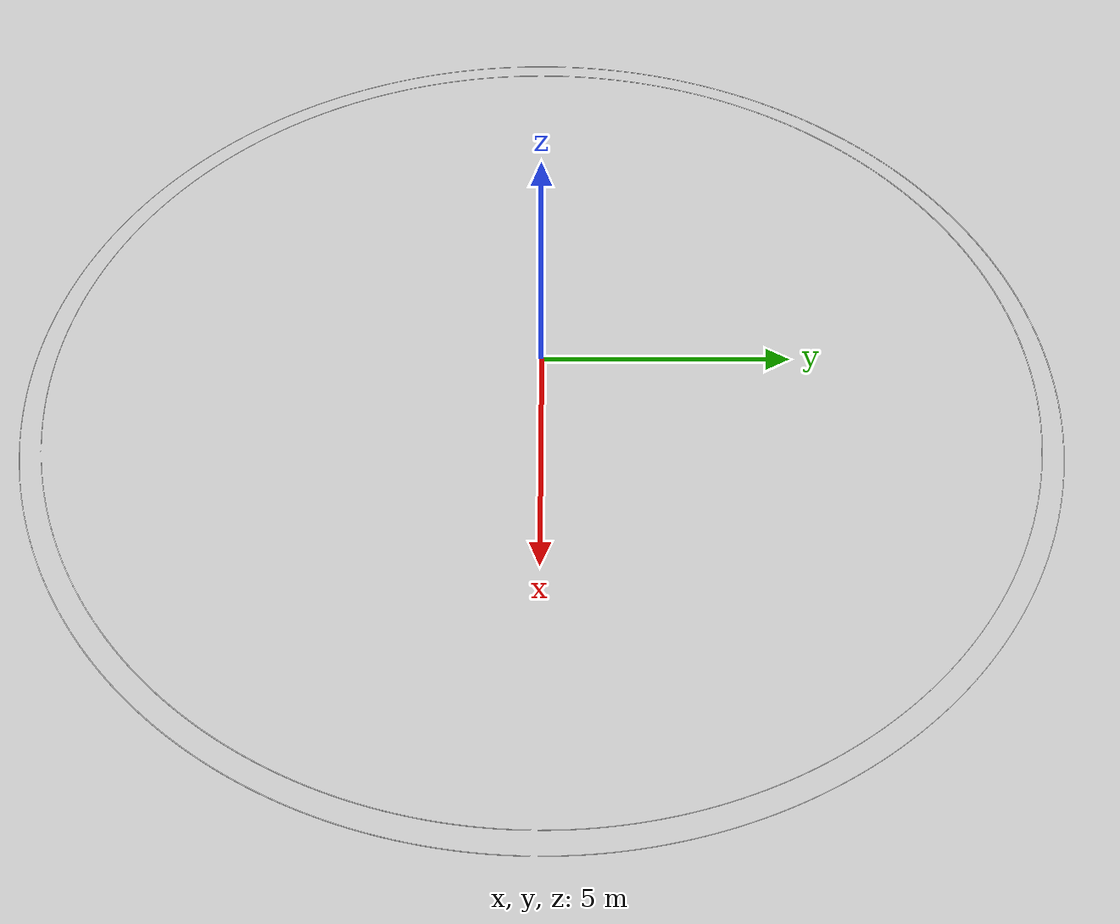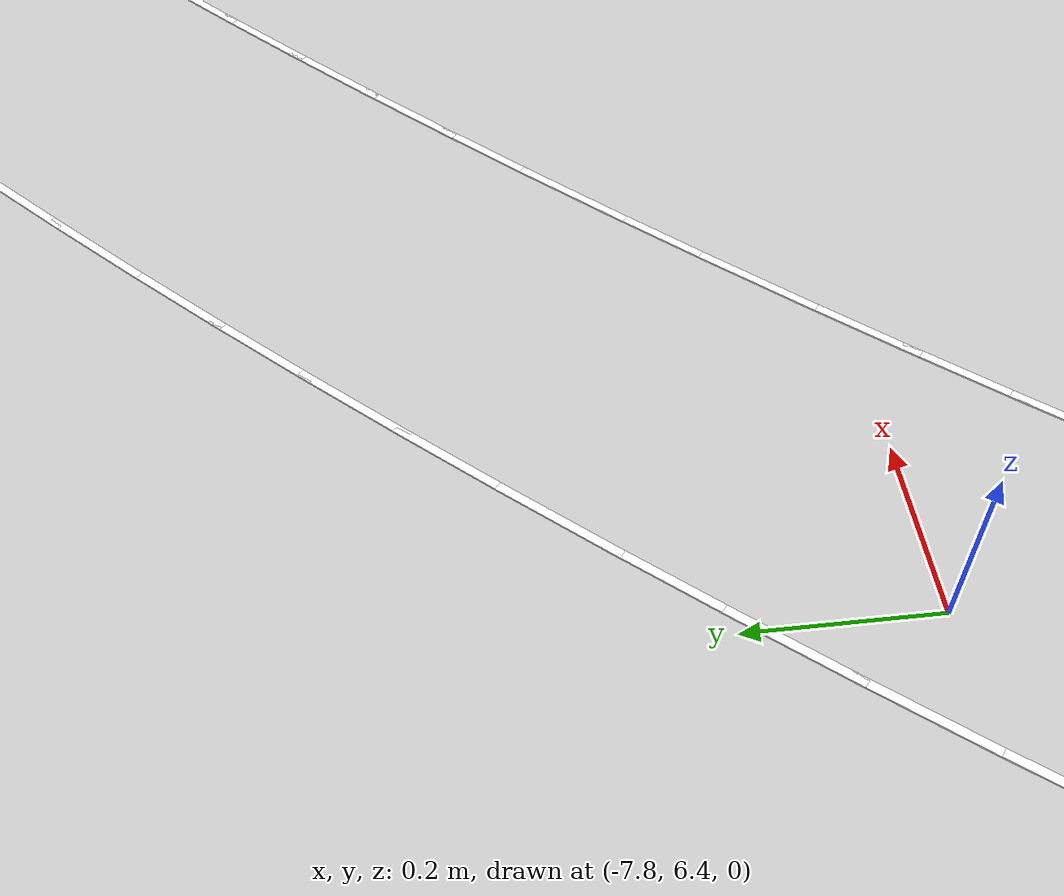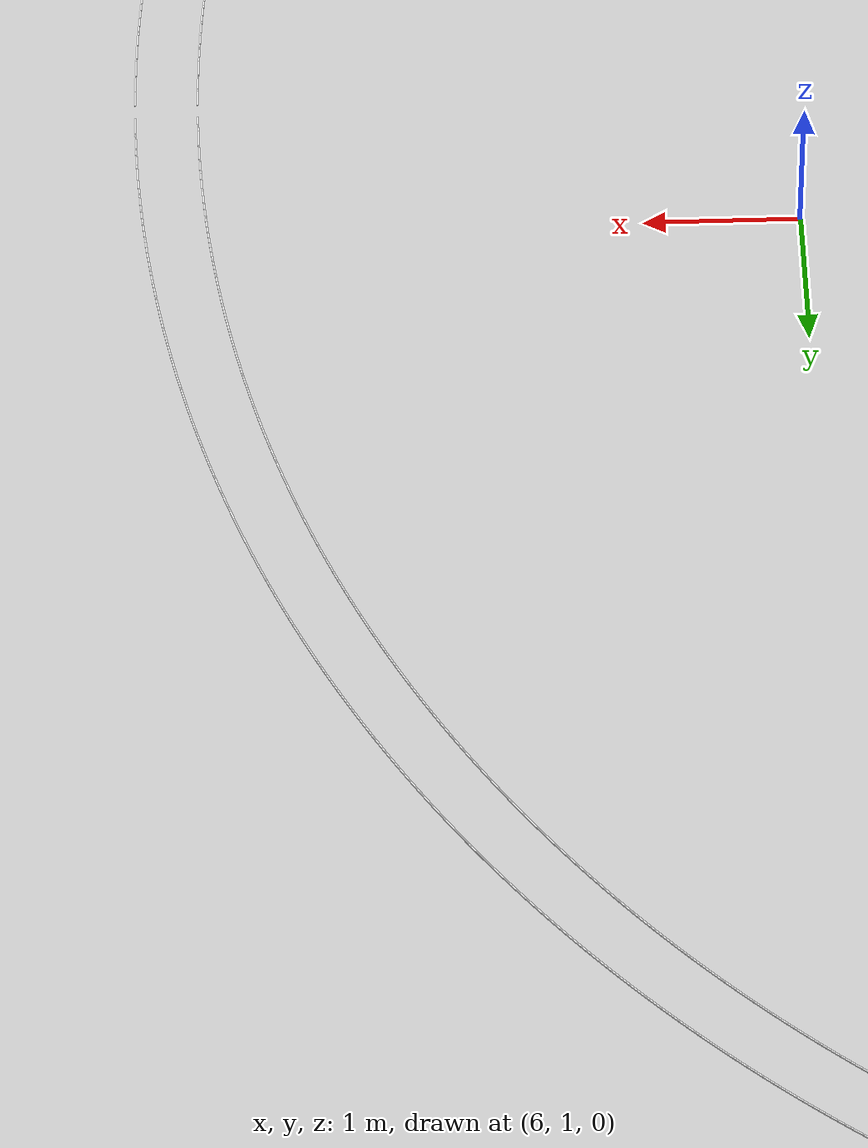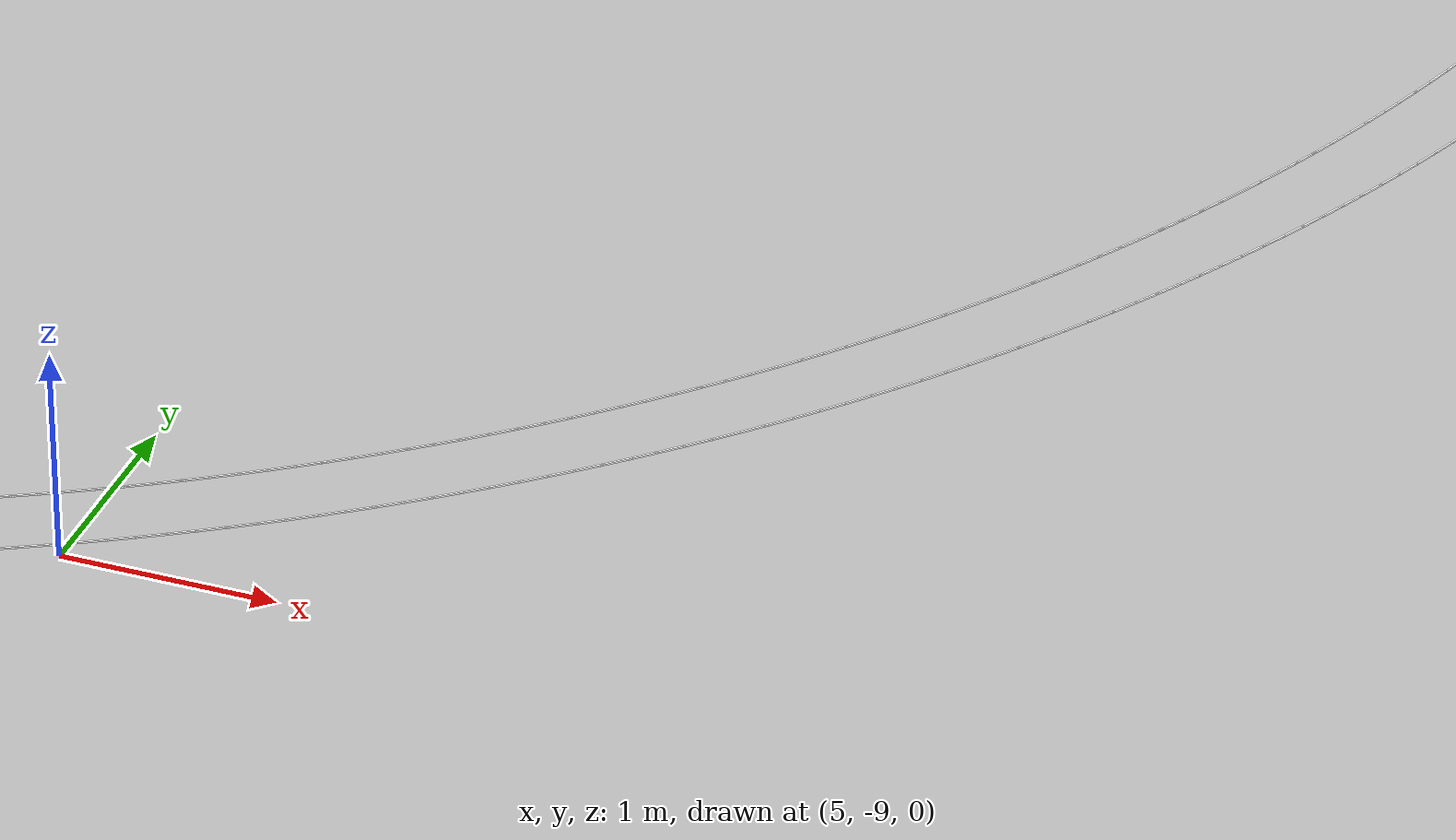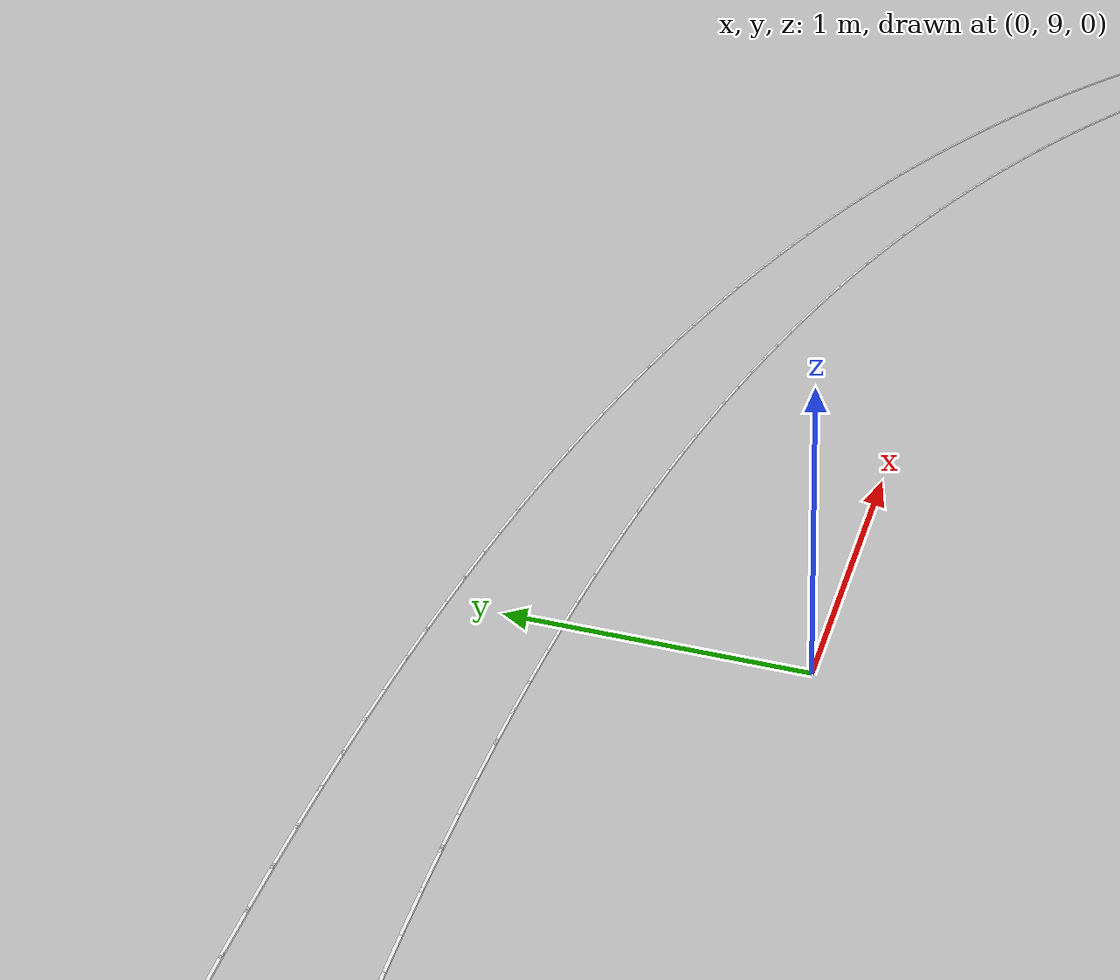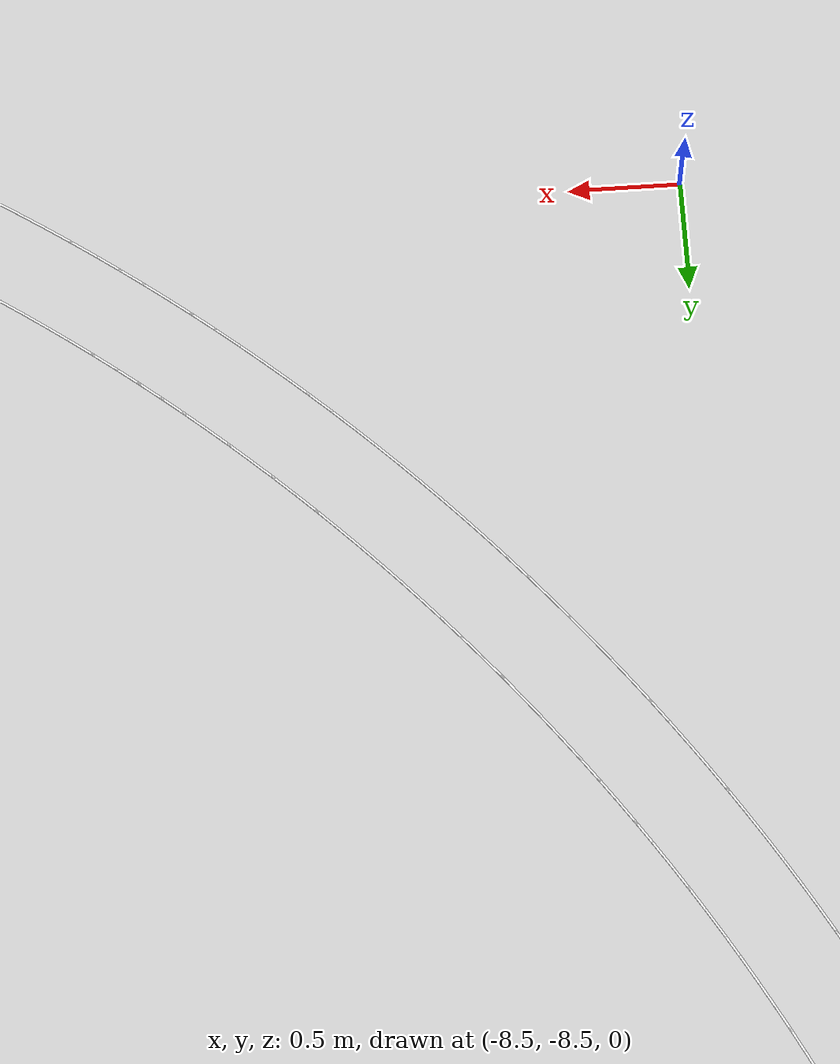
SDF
<sdf version="1.7">
 <world name="default">
  <light name="sun" type="directional">
   <pose>0 0 10 0 -0 0</pose>
   <diffuse>0.8 0.8 0.8 1</diffuse>
   <specular>0.2 0.2 0.2 1</specular>
   <attenuation>
    <range>1000</range>
    <constant>0.9</constant>
    <linear>0.01</linear>
    <quadratic>0.001</quadratic>
   </attenuation>
   <direction>-0.5 0.1 -0.9</direction>
   <spot><inner_angle>0</inner_angle><outer_angle>0</outer_angle><falloff>0</falloff></spot>
  </light>
  <model name="ground_plane">
   <static>1</static>
   <link name="link">
    <collision name="collision">
     <geometry><plane><normal>0 0 1</normal><size>100 100</size></plane></geometry>
     <surface>
      <contact><collide_bitmask>65535</collide_bitmask></contact>
      <friction><ode><mu>100</mu><mu2>50</mu2></ode></friction>
     </surface>
    </collision>
    <visual name="visual">
     <cast_shadows>0</cast_shadows>
     <geometry><plane><normal>0 0 1</normal><size>100 100</size></plane></geometry>
     <material>
      <script><uri>file://media/materials/scripts/gazebo.material</uri><name>Gazebo/Grey</name></script>
     </material>
    </visual>
   </link>
  </model>
  <gravity>0 0 -9.8</gravity>
  <magnetic_field>6e-06 2.3e-05 -4.2e-05</magnetic_field>
  <atmosphere type="adiabatic"/>
  <physics type="ode">
   <max_step_size>0.001</max_step_size>
   <real_time_factor>1</real_time_factor>
   <real_time_update_rate>1000</real_time_update_rate>
  </physics>
  <scene><ambient>0.4 0.4 0.4 1</ambient><background>0.7 0.7 0.7 1</background><shadows>1</shadows></scene>
  <spherical_coordinates>
   <surface_model>EARTH_WGS84</surface_model>
   <latitude_deg>0</latitude_deg>
   <longitude_deg>0</longitude_deg>
   <elevation>0</elevation>
   <heading_deg>0</heading_deg>
  </spherical_coordinates>
  <model name="lane_line_left_0">
   <static>1</static>
   <link name="link">
    <pose>0 0 -0.004 0 -0 0</pose>
    <visual name="visual">
     <geometry><box><size>0.1457 0.01 0.01</size></box></geometry>
     <material><ambient>1 1 1 1</ambient><diffuse>1 1 1 1</diffuse></material>
    </visual>
    <collision name="collision"><geometry><box><size>0.1457 0.01 0.01</size></box></geometry></collision>
   </link>
   <pose>9.79961 0.061574 0 0 -0 1.57708</pose>
  </model>
  <model name="lane_line_right_0">
   <static>1</static>
   <link name="link">
    <pose>0 0 -0.004 0 -0 0</pose>
    <visual name="visual">
     <geometry><box><size>0.1457 0.01 0.01</size></box></geometry>
     <material><ambient>1 1 1 1</ambient><diffuse>1 1 1 1</diffuse></material>
    </visual>
    <collision name="collision"><geometry><box><size>0.1457 0.01 0.01</size></box></geometry></collision>
   </link>
   <pose>10.1996 0.064087 0 0 -0 1.57708</pose>
  </model>
  <model name="lane_line_left_1">
   <static>1</static>
   <link name="link">
    <pose>0 0 -0.004 0 -0 0</pose>
    <visual name="visual">
     <geometry><box><size>0.1457 0.01 0.01</size></box></geometry>
     <material><ambient>1 1 1 1</ambient><diffuse>1 1 1 1</diffuse></material>
    </visual>
    <collision name="collision"><geometry><box><size>0.1457 0.01 0.01</size></box></geometry></collision>
   </link>
   <pose>9.79806 0.184711 0 0 -0 1.58965</pose>
  </model>
  <model name="lane_line_right_1">
   <static>1</static>
   <link name="link">
    <pose>0 0 -0.004 0 -0 0</pose>
    <visual name="visual">
     <geometry><box><size>0.1457 0.01 0.01</size></box></geometry>
     <material><ambient>1 1 1 1</ambient><diffuse>1 1 1 1</diffuse></material>
    </visual>
    <collision name="collision"><geometry><box><size>0.1457 0.01 0.01</size></box></geometry></collision>
   </link>
   <pose>10.198 0.19225 0 0 -0 1.58965</pose>
  </model>
  <model name="lane_line_left_2">
   <static>1</static>
   <link name="link">
    <pose>0 0 -0.004 0 -0 0</pose>
    <visual name="visual">
     <geometry><box><size>0.1457 0.01 0.01</size></box></geometry>
     <material><ambient>1 1 1 1</ambient><diffuse>1 1 1 1</diffuse></material>
    </visual>
    <collision name="collision"><geometry><box><size>0.1457 0.01 0.01</size></box></geometry></collision>
   </link>
   <pose>9.79497 0.307819 0 0 -0 1.60221</pose>
  </model>
  <model name="lane_line_right_2">
   <static>1</static>
   <link name="link">
    <pose>0 0 -0.004 0 -0 0</pose>
    <visual name="visual">
     <geometry><box><size>0.1457 0.01 0.01</size></box></geometry>
     <material><ambient>1 1 1 1</ambient><diffuse>1 1 1 1</diffuse></material>
    </visual>
    <collision name="collision"><geometry><box><size>0.1457 0.01 0.01</size></box></geometry></collision>
   </link>
   <pose>10.1948 0.320384 0 0 -0 1.60221</pose>
  </model>
  <model name="lane_line_left_3">
   <static>1</static>
   <link name="link">
    <pose>0 0 -0.004 0 -0 0</pose>
    <visual name="visual">
     <geometry><box><size>0.1457 0.01 0.01</size></box></geometry>
     <material><ambient>1 1 1 1</ambient><diffuse>1 1 1 1</diffuse></material>
    </visual>
    <collision name="collision"><geometry><box><size>0.1457 0.01 0.01</size></box></geometry></collision>
   </link>
   <pose>9.79033 0.430879 0 0 -0 1.61478</pose>
  </model>
  <model name="lane_line_right_3">
   <static>1</static>
   <link name="link">
    <pose>0 0 -0.004 0 -0 0</pose>
    <visual name="visual">
     <geometry><box><size>0.1457 0.01 0.01</size></box></geometry>
     <material><ambient>1 1 1 1</ambient><diffuse>1 1 1 1</diffuse></material>
    </visual>
    <collision name="collision"><geometry><box><size>0.1457 0.01 0.01</size></box></geometry></collision>
   </link>
   <pose>10.1899 0.448466 0 0 -0 1.61478</pose>
  </model>
  <model name="lane_line_left_4">
   <static>1</static>
   <link name="link">
    <pose>0 0 -0.004 0 -0 0</pose>
    <visual name="visual">
     <geometry><box><size>0.1457 0.01 0.01</size></box></geometry>
     <material><ambient>1 1 1 1</ambient><diffuse>1 1 1 1</diffuse></material>
    </visual>
    <collision name="collision"><geometry><box><size>0.1457 0.01 0.01</size></box></geometry></collision>
   </link>
   <pose>9.78414 0.55387 0 0 -0 1.62734</pose>
  </model>
  <model name="lane_line_right_4">
   <static>1</static>
   <link name="link">
    <pose>0 0 -0.004 0 -0 0</pose>
    <visual name="visual">
     <geometry><box><size>0.1457 0.01 0.01</size></box></geometry>
     <material><ambient>1 1 1 1</ambient><diffuse>1 1 1 1</diffuse></material>
    </visual>
    <collision name="collision"><geometry><box><size>0.1457 0.01 0.01</size></box></geometry></collision>
   </link>
   <pose>10.1835 0.576478 0 0 -0 1.62734</pose>
  </model>
  <model name="lane_line_left_5">
   <static>1</static>
   <link name="link">
    <pose>0 0 -0.004 0 -0 0</pose>
    <visual name="visual">
     <geometry><box><size>0.1457 0.01 0.01</size></box></geometry>
     <material><ambient>1 1 1 1</ambient><diffuse>1 1 1 1</diffuse></material>
    </visual>
    <collision name="collision"><geometry><box><size>0.1457 0.01 0.01</size></box></geometry></collision>
   </link>
   <pose>9.77641 0.676775 0 0 -0 1.63991</pose>
  </model>
  <model name="lane_line_right_5">
   <static>1</static>
   <link name="link">
    <pose>0 0 -0.004 0 -0 0</pose>
    <visual name="visual">
     <geometry><box><size>0.1457 0.01 0.01</size></box></geometry>
     <material><ambient>1 1 1 1</ambient><diffuse>1 1 1 1</diffuse></material>
    </visual>
    <collision name="collision"><geometry><box><size>0.1457 0.01 0.01</size></box></geometry></collision>
   </link>
   <pose>10.1755 0.704399 0 0 -0 1.63991</pose>
  </model>
  <model name="lane_line_left_6">
   <static>1</static>
   <link name="link">
    <pose>0 0 -0.004 0 -0 0</pose>
    <visual name="visual">
     <geometry><box><size>0.1457 0.01 0.01</size></box></geometry>
     <material><ambient>1 1 1 1</ambient><diffuse>1 1 1 1</diffuse></material>
    </visual>
    <collision name="collision"><geometry><box><size>0.1457 0.01 0.01</size></box></geometry></collision>
   </link>
   <pose>9.76713 0.799572 0 0 -0 1.65248</pose>
  </model>
  <model name="lane_line_right_6">
   <static>1</static>
   <link name="link">
    <pose>0 0 -0.004 0 -0 0</pose>
    <visual name="visual">
     <geometry><box><size>0.1457 0.01 0.01</size></box></geometry>
     <material><ambient>1 1 1 1</ambient><diffuse>1 1 1 1</diffuse></material>
    </visual>
    <collision name="collision"><geometry><box><size>0.1457 0.01 0.01</size></box></geometry></collision>
   </link>
   <pose>10.1658 0.832208 0 0 -0 1.65248</pose>
  </model>
  <model name="lane_line_left_7">
   <static>1</static>
   <link name="link">
    <pose>0 0 -0.004 0 -0 0</pose>
    <visual name="visual">
     <geometry><box><size>0.1457 0.01 0.01</size></box></geometry>
     <material><ambient>1 1 1 1</ambient><diffuse>1 1 1 1</diffuse></material>
    </visual>
    <collision name="collision"><geometry><box><size>0.1457 0.01 0.01</size></box></geometry></collision>
   </link>
   <pose>9.75631 0.922243 0 0 -0 1.66504</pose>
  </model>
  <model name="lane_line_right_7">
   <static>1</static>
   <link name="link">
    <pose>0 0 -0.004 0 -0 0</pose>
    <visual name="visual">
     <geometry><box><size>0.1457 0.01 0.01</size></box></geometry>
     <material><ambient>1 1 1 1</ambient><diffuse>1 1 1 1</diffuse></material>
    </visual>
    <collision name="collision"><geometry><box><size>0.1457 0.01 0.01</size></box></geometry></collision>
   </link>
   <pose>10.1545 0.959886 0 0 -0 1.66504</pose>
  </model>
  <model name="lane_line_left_8">
   <static>1</static>
   <link name="link">
    <pose>0 0 -0.004 0 -0 0</pose>
    <visual name="visual">
     <geometry><box><size>0.1457 0.01 0.01</size></box></geometry>
     <material><ambient>1 1 1 1</ambient><diffuse>1 1 1 1</diffuse></material>
    </visual>
    <collision name="collision"><geometry><box><size>0.1457 0.01 0.01</size></box></geometry></collision>
   </link>
   <pose>9.74395 1.04477 0 0 -0 1.67761</pose>
  </model>
  <model name="lane_line_right_8">
   <static>1</static>
   <link name="link">
    <pose>0 0 -0.004 0 -0 0</pose>
    <visual name="visual">
     <geometry><box><size>0.1457 0.01 0.01</size></box></geometry>
     <material><ambient>1 1 1 1</ambient><diffuse>1 1 1 1</diffuse></material>
    </visual>
    <collision name="collision"><geometry><box><size>0.1457 0.01 0.01</size></box></geometry></collision>
   </link>
   <pose>10.1417 1.08741 0 0 -0 1.67761</pose>
  </model>
  <model name="lane_line_left_9">
   <static>1</static>
   <link name="link">
    <pose>0 0 -0.004 0 -0 0</pose>
    <visual name="visual">
     <geometry><box><size>0.1457 0.01 0.01</size></box></geometry>
     <material><ambient>1 1 1 1</ambient><diffuse>1 1 1 1</diffuse></material>
    </visual>
    <collision name="collision"><geometry><box><size>0.1457 0.01 0.01</size></box></geometry></collision>
   </link>
   <pose>9.73005 1.16713 0 0 -0 1.69018</pose>
  </model>
  <model name="lane_line_right_9">
   <static>1</static>
   <link name="link">
    <pose>0 0 -0.004 0 -0 0</pose>
    <visual name="visual">
     <geometry><box><size>0.1457 0.01 0.01</size></box></geometry>
     <material><ambient>1 1 1 1</ambient><diffuse>1 1 1 1</diffuse></material>
    </visual>
    <collision name="collision"><geometry><box><size>0.1457 0.01 0.01</size></box></geometry></collision>
   </link>
   <pose>10.1272 1.21477 0 0 -0 1.69018</pose>
  </model>
  <model name="lane_line_left_10">
   <static>1</static>
   <link name="link">
    <pose>0 0 -0.004 0 -0 0</pose>
    <visual name="visual">
     <geometry><box><size>0.1457 0.01 0.01</size></box></geometry>
     <material><ambient>1 1 1 1</ambient><diffuse>1 1 1 1</diffuse></material>
    </visual>
    <collision name="collision"><geometry><box><size>0.1457 0.01 0.01</size></box></geometry></collision>
   </link>
   <pose>9.71462 1.2893 0 0 -0 1.70274</pose>
  </model>
  <model name="lane_line_right_10">
   <static>1</static>
   <link name="link">
    <pose>0 0 -0.004 0 -0 0</pose>
    <visual name="visual">
     <geometry><box><size>0.1457 0.01 0.01</size></box></geometry>
     <material><ambient>1 1 1 1</ambient><diffuse>1 1 1 1</diffuse></material>
    </visual>
    <collision name="collision"><geometry><box><size>0.1457 0.01 0.01</size></box></geometry></collision>
   </link>
   <pose>10.1111 1.34193 0 0 -0 1.70274</pose>
  </model>
  <model name="lane_line_left_11">
   <static>1</static>
   <link name="link">
    <pose>0 0 -0.004 0 -0 0</pose>
    <visual name="visual">
     <geometry><box><size>0.1457 0.01 0.01</size></box></geometry>
     <material><ambient>1 1 1 1</ambient><diffuse>1 1 1 1</diffuse></material>
    </visual>
    <collision name="collision"><geometry><box><size>0.1457 0.01 0.01</size></box></geometry></collision>
   </link>
   <pose>9.69765 1.41128 0 0 -0 1.71531</pose>
  </model>
  <model name="lane_line_right_11">
   <static>1</static>
   <link name="link">
    <pose>0 0 -0.004 0 -0 0</pose>
    <visual name="visual">
     <geometry><box><size>0.1457 0.01 0.01</size></box></geometry>
     <material><ambient>1 1 1 1</ambient><diffuse>1 1 1 1</diffuse></material>
    </visual>
    <collision name="collision"><geometry><box><size>0.1457 0.01 0.01</size></box></geometry></collision>
   </link>
   <pose>10.0935 1.46888 0 0 -0 1.71531</pose>
  </model>
  <model name="lane_line_left_12">
   <static>1</static>
   <link name="link">
    <pose>0 0 -0.004 0 -0 0</pose>
    <visual name="visual">
     <geometry><box><size>0.1457 0.01 0.01</size></box></geometry>
     <material><ambient>1 1 1 1</ambient><diffuse>1 1 1 1</diffuse></material>
    </visual>
    <collision name="collision"><geometry><box><size>0.1457 0.01 0.01</size></box></geometry></collision>
   </link>
   <pose>9.67915 1.53303 0 0 -0 1.72788</pose>
  </model>
  <model name="lane_line_right_12">
   <static>1</static>
   <link name="link">
    <pose>0 0 -0.004 0 -0 0</pose>
    <visual name="visual">
     <geometry><box><size>0.1457 0.01 0.01</size></box></geometry>
     <material><ambient>1 1 1 1</ambient><diffuse>1 1 1 1</diffuse></material>
    </visual>
    <collision name="collision"><geometry><box><size>0.1457 0.01 0.01</size></box></geometry></collision>
   </link>
   <pose>10.0742 1.5956 0 0 -0 1.72788</pose>
  </model>
  <model name="lane_line_left_13">
   <static>1</static>
   <link name="link">
    <pose>0 0 -0.004 0 -0 0</pose>
    <visual name="visual">
     <geometry><box><size>0.1457 0.01 0.01</size></box></geometry>
     <material><ambient>1 1 1 1</ambient><diffuse>1 1 1 1</diffuse></material>
    </visual>
    <collision name="collision"><geometry><box><size>0.1457 0.01 0.01</size></box></geometry></collision>
   </link>
   <pose>9.65912 1.65453 0 0 -0 1.74044</pose>
  </model>
  <model name="lane_line_right_13">
   <static>1</static>
   <link name="link">
    <pose>0 0 -0.004 0 -0 0</pose>
    <visual name="visual">
     <geometry><box><size>0.1457 0.01 0.01</size></box></geometry>
     <material><ambient>1 1 1 1</ambient><diffuse>1 1 1 1</diffuse></material>
    </visual>
    <collision name="collision"><geometry><box><size>0.1457 0.01 0.01</size></box></geometry></collision>
   </link>
   <pose>10.0534 1.72207 0 0 -0 1.74044</pose>
  </model>
  <model name="lane_line_left_14">
   <static>1</static>
   <link name="link">
    <pose>0 0 -0.004 0 -0 0</pose>
    <visual name="visual">
     <geometry><box><size>0.1457 0.01 0.01</size></box></geometry>
     <material><ambient>1 1 1 1</ambient><diffuse>1 1 1 1</diffuse></material>
    </visual>
    <collision name="collision"><geometry><box><size>0.1457 0.01 0.01</size></box></geometry></collision>
   </link>
   <pose>9.63757 1.77578 0 0 -0 1.75301</pose>
  </model>
  <model name="lane_line_right_14">
   <static>1</static>
   <link name="link">
    <pose>0 0 -0.004 0 -0 0</pose>
    <visual name="visual">
     <geometry><box><size>0.1457 0.01 0.01</size></box></geometry>
     <material><ambient>1 1 1 1</ambient><diffuse>1 1 1 1</diffuse></material>
    </visual>
    <collision name="collision"><geometry><box><size>0.1457 0.01 0.01</size></box></geometry></collision>
   </link>
   <pose>10.0309 1.84826 0 0 -0 1.75301</pose>
  </model>
  <model name="lane_line_left_15">
   <static>1</static>
   <link name="link">
    <pose>0 0 -0.004 0 -0 0</pose>
    <visual name="visual">
     <geometry><box><size>0.1457 0.01 0.01</size></box></geometry>
     <material><ambient>1 1 1 1</ambient><diffuse>1 1 1 1</diffuse></material>
    </visual>
    <collision name="collision"><geometry><box><size>0.1457 0.01 0.01</size></box></geometry></collision>
   </link>
   <pose>9.61449 1.89675 0 0 -0 1.76558</pose>
  </model>
  <model name="lane_line_right_15">
   <static>1</static>
   <link name="link">
    <pose>0 0 -0.004 0 -0 0</pose>
    <visual name="visual">
     <geometry><box><size>0.1457 0.01 0.01</size></box></geometry>
     <material><ambient>1 1 1 1</ambient><diffuse>1 1 1 1</diffuse></material>
    </visual>
    <collision name="collision"><geometry><box><size>0.1457 0.01 0.01</size></box></geometry></collision>
   </link>
   <pose>10.0069 1.97417 0 0 -0 1.76558</pose>
  </model>
  <model name="lane_line_left_16">
   <static>1</static>
   <link name="link">
    <pose>0 0 -0.004 0 -0 0</pose>
    <visual name="visual">
     <geometry><box><size>0.1457 0.01 0.01</size></box></geometry>
     <material><ambient>1 1 1 1</ambient><diffuse>1 1 1 1</diffuse></material>
    </visual>
    <collision name="collision"><geometry><box><size>0.1457 0.01 0.01</size></box></geometry></collision>
   </link>
   <pose>9.5899 2.01741 0 0 -0 1.77814</pose>
  </model>
  <model name="lane_line_right_16">
   <static>1</static>
   <link name="link">
    <pose>0 0 -0.004 0 -0 0</pose>
    <visual name="visual">
     <geometry><box><size>0.1457 0.01 0.01</size></box></geometry>
     <material><ambient>1 1 1 1</ambient><diffuse>1 1 1 1</diffuse></material>
    </visual>
    <collision name="collision"><geometry><box><size>0.1457 0.01 0.01</size></box></geometry></collision>
   </link>
   <pose>9.98133 2.09976 0 0 -0 1.77814</pose>
  </model>
  <model name="lane_line_left_17">
   <static>1</static>
   <link name="link">
    <pose>0 0 -0.004 0 -0 0</pose>
    <visual name="visual">
     <geometry><box><size>0.1457 0.01 0.01</size></box></geometry>
     <material><ambient>1 1 1 1</ambient><diffuse>1 1 1 1</diffuse></material>
    </visual>
    <collision name="collision"><geometry><box><size>0.1457 0.01 0.01</size></box></geometry></collision>
   </link>
   <pose>9.56379 2.13776 0 0 -0 1.79071</pose>
  </model>
  <model name="lane_line_right_17">
   <static>1</static>
   <link name="link">
    <pose>0 0 -0.004 0 -0 0</pose>
    <visual name="visual">
     <geometry><box><size>0.1457 0.01 0.01</size></box></geometry>
     <material><ambient>1 1 1 1</ambient><diffuse>1 1 1 1</diffuse></material>
    </visual>
    <collision name="collision"><geometry><box><size>0.1457 0.01 0.01</size></box></geometry></collision>
   </link>
   <pose>9.95416 2.22502 0 0 -0 1.79071</pose>
  </model>
  <model name="lane_line_left_18">
   <static>1</static>
   <link name="link">
    <pose>0 0 -0.004 0 -0 0</pose>
    <visual name="visual">
     <geometry><box><size>0.1457 0.01 0.01</size></box></geometry>
     <material><ambient>1 1 1 1</ambient><diffuse>1 1 1 1</diffuse></material>
    </visual>
    <collision name="collision"><geometry><box><size>0.1457 0.01 0.01</size></box></geometry></collision>
   </link>
   <pose>9.53617 2.25777 0 0 -0 1.80327</pose>
  </model>
  <model name="lane_line_right_18">
   <static>1</static>
   <link name="link">
    <pose>0 0 -0.004 0 -0 0</pose>
    <visual name="visual">
     <geometry><box><size>0.1457 0.01 0.01</size></box></geometry>
     <material><ambient>1 1 1 1</ambient><diffuse>1 1 1 1</diffuse></material>
    </visual>
    <collision name="collision"><geometry><box><size>0.1457 0.01 0.01</size></box></geometry></collision>
   </link>
   <pose>9.92541 2.34993 0 0 -0 1.80327</pose>
  </model>
  <model name="lane_line_left_19">
   <static>1</static>
   <link name="link">
    <pose>0 0 -0.004 0 -0 0</pose>
    <visual name="visual">
     <geometry><box><size>0.1457 0.01 0.01</size></box></geometry>
     <material><ambient>1 1 1 1</ambient><diffuse>1 1 1 1</diffuse></material>
    </visual>
    <collision name="collision"><geometry><box><size>0.1457 0.01 0.01</size></box></geometry></collision>
   </link>
   <pose>9.50705 2.37742 0 0 -0 1.81584</pose>
  </model>
  <model name="lane_line_right_19">
   <static>1</static>
   <link name="link">
    <pose>0 0 -0.004 0 -0 0</pose>
    <visual name="visual">
     <geometry><box><size>0.1457 0.01 0.01</size></box></geometry>
     <material><ambient>1 1 1 1</ambient><diffuse>1 1 1 1</diffuse></material>
    </visual>
    <collision name="collision"><geometry><box><size>0.1457 0.01 0.01</size></box></geometry></collision>
   </link>
   <pose>9.8951 2.47446 0 0 -0 1.81584</pose>
  </model>
  <model name="lane_line_left_20">
   <static>1</static>
   <link name="link">
    <pose>0 0 -0.004 0 -0 0</pose>
    <visual name="visual">
     <geometry><box><size>0.1457 0.01 0.01</size></box></geometry>
     <material><ambient>1 1 1 1</ambient><diffuse>1 1 1 1</diffuse></material>
    </visual>
    <collision name="collision"><geometry><box><size>0.1457 0.01 0.01</size></box></geometry></collision>
   </link>
   <pose>9.47642 2.4967 0 0 -0 1.82841</pose>
  </model>
  <model name="lane_line_right_20">
   <static>1</static>
   <link name="link">
    <pose>0 0 -0.004 0 -0 0</pose>
    <visual name="visual">
     <geometry><box><size>0.1457 0.01 0.01</size></box></geometry>
     <material><ambient>1 1 1 1</ambient><diffuse>1 1 1 1</diffuse></material>
    </visual>
    <collision name="collision"><geometry><box><size>0.1457 0.01 0.01</size></box></geometry></collision>
   </link>
   <pose>9.86322 2.59861 0 0 -0 1.82841</pose>
  </model>
  <model name="lane_line_left_21">
   <static>1</static>
   <link name="link">
    <pose>0 0 -0.004 0 -0 0</pose>
    <visual name="visual">
     <geometry><box><size>0.1457 0.01 0.01</size></box></geometry>
     <material><ambient>1 1 1 1</ambient><diffuse>1 1 1 1</diffuse></material>
    </visual>
    <collision name="collision"><geometry><box><size>0.1457 0.01 0.01</size></box></geometry></collision>
   </link>
   <pose>9.4443 2.61559 0 0 -0 1.84097</pose>
  </model>
  <model name="lane_line_right_21">
   <static>1</static>
   <link name="link">
    <pose>0 0 -0.004 0 -0 0</pose>
    <visual name="visual">
     <geometry><box><size>0.1457 0.01 0.01</size></box></geometry>
     <material><ambient>1 1 1 1</ambient><diffuse>1 1 1 1</diffuse></material>
    </visual>
    <collision name="collision"><geometry><box><size>0.1457 0.01 0.01</size></box></geometry></collision>
   </link>
   <pose>9.82979 2.72235 0 0 -0 1.84097</pose>
  </model>
  <model name="lane_line_left_22">
   <static>1</static>
   <link name="link">
    <pose>0 0 -0.004 0 -0 0</pose>
    <visual name="visual">
     <geometry><box><size>0.1457 0.01 0.01</size></box></geometry>
     <material><ambient>1 1 1 1</ambient><diffuse>1 1 1 1</diffuse></material>
    </visual>
    <collision name="collision"><geometry><box><size>0.1457 0.01 0.01</size></box></geometry></collision>
   </link>
   <pose>9.41069 2.73406 0 0 -0 1.85354</pose>
  </model>
  <model name="lane_line_right_22">
   <static>1</static>
   <link name="link">
    <pose>0 0 -0.004 0 -0 0</pose>
    <visual name="visual">
     <geometry><box><size>0.1457 0.01 0.01</size></box></geometry>
     <material><ambient>1 1 1 1</ambient><diffuse>1 1 1 1</diffuse></material>
    </visual>
    <collision name="collision"><geometry><box><size>0.1457 0.01 0.01</size></box></geometry></collision>
   </link>
   <pose>9.79481 2.84565 0 0 -0 1.85354</pose>
  </model>
  <model name="lane_line_left_23">
   <static>1</static>
   <link name="link">
    <pose>0 0 -0.004 0 -0 0</pose>
    <visual name="visual">
     <geometry><box><size>0.1457 0.01 0.01</size></box></geometry>
     <material><ambient>1 1 1 1</ambient><diffuse>1 1 1 1</diffuse></material>
    </visual>
    <collision name="collision"><geometry><box><size>0.1457 0.01 0.01</size></box></geometry></collision>
   </link>
   <pose>9.37559 2.8521 0 0 -0 1.86611</pose>
  </model>
  <model name="lane_line_right_23">
   <static>1</static>
   <link name="link">
    <pose>0 0 -0.004 0 -0 0</pose>
    <visual name="visual">
     <geometry><box><size>0.1457 0.01 0.01</size></box></geometry>
     <material><ambient>1 1 1 1</ambient><diffuse>1 1 1 1</diffuse></material>
    </visual>
    <collision name="collision"><geometry><box><size>0.1457 0.01 0.01</size></box></geometry></collision>
   </link>
   <pose>9.75827 2.96851 0 0 -0 1.86611</pose>
  </model>
  <model name="lane_line_left_24">
   <static>1</static>
   <link name="link">
    <pose>0 0 -0.004 0 -0 0</pose>
    <visual name="visual">
     <geometry><box><size>0.1457 0.01 0.01</size></box></geometry>
     <material><ambient>1 1 1 1</ambient><diffuse>1 1 1 1</diffuse></material>
    </visual>
    <collision name="collision"><geometry><box><size>0.1457 0.01 0.01</size></box></geometry></collision>
   </link>
   <pose>9.33901 2.96969 0 0 -0 1.87867</pose>
  </model>
  <model name="lane_line_right_24">
   <static>1</static>
   <link name="link">
    <pose>0 0 -0.004 0 -0 0</pose>
    <visual name="visual">
     <geometry><box><size>0.1457 0.01 0.01</size></box></geometry>
     <material><ambient>1 1 1 1</ambient><diffuse>1 1 1 1</diffuse></material>
    </visual>
    <collision name="collision"><geometry><box><size>0.1457 0.01 0.01</size></box></geometry></collision>
   </link>
   <pose>9.7202 3.0909 0 0 -0 1.87867</pose>
  </model>
  <model name="lane_line_left_25">
   <static>1</static>
   <link name="link">
    <pose>0 0 -0.004 0 -0 0</pose>
    <visual name="visual">
     <geometry><box><size>0.1457 0.01 0.01</size></box></geometry>
     <material><ambient>1 1 1 1</ambient><diffuse>1 1 1 1</diffuse></material>
    </visual>
    <collision name="collision"><geometry><box><size>0.1457 0.01 0.01</size></box></geometry></collision>
   </link>
   <pose>9.30095 3.08681 0 0 -0 1.89124</pose>
  </model>
  <model name="lane_line_right_25">
   <static>1</static>
   <link name="link">
    <pose>0 0 -0.004 0 -0 0</pose>
    <visual name="visual">
     <geometry><box><size>0.1457 0.01 0.01</size></box></geometry>
     <material><ambient>1 1 1 1</ambient><diffuse>1 1 1 1</diffuse></material>
    </visual>
    <collision name="collision"><geometry><box><size>0.1457 0.01 0.01</size></box></geometry></collision>
   </link>
   <pose>9.68059 3.2128 0 0 -0 1.89124</pose>
  </model>
  <model name="lane_line_left_26">
   <static>1</static>
   <link name="link">
    <pose>0 0 -0.004 0 -0 0</pose>
    <visual name="visual">
     <geometry><box><size>0.1457 0.01 0.01</size></box></geometry>
     <material><ambient>1 1 1 1</ambient><diffuse>1 1 1 1</diffuse></material>
    </visual>
    <collision name="collision"><geometry><box><size>0.1457 0.01 0.01</size></box></geometry></collision>
   </link>
   <pose>9.26143 3.20344 0 0 -0 1.90381</pose>
  </model>
  <model name="lane_line_right_26">
   <static>1</static>
   <link name="link">
    <pose>0 0 -0.004 0 -0 0</pose>
    <visual name="visual">
     <geometry><box><size>0.1457 0.01 0.01</size></box></geometry>
     <material><ambient>1 1 1 1</ambient><diffuse>1 1 1 1</diffuse></material>
    </visual>
    <collision name="collision"><geometry><box><size>0.1457 0.01 0.01</size></box></geometry></collision>
   </link>
   <pose>9.63946 3.33419 0 0 -0 1.90381</pose>
  </model>
  <model name="lane_line_left_27">
   <static>1</static>
   <link name="link">
    <pose>0 0 -0.004 0 -0 0</pose>
    <visual name="visual">
     <geometry><box><size>0.1457 0.01 0.01</size></box></geometry>
     <material><ambient>1 1 1 1</ambient><diffuse>1 1 1 1</diffuse></material>
    </visual>
    <collision name="collision"><geometry><box><size>0.1457 0.01 0.01</size></box></geometry></collision>
   </link>
   <pose>9.22045 3.31956 0 0 -0 1.91637</pose>
  </model>
  <model name="lane_line_right_27">
   <static>1</static>
   <link name="link">
    <pose>0 0 -0.004 0 -0 0</pose>
    <visual name="visual">
     <geometry><box><size>0.1457 0.01 0.01</size></box></geometry>
     <material><ambient>1 1 1 1</ambient><diffuse>1 1 1 1</diffuse></material>
    </visual>
    <collision name="collision"><geometry><box><size>0.1457 0.01 0.01</size></box></geometry></collision>
   </link>
   <pose>9.5968 3.45506 0 0 -0 1.91637</pose>
  </model>
  <model name="lane_line_left_28">
   <static>1</static>
   <link name="link">
    <pose>0 0 -0.004 0 -0 0</pose>
    <visual name="visual">
     <geometry><box><size>0.1457 0.01 0.01</size></box></geometry>
     <material><ambient>1 1 1 1</ambient><diffuse>1 1 1 1</diffuse></material>
    </visual>
    <collision name="collision"><geometry><box><size>0.1457 0.01 0.01</size></box></geometry></collision>
   </link>
   <pose>9.178 3.43517 0 0 -0 1.92894</pose>
  </model>
  <model name="lane_line_right_28">
   <static>1</static>
   <link name="link">
    <pose>0 0 -0.004 0 -0 0</pose>
    <visual name="visual">
     <geometry><box><size>0.1457 0.01 0.01</size></box></geometry>
     <material><ambient>1 1 1 1</ambient><diffuse>1 1 1 1</diffuse></material>
    </visual>
    <collision name="collision"><geometry><box><size>0.1457 0.01 0.01</size></box></geometry></collision>
   </link>
   <pose>9.55262 3.57538 0 0 -0 1.92894</pose>
  </model>
  <model name="lane_line_left_29">
   <static>1</static>
   <link name="link">
    <pose>0 0 -0.004 0 -0 0</pose>
    <visual name="visual">
     <geometry><box><size>0.1457 0.01 0.01</size></box></geometry>
     <material><ambient>1 1 1 1</ambient><diffuse>1 1 1 1</diffuse></material>
    </visual>
    <collision name="collision"><geometry><box><size>0.1457 0.01 0.01</size></box></geometry></collision>
   </link>
   <pose>9.13411 3.55023 0 0 -0 1.9415</pose>
  </model>
  <model name="lane_line_right_29">
   <static>1</static>
   <link name="link">
    <pose>0 0 -0.004 0 -0 0</pose>
    <visual name="visual">
     <geometry><box><size>0.1457 0.01 0.01</size></box></geometry>
     <material><ambient>1 1 1 1</ambient><diffuse>1 1 1 1</diffuse></material>
    </visual>
    <collision name="collision"><geometry><box><size>0.1457 0.01 0.01</size></box></geometry></collision>
   </link>
   <pose>9.50694 3.69514 0 0 -0 1.9415</pose>
  </model>
  <model name="lane_line_left_30">
   <static>1</static>
   <link name="link">
    <pose>0 0 -0.004 0 -0 0</pose>
    <visual name="visual">
     <geometry><box><size>0.1457 0.01 0.01</size></box></geometry>
     <material><ambient>1 1 1 1</ambient><diffuse>1 1 1 1</diffuse></material>
    </visual>
    <collision name="collision"><geometry><box><size>0.1457 0.01 0.01</size></box></geometry></collision>
   </link>
   <pose>9.08878 3.66473 0 0 -0 1.95407</pose>
  </model>
  <model name="lane_line_right_30">
   <static>1</static>
   <link name="link">
    <pose>0 0 -0.004 0 -0 0</pose>
    <visual name="visual">
     <geometry><box><size>0.1457 0.01 0.01</size></box></geometry>
     <material><ambient>1 1 1 1</ambient><diffuse>1 1 1 1</diffuse></material>
    </visual>
    <collision name="collision"><geometry><box><size>0.1457 0.01 0.01</size></box></geometry></collision>
   </link>
   <pose>9.45976 3.81431 0 0 -0 1.95407</pose>
  </model>
  <model name="lane_line_left_31">
   <static>1</static>
   <link name="link">
    <pose>0 0 -0.004 0 -0 0</pose>
    <visual name="visual">
     <geometry><box><size>0.1457 0.01 0.01</size></box></geometry>
     <material><ambient>1 1 1 1</ambient><diffuse>1 1 1 1</diffuse></material>
    </visual>
    <collision name="collision"><geometry><box><size>0.1457 0.01 0.01</size></box></geometry></collision>
   </link>
   <pose>9.04201 3.77865 0 0 -0 1.96664</pose>
  </model>
  <model name="lane_line_right_31">
   <static>1</static>
   <link name="link">
    <pose>0 0 -0.004 0 -0 0</pose>
    <visual name="visual">
     <geometry><box><size>0.1457 0.01 0.01</size></box></geometry>
     <material><ambient>1 1 1 1</ambient><diffuse>1 1 1 1</diffuse></material>
    </visual>
    <collision name="collision"><geometry><box><size>0.1457 0.01 0.01</size></box></geometry></collision>
   </link>
   <pose>9.41108 3.93288 0 0 -0 1.96664</pose>
  </model>
  <model name="lane_line_left_32">
   <static>1</static>
   <link name="link">
    <pose>0 0 -0.004 0 -0 0</pose>
    <visual name="visual">
     <geometry><box><size>0.1457 0.01 0.01</size></box></geometry>
     <material><ambient>1 1 1 1</ambient><diffuse>1 1 1 1</diffuse></material>
    </visual>
    <collision name="collision"><geometry><box><size>0.1457 0.01 0.01</size></box></geometry></collision>
   </link>
   <pose>8.99381 3.89197 0 0 -0 1.9792</pose>
  </model>
  <model name="lane_line_right_32">
   <static>1</static>
   <link name="link">
    <pose>0 0 -0.004 0 -0 0</pose>
    <visual name="visual">
     <geometry><box><size>0.1457 0.01 0.01</size></box></geometry>
     <material><ambient>1 1 1 1</ambient><diffuse>1 1 1 1</diffuse></material>
    </visual>
    <collision name="collision"><geometry><box><size>0.1457 0.01 0.01</size></box></geometry></collision>
   </link>
   <pose>9.36092 4.05083 0 0 -0 1.9792</pose>
  </model>
  <model name="lane_line_left_33">
   <static>1</static>
   <link name="link">
    <pose>0 0 -0.004 0 -0 0</pose>
    <visual name="visual">
     <geometry><box><size>0.1457 0.01 0.01</size></box></geometry>
     <material><ambient>1 1 1 1</ambient><diffuse>1 1 1 1</diffuse></material>
    </visual>
    <collision name="collision"><geometry><box><size>0.1457 0.01 0.01</size></box></geometry></collision>
   </link>
   <pose>8.9442 4.00468 0 0 -0 1.99177</pose>
  </model>
  <model name="lane_line_right_33">
   <static>1</static>
   <link name="link">
    <pose>0 0 -0.004 0 -0 0</pose>
    <visual name="visual">
     <geometry><box><size>0.1457 0.01 0.01</size></box></geometry>
     <material><ambient>1 1 1 1</ambient><diffuse>1 1 1 1</diffuse></material>
    </visual>
    <collision name="collision"><geometry><box><size>0.1457 0.01 0.01</size></box></geometry></collision>
   </link>
   <pose>9.30927 4.16814 0 0 -0 1.99177</pose>
  </model>
  <model name="lane_line_left_34">
   <static>1</static>
   <link name="link">
    <pose>0 0 -0.004 0 -0 0</pose>
    <visual name="visual">
     <geometry><box><size>0.1457 0.01 0.01</size></box></geometry>
     <material><ambient>1 1 1 1</ambient><diffuse>1 1 1 1</diffuse></material>
    </visual>
    <collision name="collision"><geometry><box><size>0.1457 0.01 0.01</size></box></geometry></collision>
   </link>
   <pose>8.89317 4.11676 0 0 -0 2.00434</pose>
  </model>
  <model name="lane_line_right_34">
   <static>1</static>
   <link name="link">
    <pose>0 0 -0.004 0 -0 0</pose>
    <visual name="visual">
     <geometry><box><size>0.1457 0.01 0.01</size></box></geometry>
     <material><ambient>1 1 1 1</ambient><diffuse>1 1 1 1</diffuse></material>
    </visual>
    <collision name="collision"><geometry><box><size>0.1457 0.01 0.01</size></box></geometry></collision>
   </link>
   <pose>9.25616 4.28479 0 0 -0 2.00434</pose>
  </model>
  <model name="lane_line_left_35">
   <static>1</static>
   <link name="link">
    <pose>0 0 -0.004 0 -0 0</pose>
    <visual name="visual">
     <geometry><box><size>0.1457 0.01 0.01</size></box></geometry>
     <material><ambient>1 1 1 1</ambient><diffuse>1 1 1 1</diffuse></material>
    </visual>
    <collision name="collision"><geometry><box><size>0.1457 0.01 0.01</size></box></geometry></collision>
   </link>
   <pose>8.84073 4.22818 0 0 -0 2.0169</pose>
  </model>
  <model name="lane_line_right_35">
   <static>1</static>
   <link name="link">
    <pose>0 0 -0.004 0 -0 0</pose>
    <visual name="visual">
     <geometry><box><size>0.1457 0.01 0.01</size></box></geometry>
     <material><ambient>1 1 1 1</ambient><diffuse>1 1 1 1</diffuse></material>
    </visual>
    <collision name="collision"><geometry><box><size>0.1457 0.01 0.01</size></box></geometry></collision>
   </link>
   <pose>9.20159 4.40077 0 0 -0 2.0169</pose>
  </model>
  <model name="lane_line_left_36">
   <static>1</static>
   <link name="link">
    <pose>0 0 -0.004 0 -0 0</pose>
    <visual name="visual">
     <geometry><box><size>0.1457 0.01 0.01</size></box></geometry>
     <material><ambient>1 1 1 1</ambient><diffuse>1 1 1 1</diffuse></material>
    </visual>
    <collision name="collision"><geometry><box><size>0.1457 0.01 0.01</size></box></geometry></collision>
   </link>
   <pose>8.78691 4.33894 0 0 -0 2.02947</pose>
  </model>
  <model name="lane_line_right_36">
   <static>1</static>
   <link name="link">
    <pose>0 0 -0.004 0 -0 0</pose>
    <visual name="visual">
     <geometry><box><size>0.1457 0.01 0.01</size></box></geometry>
     <material><ambient>1 1 1 1</ambient><diffuse>1 1 1 1</diffuse></material>
    </visual>
    <collision name="collision"><geometry><box><size>0.1457 0.01 0.01</size></box></geometry></collision>
   </link>
   <pose>9.14556 4.51605 0 0 -0 2.02947</pose>
  </model>
  <model name="lane_line_left_37">
   <static>1</static>
   <link name="link">
    <pose>0 0 -0.004 0 -0 0</pose>
    <visual name="visual">
     <geometry><box><size>0.1457 0.01 0.01</size></box></geometry>
     <material><ambient>1 1 1 1</ambient><diffuse>1 1 1 1</diffuse></material>
    </visual>
    <collision name="collision"><geometry><box><size>0.1457 0.01 0.01</size></box></geometry></collision>
   </link>
   <pose>8.73169 4.44902 0 0 -0 2.04204</pose>
  </model>
  <model name="lane_line_right_37">
   <static>1</static>
   <link name="link">
    <pose>0 0 -0.004 0 -0 0</pose>
    <visual name="visual">
     <geometry><box><size>0.1457 0.01 0.01</size></box></geometry>
     <material><ambient>1 1 1 1</ambient><diffuse>1 1 1 1</diffuse></material>
    </visual>
    <collision name="collision"><geometry><box><size>0.1457 0.01 0.01</size></box></geometry></collision>
   </link>
   <pose>9.08809 4.63061 0 0 -0 2.04204</pose>
  </model>
  <model name="lane_line_left_38">
   <static>1</static>
   <link name="link">
    <pose>0 0 -0.004 0 -0 0</pose>
    <visual name="visual">
     <geometry><box><size>0.1457 0.01 0.01</size></box></geometry>
     <material><ambient>1 1 1 1</ambient><diffuse>1 1 1 1</diffuse></material>
    </visual>
    <collision name="collision"><geometry><box><size>0.1457 0.01 0.01</size></box></geometry></collision>
   </link>
   <pose>8.67509 4.55839 0 0 -0 2.0546</pose>
  </model>
  <model name="lane_line_right_38">
   <static>1</static>
   <link name="link">
    <pose>0 0 -0.004 0 -0 0</pose>
    <visual name="visual">
     <geometry><box><size>0.1457 0.01 0.01</size></box></geometry>
     <material><ambient>1 1 1 1</ambient><diffuse>1 1 1 1</diffuse></material>
    </visual>
    <collision name="collision"><geometry><box><size>0.1457 0.01 0.01</size></box></geometry></collision>
   </link>
   <pose>9.02918 4.74445 0 0 -0 2.0546</pose>
  </model>
  <model name="lane_line_left_39">
   <static>1</static>
   <link name="link">
    <pose>0 0 -0.004 0 -0 0</pose>
    <visual name="visual">
     <geometry><box><size>0.1457 0.01 0.01</size></box></geometry>
     <material><ambient>1 1 1 1</ambient><diffuse>1 1 1 1</diffuse></material>
    </visual>
    <collision name="collision"><geometry><box><size>0.1457 0.01 0.01</size></box></geometry></collision>
   </link>
   <pose>8.61713 4.66704 0 0 -0 2.06717</pose>
  </model>
  <model name="lane_line_right_39">
   <static>1</static>
   <link name="link">
    <pose>0 0 -0.004 0 -0 0</pose>
    <visual name="visual">
     <geometry><box><size>0.1457 0.01 0.01</size></box></geometry>
     <material><ambient>1 1 1 1</ambient><diffuse>1 1 1 1</diffuse></material>
    </visual>
    <collision name="collision"><geometry><box><size>0.1457 0.01 0.01</size></box></geometry></collision>
   </link>
   <pose>8.96885 4.85754 0 0 -0 2.06717</pose>
  </model>
  <model name="lane_line_left_40">
   <static>1</static>
   <link name="link">
    <pose>0 0 -0.004 0 -0 0</pose>
    <visual name="visual">
     <geometry><box><size>0.1457 0.01 0.01</size></box></geometry>
     <material><ambient>1 1 1 1</ambient><diffuse>1 1 1 1</diffuse></material>
    </visual>
    <collision name="collision"><geometry><box><size>0.1457 0.01 0.01</size></box></geometry></collision>
   </link>
   <pose>8.5578 4.77496 0 0 -0 2.07973</pose>
  </model>
  <model name="lane_line_right_40">
   <static>1</static>
   <link name="link">
    <pose>0 0 -0.004 0 -0 0</pose>
    <visual name="visual">
     <geometry><box><size>0.1457 0.01 0.01</size></box></geometry>
     <material><ambient>1 1 1 1</ambient><diffuse>1 1 1 1</diffuse></material>
    </visual>
    <collision name="collision"><geometry><box><size>0.1457 0.01 0.01</size></box></geometry></collision>
   </link>
   <pose>8.9071 4.96986 0 0 -0 2.07973</pose>
  </model>
  <model name="lane_line_left_41">
   <static>1</static>
   <link name="link">
    <pose>0 0 -0.004 0 -0 0</pose>
    <visual name="visual">
     <geometry><box><size>0.1457 0.01 0.01</size></box></geometry>
     <material><ambient>1 1 1 1</ambient><diffuse>1 1 1 1</diffuse></material>
    </visual>
    <collision name="collision"><geometry><box><size>0.1457 0.01 0.01</size></box></geometry></collision>
   </link>
   <pose>8.49712 4.88212 0 0 -0 2.0923</pose>
  </model>
  <model name="lane_line_right_41">
   <static>1</static>
   <link name="link">
    <pose>0 0 -0.004 0 -0 0</pose>
    <visual name="visual">
     <geometry><box><size>0.1457 0.01 0.01</size></box></geometry>
     <material><ambient>1 1 1 1</ambient><diffuse>1 1 1 1</diffuse></material>
    </visual>
    <collision name="collision"><geometry><box><size>0.1457 0.01 0.01</size></box></geometry></collision>
   </link>
   <pose>8.84395 5.08139 0 0 -0 2.0923</pose>
  </model>
  <model name="lane_line_left_42">
   <static>1</static>
   <link name="link">
    <pose>0 0 -0.004 0 -0 0</pose>
    <visual name="visual">
     <geometry><box><size>0.1457 0.01 0.01</size></box></geometry>
     <material><ambient>1 1 1 1</ambient><diffuse>1 1 1 1</diffuse></material>
    </visual>
    <collision name="collision"><geometry><box><size>0.1457 0.01 0.01</size></box></geometry></collision>
   </link>
   <pose>8.4351 4.98851 0 0 -0 2.10487</pose>
  </model>
  <model name="lane_line_right_42">
   <static>1</static>
   <link name="link">
    <pose>0 0 -0.004 0 -0 0</pose>
    <visual name="visual">
     <geometry><box><size>0.1457 0.01 0.01</size></box></geometry>
     <material><ambient>1 1 1 1</ambient><diffuse>1 1 1 1</diffuse></material>
    </visual>
    <collision name="collision"><geometry><box><size>0.1457 0.01 0.01</size></box></geometry></collision>
   </link>
   <pose>8.7794 5.19212 0 0 -0 2.10487</pose>
  </model>
  <model name="lane_line_left_43">
   <static>1</static>
   <link name="link">
    <pose>0 0 -0.004 0 -0 0</pose>
    <visual name="visual">
     <geometry><box><size>0.1457 0.01 0.01</size></box></geometry>
     <material><ambient>1 1 1 1</ambient><diffuse>1 1 1 1</diffuse></material>
    </visual>
    <collision name="collision"><geometry><box><size>0.1457 0.01 0.01</size></box></geometry></collision>
   </link>
   <pose>8.37175 5.09411 0 0 -0 2.11743</pose>
  </model>
  <model name="lane_line_right_43">
   <static>1</static>
   <link name="link">
    <pose>0 0 -0.004 0 -0 0</pose>
    <visual name="visual">
     <geometry><box><size>0.1457 0.01 0.01</size></box></geometry>
     <material><ambient>1 1 1 1</ambient><diffuse>1 1 1 1</diffuse></material>
    </visual>
    <collision name="collision"><geometry><box><size>0.1457 0.01 0.01</size></box></geometry></collision>
   </link>
   <pose>8.71346 5.30203 0 0 -0 2.11743</pose>
  </model>
  <model name="lane_line_left_44">
   <static>1</static>
   <link name="link">
    <pose>0 0 -0.004 0 -0 0</pose>
    <visual name="visual">
     <geometry><box><size>0.1457 0.01 0.01</size></box></geometry>
     <material><ambient>1 1 1 1</ambient><diffuse>1 1 1 1</diffuse></material>
    </visual>
    <collision name="collision"><geometry><box><size>0.1457 0.01 0.01</size></box></geometry></collision>
   </link>
   <pose>8.30708 5.1989 0 0 -0 2.13</pose>
  </model>
  <model name="lane_line_right_44">
   <static>1</static>
   <link name="link">
    <pose>0 0 -0.004 0 -0 0</pose>
    <visual name="visual">
     <geometry><box><size>0.1457 0.01 0.01</size></box></geometry>
     <material><ambient>1 1 1 1</ambient><diffuse>1 1 1 1</diffuse></material>
    </visual>
    <collision name="collision"><geometry><box><size>0.1457 0.01 0.01</size></box></geometry></collision>
   </link>
   <pose>8.64615 5.41111 0 0 -0 2.13</pose>
  </model>
  <model name="lane_line_left_45">
   <static>1</static>
   <link name="link">
    <pose>0 0 -0.004 0 -0 0</pose>
    <visual name="visual">
     <geometry><box><size>0.1457 0.01 0.01</size></box></geometry>
     <material><ambient>1 1 1 1</ambient><diffuse>1 1 1 1</diffuse></material>
    </visual>
    <collision name="collision"><geometry><box><size>0.1457 0.01 0.01</size></box></geometry></collision>
   </link>
   <pose>8.24109 5.30288 0 0 -0 2.14257</pose>
  </model>
  <model name="lane_line_right_45">
   <static>1</static>
   <link name="link">
    <pose>0 0 -0.004 0 -0 0</pose>
    <visual name="visual">
     <geometry><box><size>0.1457 0.01 0.01</size></box></geometry>
     <material><ambient>1 1 1 1</ambient><diffuse>1 1 1 1</diffuse></material>
    </visual>
    <collision name="collision"><geometry><box><size>0.1457 0.01 0.01</size></box></geometry></collision>
   </link>
   <pose>8.57747 5.51933 0 0 -0 2.14257</pose>
  </model>
  <model name="lane_line_left_46">
   <static>1</static>
   <link name="link">
    <pose>0 0 -0.004 0 -0 0</pose>
    <visual name="visual">
     <geometry><box><size>0.1457 0.01 0.01</size></box></geometry>
     <material><ambient>1 1 1 1</ambient><diffuse>1 1 1 1</diffuse></material>
    </visual>
    <collision name="collision"><geometry><box><size>0.1457 0.01 0.01</size></box></geometry></collision>
   </link>
   <pose>8.1738 5.40602 0 0 -0 2.15513</pose>
  </model>
  <model name="lane_line_right_46">
   <static>1</static>
   <link name="link">
    <pose>0 0 -0.004 0 -0 0</pose>
    <visual name="visual">
     <geometry><box><size>0.1457 0.01 0.01</size></box></geometry>
     <material><ambient>1 1 1 1</ambient><diffuse>1 1 1 1</diffuse></material>
    </visual>
    <collision name="collision"><geometry><box><size>0.1457 0.01 0.01</size></box></geometry></collision>
   </link>
   <pose>8.50744 5.62668 0 0 -0 2.15513</pose>
  </model>
  <model name="lane_line_left_47">
   <static>1</static>
   <link name="link">
    <pose>0 0 -0.004 0 -0 0</pose>
    <visual name="visual">
     <geometry><box><size>0.1457 0.01 0.01</size></box></geometry>
     <material><ambient>1 1 1 1</ambient><diffuse>1 1 1 1</diffuse></material>
    </visual>
    <collision name="collision"><geometry><box><size>0.1457 0.01 0.01</size></box></geometry></collision>
   </link>
   <pose>8.10523 5.50831 0 0 -0 2.1677</pose>
  </model>
  <model name="lane_line_right_47">
   <static>1</static>
   <link name="link">
    <pose>0 0 -0.004 0 -0 0</pose>
    <visual name="visual">
     <geometry><box><size>0.1457 0.01 0.01</size></box></geometry>
     <material><ambient>1 1 1 1</ambient><diffuse>1 1 1 1</diffuse></material>
    </visual>
    <collision name="collision"><geometry><box><size>0.1457 0.01 0.01</size></box></geometry></collision>
   </link>
   <pose>8.43606 5.73314 0 0 -0 2.1677</pose>
  </model>
  <model name="lane_line_left_48">
   <static>1</static>
   <link name="link">
    <pose>0 0 -0.004 0 -0 0</pose>
    <visual name="visual">
     <geometry><box><size>0.1457 0.01 0.01</size></box></geometry>
     <material><ambient>1 1 1 1</ambient><diffuse>1 1 1 1</diffuse></material>
    </visual>
    <collision name="collision"><geometry><box><size>0.1457 0.01 0.01</size></box></geometry></collision>
   </link>
   <pose>8.03537 5.60972 0 0 -0 2.18027</pose>
  </model>
  <model name="lane_line_right_48">
   <static>1</static>
   <link name="link">
    <pose>0 0 -0.004 0 -0 0</pose>
    <visual name="visual">
     <geometry><box><size>0.1457 0.01 0.01</size></box></geometry>
     <material><ambient>1 1 1 1</ambient><diffuse>1 1 1 1</diffuse></material>
    </visual>
    <collision name="collision"><geometry><box><size>0.1457 0.01 0.01</size></box></geometry></collision>
   </link>
   <pose>8.36335 5.83869 0 0 -0 2.18027</pose>
  </model>
  <model name="lane_line_left_49">
   <static>1</static>
   <link name="link">
    <pose>0 0 -0.004 0 -0 0</pose>
    <visual name="visual">
     <geometry><box><size>0.1457 0.01 0.01</size></box></geometry>
     <material><ambient>1 1 1 1</ambient><diffuse>1 1 1 1</diffuse></material>
    </visual>
    <collision name="collision"><geometry><box><size>0.1457 0.01 0.01</size></box></geometry></collision>
   </link>
   <pose>7.96424 5.71025 0 0 -0 2.19283</pose>
  </model>
  <model name="lane_line_right_49">
   <static>1</static>
   <link name="link">
    <pose>0 0 -0.004 0 -0 0</pose>
    <visual name="visual">
     <geometry><box><size>0.1457 0.01 0.01</size></box></geometry>
     <material><ambient>1 1 1 1</ambient><diffuse>1 1 1 1</diffuse></material>
    </visual>
    <collision name="collision"><geometry><box><size>0.1457 0.01 0.01</size></box></geometry></collision>
   </link>
   <pose>8.28932 5.94333 0 0 -0 2.19283</pose>
  </model>
  <model name="lane_line_left_50">
   <static>1</static>
   <link name="link">
    <pose>0 0 -0.004 0 -0 0</pose>
    <visual name="visual">
     <geometry><box><size>0.1457 0.01 0.01</size></box></geometry>
     <material><ambient>1 1 1 1</ambient><diffuse>1 1 1 1</diffuse></material>
    </visual>
    <collision name="collision"><geometry><box><size>0.1457 0.01 0.01</size></box></geometry></collision>
   </link>
   <pose>7.89186 5.80988 0 0 -0 2.2054</pose>
  </model>
  <model name="lane_line_right_50">
   <static>1</static>
   <link name="link">
    <pose>0 0 -0.004 0 -0 0</pose>
    <visual name="visual">
     <geometry><box><size>0.1457 0.01 0.01</size></box></geometry>
     <material><ambient>1 1 1 1</ambient><diffuse>1 1 1 1</diffuse></material>
    </visual>
    <collision name="collision"><geometry><box><size>0.1457 0.01 0.01</size></box></geometry></collision>
   </link>
   <pose>8.21398 6.04702 0 0 -0 2.2054</pose>
  </model>
  <model name="lane_line_left_51">
   <static>1</static>
   <link name="link">
    <pose>0 0 -0.004 0 -0 0</pose>
    <visual name="visual">
     <geometry><box><size>0.1457 0.01 0.01</size></box></geometry>
     <material><ambient>1 1 1 1</ambient><diffuse>1 1 1 1</diffuse></material>
    </visual>
    <collision name="collision"><geometry><box><size>0.1457 0.01 0.01</size></box></geometry></collision>
   </link>
   <pose>7.81823 5.90859 0 0 -0 2.21796</pose>
  </model>
  <model name="lane_line_right_51">
   <static>1</static>
   <link name="link">
    <pose>0 0 -0.004 0 -0 0</pose>
    <visual name="visual">
     <geometry><box><size>0.1457 0.01 0.01</size></box></geometry>
     <material><ambient>1 1 1 1</ambient><diffuse>1 1 1 1</diffuse></material>
    </visual>
    <collision name="collision"><geometry><box><size>0.1457 0.01 0.01</size></box></geometry></collision>
   </link>
   <pose>8.13735 6.14976 0 0 -0 2.21796</pose>
  </model>
  <model name="lane_line_left_52">
   <static>1</static>
   <link name="link">
    <pose>0 0 -0.004 0 -0 0</pose>
    <visual name="visual">
     <geometry><box><size>0.1457 0.01 0.01</size></box></geometry>
     <material><ambient>1 1 1 1</ambient><diffuse>1 1 1 1</diffuse></material>
    </visual>
    <collision name="collision"><geometry><box><size>0.1457 0.01 0.01</size></box></geometry></collision>
   </link>
   <pose>7.74336 6.00637 0 0 -0 2.23053</pose>
  </model>
  <model name="lane_line_right_52">
   <static>1</static>
   <link name="link">
    <pose>0 0 -0.004 0 -0 0</pose>
    <visual name="visual">
     <geometry><box><size>0.1457 0.01 0.01</size></box></geometry>
     <material><ambient>1 1 1 1</ambient><diffuse>1 1 1 1</diffuse></material>
    </visual>
    <collision name="collision"><geometry><box><size>0.1457 0.01 0.01</size></box></geometry></collision>
   </link>
   <pose>8.05943 6.25153 0 0 -0 2.23053</pose>
  </model>
  <model name="lane_line_left_53">
   <static>1</static>
   <link name="link">
    <pose>0 0 -0.004 0 -0 0</pose>
    <visual name="visual">
     <geometry><box><size>0.1457 0.01 0.01</size></box></geometry>
     <material><ambient>1 1 1 1</ambient><diffuse>1 1 1 1</diffuse></material>
    </visual>
    <collision name="collision"><geometry><box><size>0.1457 0.01 0.01</size></box></geometry></collision>
   </link>
   <pose>7.66728 6.1032 0 0 -0 2.2431</pose>
  </model>
  <model name="lane_line_right_53">
   <static>1</static>
   <link name="link">
    <pose>0 0 -0.004 0 -0 0</pose>
    <visual name="visual">
     <geometry><box><size>0.1457 0.01 0.01</size></box></geometry>
     <material><ambient>1 1 1 1</ambient><diffuse>1 1 1 1</diffuse></material>
    </visual>
    <collision name="collision"><geometry><box><size>0.1457 0.01 0.01</size></box></geometry></collision>
   </link>
   <pose>7.98023 6.35231 0 0 -0 2.2431</pose>
  </model>
  <model name="lane_line_left_54">
   <static>1</static>
   <link name="link">
    <pose>0 0 -0.004 0 -0 0</pose>
    <visual name="visual">
     <geometry><box><size>0.1457 0.01 0.01</size></box></geometry>
     <material><ambient>1 1 1 1</ambient><diffuse>1 1 1 1</diffuse></material>
    </visual>
    <collision name="collision"><geometry><box><size>0.1457 0.01 0.01</size></box></geometry></collision>
   </link>
   <pose>7.58998 6.19906 0 0 -0 2.25566</pose>
  </model>
  <model name="lane_line_right_54">
   <static>1</static>
   <link name="link">
    <pose>0 0 -0.004 0 -0 0</pose>
    <visual name="visual">
     <geometry><box><size>0.1457 0.01 0.01</size></box></geometry>
     <material><ambient>1 1 1 1</ambient><diffuse>1 1 1 1</diffuse></material>
    </visual>
    <collision name="collision"><geometry><box><size>0.1457 0.01 0.01</size></box></geometry></collision>
   </link>
   <pose>7.89978 6.45209 0 0 -0 2.25566</pose>
  </model>
  <model name="lane_line_left_55">
   <static>1</static>
   <link name="link">
    <pose>0 0 -0.004 0 -0 0</pose>
    <visual name="visual">
     <geometry><box><size>0.1457 0.01 0.01</size></box></geometry>
     <material><ambient>1 1 1 1</ambient><diffuse>1 1 1 1</diffuse></material>
    </visual>
    <collision name="collision"><geometry><box><size>0.1457 0.01 0.01</size></box></geometry></collision>
   </link>
   <pose>7.51148 6.29395 0 0 -0 2.26823</pose>
  </model>
  <model name="lane_line_right_55">
   <static>1</static>
   <link name="link">
    <pose>0 0 -0.004 0 -0 0</pose>
    <visual name="visual">
     <geometry><box><size>0.1457 0.01 0.01</size></box></geometry>
     <material><ambient>1 1 1 1</ambient><diffuse>1 1 1 1</diffuse></material>
    </visual>
    <collision name="collision"><geometry><box><size>0.1457 0.01 0.01</size></box></geometry></collision>
   </link>
   <pose>7.81808 6.55085 0 0 -0 2.26823</pose>
  </model>
  <model name="lane_line_left_56">
   <static>1</static>
   <link name="link">
    <pose>0 0 -0.004 0 -0 0</pose>
    <visual name="visual">
     <geometry><box><size>0.1457 0.01 0.01</size></box></geometry>
     <material><ambient>1 1 1 1</ambient><diffuse>1 1 1 1</diffuse></material>
    </visual>
    <collision name="collision"><geometry><box><size>0.1457 0.01 0.01</size></box></geometry></collision>
   </link>
   <pose>7.4318 6.38784 0 0 -0 2.2808</pose>
  </model>
  <model name="lane_line_right_56">
   <static>1</static>
   <link name="link">
    <pose>0 0 -0.004 0 -0 0</pose>
    <visual name="visual">
     <geometry><box><size>0.1457 0.01 0.01</size></box></geometry>
     <material><ambient>1 1 1 1</ambient><diffuse>1 1 1 1</diffuse></material>
    </visual>
    <collision name="collision"><geometry><box><size>0.1457 0.01 0.01</size></box></geometry></collision>
   </link>
   <pose>7.73514 6.64858 0 0 -0 2.2808</pose>
  </model>
  <model name="lane_line_left_57">
   <static>1</static>
   <link name="link">
    <pose>0 0 -0.004 0 -0 0</pose>
    <visual name="visual">
     <geometry><box><size>0.1457 0.01 0.01</size></box></geometry>
     <material><ambient>1 1 1 1</ambient><diffuse>1 1 1 1</diffuse></material>
    </visual>
    <collision name="collision"><geometry><box><size>0.1457 0.01 0.01</size></box></geometry></collision>
   </link>
   <pose>7.35094 6.48073 0 0 -0 2.29336</pose>
  </model>
  <model name="lane_line_right_57">
   <static>1</static>
   <link name="link">
    <pose>0 0 -0.004 0 -0 0</pose>
    <visual name="visual">
     <geometry><box><size>0.1457 0.01 0.01</size></box></geometry>
     <material><ambient>1 1 1 1</ambient><diffuse>1 1 1 1</diffuse></material>
    </visual>
    <collision name="collision"><geometry><box><size>0.1457 0.01 0.01</size></box></geometry></collision>
   </link>
   <pose>7.65098 6.74525 0 0 -0 2.29336</pose>
  </model>
  <model name="lane_line_left_58">
   <static>1</static>
   <link name="link">
    <pose>0 0 -0.004 0 -0 0</pose>
    <visual name="visual">
     <geometry><box><size>0.1457 0.01 0.01</size></box></geometry>
     <material><ambient>1 1 1 1</ambient><diffuse>1 1 1 1</diffuse></material>
    </visual>
    <collision name="collision"><geometry><box><size>0.1457 0.01 0.01</size></box></geometry></collision>
   </link>
   <pose>7.26892 6.57259 0 0 -0 2.30593</pose>
  </model>
  <model name="lane_line_right_58">
   <static>1</static>
   <link name="link">
    <pose>0 0 -0.004 0 -0 0</pose>
    <visual name="visual">
     <geometry><box><size>0.1457 0.01 0.01</size></box></geometry>
     <material><ambient>1 1 1 1</ambient><diffuse>1 1 1 1</diffuse></material>
    </visual>
    <collision name="collision"><geometry><box><size>0.1457 0.01 0.01</size></box></geometry></collision>
   </link>
   <pose>7.56562 6.84086 0 0 -0 2.30593</pose>
  </model>
  <model name="lane_line_left_59">
   <static>1</static>
   <link name="link">
    <pose>0 0 -0.004 0 -0 0</pose>
    <visual name="visual">
     <geometry><box><size>0.1457 0.01 0.01</size></box></geometry>
     <material><ambient>1 1 1 1</ambient><diffuse>1 1 1 1</diffuse></material>
    </visual>
    <collision name="collision"><geometry><box><size>0.1457 0.01 0.01</size></box></geometry></collision>
   </link>
   <pose>7.18576 6.66341 0 0 -0 2.3185</pose>
  </model>
  <model name="lane_line_right_59">
   <static>1</static>
   <link name="link">
    <pose>0 0 -0.004 0 -0 0</pose>
    <visual name="visual">
     <geometry><box><size>0.1457 0.01 0.01</size></box></geometry>
     <material><ambient>1 1 1 1</ambient><diffuse>1 1 1 1</diffuse></material>
    </visual>
    <collision name="collision"><geometry><box><size>0.1457 0.01 0.01</size></box></geometry></collision>
   </link>
   <pose>7.47906 6.93539 0 0 -0 2.3185</pose>
  </model>
  <model name="lane_line_left_60">
   <static>1</static>
   <link name="link">
    <pose>0 0 -0.004 0 -0 0</pose>
    <visual name="visual">
     <geometry><box><size>0.1457 0.01 0.01</size></box></geometry>
     <material><ambient>1 1 1 1</ambient><diffuse>1 1 1 1</diffuse></material>
    </visual>
    <collision name="collision"><geometry><box><size>0.1457 0.01 0.01</size></box></geometry></collision>
   </link>
   <pose>7.10146 6.75318 0 0 -0 2.33106</pose>
  </model>
  <model name="lane_line_right_60">
   <static>1</static>
   <link name="link">
    <pose>0 0 -0.004 0 -0 0</pose>
    <visual name="visual">
     <geometry><box><size>0.1457 0.01 0.01</size></box></geometry>
     <material><ambient>1 1 1 1</ambient><diffuse>1 1 1 1</diffuse></material>
    </visual>
    <collision name="collision"><geometry><box><size>0.1457 0.01 0.01</size></box></geometry></collision>
   </link>
   <pose>7.39132 7.02882 0 0 -0 2.33106</pose>
  </model>
  <model name="lane_line_left_61">
   <static>1</static>
   <link name="link">
    <pose>0 0 -0.004 0 -0 0</pose>
    <visual name="visual">
     <geometry><box><size>0.1457 0.01 0.01</size></box></geometry>
     <material><ambient>1 1 1 1</ambient><diffuse>1 1 1 1</diffuse></material>
    </visual>
    <collision name="collision"><geometry><box><size>0.1457 0.01 0.01</size></box></geometry></collision>
   </link>
   <pose>7.01604 6.84188 0 0 -0 2.34363</pose>
  </model>
  <model name="lane_line_right_61">
   <static>1</static>
   <link name="link">
    <pose>0 0 -0.004 0 -0 0</pose>
    <visual name="visual">
     <geometry><box><size>0.1457 0.01 0.01</size></box></geometry>
     <material><ambient>1 1 1 1</ambient><diffuse>1 1 1 1</diffuse></material>
    </visual>
    <collision name="collision"><geometry><box><size>0.1457 0.01 0.01</size></box></geometry></collision>
   </link>
   <pose>7.30241 7.12115 0 0 -0 2.34363</pose>
  </model>
  <model name="lane_line_left_62">
   <static>1</static>
   <link name="link">
    <pose>0 0 -0.004 0 -0 0</pose>
    <visual name="visual">
     <geometry><box><size>0.1457 0.01 0.01</size></box></geometry>
     <material><ambient>1 1 1 1</ambient><diffuse>1 1 1 1</diffuse></material>
    </visual>
    <collision name="collision"><geometry><box><size>0.1457 0.01 0.01</size></box></geometry></collision>
   </link>
   <pose>6.92951 6.92951 0 0 -0 2.35619</pose>
  </model>
  <model name="lane_line_right_62">
   <static>1</static>
   <link name="link">
    <pose>0 0 -0.004 0 -0 0</pose>
    <visual name="visual">
     <geometry><box><size>0.1457 0.01 0.01</size></box></geometry>
     <material><ambient>1 1 1 1</ambient><diffuse>1 1 1 1</diffuse></material>
    </visual>
    <collision name="collision"><geometry><box><size>0.1457 0.01 0.01</size></box></geometry></collision>
   </link>
   <pose>7.21235 7.21235 0 0 -0 2.35619</pose>
  </model>
  <model name="lane_line_left_63">
   <static>1</static>
   <link name="link">
    <pose>0 0 -0.004 0 -0 0</pose>
    <visual name="visual">
     <geometry><box><size>0.1457 0.01 0.01</size></box></geometry>
     <material><ambient>1 1 1 1</ambient><diffuse>1 1 1 1</diffuse></material>
    </visual>
    <collision name="collision"><geometry><box><size>0.1457 0.01 0.01</size></box></geometry></collision>
   </link>
   <pose>6.84188 7.01604 0 0 -0 2.36876</pose>
  </model>
  <model name="lane_line_right_63">
   <static>1</static>
   <link name="link">
    <pose>0 0 -0.004 0 -0 0</pose>
    <visual name="visual">
     <geometry><box><size>0.1457 0.01 0.01</size></box></geometry>
     <material><ambient>1 1 1 1</ambient><diffuse>1 1 1 1</diffuse></material>
    </visual>
    <collision name="collision"><geometry><box><size>0.1457 0.01 0.01</size></box></geometry></collision>
   </link>
   <pose>7.12115 7.30241 0 0 -0 2.36876</pose>
  </model>
  <model name="lane_line_left_64">
   <static>1</static>
   <link name="link">
    <pose>0 0 -0.004 0 -0 0</pose>
    <visual name="visual">
     <geometry><box><size>0.1457 0.01 0.01</size></box></geometry>
     <material><ambient>1 1 1 1</ambient><diffuse>1 1 1 1</diffuse></material>
    </visual>
    <collision name="collision"><geometry><box><size>0.1457 0.01 0.01</size></box></geometry></collision>
   </link>
   <pose>6.75318 7.10146 0 0 -0 2.38133</pose>
  </model>
  <model name="lane_line_right_64">
   <static>1</static>
   <link name="link">
    <pose>0 0 -0.004 0 -0 0</pose>
    <visual name="visual">
     <geometry><box><size>0.1457 0.01 0.01</size></box></geometry>
     <material><ambient>1 1 1 1</ambient><diffuse>1 1 1 1</diffuse></material>
    </visual>
    <collision name="collision"><geometry><box><size>0.1457 0.01 0.01</size></box></geometry></collision>
   </link>
   <pose>7.02882 7.39132 0 0 -0 2.38133</pose>
  </model>
  <model name="lane_line_left_65">
   <static>1</static>
   <link name="link">
    <pose>0 0 -0.004 0 -0 0</pose>
    <visual name="visual">
     <geometry><box><size>0.1457 0.01 0.01</size></box></geometry>
     <material><ambient>1 1 1 1</ambient><diffuse>1 1 1 1</diffuse></material>
    </visual>
    <collision name="collision"><geometry><box><size>0.1457 0.01 0.01</size></box></geometry></collision>
   </link>
   <pose>6.66341 7.18576 0 0 -0 2.39389</pose>
  </model>
  <model name="lane_line_right_65">
   <static>1</static>
   <link name="link">
    <pose>0 0 -0.004 0 -0 0</pose>
    <visual name="visual">
     <geometry><box><size>0.1457 0.01 0.01</size></box></geometry>
     <material><ambient>1 1 1 1</ambient><diffuse>1 1 1 1</diffuse></material>
    </visual>
    <collision name="collision"><geometry><box><size>0.1457 0.01 0.01</size></box></geometry></collision>
   </link>
   <pose>6.93539 7.47906 0 0 -0 2.39389</pose>
  </model>
  <model name="lane_line_left_66">
   <static>1</static>
   <link name="link">
    <pose>0 0 -0.004 0 -0 0</pose>
    <visual name="visual">
     <geometry><box><size>0.1457 0.01 0.01</size></box></geometry>
     <material><ambient>1 1 1 1</ambient><diffuse>1 1 1 1</diffuse></material>
    </visual>
    <collision name="collision"><geometry><box><size>0.1457 0.01 0.01</size></box></geometry></collision>
   </link>
   <pose>6.57259 7.26892 0 0 -0 2.40646</pose>
  </model>
  <model name="lane_line_right_66">
   <static>1</static>
   <link name="link">
    <pose>0 0 -0.004 0 -0 0</pose>
    <visual name="visual">
     <geometry><box><size>0.1457 0.01 0.01</size></box></geometry>
     <material><ambient>1 1 1 1</ambient><diffuse>1 1 1 1</diffuse></material>
    </visual>
    <collision name="collision"><geometry><box><size>0.1457 0.01 0.01</size></box></geometry></collision>
   </link>
   <pose>6.84086 7.56562 0 0 -0 2.40646</pose>
  </model>
  <model name="lane_line_left_67">
   <static>1</static>
   <link name="link">
    <pose>0 0 -0.004 0 -0 0</pose>
    <visual name="visual">
     <geometry><box><size>0.1457 0.01 0.01</size></box></geometry>
     <material><ambient>1 1 1 1</ambient><diffuse>1 1 1 1</diffuse></material>
    </visual>
    <collision name="collision"><geometry><box><size>0.1457 0.01 0.01</size></box></geometry></collision>
   </link>
   <pose>6.48073 7.35094 0 0 -0 2.41903</pose>
  </model>
  <model name="lane_line_right_67">
   <static>1</static>
   <link name="link">
    <pose>0 0 -0.004 0 -0 0</pose>
    <visual name="visual">
     <geometry><box><size>0.1457 0.01 0.01</size></box></geometry>
     <material><ambient>1 1 1 1</ambient><diffuse>1 1 1 1</diffuse></material>
    </visual>
    <collision name="collision"><geometry><box><size>0.1457 0.01 0.01</size></box></geometry></collision>
   </link>
   <pose>6.74525 7.65098 0 0 -0 2.41903</pose>
  </model>
  <model name="lane_line_left_68">
   <static>1</static>
   <link name="link">
    <pose>0 0 -0.004 0 -0 0</pose>
    <visual name="visual">
     <geometry><box><size>0.1457 0.01 0.01</size></box></geometry>
     <material><ambient>1 1 1 1</ambient><diffuse>1 1 1 1</diffuse></material>
    </visual>
    <collision name="collision"><geometry><box><size>0.1457 0.01 0.01</size></box></geometry></collision>
   </link>
   <pose>6.38784 7.4318 0 0 -0 2.43159</pose>
  </model>
  <model name="lane_line_right_68">
   <static>1</static>
   <link name="link">
    <pose>0 0 -0.004 0 -0 0</pose>
    <visual name="visual">
     <geometry><box><size>0.1457 0.01 0.01</size></box></geometry>
     <material><ambient>1 1 1 1</ambient><diffuse>1 1 1 1</diffuse></material>
    </visual>
    <collision name="collision"><geometry><box><size>0.1457 0.01 0.01</size></box></geometry></collision>
   </link>
   <pose>6.64858 7.73514 0 0 -0 2.43159</pose>
  </model>
  <model name="lane_line_left_69">
   <static>1</static>
   <link name="link">
    <pose>0 0 -0.004 0 -0 0</pose>
    <visual name="visual">
     <geometry><box><size>0.1457 0.01 0.01</size></box></geometry>
     <material><ambient>1 1 1 1</ambient><diffuse>1 1 1 1</diffuse></material>
    </visual>
    <collision name="collision"><geometry><box><size>0.1457 0.01 0.01</size></box></geometry></collision>
   </link>
   <pose>6.29395 7.51148 0 0 -0 2.44416</pose>
  </model>
  <model name="lane_line_right_69">
   <static>1</static>
   <link name="link">
    <pose>0 0 -0.004 0 -0 0</pose>
    <visual name="visual">
     <geometry><box><size>0.1457 0.01 0.01</size></box></geometry>
     <material><ambient>1 1 1 1</ambient><diffuse>1 1 1 1</diffuse></material>
    </visual>
    <collision name="collision"><geometry><box><size>0.1457 0.01 0.01</size></box></geometry></collision>
   </link>
   <pose>6.55085 7.81808 0 0 -0 2.44416</pose>
  </model>
  <model name="lane_line_left_70">
   <static>1</static>
   <link name="link">
    <pose>0 0 -0.004 0 -0 0</pose>
    <visual name="visual">
     <geometry><box><size>0.1457 0.01 0.01</size></box></geometry>
     <material><ambient>1 1 1 1</ambient><diffuse>1 1 1 1</diffuse></material>
    </visual>
    <collision name="collision"><geometry><box><size>0.1457 0.01 0.01</size></box></geometry></collision>
   </link>
   <pose>6.19906 7.58998 0 0 -0 2.45673</pose>
  </model>
  <model name="lane_line_right_70">
   <static>1</static>
   <link name="link">
    <pose>0 0 -0.004 0 -0 0</pose>
    <visual name="visual">
     <geometry><box><size>0.1457 0.01 0.01</size></box></geometry>
     <material><ambient>1 1 1 1</ambient><diffuse>1 1 1 1</diffuse></material>
    </visual>
    <collision name="collision"><geometry><box><size>0.1457 0.01 0.01</size></box></geometry></collision>
   </link>
   <pose>6.45209 7.89978 0 0 -0 2.45673</pose>
  </model>
  <model name="lane_line_left_71">
   <static>1</static>
   <link name="link">
    <pose>0 0 -0.004 0 -0 0</pose>
    <visual name="visual">
     <geometry><box><size>0.1457 0.01 0.01</size></box></geometry>
     <material><ambient>1 1 1 1</ambient><diffuse>1 1 1 1</diffuse></material>
    </visual>
    <collision name="collision"><geometry><box><size>0.1457 0.01 0.01</size></box></geometry></collision>
   </link>
   <pose>6.1032 7.66728 0 0 -0 2.46929</pose>
  </model>
  <model name="lane_line_right_71">
   <static>1</static>
   <link name="link">
    <pose>0 0 -0.004 0 -0 0</pose>
    <visual name="visual">
     <geometry><box><size>0.1457 0.01 0.01</size></box></geometry>
     <material><ambient>1 1 1 1</ambient><diffuse>1 1 1 1</diffuse></material>
    </visual>
    <collision name="collision"><geometry><box><size>0.1457 0.01 0.01</size></box></geometry></collision>
   </link>
   <pose>6.35231 7.98023 0 0 -0 2.46929</pose>
  </model>
  <model name="lane_line_left_72">
   <static>1</static>
   <link name="link">
    <pose>0 0 -0.004 0 -0 0</pose>
    <visual name="visual">
     <geometry><box><size>0.1457 0.01 0.01</size></box></geometry>
     <material><ambient>1 1 1 1</ambient><diffuse>1 1 1 1</diffuse></material>
    </visual>
    <collision name="collision"><geometry><box><size>0.1457 0.01 0.01</size></box></geometry></collision>
   </link>
   <pose>6.00637 7.74336 0 0 -0 2.48186</pose>
  </model>
  <model name="lane_line_right_72">
   <static>1</static>
   <link name="link">
    <pose>0 0 -0.004 0 -0 0</pose>
    <visual name="visual">
     <geometry><box><size>0.1457 0.01 0.01</size></box></geometry>
     <material><ambient>1 1 1 1</ambient><diffuse>1 1 1 1</diffuse></material>
    </visual>
    <collision name="collision"><geometry><box><size>0.1457 0.01 0.01</size></box></geometry></collision>
   </link>
   <pose>6.25153 8.05943 0 0 -0 2.48186</pose>
  </model>
  <model name="lane_line_left_73">
   <static>1</static>
   <link name="link">
    <pose>0 0 -0.004 0 -0 0</pose>
    <visual name="visual">
     <geometry><box><size>0.1457 0.01 0.01</size></box></geometry>
     <material><ambient>1 1 1 1</ambient><diffuse>1 1 1 1</diffuse></material>
    </visual>
    <collision name="collision"><geometry><box><size>0.1457 0.01 0.01</size></box></geometry></collision>
   </link>
   <pose>5.90859 7.81823 0 0 -0 2.49442</pose>
  </model>
  <model name="lane_line_right_73">
   <static>1</static>
   <link name="link">
    <pose>0 0 -0.004 0 -0 0</pose>
    <visual name="visual">
     <geometry><box><size>0.1457 0.01 0.01</size></box></geometry>
     <material><ambient>1 1 1 1</ambient><diffuse>1 1 1 1</diffuse></material>
    </visual>
    <collision name="collision"><geometry><box><size>0.1457 0.01 0.01</size></box></geometry></collision>
   </link>
   <pose>6.14976 8.13735 0 0 -0 2.49442</pose>
  </model>
  <model name="lane_line_left_74">
   <static>1</static>
   <link name="link">
    <pose>0 0 -0.004 0 -0 0</pose>
    <visual name="visual">
     <geometry><box><size>0.1457 0.01 0.01</size></box></geometry>
     <material><ambient>1 1 1 1</ambient><diffuse>1 1 1 1</diffuse></material>
    </visual>
    <collision name="collision"><geometry><box><size>0.1457 0.01 0.01</size></box></geometry></collision>
   </link>
   <pose>5.80988 7.89186 0 0 -0 2.50699</pose>
  </model>
  <model name="lane_line_right_74">
   <static>1</static>
   <link name="link">
    <pose>0 0 -0.004 0 -0 0</pose>
    <visual name="visual">
     <geometry><box><size>0.1457 0.01 0.01</size></box></geometry>
     <material><ambient>1 1 1 1</ambient><diffuse>1 1 1 1</diffuse></material>
    </visual>
    <collision name="collision"><geometry><box><size>0.1457 0.01 0.01</size></box></geometry></collision>
   </link>
   <pose>6.04702 8.21398 0 0 -0 2.50699</pose>
  </model>
  <model name="lane_line_left_75">
   <static>1</static>
   <link name="link">
    <pose>0 0 -0.004 0 -0 0</pose>
    <visual name="visual">
     <geometry><box><size>0.1457 0.01 0.01</size></box></geometry>
     <material><ambient>1 1 1 1</ambient><diffuse>1 1 1 1</diffuse></material>
    </visual>
    <collision name="collision"><geometry><box><size>0.1457 0.01 0.01</size></box></geometry></collision>
   </link>
   <pose>5.71025 7.96424 0 0 -0 2.51956</pose>
  </model>
  <model name="lane_line_right_75">
   <static>1</static>
   <link name="link">
    <pose>0 0 -0.004 0 -0 0</pose>
    <visual name="visual">
     <geometry><box><size>0.1457 0.01 0.01</size></box></geometry>
     <material><ambient>1 1 1 1</ambient><diffuse>1 1 1 1</diffuse></material>
    </visual>
    <collision name="collision"><geometry><box><size>0.1457 0.01 0.01</size></box></geometry></collision>
   </link>
   <pose>5.94333 8.28932 0 0 -0 2.51956</pose>
  </model>
  <model name="lane_line_left_76">
   <static>1</static>
   <link name="link">
    <pose>0 0 -0.004 0 -0 0</pose>
    <visual name="visual">
     <geometry><box><size>0.1457 0.01 0.01</size></box></geometry>
     <material><ambient>1 1 1 1</ambient><diffuse>1 1 1 1</diffuse></material>
    </visual>
    <collision name="collision"><geometry><box><size>0.1457 0.01 0.01</size></box></geometry></collision>
   </link>
   <pose>5.60972 8.03537 0 0 -0 2.53212</pose>
  </model>
  <model name="lane_line_right_76">
   <static>1</static>
   <link name="link">
    <pose>0 0 -0.004 0 -0 0</pose>
    <visual name="visual">
     <geometry><box><size>0.1457 0.01 0.01</size></box></geometry>
     <material><ambient>1 1 1 1</ambient><diffuse>1 1 1 1</diffuse></material>
    </visual>
    <collision name="collision"><geometry><box><size>0.1457 0.01 0.01</size></box></geometry></collision>
   </link>
   <pose>5.83869 8.36335 0 0 -0 2.53212</pose>
  </model>
  <model name="lane_line_left_77">
   <static>1</static>
   <link name="link">
    <pose>0 0 -0.004 0 -0 0</pose>
    <visual name="visual">
     <geometry><box><size>0.1457 0.01 0.01</size></box></geometry>
     <material><ambient>1 1 1 1</ambient><diffuse>1 1 1 1</diffuse></material>
    </visual>
    <collision name="collision"><geometry><box><size>0.1457 0.01 0.01</size></box></geometry></collision>
   </link>
   <pose>5.50831 8.10523 0 0 -0 2.54469</pose>
  </model>
  <model name="lane_line_right_77">
   <static>1</static>
   <link name="link">
    <pose>0 0 -0.004 0 -0 0</pose>
    <visual name="visual">
     <geometry><box><size>0.1457 0.01 0.01</size></box></geometry>
     <material><ambient>1 1 1 1</ambient><diffuse>1 1 1 1</diffuse></material>
    </visual>
    <collision name="collision"><geometry><box><size>0.1457 0.01 0.01</size></box></geometry></collision>
   </link>
   <pose>5.73314 8.43606 0 0 -0 2.54469</pose>
  </model>
  <model name="lane_line_left_78">
   <static>1</static>
   <link name="link">
    <pose>0 0 -0.004 0 -0 0</pose>
    <visual name="visual">
     <geometry><box><size>0.1457 0.01 0.01</size></box></geometry>
     <material><ambient>1 1 1 1</ambient><diffuse>1 1 1 1</diffuse></material>
    </visual>
    <collision name="collision"><geometry><box><size>0.1457 0.01 0.01</size></box></geometry></collision>
   </link>
   <pose>5.40602 8.1738 0 0 -0 2.55726</pose>
  </model>
  <model name="lane_line_right_78">
   <static>1</static>
   <link name="link">
    <pose>0 0 -0.004 0 -0 0</pose>
    <visual name="visual">
     <geometry><box><size>0.1457 0.01 0.01</size></box></geometry>
     <material><ambient>1 1 1 1</ambient><diffuse>1 1 1 1</diffuse></material>
    </visual>
    <collision name="collision"><geometry><box><size>0.1457 0.01 0.01</size></box></geometry></collision>
   </link>
   <pose>5.62668 8.50744 0 0 -0 2.55726</pose>
  </model>
  <model name="lane_line_left_79">
   <static>1</static>
   <link name="link">
    <pose>0 0 -0.004 0 -0 0</pose>
    <visual name="visual">
     <geometry><box><size>0.1457 0.01 0.01</size></box></geometry>
     <material><ambient>1 1 1 1</ambient><diffuse>1 1 1 1</diffuse></material>
    </visual>
    <collision name="collision"><geometry><box><size>0.1457 0.01 0.01</size></box></geometry></collision>
   </link>
   <pose>5.30288 8.24109 0 0 -0 2.56982</pose>
  </model>
  <model name="lane_line_right_79">
   <static>1</static>
   <link name="link">
    <pose>0 0 -0.004 0 -0 0</pose>
    <visual name="visual">
     <geometry><box><size>0.1457 0.01 0.01</size></box></geometry>
     <material><ambient>1 1 1 1</ambient><diffuse>1 1 1 1</diffuse></material>
    </visual>
    <collision name="collision"><geometry><box><size>0.1457 0.01 0.01</size></box></geometry></collision>
   </link>
   <pose>5.51933 8.57747 0 0 -0 2.56982</pose>
  </model>
  <model name="lane_line_left_80">
   <static>1</static>
   <link name="link">
    <pose>0 0 -0.004 0 -0 0</pose>
    <visual name="visual">
     <geometry><box><size>0.1457 0.01 0.01</size></box></geometry>
     <material><ambient>1 1 1 1</ambient><diffuse>1 1 1 1</diffuse></material>
    </visual>
    <collision name="collision"><geometry><box><size>0.1457 0.01 0.01</size></box></geometry></collision>
   </link>
   <pose>5.1989 8.30708 0 0 -0 2.58239</pose>
  </model>
  <model name="lane_line_right_80">
   <static>1</static>
   <link name="link">
    <pose>0 0 -0.004 0 -0 0</pose>
    <visual name="visual">
     <geometry><box><size>0.1457 0.01 0.01</size></box></geometry>
     <material><ambient>1 1 1 1</ambient><diffuse>1 1 1 1</diffuse></material>
    </visual>
    <collision name="collision"><geometry><box><size>0.1457 0.01 0.01</size></box></geometry></collision>
   </link>
   <pose>5.41111 8.64615 0 0 -0 2.58239</pose>
  </model>
  <model name="lane_line_left_81">
   <static>1</static>
   <link name="link">
    <pose>0 0 -0.004 0 -0 0</pose>
    <visual name="visual">
     <geometry><box><size>0.1457 0.01 0.01</size></box></geometry>
     <material><ambient>1 1 1 1</ambient><diffuse>1 1 1 1</diffuse></material>
    </visual>
    <collision name="collision"><geometry><box><size>0.1457 0.01 0.01</size></box></geometry></collision>
   </link>
   <pose>5.09411 8.37175 0 0 -0 2.59496</pose>
  </model>
  <model name="lane_line_right_81">
   <static>1</static>
   <link name="link">
    <pose>0 0 -0.004 0 -0 0</pose>
    <visual name="visual">
     <geometry><box><size>0.1457 0.01 0.01</size></box></geometry>
     <material><ambient>1 1 1 1</ambient><diffuse>1 1 1 1</diffuse></material>
    </visual>
    <collision name="collision"><geometry><box><size>0.1457 0.01 0.01</size></box></geometry></collision>
   </link>
   <pose>5.30203 8.71346 0 0 -0 2.59496</pose>
  </model>
  <model name="lane_line_left_82">
   <static>1</static>
   <link name="link">
    <pose>0 0 -0.004 0 -0 0</pose>
    <visual name="visual">
     <geometry><box><size>0.1457 0.01 0.01</size></box></geometry>
     <material><ambient>1 1 1 1</ambient><diffuse>1 1 1 1</diffuse></material>
    </visual>
    <collision name="collision"><geometry><box><size>0.1457 0.01 0.01</size></box></geometry></collision>
   </link>
   <pose>4.98851 8.4351 0 0 -0 2.60752</pose>
  </model>
  <model name="lane_line_right_82">
   <static>1</static>
   <link name="link">
    <pose>0 0 -0.004 0 -0 0</pose>
    <visual name="visual">
     <geometry><box><size>0.1457 0.01 0.01</size></box></geometry>
     <material><ambient>1 1 1 1</ambient><diffuse>1 1 1 1</diffuse></material>
    </visual>
    <collision name="collision"><geometry><box><size>0.1457 0.01 0.01</size></box></geometry></collision>
   </link>
   <pose>5.19212 8.7794 0 0 -0 2.60752</pose>
  </model>
  <model name="lane_line_left_83">
   <static>1</static>
   <link name="link">
    <pose>0 0 -0.004 0 -0 0</pose>
    <visual name="visual">
     <geometry><box><size>0.1457 0.01 0.01</size></box></geometry>
     <material><ambient>1 1 1 1</ambient><diffuse>1 1 1 1</diffuse></material>
    </visual>
    <collision name="collision"><geometry><box><size>0.1457 0.01 0.01</size></box></geometry></collision>
   </link>
   <pose>4.88212 8.49712 0 0 -0 2.62009</pose>
  </model>
  <model name="lane_line_right_83">
   <static>1</static>
   <link name="link">
    <pose>0 0 -0.004 0 -0 0</pose>
    <visual name="visual">
     <geometry><box><size>0.1457 0.01 0.01</size></box></geometry>
     <material><ambient>1 1 1 1</ambient><diffuse>1 1 1 1</diffuse></material>
    </visual>
    <collision name="collision"><geometry><box><size>0.1457 0.01 0.01</size></box></geometry></collision>
   </link>
   <pose>5.08139 8.84395 0 0 -0 2.62009</pose>
  </model>
  <model name="lane_line_left_84">
   <static>1</static>
   <link name="link">
    <pose>0 0 -0.004 0 -0 0</pose>
    <visual name="visual">
     <geometry><box><size>0.1457 0.01 0.01</size></box></geometry>
     <material><ambient>1 1 1 1</ambient><diffuse>1 1 1 1</diffuse></material>
    </visual>
    <collision name="collision"><geometry><box><size>0.1457 0.01 0.01</size></box></geometry></collision>
   </link>
   <pose>4.77496 8.5578 0 0 -0 2.63265</pose>
  </model>
  <model name="lane_line_right_84">
   <static>1</static>
   <link name="link">
    <pose>0 0 -0.004 0 -0 0</pose>
    <visual name="visual">
     <geometry><box><size>0.1457 0.01 0.01</size></box></geometry>
     <material><ambient>1 1 1 1</ambient><diffuse>1 1 1 1</diffuse></material>
    </visual>
    <collision name="collision"><geometry><box><size>0.1457 0.01 0.01</size></box></geometry></collision>
   </link>
   <pose>4.96986 8.9071 0 0 -0 2.63265</pose>
  </model>
  <model name="lane_line_left_85">
   <static>1</static>
   <link name="link">
    <pose>0 0 -0.004 0 -0 0</pose>
    <visual name="visual">
     <geometry><box><size>0.1457 0.01 0.01</size></box></geometry>
     <material><ambient>1 1 1 1</ambient><diffuse>1 1 1 1</diffuse></material>
    </visual>
    <collision name="collision"><geometry><box><size>0.1457 0.01 0.01</size></box></geometry></collision>
   </link>
   <pose>4.66704 8.61713 0 0 -0 2.64522</pose>
  </model>
  <model name="lane_line_right_85">
   <static>1</static>
   <link name="link">
    <pose>0 0 -0.004 0 -0 0</pose>
    <visual name="visual">
     <geometry><box><size>0.1457 0.01 0.01</size></box></geometry>
     <material><ambient>1 1 1 1</ambient><diffuse>1 1 1 1</diffuse></material>
    </visual>
    <collision name="collision"><geometry><box><size>0.1457 0.01 0.01</size></box></geometry></collision>
   </link>
   <pose>4.85754 8.96885 0 0 -0 2.64522</pose>
  </model>
  <model name="lane_line_left_86">
   <static>1</static>
   <link name="link">
    <pose>0 0 -0.004 0 -0 0</pose>
    <visual name="visual">
     <geometry><box><size>0.1457 0.01 0.01</size></box></geometry>
     <material><ambient>1 1 1 1</ambient><diffuse>1 1 1 1</diffuse></material>
    </visual>
    <collision name="collision"><geometry><box><size>0.1457 0.01 0.01</size></box></geometry></collision>
   </link>
   <pose>4.55839 8.67509 0 0 -0 2.65779</pose>
  </model>
  <model name="lane_line_right_86">
   <static>1</static>
   <link name="link">
    <pose>0 0 -0.004 0 -0 0</pose>
    <visual name="visual">
     <geometry><box><size>0.1457 0.01 0.01</size></box></geometry>
     <material><ambient>1 1 1 1</ambient><diffuse>1 1 1 1</diffuse></material>
    </visual>
    <collision name="collision"><geometry><box><size>0.1457 0.01 0.01</size></box></geometry></collision>
   </link>
   <pose>4.74445 9.02918 0 0 -0 2.65779</pose>
  </model>
  <model name="lane_line_left_87">
   <static>1</static>
   <link name="link">
    <pose>0 0 -0.004 0 -0 0</pose>
    <visual name="visual">
     <geometry><box><size>0.1457 0.01 0.01</size></box></geometry>
     <material><ambient>1 1 1 1</ambient><diffuse>1 1 1 1</diffuse></material>
    </visual>
    <collision name="collision"><geometry><box><size>0.1457 0.01 0.01</size></box></geometry></collision>
   </link>
   <pose>4.44902 8.73169 0 0 -0 2.67035</pose>
  </model>
  <model name="lane_line_right_87">
   <static>1</static>
   <link name="link">
    <pose>0 0 -0.004 0 -0 0</pose>
    <visual name="visual">
     <geometry><box><size>0.1457 0.01 0.01</size></box></geometry>
     <material><ambient>1 1 1 1</ambient><diffuse>1 1 1 1</diffuse></material>
    </visual>
    <collision name="collision"><geometry><box><size>0.1457 0.01 0.01</size></box></geometry></collision>
   </link>
   <pose>4.63061 9.08809 0 0 -0 2.67035</pose>
  </model>
  <model name="lane_line_left_88">
   <static>1</static>
   <link name="link">
    <pose>0 0 -0.004 0 -0 0</pose>
    <visual name="visual">
     <geometry><box><size>0.1457 0.01 0.01</size></box></geometry>
     <material><ambient>1 1 1 1</ambient><diffuse>1 1 1 1</diffuse></material>
    </visual>
    <collision name="collision"><geometry><box><size>0.1457 0.01 0.01</size></box></geometry></collision>
   </link>
   <pose>4.33894 8.78691 0 0 -0 2.68292</pose>
  </model>
  <model name="lane_line_right_88">
   <static>1</static>
   <link name="link">
    <pose>0 0 -0.004 0 -0 0</pose>
    <visual name="visual">
     <geometry><box><size>0.1457 0.01 0.01</size></box></geometry>
     <material><ambient>1 1 1 1</ambient><diffuse>1 1 1 1</diffuse></material>
    </visual>
    <collision name="collision"><geometry><box><size>0.1457 0.01 0.01</size></box></geometry></collision>
   </link>
   <pose>4.51605 9.14556 0 0 -0 2.68292</pose>
  </model>
  <model name="lane_line_left_89">
   <static>1</static>
   <link name="link">
    <pose>0 0 -0.004 0 -0 0</pose>
    <visual name="visual">
     <geometry><box><size>0.1457 0.01 0.01</size></box></geometry>
     <material><ambient>1 1 1 1</ambient><diffuse>1 1 1 1</diffuse></material>
    </visual>
    <collision name="collision"><geometry><box><size>0.1457 0.01 0.01</size></box></geometry></collision>
   </link>
   <pose>4.22818 8.84073 0 0 -0 2.69549</pose>
  </model>
  <model name="lane_line_right_89">
   <static>1</static>
   <link name="link">
    <pose>0 0 -0.004 0 -0 0</pose>
    <visual name="visual">
     <geometry><box><size>0.1457 0.01 0.01</size></box></geometry>
     <material><ambient>1 1 1 1</ambient><diffuse>1 1 1 1</diffuse></material>
    </visual>
    <collision name="collision"><geometry><box><size>0.1457 0.01 0.01</size></box></geometry></collision>
   </link>
   <pose>4.40077 9.20159 0 0 -0 2.69549</pose>
  </model>
  <model name="lane_line_left_90">
   <static>1</static>
   <link name="link">
    <pose>0 0 -0.004 0 -0 0</pose>
    <visual name="visual">
     <geometry><box><size>0.1457 0.01 0.01</size></box></geometry>
     <material><ambient>1 1 1 1</ambient><diffuse>1 1 1 1</diffuse></material>
    </visual>
    <collision name="collision"><geometry><box><size>0.1457 0.01 0.01</size></box></geometry></collision>
   </link>
   <pose>4.11676 8.89317 0 0 -0 2.70805</pose>
  </model>
  <model name="lane_line_right_90">
   <static>1</static>
   <link name="link">
    <pose>0 0 -0.004 0 -0 0</pose>
    <visual name="visual">
     <geometry><box><size>0.1457 0.01 0.01</size></box></geometry>
     <material><ambient>1 1 1 1</ambient><diffuse>1 1 1 1</diffuse></material>
    </visual>
    <collision name="collision"><geometry><box><size>0.1457 0.01 0.01</size></box></geometry></collision>
   </link>
   <pose>4.28479 9.25616 0 0 -0 2.70805</pose>
  </model>
  <model name="lane_line_left_91">
   <static>1</static>
   <link name="link">
    <pose>0 0 -0.004 0 -0 0</pose>
    <visual name="visual">
     <geometry><box><size>0.1457 0.01 0.01</size></box></geometry>
     <material><ambient>1 1 1 1</ambient><diffuse>1 1 1 1</diffuse></material>
    </visual>
    <collision name="collision"><geometry><box><size>0.1457 0.01 0.01</size></box></geometry></collision>
   </link>
   <pose>4.00468 8.9442 0 0 -0 2.72062</pose>
  </model>
  <model name="lane_line_right_91">
   <static>1</static>
   <link name="link">
    <pose>0 0 -0.004 0 -0 0</pose>
    <visual name="visual">
     <geometry><box><size>0.1457 0.01 0.01</size></box></geometry>
     <material><ambient>1 1 1 1</ambient><diffuse>1 1 1 1</diffuse></material>
    </visual>
    <collision name="collision"><geometry><box><size>0.1457 0.01 0.01</size></box></geometry></collision>
   </link>
   <pose>4.16814 9.30927 0 0 -0 2.72062</pose>
  </model>
  <model name="lane_line_left_92">
   <static>1</static>
   <link name="link">
    <pose>0 0 -0.004 0 -0 0</pose>
    <visual name="visual">
     <geometry><box><size>0.1457 0.01 0.01</size></box></geometry>
     <material><ambient>1 1 1 1</ambient><diffuse>1 1 1 1</diffuse></material>
    </visual>
    <collision name="collision"><geometry><box><size>0.1457 0.01 0.01</size></box></geometry></collision>
   </link>
   <pose>3.89197 8.99381 0 0 -0 2.73319</pose>
  </model>
  <model name="lane_line_right_92">
   <static>1</static>
   <link name="link">
    <pose>0 0 -0.004 0 -0 0</pose>
    <visual name="visual">
     <geometry><box><size>0.1457 0.01 0.01</size></box></geometry>
     <material><ambient>1 1 1 1</ambient><diffuse>1 1 1 1</diffuse></material>
    </visual>
    <collision name="collision"><geometry><box><size>0.1457 0.01 0.01</size></box></geometry></collision>
   </link>
   <pose>4.05083 9.36092 0 0 -0 2.73319</pose>
  </model>
  <model name="lane_line_left_93">
   <static>1</static>
   <link name="link">
    <pose>0 0 -0.004 0 -0 0</pose>
    <visual name="visual">
     <geometry><box><size>0.1457 0.01 0.01</size></box></geometry>
     <material><ambient>1 1 1 1</ambient><diffuse>1 1 1 1</diffuse></material>
    </visual>
    <collision name="collision"><geometry><box><size>0.1457 0.01 0.01</size></box></geometry></collision>
   </link>
   <pose>3.77865 9.04201 0 0 -0 2.74575</pose>
  </model>
  <model name="lane_line_right_93">
   <static>1</static>
   <link name="link">
    <pose>0 0 -0.004 0 -0 0</pose>
    <visual name="visual">
     <geometry><box><size>0.1457 0.01 0.01</size></box></geometry>
     <material><ambient>1 1 1 1</ambient><diffuse>1 1 1 1</diffuse></material>
    </visual>
    <collision name="collision"><geometry><box><size>0.1457 0.01 0.01</size></box></geometry></collision>
   </link>
   <pose>3.93288 9.41108 0 0 -0 2.74575</pose>
  </model>
  <model name="lane_line_left_94">
   <static>1</static>
   <link name="link">
    <pose>0 0 -0.004 0 -0 0</pose>
    <visual name="visual">
     <geometry><box><size>0.1457 0.01 0.01</size></box></geometry>
     <material><ambient>1 1 1 1</ambient><diffuse>1 1 1 1</diffuse></material>
    </visual>
    <collision name="collision"><geometry><box><size>0.1457 0.01 0.01</size></box></geometry></collision>
   </link>
   <pose>3.66473 9.08878 0 0 -0 2.75832</pose>
  </model>
  <model name="lane_line_right_94">
   <static>1</static>
   <link name="link">
    <pose>0 0 -0.004 0 -0 0</pose>
    <visual name="visual">
     <geometry><box><size>0.1457 0.01 0.01</size></box></geometry>
     <material><ambient>1 1 1 1</ambient><diffuse>1 1 1 1</diffuse></material>
    </visual>
    <collision name="collision"><geometry><box><size>0.1457 0.01 0.01</size></box></geometry></collision>
   </link>
   <pose>3.81431 9.45976 0 0 -0 2.75832</pose>
  </model>
  <model name="lane_line_left_95">
   <static>1</static>
   <link name="link">
    <pose>0 0 -0.004 0 -0 0</pose>
    <visual name="visual">
     <geometry><box><size>0.1457 0.01 0.01</size></box></geometry>
     <material><ambient>1 1 1 1</ambient><diffuse>1 1 1 1</diffuse></material>
    </visual>
    <collision name="collision"><geometry><box><size>0.1457 0.01 0.01</size></box></geometry></collision>
   </link>
   <pose>3.55023 9.13411 0 0 -0 2.77088</pose>
  </model>
  <model name="lane_line_right_95">
   <static>1</static>
   <link name="link">
    <pose>0 0 -0.004 0 -0 0</pose>
    <visual name="visual">
     <geometry><box><size>0.1457 0.01 0.01</size></box></geometry>
     <material><ambient>1 1 1 1</ambient><diffuse>1 1 1 1</diffuse></material>
    </visual>
    <collision name="collision"><geometry><box><size>0.1457 0.01 0.01</size></box></geometry></collision>
   </link>
   <pose>3.69514 9.50694 0 0 -0 2.77088</pose>
  </model>
  <model name="lane_line_left_96">
   <static>1</static>
   <link name="link">
    <pose>0 0 -0.004 0 -0 0</pose>
    <visual name="visual">
     <geometry><box><size>0.1457 0.01 0.01</size></box></geometry>
     <material><ambient>1 1 1 1</ambient><diffuse>1 1 1 1</diffuse></material>
    </visual>
    <collision name="collision"><geometry><box><size>0.1457 0.01 0.01</size></box></geometry></collision>
   </link>
   <pose>3.43517 9.178 0 0 -0 2.78345</pose>
  </model>
  <model name="lane_line_right_96">
   <static>1</static>
   <link name="link">
    <pose>0 0 -0.004 0 -0 0</pose>
    <visual name="visual">
     <geometry><box><size>0.1457 0.01 0.01</size></box></geometry>
     <material><ambient>1 1 1 1</ambient><diffuse>1 1 1 1</diffuse></material>
    </visual>
    <collision name="collision"><geometry><box><size>0.1457 0.01 0.01</size></box></geometry></collision>
   </link>
   <pose>3.57538 9.55262 0 0 -0 2.78345</pose>
  </model>
  <model name="lane_line_left_97">
   <static>1</static>
   <link name="link">
    <pose>0 0 -0.004 0 -0 0</pose>
    <visual name="visual">
     <geometry><box><size>0.1457 0.01 0.01</size></box></geometry>
     <material><ambient>1 1 1 1</ambient><diffuse>1 1 1 1</diffuse></material>
    </visual>
    <collision name="collision"><geometry><box><size>0.1457 0.01 0.01</size></box></geometry></collision>
   </link>
   <pose>3.31956 9.22045 0 0 -0 2.79602</pose>
  </model>
  <model name="lane_line_right_97">
   <static>1</static>
   <link name="link">
    <pose>0 0 -0.004 0 -0 0</pose>
    <visual name="visual">
     <geometry><box><size>0.1457 0.01 0.01</size></box></geometry>
     <material><ambient>1 1 1 1</ambient><diffuse>1 1 1 1</diffuse></material>
    </visual>
    <collision name="collision"><geometry><box><size>0.1457 0.01 0.01</size></box></geometry></collision>
   </link>
   <pose>3.45506 9.5968 0 0 -0 2.79602</pose>
  </model>
  <model name="lane_line_left_98">
   <static>1</static>
   <link name="link">
    <pose>0 0 -0.004 0 -0 0</pose>
    <visual name="visual">
     <geometry><box><size>0.1457 0.01 0.01</size></box></geometry>
     <material><ambient>1 1 1 1</ambient><diffuse>1 1 1 1</diffuse></material>
    </visual>
    <collision name="collision"><geometry><box><size>0.1457 0.01 0.01</size></box></geometry></collision>
   </link>
   <pose>3.20344 9.26143 0 0 -0 2.80858</pose>
  </model>
  <model name="lane_line_right_98">
   <static>1</static>
   <link name="link">
    <pose>0 0 -0.004 0 -0 0</pose>
    <visual name="visual">
     <geometry><box><size>0.1457 0.01 0.01</size></box></geometry>
     <material><ambient>1 1 1 1</ambient><diffuse>1 1 1 1</diffuse></material>
    </visual>
    <collision name="collision"><geometry><box><size>0.1457 0.01 0.01</size></box></geometry></collision>
   </link>
   <pose>3.33419 9.63946 0 0 -0 2.80858</pose>
  </model>
  <model name="lane_line_left_99">
   <static>1</static>
   <link name="link">
    <pose>0 0 -0.004 0 -0 0</pose>
    <visual name="visual">
     <geometry><box><size>0.1457 0.01 0.01</size></box></geometry>
     <material><ambient>1 1 1 1</ambient><diffuse>1 1 1 1</diffuse></material>
    </visual>
    <collision name="collision"><geometry><box><size>0.1457 0.01 0.01</size></box></geometry></collision>
   </link>
   <pose>3.08681 9.30095 0 0 -0 2.82115</pose>
  </model>
  <model name="lane_line_right_99">
   <static>1</static>
   <link name="link">
    <pose>0 0 -0.004 0 -0 0</pose>
    <visual name="visual">
     <geometry><box><size>0.1457 0.01 0.01</size></box></geometry>
     <material><ambient>1 1 1 1</ambient><diffuse>1 1 1 1</diffuse></material>
    </visual>
    <collision name="collision"><geometry><box><size>0.1457 0.01 0.01</size></box></geometry></collision>
   </link>
   <pose>3.2128 9.68059 0 0 -0 2.82115</pose>
  </model>
  <model name="lane_line_left_100">
   <static>1</static>
   <link name="link">
    <pose>0 0 -0.004 0 -0 0</pose>
    <visual name="visual">
     <geometry><box><size>0.1457 0.01 0.01</size></box></geometry>
     <material><ambient>1 1 1 1</ambient><diffuse>1 1 1 1</diffuse></material>
    </visual>
    <collision name="collision"><geometry><box><size>0.1457 0.01 0.01</size></box></geometry></collision>
   </link>
   <pose>2.96969 9.33901 0 0 -0 2.83372</pose>
  </model>
  <model name="lane_line_right_100">
   <static>1</static>
   <link name="link">
    <pose>0 0 -0.004 0 -0 0</pose>
    <visual name="visual">
     <geometry><box><size>0.1457 0.01 0.01</size></box></geometry>
     <material><ambient>1 1 1 1</ambient><diffuse>1 1 1 1</diffuse></material>
    </visual>
    <collision name="collision"><geometry><box><size>0.1457 0.01 0.01</size></box></geometry></collision>
   </link>
   <pose>3.0909 9.7202 0 0 -0 2.83372</pose>
  </model>
  <model name="lane_line_left_101">
   <static>1</static>
   <link name="link">
    <pose>0 0 -0.004 0 -0 0</pose>
    <visual name="visual">
     <geometry><box><size>0.1457 0.01 0.01</size></box></geometry>
     <material><ambient>1 1 1 1</ambient><diffuse>1 1 1 1</diffuse></material>
    </visual>
    <collision name="collision"><geometry><box><size>0.1457 0.01 0.01</size></box></geometry></collision>
   </link>
   <pose>2.8521 9.37559 0 0 -0 2.84628</pose>
  </model>
  <model name="lane_line_right_101">
   <static>1</static>
   <link name="link">
    <pose>0 0 -0.004 0 -0 0</pose>
    <visual name="visual">
     <geometry><box><size>0.1457 0.01 0.01</size></box></geometry>
     <material><ambient>1 1 1 1</ambient><diffuse>1 1 1 1</diffuse></material>
    </visual>
    <collision name="collision"><geometry><box><size>0.1457 0.01 0.01</size></box></geometry></collision>
   </link>
   <pose>2.96851 9.75827 0 0 -0 2.84628</pose>
  </model>
  <model name="lane_line_left_102">
   <static>1</static>
   <link name="link">
    <pose>0 0 -0.004 0 -0 0</pose>
    <visual name="visual">
     <geometry><box><size>0.1457 0.01 0.01</size></box></geometry>
     <material><ambient>1 1 1 1</ambient><diffuse>1 1 1 1</diffuse></material>
    </visual>
    <collision name="collision"><geometry><box><size>0.1457 0.01 0.01</size></box></geometry></collision>
   </link>
   <pose>2.73406 9.41069 0 0 -0 2.85885</pose>
  </model>
  <model name="lane_line_right_102">
   <static>1</static>
   <link name="link">
    <pose>0 0 -0.004 0 -0 0</pose>
    <visual name="visual">
     <geometry><box><size>0.1457 0.01 0.01</size></box></geometry>
     <material><ambient>1 1 1 1</ambient><diffuse>1 1 1 1</diffuse></material>
    </visual>
    <collision name="collision"><geometry><box><size>0.1457 0.01 0.01</size></box></geometry></collision>
   </link>
   <pose>2.84565 9.79481 0 0 -0 2.85885</pose>
  </model>
  <model name="lane_line_left_103">
   <static>1</static>
   <link name="link">
    <pose>0 0 -0.004 0 -0 0</pose>
    <visual name="visual">
     <geometry><box><size>0.1457 0.01 0.01</size></box></geometry>
     <material><ambient>1 1 1 1</ambient><diffuse>1 1 1 1</diffuse></material>
    </visual>
    <collision name="collision"><geometry><box><size>0.1457 0.01 0.01</size></box></geometry></collision>
   </link>
   <pose>2.61559 9.4443 0 0 -0 2.87142</pose>
  </model>
  <model name="lane_line_right_103">
   <static>1</static>
   <link name="link">
    <pose>0 0 -0.004 0 -0 0</pose>
    <visual name="visual">
     <geometry><box><size>0.1457 0.01 0.01</size></box></geometry>
     <material><ambient>1 1 1 1</ambient><diffuse>1 1 1 1</diffuse></material>
    </visual>
    <collision name="collision"><geometry><box><size>0.1457 0.01 0.01</size></box></geometry></collision>
   </link>
   <pose>2.72235 9.82979 0 0 -0 2.87142</pose>
  </model>
  <model name="lane_line_left_104">
   <static>1</static>
   <link name="link">
    <pose>0 0 -0.004 0 -0 0</pose>
    <visual name="visual">
     <geometry><box><size>0.1457 0.01 0.01</size></box></geometry>
     <material><ambient>1 1 1 1</ambient><diffuse>1 1 1 1</diffuse></material>
    </visual>
    <collision name="collision"><geometry><box><size>0.1457 0.01 0.01</size></box></geometry></collision>
   </link>
   <pose>2.4967 9.47642 0 0 -0 2.88398</pose>
  </model>
  <model name="lane_line_right_104">
   <static>1</static>
   <link name="link">
    <pose>0 0 -0.004 0 -0 0</pose>
    <visual name="visual">
     <geometry><box><size>0.1457 0.01 0.01</size></box></geometry>
     <material><ambient>1 1 1 1</ambient><diffuse>1 1 1 1</diffuse></material>
    </visual>
    <collision name="collision"><geometry><box><size>0.1457 0.01 0.01</size></box></geometry></collision>
   </link>
   <pose>2.59861 9.86322 0 0 -0 2.88398</pose>
  </model>
  <model name="lane_line_left_105">
   <static>1</static>
   <link name="link">
    <pose>0 0 -0.004 0 -0 0</pose>
    <visual name="visual">
     <geometry><box><size>0.1457 0.01 0.01</size></box></geometry>
     <material><ambient>1 1 1 1</ambient><diffuse>1 1 1 1</diffuse></material>
    </visual>
    <collision name="collision"><geometry><box><size>0.1457 0.01 0.01</size></box></geometry></collision>
   </link>
   <pose>2.37742 9.50705 0 0 -0 2.89655</pose>
  </model>
  <model name="lane_line_right_105">
   <static>1</static>
   <link name="link">
    <pose>0 0 -0.004 0 -0 0</pose>
    <visual name="visual">
     <geometry><box><size>0.1457 0.01 0.01</size></box></geometry>
     <material><ambient>1 1 1 1</ambient><diffuse>1 1 1 1</diffuse></material>
    </visual>
    <collision name="collision"><geometry><box><size>0.1457 0.01 0.01</size></box></geometry></collision>
   </link>
   <pose>2.47446 9.8951 0 0 -0 2.89655</pose>
  </model>
  <model name="lane_line_left_106">
   <static>1</static>
   <link name="link">
    <pose>0 0 -0.004 0 -0 0</pose>
    <visual name="visual">
     <geometry><box><size>0.1457 0.01 0.01</size></box></geometry>
     <material><ambient>1 1 1 1</ambient><diffuse>1 1 1 1</diffuse></material>
    </visual>
    <collision name="collision"><geometry><box><size>0.1457 0.01 0.01</size></box></geometry></collision>
   </link>
   <pose>2.25777 9.53617 0 0 -0 2.90911</pose>
  </model>
  <model name="lane_line_right_106">
   <static>1</static>
   <link name="link">
    <pose>0 0 -0.004 0 -0 0</pose>
    <visual name="visual">
     <geometry><box><size>0.1457 0.01 0.01</size></box></geometry>
     <material><ambient>1 1 1 1</ambient><diffuse>1 1 1 1</diffuse></material>
    </visual>
    <collision name="collision"><geometry><box><size>0.1457 0.01 0.01</size></box></geometry></collision>
   </link>
   <pose>2.34993 9.92541 0 0 -0 2.90911</pose>
  </model>
  <model name="lane_line_left_107">
   <static>1</static>
   <link name="link">
    <pose>0 0 -0.004 0 -0 0</pose>
    <visual name="visual">
     <geometry><box><size>0.1457 0.01 0.01</size></box></geometry>
     <material><ambient>1 1 1 1</ambient><diffuse>1 1 1 1</diffuse></material>
    </visual>
    <collision name="collision"><geometry><box><size>0.1457 0.01 0.01</size></box></geometry></collision>
   </link>
   <pose>2.13776 9.56379 0 0 -0 2.92168</pose>
  </model>
  <model name="lane_line_right_107">
   <static>1</static>
   <link name="link">
    <pose>0 0 -0.004 0 -0 0</pose>
    <visual name="visual">
     <geometry><box><size>0.1457 0.01 0.01</size></box></geometry>
     <material><ambient>1 1 1 1</ambient><diffuse>1 1 1 1</diffuse></material>
    </visual>
    <collision name="collision"><geometry><box><size>0.1457 0.01 0.01</size></box></geometry></collision>
   </link>
   <pose>2.22502 9.95416 0 0 -0 2.92168</pose>
  </model>
  <model name="lane_line_left_108">
   <static>1</static>
   <link name="link">
    <pose>0 0 -0.004 0 -0 0</pose>
    <visual name="visual">
     <geometry><box><size>0.1457 0.01 0.01</size></box></geometry>
     <material><ambient>1 1 1 1</ambient><diffuse>1 1 1 1</diffuse></material>
    </visual>
    <collision name="collision"><geometry><box><size>0.1457 0.01 0.01</size></box></geometry></collision>
   </link>
   <pose>2.01741 9.5899 0 0 -0 2.93425</pose>
  </model>
  <model name="lane_line_right_108">
   <static>1</static>
   <link name="link">
    <pose>0 0 -0.004 0 -0 0</pose>
    <visual name="visual">
     <geometry><box><size>0.1457 0.01 0.01</size></box></geometry>
     <material><ambient>1 1 1 1</ambient><diffuse>1 1 1 1</diffuse></material>
    </visual>
    <collision name="collision"><geometry><box><size>0.1457 0.01 0.01</size></box></geometry></collision>
   </link>
   <pose>2.09976 9.98133 0 0 -0 2.93425</pose>
  </model>
  <model name="lane_line_left_109">
   <static>1</static>
   <link name="link">
    <pose>0 0 -0.004 0 -0 0</pose>
    <visual name="visual">
     <geometry><box><size>0.1457 0.01 0.01</size></box></geometry>
     <material><ambient>1 1 1 1</ambient><diffuse>1 1 1 1</diffuse></material>
    </visual>
    <collision name="collision"><geometry><box><size>0.1457 0.01 0.01</size></box></geometry></collision>
   </link>
   <pose>1.89675 9.61449 0 0 -0 2.94681</pose>
  </model>
  <model name="lane_line_right_109">
   <static>1</static>
   <link name="link">
    <pose>0 0 -0.004 0 -0 0</pose>
    <visual name="visual">
     <geometry><box><size>0.1457 0.01 0.01</size></box></geometry>
     <material><ambient>1 1 1 1</ambient><diffuse>1 1 1 1</diffuse></material>
    </visual>
    <collision name="collision"><geometry><box><size>0.1457 0.01 0.01</size></box></geometry></collision>
   </link>
   <pose>1.97417 10.0069 0 0 -0 2.94681</pose>
  </model>
  <model name="lane_line_left_110">
   <static>1</static>
   <link name="link">
    <pose>0 0 -0.004 0 -0 0</pose>
    <visual name="visual">
     <geometry><box><size>0.1457 0.01 0.01</size></box></geometry>
     <material><ambient>1 1 1 1</ambient><diffuse>1 1 1 1</diffuse></material>
    </visual>
    <collision name="collision"><geometry><box><size>0.1457 0.01 0.01</size></box></geometry></collision>
   </link>
   <pose>1.77578 9.63757 0 0 -0 2.95938</pose>
  </model>
  <model name="lane_line_right_110">
   <static>1</static>
   <link name="link">
    <pose>0 0 -0.004 0 -0 0</pose>
    <visual name="visual">
     <geometry><box><size>0.1457 0.01 0.01</size></box></geometry>
     <material><ambient>1 1 1 1</ambient><diffuse>1 1 1 1</diffuse></material>
    </visual>
    <collision name="collision"><geometry><box><size>0.1457 0.01 0.01</size></box></geometry></collision>
   </link>
   <pose>1.84826 10.0309 0 0 -0 2.95938</pose>
  </model>
  <model name="lane_line_left_111">
   <static>1</static>
   <link name="link">
    <pose>0 0 -0.004 0 -0 0</pose>
    <visual name="visual">
     <geometry><box><size>0.1457 0.01 0.01</size></box></geometry>
     <material><ambient>1 1 1 1</ambient><diffuse>1 1 1 1</diffuse></material>
    </visual>
    <collision name="collision"><geometry><box><size>0.1457 0.01 0.01</size></box></geometry></collision>
   </link>
   <pose>1.65453 9.65912 0 0 -0 2.97195</pose>
  </model>
  <model name="lane_line_right_111">
   <static>1</static>
   <link name="link">
    <pose>0 0 -0.004 0 -0 0</pose>
    <visual name="visual">
     <geometry><box><size>0.1457 0.01 0.01</size></box></geometry>
     <material><ambient>1 1 1 1</ambient><diffuse>1 1 1 1</diffuse></material>
    </visual>
    <collision name="collision"><geometry><box><size>0.1457 0.01 0.01</size></box></geometry></collision>
   </link>
   <pose>1.72207 10.0534 0 0 -0 2.97195</pose>
  </model>
  <model name="lane_line_left_112">
   <static>1</static>
   <link name="link">
    <pose>0 0 -0.004 0 -0 0</pose>
    <visual name="visual">
     <geometry><box><size>0.1457 0.01 0.01</size></box></geometry>
     <material><ambient>1 1 1 1</ambient><diffuse>1 1 1 1</diffuse></material>
    </visual>
    <collision name="collision"><geometry><box><size>0.1457 0.01 0.01</size></box></geometry></collision>
   </link>
   <pose>1.53303 9.67915 0 0 -0 2.98451</pose>
  </model>
  <model name="lane_line_right_112">
   <static>1</static>
   <link name="link">
    <pose>0 0 -0.004 0 -0 0</pose>
    <visual name="visual">
     <geometry><box><size>0.1457 0.01 0.01</size></box></geometry>
     <material><ambient>1 1 1 1</ambient><diffuse>1 1 1 1</diffuse></material>
    </visual>
    <collision name="collision"><geometry><box><size>0.1457 0.01 0.01</size></box></geometry></collision>
   </link>
   <pose>1.5956 10.0742 0 0 -0 2.98451</pose>
  </model>
  <model name="lane_line_left_113">
   <static>1</static>
   <link name="link">
    <pose>0 0 -0.004 0 -0 0</pose>
    <visual name="visual">
     <geometry><box><size>0.1457 0.01 0.01</size></box></geometry>
     <material><ambient>1 1 1 1</ambient><diffuse>1 1 1 1</diffuse></material>
    </visual>
    <collision name="collision"><geometry><box><size>0.1457 0.01 0.01</size></box></geometry></collision>
   </link>
   <pose>1.41128 9.69765 0 0 -0 2.99708</pose>
  </model>
  <model name="lane_line_right_113">
   <static>1</static>
   <link name="link">
    <pose>0 0 -0.004 0 -0 0</pose>
    <visual name="visual">
     <geometry><box><size>0.1457 0.01 0.01</size></box></geometry>
     <material><ambient>1 1 1 1</ambient><diffuse>1 1 1 1</diffuse></material>
    </visual>
    <collision name="collision"><geometry><box><size>0.1457 0.01 0.01</size></box></geometry></collision>
   </link>
   <pose>1.46888 10.0935 0 0 -0 2.99708</pose>
  </model>
  <model name="lane_line_left_114">
   <static>1</static>
   <link name="link">
    <pose>0 0 -0.004 0 -0 0</pose>
    <visual name="visual">
     <geometry><box><size>0.1457 0.01 0.01</size></box></geometry>
     <material><ambient>1 1 1 1</ambient><diffuse>1 1 1 1</diffuse></material>
    </visual>
    <collision name="collision"><geometry><box><size>0.1457 0.01 0.01</size></box></geometry></collision>
   </link>
   <pose>1.2893 9.71462 0 0 -0 3.00965</pose>
  </model>
  <model name="lane_line_right_114">
   <static>1</static>
   <link name="link">
    <pose>0 0 -0.004 0 -0 0</pose>
    <visual name="visual">
     <geometry><box><size>0.1457 0.01 0.01</size></box></geometry>
     <material><ambient>1 1 1 1</ambient><diffuse>1 1 1 1</diffuse></material>
    </visual>
    <collision name="collision"><geometry><box><size>0.1457 0.01 0.01</size></box></geometry></collision>
   </link>
   <pose>1.34193 10.1111 0 0 -0 3.00965</pose>
  </model>
  <model name="lane_line_left_115">
   <static>1</static>
   <link name="link">
    <pose>0 0 -0.004 0 -0 0</pose>
    <visual name="visual">
     <geometry><box><size>0.1457 0.01 0.01</size></box></geometry>
     <material><ambient>1 1 1 1</ambient><diffuse>1 1 1 1</diffuse></material>
    </visual>
    <collision name="collision"><geometry><box><size>0.1457 0.01 0.01</size></box></geometry></collision>
   </link>
   <pose>1.16713 9.73005 0 0 -0 3.02221</pose>
  </model>
  <model name="lane_line_right_115">
   <static>1</static>
   <link name="link">
    <pose>0 0 -0.004 0 -0 0</pose>
    <visual name="visual">
     <geometry><box><size>0.1457 0.01 0.01</size></box></geometry>
     <material><ambient>1 1 1 1</ambient><diffuse>1 1 1 1</diffuse></material>
    </visual>
    <collision name="collision"><geometry><box><size>0.1457 0.01 0.01</size></box></geometry></collision>
   </link>
   <pose>1.21477 10.1272 0 0 -0 3.02221</pose>
  </model>
  <model name="lane_line_left_116">
   <static>1</static>
   <link name="link">
    <pose>0 0 -0.004 0 -0 0</pose>
    <visual name="visual">
     <geometry><box><size>0.1457 0.01 0.01</size></box></geometry>
     <material><ambient>1 1 1 1</ambient><diffuse>1 1 1 1</diffuse></material>
    </visual>
    <collision name="collision"><geometry><box><size>0.1457 0.01 0.01</size></box></geometry></collision>
   </link>
   <pose>1.04477 9.74395 0 0 -0 3.03478</pose>
  </model>
  <model name="lane_line_right_116">
   <static>1</static>
   <link name="link">
    <pose>0 0 -0.004 0 -0 0</pose>
    <visual name="visual">
     <geometry><box><size>0.1457 0.01 0.01</size></box></geometry>
     <material><ambient>1 1 1 1</ambient><diffuse>1 1 1 1</diffuse></material>
    </visual>
    <collision name="collision"><geometry><box><size>0.1457 0.01 0.01</size></box></geometry></collision>
   </link>
   <pose>1.08741 10.1417 0 0 -0 3.03478</pose>
  </model>
  <model name="lane_line_left_117">
   <static>1</static>
   <link name="link">
    <pose>0 0 -0.004 0 -0 0</pose>
    <visual name="visual">
     <geometry><box><size>0.1457 0.01 0.01</size></box></geometry>
     <material><ambient>1 1 1 1</ambient><diffuse>1 1 1 1</diffuse></material>
    </visual>
    <collision name="collision"><geometry><box><size>0.1457 0.01 0.01</size></box></geometry></collision>
   </link>
   <pose>0.922243 9.75631 0 0 -0 3.04734</pose>
  </model>
  <model name="lane_line_right_117">
   <static>1</static>
   <link name="link">
    <pose>0 0 -0.004 0 -0 0</pose>
    <visual name="visual">
     <geometry><box><size>0.1457 0.01 0.01</size></box></geometry>
     <material><ambient>1 1 1 1</ambient><diffuse>1 1 1 1</diffuse></material>
    </visual>
    <collision name="collision"><geometry><box><size>0.1457 0.01 0.01</size></box></geometry></collision>
   </link>
   <pose>0.959886 10.1545 0 0 -0 3.04734</pose>
  </model>
  <model name="lane_line_left_118">
   <static>1</static>
   <link name="link">
    <pose>0 0 -0.004 0 -0 0</pose>
    <visual name="visual">
     <geometry><box><size>0.1457 0.01 0.01</size></box></geometry>
     <material><ambient>1 1 1 1</ambient><diffuse>1 1 1 1</diffuse></material>
    </visual>
    <collision name="collision"><geometry><box><size>0.1457 0.01 0.01</size></box></geometry></collision>
   </link>
   <pose>0.799572 9.76713 0 0 -0 3.05991</pose>
  </model>
  <model name="lane_line_right_118">
   <static>1</static>
   <link name="link">
    <pose>0 0 -0.004 0 -0 0</pose>
    <visual name="visual">
     <geometry><box><size>0.1457 0.01 0.01</size></box></geometry>
     <material><ambient>1 1 1 1</ambient><diffuse>1 1 1 1</diffuse></material>
    </visual>
    <collision name="collision"><geometry><box><size>0.1457 0.01 0.01</size></box></geometry></collision>
   </link>
   <pose>0.832208 10.1658 0 0 -0 3.05991</pose>
  </model>
  <model name="lane_line_left_119">
   <static>1</static>
   <link name="link">
    <pose>0 0 -0.004 0 -0 0</pose>
    <visual name="visual">
     <geometry><box><size>0.1457 0.01 0.01</size></box></geometry>
     <material><ambient>1 1 1 1</ambient><diffuse>1 1 1 1</diffuse></material>
    </visual>
    <collision name="collision"><geometry><box><size>0.1457 0.01 0.01</size></box></geometry></collision>
   </link>
   <pose>0.676775 9.77641 0 0 -0 3.07248</pose>
  </model>
  <model name="lane_line_right_119">
   <static>1</static>
   <link name="link">
    <pose>0 0 -0.004 0 -0 0</pose>
    <visual name="visual">
     <geometry><box><size>0.1457 0.01 0.01</size></box></geometry>
     <material><ambient>1 1 1 1</ambient><diffuse>1 1 1 1</diffuse></material>
    </visual>
    <collision name="collision"><geometry><box><size>0.1457 0.01 0.01</size></box></geometry></collision>
   </link>
   <pose>0.704399 10.1755 0 0 -0 3.07248</pose>
  </model>
  <model name="lane_line_left_120">
   <static>1</static>
   <link name="link">
    <pose>0 0 -0.004 0 -0 0</pose>
    <visual name="visual">
     <geometry><box><size>0.1457 0.01 0.01</size></box></geometry>
     <material><ambient>1 1 1 1</ambient><diffuse>1 1 1 1</diffuse></material>
    </visual>
    <collision name="collision"><geometry><box><size>0.1457 0.01 0.01</size></box></geometry></collision>
   </link>
   <pose>0.55387 9.78414 0 0 -0 3.08504</pose>
  </model>
  <model name="lane_line_right_120">
   <static>1</static>
   <link name="link">
    <pose>0 0 -0.004 0 -0 0</pose>
    <visual name="visual">
     <geometry><box><size>0.1457 0.01 0.01</size></box></geometry>
     <material><ambient>1 1 1 1</ambient><diffuse>1 1 1 1</diffuse></material>
    </visual>
    <collision name="collision"><geometry><box><size>0.1457 0.01 0.01</size></box></geometry></collision>
   </link>
   <pose>0.576478 10.1835 0 0 -0 3.08504</pose>
  </model>
  <model name="lane_line_left_121">
   <static>1</static>
   <link name="link">
    <pose>0 0 -0.004 0 -0 0</pose>
    <visual name="visual">
     <geometry><box><size>0.1457 0.01 0.01</size></box></geometry>
     <material><ambient>1 1 1 1</ambient><diffuse>1 1 1 1</diffuse></material>
    </visual>
    <collision name="collision"><geometry><box><size>0.1457 0.01 0.01</size></box></geometry></collision>
   </link>
   <pose>0.430879 9.79033 0 0 -0 3.09761</pose>
  </model>
  <model name="lane_line_right_121">
   <static>1</static>
   <link name="link">
    <pose>0 0 -0.004 0 -0 0</pose>
    <visual name="visual">
     <geometry><box><size>0.1457 0.01 0.01</size></box></geometry>
     <material><ambient>1 1 1 1</ambient><diffuse>1 1 1 1</diffuse></material>
    </visual>
    <collision name="collision"><geometry><box><size>0.1457 0.01 0.01</size></box></geometry></collision>
   </link>
   <pose>0.448466 10.1899 0 0 -0 3.09761</pose>
  </model>
  <model name="lane_line_left_122">
   <static>1</static>
   <link name="link">
    <pose>0 0 -0.004 0 -0 0</pose>
    <visual name="visual">
     <geometry><box><size>0.1457 0.01 0.01</size></box></geometry>
     <material><ambient>1 1 1 1</ambient><diffuse>1 1 1 1</diffuse></material>
    </visual>
    <collision name="collision"><geometry><box><size>0.1457 0.01 0.01</size></box></geometry></collision>
   </link>
   <pose>0.307819 9.79497 0 0 -0 3.11018</pose>
  </model>
  <model name="lane_line_right_122">
   <static>1</static>
   <link name="link">
    <pose>0 0 -0.004 0 -0 0</pose>
    <visual name="visual">
     <geometry><box><size>0.1457 0.01 0.01</size></box></geometry>
     <material><ambient>1 1 1 1</ambient><diffuse>1 1 1 1</diffuse></material>
    </visual>
    <collision name="collision"><geometry><box><size>0.1457 0.01 0.01</size></box></geometry></collision>
   </link>
   <pose>0.320384 10.1948 0 0 -0 3.11018</pose>
  </model>
  <model name="lane_line_left_123">
   <static>1</static>
   <link name="link">
    <pose>0 0 -0.004 0 -0 0</pose>
    <visual name="visual">
     <geometry><box><size>0.1457 0.01 0.01</size></box></geometry>
     <material><ambient>1 1 1 1</ambient><diffuse>1 1 1 1</diffuse></material>
    </visual>
    <collision name="collision"><geometry><box><size>0.1457 0.01 0.01</size></box></geometry></collision>
   </link>
   <pose>0.184711 9.79806 0 0 -0 3.12274</pose>
  </model>
  <model name="lane_line_right_123">
   <static>1</static>
   <link name="link">
    <pose>0 0 -0.004 0 -0 0</pose>
    <visual name="visual">
     <geometry><box><size>0.1457 0.01 0.01</size></box></geometry>
     <material><ambient>1 1 1 1</ambient><diffuse>1 1 1 1</diffuse></material>
    </visual>
    <collision name="collision"><geometry><box><size>0.1457 0.01 0.01</size></box></geometry></collision>
   </link>
   <pose>0.19225 10.198 0 0 -0 3.12274</pose>
  </model>
  <model name="lane_line_left_124">
   <static>1</static>
   <link name="link">
    <pose>0 0 -0.004 0 -0 0</pose>
    <visual name="visual">
     <geometry><box><size>0.1457 0.01 0.01</size></box></geometry>
     <material><ambient>1 1 1 1</ambient><diffuse>1 1 1 1</diffuse></material>
    </visual>
    <collision name="collision"><geometry><box><size>0.1457 0.01 0.01</size></box></geometry></collision>
   </link>
   <pose>0.061574 9.79961 0 0 -0 3.13531</pose>
  </model>
  <model name="lane_line_right_124">
   <static>1</static>
   <link name="link">
    <pose>0 0 -0.004 0 -0 0</pose>
    <visual name="visual">
     <geometry><box><size>0.1457 0.01 0.01</size></box></geometry>
     <material><ambient>1 1 1 1</ambient><diffuse>1 1 1 1</diffuse></material>
    </visual>
    <collision name="collision"><geometry><box><size>0.1457 0.01 0.01</size></box></geometry></collision>
   </link>
   <pose>0.064087 10.1996 0 0 -0 3.13531</pose>
  </model>
  <model name="lane_line_left_125">
   <static>1</static>
   <link name="link">
    <pose>0 0 -0.004 0 -0 0</pose>
    <visual name="visual">
     <geometry><box><size>0.1457 0.01 0.01</size></box></geometry>
     <material><ambient>1 1 1 1</ambient><diffuse>1 1 1 1</diffuse></material>
    </visual>
    <collision name="collision"><geometry><box><size>0.1457 0.01 0.01</size></box></geometry></collision>
   </link>
   <pose>-0.061574 9.79961 0 0 0 -3.13531</pose>
  </model>
  <model name="lane_line_right_125">
   <static>1</static>
   <link name="link">
    <pose>0 0 -0.004 0 -0 0</pose>
    <visual name="visual">
     <geometry><box><size>0.1457 0.01 0.01</size></box></geometry>
     <material><ambient>1 1 1 1</ambient><diffuse>1 1 1 1</diffuse></material>
    </visual>
    <collision name="collision"><geometry><box><size>0.1457 0.01 0.01</size></box></geometry></collision>
   </link>
   <pose>-0.064087 10.1996 0 0 0 -3.13531</pose>
  </model>
  <model name="lane_line_left_126">
   <static>1</static>
   <link name="link">
    <pose>0 0 -0.004 0 -0 0</pose>
    <visual name="visual">
     <geometry><box><size>0.1457 0.01 0.01</size></box></geometry>
     <material><ambient>1 1 1 1</ambient><diffuse>1 1 1 1</diffuse></material>
    </visual>
    <collision name="collision"><geometry><box><size>0.1457 0.01 0.01</size></box></geometry></collision>
   </link>
   <pose>-0.184711 9.79806 0 0 0 -3.12274</pose>
  </model>
  <model name="lane_line_right_126">
   <static>1</static>
   <link name="link">
    <pose>0 0 -0.004 0 -0 0</pose>
    <visual name="visual">
     <geometry><box><size>0.1457 0.01 0.01</size></box></geometry>
     <material><ambient>1 1 1 1</ambient><diffuse>1 1 1 1</diffuse></material>
    </visual>
    <collision name="collision"><geometry><box><size>0.1457 0.01 0.01</size></box></geometry></collision>
   </link>
   <pose>-0.19225 10.198 0 0 0 -3.12274</pose>
  </model>
  <model name="lane_line_left_127">
   <static>1</static>
   <link name="link">
    <pose>0 0 -0.004 0 -0 0</pose>
    <visual name="visual">
     <geometry><box><size>0.1457 0.01 0.01</size></box></geometry>
     <material><ambient>1 1 1 1</ambient><diffuse>1 1 1 1</diffuse></material>
    </visual>
    <collision name="collision"><geometry><box><size>0.1457 0.01 0.01</size></box></geometry></collision>
   </link>
   <pose>-0.307819 9.79497 0 0 0 -3.11018</pose>
  </model>
  <model name="lane_line_right_127">
   <static>1</static>
   <link name="link">
    <pose>0 0 -0.004 0 -0 0</pose>
    <visual name="visual">
     <geometry><box><size>0.1457 0.01 0.01</size></box></geometry>
     <material><ambient>1 1 1 1</ambient><diffuse>1 1 1 1</diffuse></material>
    </visual>
    <collision name="collision"><geometry><box><size>0.1457 0.01 0.01</size></box></geometry></collision>
   </link>
   <pose>-0.320384 10.1948 0 0 0 -3.11018</pose>
  </model>
  <model name="lane_line_left_128">
   <static>1</static>
   <link name="link">
    <pose>0 0 -0.004 0 -0 0</pose>
    <visual name="visual">
     <geometry><box><size>0.1457 0.01 0.01</size></box></geometry>
     <material><ambient>1 1 1 1</ambient><diffuse>1 1 1 1</diffuse></material>
    </visual>
    <collision name="collision"><geometry><box><size>0.1457 0.01 0.01</size></box></geometry></collision>
   </link>
   <pose>-0.430879 9.79033 0 0 0 -3.09761</pose>
  </model>
  <model name="lane_line_right_128">
   <static>1</static>
   <link name="link">
    <pose>0 0 -0.004 0 -0 0</pose>
    <visual name="visual">
     <geometry><box><size>0.1457 0.01 0.01</size></box></geometry>
     <material><ambient>1 1 1 1</ambient><diffuse>1 1 1 1</diffuse></material>
    </visual>
    <collision name="collision"><geometry><box><size>0.1457 0.01 0.01</size></box></geometry></collision>
   </link>
   <pose>-0.448466 10.1899 0 0 0 -3.09761</pose>
  </model>
  <model name="lane_line_left_129">
   <static>1</static>
   <link name="link">
    <pose>0 0 -0.004 0 -0 0</pose>
    <visual name="visual">
     <geometry><box><size>0.1457 0.01 0.01</size></box></geometry>
     <material><ambient>1 1 1 1</ambient><diffuse>1 1 1 1</diffuse></material>
    </visual>
    <collision name="collision"><geometry><box><size>0.1457 0.01 0.01</size></box></geometry></collision>
   </link>
   <pose>-0.55387 9.78414 0 0 0 -3.08504</pose>
  </model>
  <model name="lane_line_right_129">
   <static>1</static>
   <link name="link">
    <pose>0 0 -0.004 0 -0 0</pose>
    <visual name="visual">
     <geometry><box><size>0.1457 0.01 0.01</size></box></geometry>
     <material><ambient>1 1 1 1</ambient><diffuse>1 1 1 1</diffuse></material>
    </visual>
    <collision name="collision"><geometry><box><size>0.1457 0.01 0.01</size></box></geometry></collision>
   </link>
   <pose>-0.576478 10.1835 0 0 0 -3.08504</pose>
  </model>
  <model name="lane_line_left_130">
   <static>1</static>
   <link name="link">
    <pose>0 0 -0.004 0 -0 0</pose>
    <visual name="visual">
     <geometry><box><size>0.1457 0.01 0.01</size></box></geometry>
     <material><ambient>1 1 1 1</ambient><diffuse>1 1 1 1</diffuse></material>
    </visual>
    <collision name="collision"><geometry><box><size>0.1457 0.01 0.01</size></box></geometry></collision>
   </link>
   <pose>-0.676775 9.77641 0 0 0 -3.07248</pose>
  </model>
  <model name="lane_line_right_130">
   <static>1</static>
   <link name="link">
    <pose>0 0 -0.004 0 -0 0</pose>
    <visual name="visual">
     <geometry><box><size>0.1457 0.01 0.01</size></box></geometry>
     <material><ambient>1 1 1 1</ambient><diffuse>1 1 1 1</diffuse></material>
    </visual>
    <collision name="collision"><geometry><box><size>0.1457 0.01 0.01</size></box></geometry></collision>
   </link>
   <pose>-0.704399 10.1755 0 0 0 -3.07248</pose>
  </model>
  <model name="lane_line_left_131">
   <static>1</static>
   <link name="link">
    <pose>0 0 -0.004 0 -0 0</pose>
    <visual name="visual">
     <geometry><box><size>0.1457 0.01 0.01</size></box></geometry>
     <material><ambient>1 1 1 1</ambient><diffuse>1 1 1 1</diffuse></material>
    </visual>
    <collision name="collision"><geometry><box><size>0.1457 0.01 0.01</size></box></geometry></collision>
   </link>
   <pose>-0.799572 9.76713 0 0 0 -3.05991</pose>
  </model>
  <model name="lane_line_right_131">
   <static>1</static>
   <link name="link">
    <pose>0 0 -0.004 0 -0 0</pose>
    <visual name="visual">
     <geometry><box><size>0.1457 0.01 0.01</size></box></geometry>
     <material><ambient>1 1 1 1</ambient><diffuse>1 1 1 1</diffuse></material>
    </visual>
    <collision name="collision"><geometry><box><size>0.1457 0.01 0.01</size></box></geometry></collision>
   </link>
   <pose>-0.832208 10.1658 0 0 0 -3.05991</pose>
  </model>
  <model name="lane_line_left_132">
   <static>1</static>
   <link name="link">
    <pose>0 0 -0.004 0 -0 0</pose>
    <visual name="visual">
     <geometry><box><size>0.1457 0.01 0.01</size></box></geometry>
     <material><ambient>1 1 1 1</ambient><diffuse>1 1 1 1</diffuse></material>
    </visual>
    <collision name="collision"><geometry><box><size>0.1457 0.01 0.01</size></box></geometry></collision>
   </link>
   <pose>-0.922243 9.75631 0 0 0 -3.04734</pose>
  </model>
  <model name="lane_line_right_132">
   <static>1</static>
   <link name="link">
    <pose>0 0 -0.004 0 -0 0</pose>
    <visual name="visual">
     <geometry><box><size>0.1457 0.01 0.01</size></box></geometry>
     <material><ambient>1 1 1 1</ambient><diffuse>1 1 1 1</diffuse></material>
    </visual>
    <collision name="collision"><geometry><box><size>0.1457 0.01 0.01</size></box></geometry></collision>
   </link>
   <pose>-0.959886 10.1545 0 0 0 -3.04734</pose>
  </model>
  <model name="lane_line_left_133">
   <static>1</static>
   <link name="link">
    <pose>0 0 -0.004 0 -0 0</pose>
    <visual name="visual">
     <geometry><box><size>0.1457 0.01 0.01</size></box></geometry>
     <material><ambient>1 1 1 1</ambient><diffuse>1 1 1 1</diffuse></material>
    </visual>
    <collision name="collision"><geometry><box><size>0.1457 0.01 0.01</size></box></geometry></collision>
   </link>
   <pose>-1.04477 9.74395 0 0 0 -3.03478</pose>
  </model>
  <model name="lane_line_right_133">
   <static>1</static>
   <link name="link">
    <pose>0 0 -0.004 0 -0 0</pose>
    <visual name="visual">
     <geometry><box><size>0.1457 0.01 0.01</size></box></geometry>
     <material><ambient>1 1 1 1</ambient><diffuse>1 1 1 1</diffuse></material>
    </visual>
    <collision name="collision"><geometry><box><size>0.1457 0.01 0.01</size></box></geometry></collision>
   </link>
   <pose>-1.08741 10.1417 0 0 0 -3.03478</pose>
  </model>
  <model name="lane_line_left_134">
   <static>1</static>
   <link name="link">
    <pose>0 0 -0.004 0 -0 0</pose>
    <visual name="visual">
     <geometry><box><size>0.1457 0.01 0.01</size></box></geometry>
     <material><ambient>1 1 1 1</ambient><diffuse>1 1 1 1</diffuse></material>
    </visual>
    <collision name="collision"><geometry><box><size>0.1457 0.01 0.01</size></box></geometry></collision>
   </link>
   <pose>-1.16713 9.73005 0 0 0 -3.02221</pose>
  </model>
  <model name="lane_line_right_134">
   <static>1</static>
   <link name="link">
    <pose>0 0 -0.004 0 -0 0</pose>
    <visual name="visual">
     <geometry><box><size>0.1457 0.01 0.01</size></box></geometry>
     <material><ambient>1 1 1 1</ambient><diffuse>1 1 1 1</diffuse></material>
    </visual>
    <collision name="collision"><geometry><box><size>0.1457 0.01 0.01</size></box></geometry></collision>
   </link>
   <pose>-1.21477 10.1272 0 0 0 -3.02221</pose>
  </model>
  <model name="lane_line_left_135">
   <static>1</static>
   <link name="link">
    <pose>0 0 -0.004 0 -0 0</pose>
    <visual name="visual">
     <geometry><box><size>0.1457 0.01 0.01</size></box></geometry>
     <material><ambient>1 1 1 1</ambient><diffuse>1 1 1 1</diffuse></material>
    </visual>
    <collision name="collision"><geometry><box><size>0.1457 0.01 0.01</size></box></geometry></collision>
   </link>
   <pose>-1.2893 9.71462 0 0 0 -3.00965</pose>
  </model>
  <model name="lane_line_right_135">
   <static>1</static>
   <link name="link">
    <pose>0 0 -0.004 0 -0 0</pose>
    <visual name="visual">
     <geometry><box><size>0.1457 0.01 0.01</size></box></geometry>
     <material><ambient>1 1 1 1</ambient><diffuse>1 1 1 1</diffuse></material>
    </visual>
    <collision name="collision"><geometry><box><size>0.1457 0.01 0.01</size></box></geometry></collision>
   </link>
   <pose>-1.34193 10.1111 0 0 0 -3.00965</pose>
  </model>
  <model name="lane_line_left_136">
   <static>1</static>
   <link name="link">
    <pose>0 0 -0.004 0 -0 0</pose>
    <visual name="visual">
     <geometry><box><size>0.1457 0.01 0.01</size></box></geometry>
     <material><ambient>1 1 1 1</ambient><diffuse>1 1 1 1</diffuse></material>
    </visual>
    <collision name="collision"><geometry><box><size>0.1457 0.01 0.01</size></box></geometry></collision>
   </link>
   <pose>-1.41128 9.69765 0 0 0 -2.99708</pose>
  </model>
  <model name="lane_line_right_136">
   <static>1</static>
   <link name="link">
    <pose>0 0 -0.004 0 -0 0</pose>
    <visual name="visual">
     <geometry><box><size>0.1457 0.01 0.01</size></box></geometry>
     <material><ambient>1 1 1 1</ambient><diffuse>1 1 1 1</diffuse></material>
    </visual>
    <collision name="collision"><geometry><box><size>0.1457 0.01 0.01</size></box></geometry></collision>
   </link>
   <pose>-1.46888 10.0935 0 0 0 -2.99708</pose>
  </model>
  <model name="lane_line_left_137">
   <static>1</static>
   <link name="link">
    <pose>0 0 -0.004 0 -0 0</pose>
    <visual name="visual">
     <geometry><box><size>0.1457 0.01 0.01</size></box></geometry>
     <material><ambient>1 1 1 1</ambient><diffuse>1 1 1 1</diffuse></material>
    </visual>
    <collision name="collision"><geometry><box><size>0.1457 0.01 0.01</size></box></geometry></collision>
   </link>
   <pose>-1.53303 9.67915 0 0 0 -2.98451</pose>
  </model>
  <model name="lane_line_right_137">
   <static>1</static>
   <link name="link">
    <pose>0 0 -0.004 0 -0 0</pose>
    <visual name="visual">
     <geometry><box><size>0.1457 0.01 0.01</size></box></geometry>
     <material><ambient>1 1 1 1</ambient><diffuse>1 1 1 1</diffuse></material>
    </visual>
    <collision name="collision"><geometry><box><size>0.1457 0.01 0.01</size></box></geometry></collision>
   </link>
   <pose>-1.5956 10.0742 0 0 0 -2.98451</pose>
  </model>
  <model name="lane_line_left_138">
   <static>1</static>
   <link name="link">
    <pose>0 0 -0.004 0 -0 0</pose>
    <visual name="visual">
     <geometry><box><size>0.1457 0.01 0.01</size></box></geometry>
     <material><ambient>1 1 1 1</ambient><diffuse>1 1 1 1</diffuse></material>
    </visual>
    <collision name="collision"><geometry><box><size>0.1457 0.01 0.01</size></box></geometry></collision>
   </link>
   <pose>-1.65453 9.65912 0 0 0 -2.97195</pose>
  </model>
  <model name="lane_line_right_138">
   <static>1</static>
   <link name="link">
    <pose>0 0 -0.004 0 -0 0</pose>
    <visual name="visual">
     <geometry><box><size>0.1457 0.01 0.01</size></box></geometry>
     <material><ambient>1 1 1 1</ambient><diffuse>1 1 1 1</diffuse></material>
    </visual>
    <collision name="collision"><geometry><box><size>0.1457 0.01 0.01</size></box></geometry></collision>
   </link>
   <pose>-1.72207 10.0534 0 0 0 -2.97195</pose>
  </model>
  <model name="lane_line_left_139">
   <static>1</static>
   <link name="link">
    <pose>0 0 -0.004 0 -0 0</pose>
    <visual name="visual">
     <geometry><box><size>0.1457 0.01 0.01</size></box></geometry>
     <material><ambient>1 1 1 1</ambient><diffuse>1 1 1 1</diffuse></material>
    </visual>
    <collision name="collision"><geometry><box><size>0.1457 0.01 0.01</size></box></geometry></collision>
   </link>
   <pose>-1.77578 9.63757 0 0 0 -2.95938</pose>
  </model>
  <model name="lane_line_right_139">
   <static>1</static>
   <link name="link">
    <pose>0 0 -0.004 0 -0 0</pose>
    <visual name="visual">
     <geometry><box><size>0.1457 0.01 0.01</size></box></geometry>
     <material><ambient>1 1 1 1</ambient><diffuse>1 1 1 1</diffuse></material>
    </visual>
    <collision name="collision"><geometry><box><size>0.1457 0.01 0.01</size></box></geometry></collision>
   </link>
   <pose>-1.84826 10.0309 0 0 0 -2.95938</pose>
  </model>
  <model name="lane_line_left_140">
   <static>1</static>
   <link name="link">
    <pose>0 0 -0.004 0 -0 0</pose>
    <visual name="visual">
     <geometry><box><size>0.1457 0.01 0.01</size></box></geometry>
     <material><ambient>1 1 1 1</ambient><diffuse>1 1 1 1</diffuse></material>
    </visual>
    <collision name="collision"><geometry><box><size>0.1457 0.01 0.01</size></box></geometry></collision>
   </link>
   <pose>-1.89675 9.61449 0 0 0 -2.94681</pose>
  </model>
  <model name="lane_line_right_140">
   <static>1</static>
   <link name="link">
    <pose>0 0 -0.004 0 -0 0</pose>
    <visual name="visual">
     <geometry><box><size>0.1457 0.01 0.01</size></box></geometry>
     <material><ambient>1 1 1 1</ambient><diffuse>1 1 1 1</diffuse></material>
    </visual>
    <collision name="collision"><geometry><box><size>0.1457 0.01 0.01</size></box></geometry></collision>
   </link>
   <pose>-1.97417 10.0069 0 0 0 -2.94681</pose>
  </model>
  <model name="lane_line_left_141">
   <static>1</static>
   <link name="link">
    <pose>0 0 -0.004 0 -0 0</pose>
    <visual name="visual">
     <geometry><box><size>0.1457 0.01 0.01</size></box></geometry>
     <material><ambient>1 1 1 1</ambient><diffuse>1 1 1 1</diffuse></material>
    </visual>
    <collision name="collision"><geometry><box><size>0.1457 0.01 0.01</size></box></geometry></collision>
   </link>
   <pose>-2.01741 9.5899 0 0 0 -2.93425</pose>
  </model>
  <model name="lane_line_right_141">
   <static>1</static>
   <link name="link">
    <pose>0 0 -0.004 0 -0 0</pose>
    <visual name="visual">
     <geometry><box><size>0.1457 0.01 0.01</size></box></geometry>
     <material><ambient>1 1 1 1</ambient><diffuse>1 1 1 1</diffuse></material>
    </visual>
    <collision name="collision"><geometry><box><size>0.1457 0.01 0.01</size></box></geometry></collision>
   </link>
   <pose>-2.09976 9.98133 0 0 0 -2.93425</pose>
  </model>
  <model name="lane_line_left_142">
   <static>1</static>
   <link name="link">
    <pose>0 0 -0.004 0 -0 0</pose>
    <visual name="visual">
     <geometry><box><size>0.1457 0.01 0.01</size></box></geometry>
     <material><ambient>1 1 1 1</ambient><diffuse>1 1 1 1</diffuse></material>
    </visual>
    <collision name="collision"><geometry><box><size>0.1457 0.01 0.01</size></box></geometry></collision>
   </link>
   <pose>-2.13776 9.56379 0 0 0 -2.92168</pose>
  </model>
  <model name="lane_line_right_142">
   <static>1</static>
   <link name="link">
    <pose>0 0 -0.004 0 -0 0</pose>
    <visual name="visual">
     <geometry><box><size>0.1457 0.01 0.01</size></box></geometry>
     <material><ambient>1 1 1 1</ambient><diffuse>1 1 1 1</diffuse></material>
    </visual>
    <collision name="collision"><geometry><box><size>0.1457 0.01 0.01</size></box></geometry></collision>
   </link>
   <pose>-2.22502 9.95416 0 0 0 -2.92168</pose>
  </model>
  <model name="lane_line_left_143">
   <static>1</static>
   <link name="link">
    <pose>0 0 -0.004 0 -0 0</pose>
    <visual name="visual">
     <geometry><box><size>0.1457 0.01 0.01</size></box></geometry>
     <material><ambient>1 1 1 1</ambient><diffuse>1 1 1 1</diffuse></material>
    </visual>
    <collision name="collision"><geometry><box><size>0.1457 0.01 0.01</size></box></geometry></collision>
   </link>
   <pose>-2.25777 9.53617 0 0 0 -2.90911</pose>
  </model>
  <model name="lane_line_right_143">
   <static>1</static>
   <link name="link">
    <pose>0 0 -0.004 0 -0 0</pose>
    <visual name="visual">
     <geometry><box><size>0.1457 0.01 0.01</size></box></geometry>
     <material><ambient>1 1 1 1</ambient><diffuse>1 1 1 1</diffuse></material>
    </visual>
    <collision name="collision"><geometry><box><size>0.1457 0.01 0.01</size></box></geometry></collision>
   </link>
   <pose>-2.34993 9.92541 0 0 0 -2.90911</pose>
  </model>
  <model name="lane_line_left_144">
   <static>1</static>
   <link name="link">
    <pose>0 0 -0.004 0 -0 0</pose>
    <visual name="visual">
     <geometry><box><size>0.1457 0.01 0.01</size></box></geometry>
     <material><ambient>1 1 1 1</ambient><diffuse>1 1 1 1</diffuse></material>
    </visual>
    <collision name="collision"><geometry><box><size>0.1457 0.01 0.01</size></box></geometry></collision>
   </link>
   <pose>-2.37742 9.50705 0 0 0 -2.89655</pose>
  </model>
  <model name="lane_line_right_144">
   <static>1</static>
   <link name="link">
    <pose>0 0 -0.004 0 -0 0</pose>
    <visual name="visual">
     <geometry><box><size>0.1457 0.01 0.01</size></box></geometry>
     <material><ambient>1 1 1 1</ambient><diffuse>1 1 1 1</diffuse></material>
    </visual>
    <collision name="collision"><geometry><box><size>0.1457 0.01 0.01</size></box></geometry></collision>
   </link>
   <pose>-2.47446 9.8951 0 0 0 -2.89655</pose>
  </model>
  <model name="lane_line_left_145">
   <static>1</static>
   <link name="link">
    <pose>0 0 -0.004 0 -0 0</pose>
    <visual name="visual">
     <geometry><box><size>0.1457 0.01 0.01</size></box></geometry>
     <material><ambient>1 1 1 1</ambient><diffuse>1 1 1 1</diffuse></material>
    </visual>
    <collision name="collision"><geometry><box><size>0.1457 0.01 0.01</size></box></geometry></collision>
   </link>
   <pose>-2.4967 9.47642 0 0 0 -2.88398</pose>
  </model>
  <model name="lane_line_right_145">
   <static>1</static>
   <link name="link">
    <pose>0 0 -0.004 0 -0 0</pose>
    <visual name="visual">
     <geometry><box><size>0.1457 0.01 0.01</size></box></geometry>
     <material><ambient>1 1 1 1</ambient><diffuse>1 1 1 1</diffuse></material>
    </visual>
    <collision name="collision"><geometry><box><size>0.1457 0.01 0.01</size></box></geometry></collision>
   </link>
   <pose>-2.59861 9.86322 0 0 0 -2.88398</pose>
  </model>
  <model name="lane_line_left_146">
   <static>1</static>
   <link name="link">
    <pose>0 0 -0.004 0 -0 0</pose>
    <visual name="visual">
     <geometry><box><size>0.1457 0.01 0.01</size></box></geometry>
     <material><ambient>1 1 1 1</ambient><diffuse>1 1 1 1</diffuse></material>
    </visual>
    <collision name="collision"><geometry><box><size>0.1457 0.01 0.01</size></box></geometry></collision>
   </link>
   <pose>-2.61559 9.4443 0 0 0 -2.87142</pose>
  </model>
  <model name="lane_line_right_146">
   <static>1</static>
   <link name="link">
    <pose>0 0 -0.004 0 -0 0</pose>
    <visual name="visual">
     <geometry><box><size>0.1457 0.01 0.01</size></box></geometry>
     <material><ambient>1 1 1 1</ambient><diffuse>1 1 1 1</diffuse></material>
    </visual>
    <collision name="collision"><geometry><box><size>0.1457 0.01 0.01</size></box></geometry></collision>
   </link>
   <pose>-2.72235 9.82979 0 0 0 -2.87142</pose>
  </model>
  <model name="lane_line_left_147">
   <static>1</static>
   <link name="link">
    <pose>0 0 -0.004 0 -0 0</pose>
    <visual name="visual">
     <geometry><box><size>0.1457 0.01 0.01</size></box></geometry>
     <material><ambient>1 1 1 1</ambient><diffuse>1 1 1 1</diffuse></material>
    </visual>
    <collision name="collision"><geometry><box><size>0.1457 0.01 0.01</size></box></geometry></collision>
   </link>
   <pose>-2.73406 9.41069 0 0 0 -2.85885</pose>
  </model>
  <model name="lane_line_right_147">
   <static>1</static>
   <link name="link">
    <pose>0 0 -0.004 0 -0 0</pose>
    <visual name="visual">
     <geometry><box><size>0.1457 0.01 0.01</size></box></geometry>
     <material><ambient>1 1 1 1</ambient><diffuse>1 1 1 1</diffuse></material>
    </visual>
    <collision name="collision"><geometry><box><size>0.1457 0.01 0.01</size></box></geometry></collision>
   </link>
   <pose>-2.84565 9.79481 0 0 0 -2.85885</pose>
  </model>
  <model name="lane_line_left_148">
   <static>1</static>
   <link name="link">
    <pose>0 0 -0.004 0 -0 0</pose>
    <visual name="visual">
     <geometry><box><size>0.1457 0.01 0.01</size></box></geometry>
     <material><ambient>1 1 1 1</ambient><diffuse>1 1 1 1</diffuse></material>
    </visual>
    <collision name="collision"><geometry><box><size>0.1457 0.01 0.01</size></box></geometry></collision>
   </link>
   <pose>-2.8521 9.37559 0 0 0 -2.84628</pose>
  </model>
  <model name="lane_line_right_148">
   <static>1</static>
   <link name="link">
    <pose>0 0 -0.004 0 -0 0</pose>
    <visual name="visual">
     <geometry><box><size>0.1457 0.01 0.01</size></box></geometry>
     <material><ambient>1 1 1 1</ambient><diffuse>1 1 1 1</diffuse></material>
    </visual>
    <collision name="collision"><geometry><box><size>0.1457 0.01 0.01</size></box></geometry></collision>
   </link>
   <pose>-2.96851 9.75827 0 0 0 -2.84628</pose>
  </model>
  <model name="lane_line_left_149">
   <static>1</static>
   <link name="link">
    <pose>0 0 -0.004 0 -0 0</pose>
    <visual name="visual">
     <geometry><box><size>0.1457 0.01 0.01</size></box></geometry>
     <material><ambient>1 1 1 1</ambient><diffuse>1 1 1 1</diffuse></material>
    </visual>
    <collision name="collision"><geometry><box><size>0.1457 0.01 0.01</size></box></geometry></collision>
   </link>
   <pose>-2.96969 9.33901 0 0 0 -2.83372</pose>
  </model>
  <model name="lane_line_right_149">
   <static>1</static>
   <link name="link">
    <pose>0 0 -0.004 0 -0 0</pose>
    <visual name="visual">
     <geometry><box><size>0.1457 0.01 0.01</size></box></geometry>
     <material><ambient>1 1 1 1</ambient><diffuse>1 1 1 1</diffuse></material>
    </visual>
    <collision name="collision"><geometry><box><size>0.1457 0.01 0.01</size></box></geometry></collision>
   </link>
   <pose>-3.0909 9.7202 0 0 0 -2.83372</pose>
  </model>
  <model name="lane_line_left_150">
   <static>1</static>
   <link name="link">
    <pose>0 0 -0.004 0 -0 0</pose>
    <visual name="visual">
     <geometry><box><size>0.1457 0.01 0.01</size></box></geometry>
     <material><ambient>1 1 1 1</ambient><diffuse>1 1 1 1</diffuse></material>
    </visual>
    <collision name="collision"><geometry><box><size>0.1457 0.01 0.01</size></box></geometry></collision>
   </link>
   <pose>-3.08681 9.30095 0 0 0 -2.82115</pose>
  </model>
  <model name="lane_line_right_150">
   <static>1</static>
   <link name="link">
    <pose>0 0 -0.004 0 -0 0</pose>
    <visual name="visual">
     <geometry><box><size>0.1457 0.01 0.01</size></box></geometry>
     <material><ambient>1 1 1 1</ambient><diffuse>1 1 1 1</diffuse></material>
    </visual>
    <collision name="collision"><geometry><box><size>0.1457 0.01 0.01</size></box></geometry></collision>
   </link>
   <pose>-3.2128 9.68059 0 0 0 -2.82115</pose>
  </model>
  <model name="lane_line_left_151">
   <static>1</static>
   <link name="link">
    <pose>0 0 -0.004 0 -0 0</pose>
    <visual name="visual">
     <geometry><box><size>0.1457 0.01 0.01</size></box></geometry>
     <material><ambient>1 1 1 1</ambient><diffuse>1 1 1 1</diffuse></material>
    </visual>
    <collision name="collision"><geometry><box><size>0.1457 0.01 0.01</size></box></geometry></collision>
   </link>
   <pose>-3.20344 9.26143 0 0 0 -2.80858</pose>
  </model>
  <model name="lane_line_right_151">
   <static>1</static>
   <link name="link">
    <pose>0 0 -0.004 0 -0 0</pose>
    <visual name="visual">
     <geometry><box><size>0.1457 0.01 0.01</size></box></geometry>
     <material><ambient>1 1 1 1</ambient><diffuse>1 1 1 1</diffuse></material>
    </visual>
    <collision name="collision"><geometry><box><size>0.1457 0.01 0.01</size></box></geometry></collision>
   </link>
   <pose>-3.33419 9.63946 0 0 0 -2.80858</pose>
  </model>
  <model name="lane_line_left_152">
   <static>1</static>
   <link name="link">
    <pose>0 0 -0.004 0 -0 0</pose>
    <visual name="visual">
     <geometry><box><size>0.1457 0.01 0.01</size></box></geometry>
     <material><ambient>1 1 1 1</ambient><diffuse>1 1 1 1</diffuse></material>
    </visual>
    <collision name="collision"><geometry><box><size>0.1457 0.01 0.01</size></box></geometry></collision>
   </link>
   <pose>-3.31956 9.22045 0 0 0 -2.79602</pose>
  </model>
  <model name="lane_line_right_152">
   <static>1</static>
   <link name="link">
    <pose>0 0 -0.004 0 -0 0</pose>
    <visual name="visual">
     <geometry><box><size>0.1457 0.01 0.01</size></box></geometry>
     <material><ambient>1 1 1 1</ambient><diffuse>1 1 1 1</diffuse></material>
    </visual>
    <collision name="collision"><geometry><box><size>0.1457 0.01 0.01</size></box></geometry></collision>
   </link>
   <pose>-3.45506 9.5968 0 0 0 -2.79602</pose>
  </model>
  <model name="lane_line_left_153">
   <static>1</static>
   <link name="link">
    <pose>0 0 -0.004 0 -0 0</pose>
    <visual name="visual">
     <geometry><box><size>0.1457 0.01 0.01</size></box></geometry>
     <material><ambient>1 1 1 1</ambient><diffuse>1 1 1 1</diffuse></material>
    </visual>
    <collision name="collision"><geometry><box><size>0.1457 0.01 0.01</size></box></geometry></collision>
   </link>
   <pose>-3.43517 9.178 0 0 0 -2.78345</pose>
  </model>
  <model name="lane_line_right_153">
   <static>1</static>
   <link name="link">
    <pose>0 0 -0.004 0 -0 0</pose>
    <visual name="visual">
     <geometry><box><size>0.1457 0.01 0.01</size></box></geometry>
     <material><ambient>1 1 1 1</ambient><diffuse>1 1 1 1</diffuse></material>
    </visual>
    <collision name="collision"><geometry><box><size>0.1457 0.01 0.01</size></box></geometry></collision>
   </link>
   <pose>-3.57538 9.55262 0 0 0 -2.78345</pose>
  </model>
  <model name="lane_line_left_154">
   <static>1</static>
   <link name="link">
    <pose>0 0 -0.004 0 -0 0</pose>
    <visual name="visual">
     <geometry><box><size>0.1457 0.01 0.01</size></box></geometry>
     <material><ambient>1 1 1 1</ambient><diffuse>1 1 1 1</diffuse></material>
    </visual>
    <collision name="collision"><geometry><box><size>0.1457 0.01 0.01</size></box></geometry></collision>
   </link>
   <pose>-3.55023 9.13411 0 0 0 -2.77088</pose>
  </model>
  <model name="lane_line_right_154">
   <static>1</static>
   <link name="link">
    <pose>0 0 -0.004 0 -0 0</pose>
    <visual name="visual">
     <geometry><box><size>0.1457 0.01 0.01</size></box></geometry>
     <material><ambient>1 1 1 1</ambient><diffuse>1 1 1 1</diffuse></material>
    </visual>
    <collision name="collision"><geometry><box><size>0.1457 0.01 0.01</size></box></geometry></collision>
   </link>
   <pose>-3.69514 9.50694 0 0 0 -2.77088</pose>
  </model>
  <model name="lane_line_left_155">
   <static>1</static>
   <link name="link">
    <pose>0 0 -0.004 0 -0 0</pose>
    <visual name="visual">
     <geometry><box><size>0.1457 0.01 0.01</size></box></geometry>
     <material><ambient>1 1 1 1</ambient><diffuse>1 1 1 1</diffuse></material>
    </visual>
    <collision name="collision"><geometry><box><size>0.1457 0.01 0.01</size></box></geometry></collision>
   </link>
   <pose>-3.66473 9.08878 0 0 0 -2.75832</pose>
  </model>
  <model name="lane_line_right_155">
   <static>1</static>
   <link name="link">
    <pose>0 0 -0.004 0 -0 0</pose>
    <visual name="visual">
     <geometry><box><size>0.1457 0.01 0.01</size></box></geometry>
     <material><ambient>1 1 1 1</ambient><diffuse>1 1 1 1</diffuse></material>
    </visual>
    <collision name="collision"><geometry><box><size>0.1457 0.01 0.01</size></box></geometry></collision>
   </link>
   <pose>-3.81431 9.45976 0 0 0 -2.75832</pose>
  </model>
  <model name="lane_line_left_156">
   <static>1</static>
   <link name="link">
    <pose>0 0 -0.004 0 -0 0</pose>
    <visual name="visual">
     <geometry><box><size>0.1457 0.01 0.01</size></box></geometry>
     <material><ambient>1 1 1 1</ambient><diffuse>1 1 1 1</diffuse></material>
    </visual>
    <collision name="collision"><geometry><box><size>0.1457 0.01 0.01</size></box></geometry></collision>
   </link>
   <pose>-3.77865 9.04201 0 0 0 -2.74575</pose>
  </model>
  <model name="lane_line_right_156">
   <static>1</static>
   <link name="link">
    <pose>0 0 -0.004 0 -0 0</pose>
    <visual name="visual">
     <geometry><box><size>0.1457 0.01 0.01</size></box></geometry>
     <material><ambient>1 1 1 1</ambient><diffuse>1 1 1 1</diffuse></material>
    </visual>
    <collision name="collision"><geometry><box><size>0.1457 0.01 0.01</size></box></geometry></collision>
   </link>
   <pose>-3.93288 9.41108 0 0 0 -2.74575</pose>
  </model>
  <model name="lane_line_left_157">
   <static>1</static>
   <link name="link">
    <pose>0 0 -0.004 0 -0 0</pose>
    <visual name="visual">
     <geometry><box><size>0.1457 0.01 0.01</size></box></geometry>
     <material><ambient>1 1 1 1</ambient><diffuse>1 1 1 1</diffuse></material>
    </visual>
    <collision name="collision"><geometry><box><size>0.1457 0.01 0.01</size></box></geometry></collision>
   </link>
   <pose>-3.89197 8.99381 0 0 0 -2.73319</pose>
  </model>
  <model name="lane_line_right_157">
   <static>1</static>
   <link name="link">
    <pose>0 0 -0.004 0 -0 0</pose>
    <visual name="visual">
     <geometry><box><size>0.1457 0.01 0.01</size></box></geometry>
     <material><ambient>1 1 1 1</ambient><diffuse>1 1 1 1</diffuse></material>
    </visual>
    <collision name="collision"><geometry><box><size>0.1457 0.01 0.01</size></box></geometry></collision>
   </link>
   <pose>-4.05083 9.36092 0 0 0 -2.73319</pose>
  </model>
  <model name="lane_line_left_158">
   <static>1</static>
   <link name="link">
    <pose>0 0 -0.004 0 -0 0</pose>
    <visual name="visual">
     <geometry><box><size>0.1457 0.01 0.01</size></box></geometry>
     <material><ambient>1 1 1 1</ambient><diffuse>1 1 1 1</diffuse></material>
    </visual>
    <collision name="collision"><geometry><box><size>0.1457 0.01 0.01</size></box></geometry></collision>
   </link>
   <pose>-4.00468 8.9442 0 0 0 -2.72062</pose>
  </model>
  <model name="lane_line_right_158">
   <static>1</static>
   <link name="link">
    <pose>0 0 -0.004 0 -0 0</pose>
    <visual name="visual">
     <geometry><box><size>0.1457 0.01 0.01</size></box></geometry>
     <material><ambient>1 1 1 1</ambient><diffuse>1 1 1 1</diffuse></material>
    </visual>
    <collision name="collision"><geometry><box><size>0.1457 0.01 0.01</size></box></geometry></collision>
   </link>
   <pose>-4.16814 9.30927 0 0 0 -2.72062</pose>
  </model>
  <model name="lane_line_left_159">
   <static>1</static>
   <link name="link">
    <pose>0 0 -0.004 0 -0 0</pose>
    <visual name="visual">
     <geometry><box><size>0.1457 0.01 0.01</size></box></geometry>
     <material><ambient>1 1 1 1</ambient><diffuse>1 1 1 1</diffuse></material>
    </visual>
    <collision name="collision"><geometry><box><size>0.1457 0.01 0.01</size></box></geometry></collision>
   </link>
   <pose>-4.11676 8.89317 0 0 0 -2.70805</pose>
  </model>
  <model name="lane_line_right_159">
   <static>1</static>
   <link name="link">
    <pose>0 0 -0.004 0 -0 0</pose>
    <visual name="visual">
     <geometry><box><size>0.1457 0.01 0.01</size></box></geometry>
     <material><ambient>1 1 1 1</ambient><diffuse>1 1 1 1</diffuse></material>
    </visual>
    <collision name="collision"><geometry><box><size>0.1457 0.01 0.01</size></box></geometry></collision>
   </link>
   <pose>-4.28479 9.25616 0 0 0 -2.70805</pose>
  </model>
  <model name="lane_line_left_160">
   <static>1</static>
   <link name="link">
    <pose>0 0 -0.004 0 -0 0</pose>
    <visual name="visual">
     <geometry><box><size>0.1457 0.01 0.01</size></box></geometry>
     <material><ambient>1 1 1 1</ambient><diffuse>1 1 1 1</diffuse></material>
    </visual>
    <collision name="collision"><geometry><box><size>0.1457 0.01 0.01</size></box></geometry></collision>
   </link>
   <pose>-4.22818 8.84073 0 0 0 -2.69549</pose>
  </model>
  <model name="lane_line_right_160">
   <static>1</static>
   <link name="link">
    <pose>0 0 -0.004 0 -0 0</pose>
    <visual name="visual">
     <geometry><box><size>0.1457 0.01 0.01</size></box></geometry>
     <material><ambient>1 1 1 1</ambient><diffuse>1 1 1 1</diffuse></material>
    </visual>
    <collision name="collision"><geometry><box><size>0.1457 0.01 0.01</size></box></geometry></collision>
   </link>
   <pose>-4.40077 9.20159 0 0 0 -2.69549</pose>
  </model>
  <model name="lane_line_left_161">
   <static>1</static>
   <link name="link">
    <pose>0 0 -0.004 0 -0 0</pose>
    <visual name="visual">
     <geometry><box><size>0.1457 0.01 0.01</size></box></geometry>
     <material><ambient>1 1 1 1</ambient><diffuse>1 1 1 1</diffuse></material>
    </visual>
    <collision name="collision"><geometry><box><size>0.1457 0.01 0.01</size></box></geometry></collision>
   </link>
   <pose>-4.33894 8.78691 0 0 0 -2.68292</pose>
  </model>
  <model name="lane_line_right_161">
   <static>1</static>
   <link name="link">
    <pose>0 0 -0.004 0 -0 0</pose>
    <visual name="visual">
     <geometry><box><size>0.1457 0.01 0.01</size></box></geometry>
     <material><ambient>1 1 1 1</ambient><diffuse>1 1 1 1</diffuse></material>
    </visual>
    <collision name="collision"><geometry><box><size>0.1457 0.01 0.01</size></box></geometry></collision>
   </link>
   <pose>-4.51605 9.14556 0 0 0 -2.68292</pose>
  </model>
  <model name="lane_line_left_162">
   <static>1</static>
   <link name="link">
    <pose>0 0 -0.004 0 -0 0</pose>
    <visual name="visual">
     <geometry><box><size>0.1457 0.01 0.01</size></box></geometry>
     <material><ambient>1 1 1 1</ambient><diffuse>1 1 1 1</diffuse></material>
    </visual>
    <collision name="collision"><geometry><box><size>0.1457 0.01 0.01</size></box></geometry></collision>
   </link>
   <pose>-4.44902 8.73169 0 0 0 -2.67035</pose>
  </model>
  <model name="lane_line_right_162">
   <static>1</static>
   <link name="link">
    <pose>0 0 -0.004 0 -0 0</pose>
    <visual name="visual">
     <geometry><box><size>0.1457 0.01 0.01</size></box></geometry>
     <material><ambient>1 1 1 1</ambient><diffuse>1 1 1 1</diffuse></material>
    </visual>
    <collision name="collision"><geometry><box><size>0.1457 0.01 0.01</size></box></geometry></collision>
   </link>
   <pose>-4.63061 9.08809 0 0 0 -2.67035</pose>
  </model>
  <model name="lane_line_left_163">
   <static>1</static>
   <link name="link">
    <pose>0 0 -0.004 0 -0 0</pose>
    <visual name="visual">
     <geometry><box><size>0.1457 0.01 0.01</size></box></geometry>
     <material><ambient>1 1 1 1</ambient><diffuse>1 1 1 1</diffuse></material>
    </visual>
    <collision name="collision"><geometry><box><size>0.1457 0.01 0.01</size></box></geometry></collision>
   </link>
   <pose>-4.55839 8.67509 0 0 0 -2.65779</pose>
  </model>
  <model name="lane_line_right_163">
   <static>1</static>
   <link name="link">
    <pose>0 0 -0.004 0 -0 0</pose>
    <visual name="visual">
     <geometry><box><size>0.1457 0.01 0.01</size></box></geometry>
     <material><ambient>1 1 1 1</ambient><diffuse>1 1 1 1</diffuse></material>
    </visual>
    <collision name="collision"><geometry><box><size>0.1457 0.01 0.01</size></box></geometry></collision>
   </link>
   <pose>-4.74445 9.02918 0 0 0 -2.65779</pose>
  </model>
  <model name="lane_line_left_164">
   <static>1</static>
   <link name="link">
    <pose>0 0 -0.004 0 -0 0</pose>
    <visual name="visual">
     <geometry><box><size>0.1457 0.01 0.01</size></box></geometry>
     <material><ambient>1 1 1 1</ambient><diffuse>1 1 1 1</diffuse></material>
    </visual>
    <collision name="collision"><geometry><box><size>0.1457 0.01 0.01</size></box></geometry></collision>
   </link>
   <pose>-4.66704 8.61713 0 0 0 -2.64522</pose>
  </model>
  <model name="lane_line_right_164">
   <static>1</static>
   <link name="link">
    <pose>0 0 -0.004 0 -0 0</pose>
    <visual name="visual">
     <geometry><box><size>0.1457 0.01 0.01</size></box></geometry>
     <material><ambient>1 1 1 1</ambient><diffuse>1 1 1 1</diffuse></material>
    </visual>
    <collision name="collision"><geometry><box><size>0.1457 0.01 0.01</size></box></geometry></collision>
   </link>
   <pose>-4.85754 8.96885 0 0 0 -2.64522</pose>
  </model>
  <model name="lane_line_left_165">
   <static>1</static>
   <link name="link">
    <pose>0 0 -0.004 0 -0 0</pose>
    <visual name="visual">
     <geometry><box><size>0.1457 0.01 0.01</size></box></geometry>
     <material><ambient>1 1 1 1</ambient><diffuse>1 1 1 1</diffuse></material>
    </visual>
    <collision name="collision"><geometry><box><size>0.1457 0.01 0.01</size></box></geometry></collision>
   </link>
   <pose>-4.77496 8.5578 0 0 0 -2.63265</pose>
  </model>
  <model name="lane_line_right_165">
   <static>1</static>
   <link name="link">
    <pose>0 0 -0.004 0 -0 0</pose>
    <visual name="visual">
     <geometry><box><size>0.1457 0.01 0.01</size></box></geometry>
     <material><ambient>1 1 1 1</ambient><diffuse>1 1 1 1</diffuse></material>
    </visual>
    <collision name="collision"><geometry><box><size>0.1457 0.01 0.01</size></box></geometry></collision>
   </link>
   <pose>-4.96986 8.9071 0 0 0 -2.63265</pose>
  </model>
  <model name="lane_line_left_166">
   <static>1</static>
   <link name="link">
    <pose>0 0 -0.004 0 -0 0</pose>
    <visual name="visual">
     <geometry><box><size>0.1457 0.01 0.01</size></box></geometry>
     <material><ambient>1 1 1 1</ambient><diffuse>1 1 1 1</diffuse></material>
    </visual>
    <collision name="collision"><geometry><box><size>0.1457 0.01 0.01</size></box></geometry></collision>
   </link>
   <pose>-4.88212 8.49712 0 0 0 -2.62009</pose>
  </model>
  <model name="lane_line_right_166">
   <static>1</static>
   <link name="link">
    <pose>0 0 -0.004 0 -0 0</pose>
    <visual name="visual">
     <geometry><box><size>0.1457 0.01 0.01</size></box></geometry>
     <material><ambient>1 1 1 1</ambient><diffuse>1 1 1 1</diffuse></material>
    </visual>
    <collision name="collision"><geometry><box><size>0.1457 0.01 0.01</size></box></geometry></collision>
   </link>
   <pose>-5.08139 8.84395 0 0 0 -2.62009</pose>
  </model>
  <model name="lane_line_left_167">
   <static>1</static>
   <link name="link">
    <pose>0 0 -0.004 0 -0 0</pose>
    <visual name="visual">
     <geometry><box><size>0.1457 0.01 0.01</size></box></geometry>
     <material><ambient>1 1 1 1</ambient><diffuse>1 1 1 1</diffuse></material>
    </visual>
    <collision name="collision"><geometry><box><size>0.1457 0.01 0.01</size></box></geometry></collision>
   </link>
   <pose>-4.98851 8.4351 0 0 0 -2.60752</pose>
  </model>
  <model name="lane_line_right_167">
   <static>1</static>
   <link name="link">
    <pose>0 0 -0.004 0 -0 0</pose>
    <visual name="visual">
     <geometry><box><size>0.1457 0.01 0.01</size></box></geometry>
     <material><ambient>1 1 1 1</ambient><diffuse>1 1 1 1</diffuse></material>
    </visual>
    <collision name="collision"><geometry><box><size>0.1457 0.01 0.01</size></box></geometry></collision>
   </link>
   <pose>-5.19212 8.7794 0 0 0 -2.60752</pose>
  </model>
  <model name="lane_line_left_168">
   <static>1</static>
   <link name="link">
    <pose>0 0 -0.004 0 -0 0</pose>
    <visual name="visual">
     <geometry><box><size>0.1457 0.01 0.01</size></box></geometry>
     <material><ambient>1 1 1 1</ambient><diffuse>1 1 1 1</diffuse></material>
    </visual>
    <collision name="collision"><geometry><box><size>0.1457 0.01 0.01</size></box></geometry></collision>
   </link>
   <pose>-5.09411 8.37175 0 0 0 -2.59496</pose>
  </model>
  <model name="lane_line_right_168">
   <static>1</static>
   <link name="link">
    <pose>0 0 -0.004 0 -0 0</pose>
    <visual name="visual">
     <geometry><box><size>0.1457 0.01 0.01</size></box></geometry>
     <material><ambient>1 1 1 1</ambient><diffuse>1 1 1 1</diffuse></material>
    </visual>
    <collision name="collision"><geometry><box><size>0.1457 0.01 0.01</size></box></geometry></collision>
   </link>
   <pose>-5.30203 8.71346 0 0 0 -2.59496</pose>
  </model>
  <model name="lane_line_left_169">
   <static>1</static>
   <link name="link">
    <pose>0 0 -0.004 0 -0 0</pose>
    <visual name="visual">
     <geometry><box><size>0.1457 0.01 0.01</size></box></geometry>
     <material><ambient>1 1 1 1</ambient><diffuse>1 1 1 1</diffuse></material>
    </visual>
    <collision name="collision"><geometry><box><size>0.1457 0.01 0.01</size></box></geometry></collision>
   </link>
   <pose>-5.1989 8.30708 0 0 0 -2.58239</pose>
  </model>
  <model name="lane_line_right_169">
   <static>1</static>
   <link name="link">
    <pose>0 0 -0.004 0 -0 0</pose>
    <visual name="visual">
     <geometry><box><size>0.1457 0.01 0.01</size></box></geometry>
     <material><ambient>1 1 1 1</ambient><diffuse>1 1 1 1</diffuse></material>
    </visual>
    <collision name="collision"><geometry><box><size>0.1457 0.01 0.01</size></box></geometry></collision>
   </link>
   <pose>-5.41111 8.64615 0 0 0 -2.58239</pose>
  </model>
  <model name="lane_line_left_170">
   <static>1</static>
   <link name="link">
    <pose>0 0 -0.004 0 -0 0</pose>
    <visual name="visual">
     <geometry><box><size>0.1457 0.01 0.01</size></box></geometry>
     <material><ambient>1 1 1 1</ambient><diffuse>1 1 1 1</diffuse></material>
    </visual>
    <collision name="collision"><geometry><box><size>0.1457 0.01 0.01</size></box></geometry></collision>
   </link>
   <pose>-5.30288 8.24109 0 0 0 -2.56982</pose>
  </model>
  <model name="lane_line_right_170">
   <static>1</static>
   <link name="link">
    <pose>0 0 -0.004 0 -0 0</pose>
    <visual name="visual">
     <geometry><box><size>0.1457 0.01 0.01</size></box></geometry>
     <material><ambient>1 1 1 1</ambient><diffuse>1 1 1 1</diffuse></material>
    </visual>
    <collision name="collision"><geometry><box><size>0.1457 0.01 0.01</size></box></geometry></collision>
   </link>
   <pose>-5.51933 8.57747 0 0 0 -2.56982</pose>
  </model>
  <model name="lane_line_left_171">
   <static>1</static>
   <link name="link">
    <pose>0 0 -0.004 0 -0 0</pose>
    <visual name="visual">
     <geometry><box><size>0.1457 0.01 0.01</size></box></geometry>
     <material><ambient>1 1 1 1</ambient><diffuse>1 1 1 1</diffuse></material>
    </visual>
    <collision name="collision"><geometry><box><size>0.1457 0.01 0.01</size></box></geometry></collision>
   </link>
   <pose>-5.40602 8.1738 0 0 0 -2.55726</pose>
  </model>
  <model name="lane_line_right_171">
   <static>1</static>
   <link name="link">
    <pose>0 0 -0.004 0 -0 0</pose>
    <visual name="visual">
     <geometry><box><size>0.1457 0.01 0.01</size></box></geometry>
     <material><ambient>1 1 1 1</ambient><diffuse>1 1 1 1</diffuse></material>
    </visual>
    <collision name="collision"><geometry><box><size>0.1457 0.01 0.01</size></box></geometry></collision>
   </link>
   <pose>-5.62668 8.50744 0 0 0 -2.55726</pose>
  </model>
  <model name="lane_line_left_172">
   <static>1</static>
   <link name="link">
    <pose>0 0 -0.004 0 -0 0</pose>
    <visual name="visual">
     <geometry><box><size>0.1457 0.01 0.01</size></box></geometry>
     <material><ambient>1 1 1 1</ambient><diffuse>1 1 1 1</diffuse></material>
    </visual>
    <collision name="collision"><geometry><box><size>0.1457 0.01 0.01</size></box></geometry></collision>
   </link>
   <pose>-5.50831 8.10523 0 0 0 -2.54469</pose>
  </model>
  <model name="lane_line_right_172">
   <static>1</static>
   <link name="link">
    <pose>0 0 -0.004 0 -0 0</pose>
    <visual name="visual">
     <geometry><box><size>0.1457 0.01 0.01</size></box></geometry>
     <material><ambient>1 1 1 1</ambient><diffuse>1 1 1 1</diffuse></material>
    </visual>
    <collision name="collision"><geometry><box><size>0.1457 0.01 0.01</size></box></geometry></collision>
   </link>
   <pose>-5.73314 8.43606 0 0 0 -2.54469</pose>
  </model>
  <model name="lane_line_left_173">
   <static>1</static>
   <link name="link">
    <pose>0 0 -0.004 0 -0 0</pose>
    <visual name="visual">
     <geometry><box><size>0.1457 0.01 0.01</size></box></geometry>
     <material><ambient>1 1 1 1</ambient><diffuse>1 1 1 1</diffuse></material>
    </visual>
    <collision name="collision"><geometry><box><size>0.1457 0.01 0.01</size></box></geometry></collision>
   </link>
   <pose>-5.60972 8.03537 0 0 0 -2.53212</pose>
  </model>
  <model name="lane_line_right_173">
   <static>1</static>
   <link name="link">
    <pose>0 0 -0.004 0 -0 0</pose>
    <visual name="visual">
     <geometry><box><size>0.1457 0.01 0.01</size></box></geometry>
     <material><ambient>1 1 1 1</ambient><diffuse>1 1 1 1</diffuse></material>
    </visual>
    <collision name="collision"><geometry><box><size>0.1457 0.01 0.01</size></box></geometry></collision>
   </link>
   <pose>-5.83869 8.36335 0 0 0 -2.53212</pose>
  </model>
  <model name="lane_line_left_174">
   <static>1</static>
   <link name="link">
    <pose>0 0 -0.004 0 -0 0</pose>
    <visual name="visual">
     <geometry><box><size>0.1457 0.01 0.01</size></box></geometry>
     <material><ambient>1 1 1 1</ambient><diffuse>1 1 1 1</diffuse></material>
    </visual>
    <collision name="collision"><geometry><box><size>0.1457 0.01 0.01</size></box></geometry></collision>
   </link>
   <pose>-5.71025 7.96424 0 0 0 -2.51956</pose>
  </model>
  <model name="lane_line_right_174">
   <static>1</static>
   <link name="link">
    <pose>0 0 -0.004 0 -0 0</pose>
    <visual name="visual">
     <geometry><box><size>0.1457 0.01 0.01</size></box></geometry>
     <material><ambient>1 1 1 1</ambient><diffuse>1 1 1 1</diffuse></material>
    </visual>
    <collision name="collision"><geometry><box><size>0.1457 0.01 0.01</size></box></geometry></collision>
   </link>
   <pose>-5.94333 8.28932 0 0 0 -2.51956</pose>
  </model>
  <model name="lane_line_left_175">
   <static>1</static>
   <link name="link">
    <pose>0 0 -0.004 0 -0 0</pose>
    <visual name="visual">
     <geometry><box><size>0.1457 0.01 0.01</size></box></geometry>
     <material><ambient>1 1 1 1</ambient><diffuse>1 1 1 1</diffuse></material>
    </visual>
    <collision name="collision"><geometry><box><size>0.1457 0.01 0.01</size></box></geometry></collision>
   </link>
   <pose>-5.80988 7.89186 0 0 0 -2.50699</pose>
  </model>
  <model name="lane_line_right_175">
   <static>1</static>
   <link name="link">
    <pose>0 0 -0.004 0 -0 0</pose>
    <visual name="visual">
     <geometry><box><size>0.1457 0.01 0.01</size></box></geometry>
     <material><ambient>1 1 1 1</ambient><diffuse>1 1 1 1</diffuse></material>
    </visual>
    <collision name="collision"><geometry><box><size>0.1457 0.01 0.01</size></box></geometry></collision>
   </link>
   <pose>-6.04702 8.21398 0 0 0 -2.50699</pose>
  </model>
  <model name="lane_line_left_176">
   <static>1</static>
   <link name="link">
    <pose>0 0 -0.004 0 -0 0</pose>
    <visual name="visual">
     <geometry><box><size>0.1457 0.01 0.01</size></box></geometry>
     <material><ambient>1 1 1 1</ambient><diffuse>1 1 1 1</diffuse></material>
    </visual>
    <collision name="collision"><geometry><box><size>0.1457 0.01 0.01</size></box></geometry></collision>
   </link>
   <pose>-5.90859 7.81823 0 0 0 -2.49442</pose>
  </model>
  <model name="lane_line_right_176">
   <static>1</static>
   <link name="link">
    <pose>0 0 -0.004 0 -0 0</pose>
    <visual name="visual">
     <geometry><box><size>0.1457 0.01 0.01</size></box></geometry>
     <material><ambient>1 1 1 1</ambient><diffuse>1 1 1 1</diffuse></material>
    </visual>
    <collision name="collision"><geometry><box><size>0.1457 0.01 0.01</size></box></geometry></collision>
   </link>
   <pose>-6.14976 8.13735 0 0 0 -2.49442</pose>
  </model>
  <model name="lane_line_left_177">
   <static>1</static>
   <link name="link">
    <pose>0 0 -0.004 0 -0 0</pose>
    <visual name="visual">
     <geometry><box><size>0.1457 0.01 0.01</size></box></geometry>
     <material><ambient>1 1 1 1</ambient><diffuse>1 1 1 1</diffuse></material>
    </visual>
    <collision name="collision"><geometry><box><size>0.1457 0.01 0.01</size></box></geometry></collision>
   </link>
   <pose>-6.00637 7.74336 0 0 0 -2.48186</pose>
  </model>
  <model name="lane_line_right_177">
   <static>1</static>
   <link name="link">
    <pose>0 0 -0.004 0 -0 0</pose>
    <visual name="visual">
     <geometry><box><size>0.1457 0.01 0.01</size></box></geometry>
     <material><ambient>1 1 1 1</ambient><diffuse>1 1 1 1</diffuse></material>
    </visual>
    <collision name="collision"><geometry><box><size>0.1457 0.01 0.01</size></box></geometry></collision>
   </link>
   <pose>-6.25153 8.05943 0 0 0 -2.48186</pose>
  </model>
  <model name="lane_line_left_178">
   <static>1</static>
   <link name="link">
    <pose>0 0 -0.004 0 -0 0</pose>
    <visual name="visual">
     <geometry><box><size>0.1457 0.01 0.01</size></box></geometry>
     <material><ambient>1 1 1 1</ambient><diffuse>1 1 1 1</diffuse></material>
    </visual>
    <collision name="collision"><geometry><box><size>0.1457 0.01 0.01</size></box></geometry></collision>
   </link>
   <pose>-6.1032 7.66728 0 0 0 -2.46929</pose>
  </model>
  <model name="lane_line_right_178">
   <static>1</static>
   <link name="link">
    <pose>0 0 -0.004 0 -0 0</pose>
    <visual name="visual">
     <geometry><box><size>0.1457 0.01 0.01</size></box></geometry>
     <material><ambient>1 1 1 1</ambient><diffuse>1 1 1 1</diffuse></material>
    </visual>
    <collision name="collision"><geometry><box><size>0.1457 0.01 0.01</size></box></geometry></collision>
   </link>
   <pose>-6.35231 7.98023 0 0 0 -2.46929</pose>
  </model>
  <model name="lane_line_left_179">
   <static>1</static>
   <link name="link">
    <pose>0 0 -0.004 0 -0 0</pose>
    <visual name="visual">
     <geometry><box><size>0.1457 0.01 0.01</size></box></geometry>
     <material><ambient>1 1 1 1</ambient><diffuse>1 1 1 1</diffuse></material>
    </visual>
    <collision name="collision"><geometry><box><size>0.1457 0.01 0.01</size></box></geometry></collision>
   </link>
   <pose>-6.19906 7.58998 0 0 0 -2.45673</pose>
  </model>
  <model name="lane_line_right_179">
   <static>1</static>
   <link name="link">
    <pose>0 0 -0.004 0 -0 0</pose>
    <visual name="visual">
     <geometry><box><size>0.1457 0.01 0.01</size></box></geometry>
     <material><ambient>1 1 1 1</ambient><diffuse>1 1 1 1</diffuse></material>
    </visual>
    <collision name="collision"><geometry><box><size>0.1457 0.01 0.01</size></box></geometry></collision>
   </link>
   <pose>-6.45209 7.89978 0 0 0 -2.45673</pose>
  </model>
  <model name="lane_line_left_180">
   <static>1</static>
   <link name="link">
    <pose>0 0 -0.004 0 -0 0</pose>
    <visual name="visual">
     <geometry><box><size>0.1457 0.01 0.01</size></box></geometry>
     <material><ambient>1 1 1 1</ambient><diffuse>1 1 1 1</diffuse></material>
    </visual>
    <collision name="collision"><geometry><box><size>0.1457 0.01 0.01</size></box></geometry></collision>
   </link>
   <pose>-6.29395 7.51148 0 0 0 -2.44416</pose>
  </model>
  <model name="lane_line_right_180">
   <static>1</static>
   <link name="link">
    <pose>0 0 -0.004 0 -0 0</pose>
    <visual name="visual">
     <geometry><box><size>0.1457 0.01 0.01</size></box></geometry>
     <material><ambient>1 1 1 1</ambient><diffuse>1 1 1 1</diffuse></material>
    </visual>
    <collision name="collision"><geometry><box><size>0.1457 0.01 0.01</size></box></geometry></collision>
   </link>
   <pose>-6.55085 7.81808 0 0 0 -2.44416</pose>
  </model>
  <model name="lane_line_left_181">
   <static>1</static>
   <link name="link">
    <pose>0 0 -0.004 0 -0 0</pose>
    <visual name="visual">
     <geometry><box><size>0.1457 0.01 0.01</size></box></geometry>
     <material><ambient>1 1 1 1</ambient><diffuse>1 1 1 1</diffuse></material>
    </visual>
    <collision name="collision"><geometry><box><size>0.1457 0.01 0.01</size></box></geometry></collision>
   </link>
   <pose>-6.38784 7.4318 0 0 0 -2.43159</pose>
  </model>
  <model name="lane_line_right_181">
   <static>1</static>
   <link name="link">
    <pose>0 0 -0.004 0 -0 0</pose>
    <visual name="visual">
     <geometry><box><size>0.1457 0.01 0.01</size></box></geometry>
     <material><ambient>1 1 1 1</ambient><diffuse>1 1 1 1</diffuse></material>
    </visual>
    <collision name="collision"><geometry><box><size>0.1457 0.01 0.01</size></box></geometry></collision>
   </link>
   <pose>-6.64858 7.73514 0 0 0 -2.43159</pose>
  </model>
  <model name="lane_line_left_182">
   <static>1</static>
   <link name="link">
    <pose>0 0 -0.004 0 -0 0</pose>
    <visual name="visual">
     <geometry><box><size>0.1457 0.01 0.01</size></box></geometry>
     <material><ambient>1 1 1 1</ambient><diffuse>1 1 1 1</diffuse></material>
    </visual>
    <collision name="collision"><geometry><box><size>0.1457 0.01 0.01</size></box></geometry></collision>
   </link>
   <pose>-6.48073 7.35094 0 0 0 -2.41903</pose>
  </model>
  <model name="lane_line_right_182">
   <static>1</static>
   <link name="link">
    <pose>0 0 -0.004 0 -0 0</pose>
    <visual name="visual">
     <geometry><box><size>0.1457 0.01 0.01</size></box></geometry>
     <material><ambient>1 1 1 1</ambient><diffuse>1 1 1 1</diffuse></material>
    </visual>
    <collision name="collision"><geometry><box><size>0.1457 0.01 0.01</size></box></geometry></collision>
   </link>
   <pose>-6.74525 7.65098 0 0 0 -2.41903</pose>
  </model>
  <model name="lane_line_left_183">
   <static>1</static>
   <link name="link">
    <pose>0 0 -0.004 0 -0 0</pose>
    <visual name="visual">
     <geometry><box><size>0.1457 0.01 0.01</size></box></geometry>
     <material><ambient>1 1 1 1</ambient><diffuse>1 1 1 1</diffuse></material>
    </visual>
    <collision name="collision"><geometry><box><size>0.1457 0.01 0.01</size></box></geometry></collision>
   </link>
   <pose>-6.57259 7.26892 0 0 0 -2.40646</pose>
  </model>
  <model name="lane_line_right_183">
   <static>1</static>
   <link name="link">
    <pose>0 0 -0.004 0 -0 0</pose>
    <visual name="visual">
     <geometry><box><size>0.1457 0.01 0.01</size></box></geometry>
     <material><ambient>1 1 1 1</ambient><diffuse>1 1 1 1</diffuse></material>
    </visual>
    <collision name="collision"><geometry><box><size>0.1457 0.01 0.01</size></box></geometry></collision>
   </link>
   <pose>-6.84086 7.56562 0 0 0 -2.40646</pose>
  </model>
  <model name="lane_line_left_184">
   <static>1</static>
   <link name="link">
    <pose>0 0 -0.004 0 -0 0</pose>
    <visual name="visual">
     <geometry><box><size>0.1457 0.01 0.01</size></box></geometry>
     <material><ambient>1 1 1 1</ambient><diffuse>1 1 1 1</diffuse></material>
    </visual>
    <collision name="collision"><geometry><box><size>0.1457 0.01 0.01</size></box></geometry></collision>
   </link>
   <pose>-6.66341 7.18576 0 0 0 -2.39389</pose>
  </model>
  <model name="lane_line_right_184">
   <static>1</static>
   <link name="link">
    <pose>0 0 -0.004 0 -0 0</pose>
    <visual name="visual">
     <geometry><box><size>0.1457 0.01 0.01</size></box></geometry>
     <material><ambient>1 1 1 1</ambient><diffuse>1 1 1 1</diffuse></material>
    </visual>
    <collision name="collision"><geometry><box><size>0.1457 0.01 0.01</size></box></geometry></collision>
   </link>
   <pose>-6.93539 7.47906 0 0 0 -2.39389</pose>
  </model>
  <model name="lane_line_left_185">
   <static>1</static>
   <link name="link">
    <pose>0 0 -0.004 0 -0 0</pose>
    <visual name="visual">
     <geometry><box><size>0.1457 0.01 0.01</size></box></geometry>
     <material><ambient>1 1 1 1</ambient><diffuse>1 1 1 1</diffuse></material>
    </visual>
    <collision name="collision"><geometry><box><size>0.1457 0.01 0.01</size></box></geometry></collision>
   </link>
   <pose>-6.75318 7.10146 0 0 0 -2.38133</pose>
  </model>
  <model name="lane_line_right_185">
   <static>1</static>
   <link name="link">
    <pose>0 0 -0.004 0 -0 0</pose>
    <visual name="visual">
     <geometry><box><size>0.1457 0.01 0.01</size></box></geometry>
     <material><ambient>1 1 1 1</ambient><diffuse>1 1 1 1</diffuse></material>
    </visual>
    <collision name="collision"><geometry><box><size>0.1457 0.01 0.01</size></box></geometry></collision>
   </link>
   <pose>-7.02882 7.39132 0 0 0 -2.38133</pose>
  </model>
  <model name="lane_line_left_186">
   <static>1</static>
   <link name="link">
    <pose>0 0 -0.004 0 -0 0</pose>
    <visual name="visual">
     <geometry><box><size>0.1457 0.01 0.01</size></box></geometry>
     <material><ambient>1 1 1 1</ambient><diffuse>1 1 1 1</diffuse></material>
    </visual>
    <collision name="collision"><geometry><box><size>0.1457 0.01 0.01</size></box></geometry></collision>
   </link>
   <pose>-6.84188 7.01604 0 0 0 -2.36876</pose>
  </model>
  <model name="lane_line_right_186">
   <static>1</static>
   <link name="link">
    <pose>0 0 -0.004 0 -0 0</pose>
    <visual name="visual">
     <geometry><box><size>0.1457 0.01 0.01</size></box></geometry>
     <material><ambient>1 1 1 1</ambient><diffuse>1 1 1 1</diffuse></material>
    </visual>
    <collision name="collision"><geometry><box><size>0.1457 0.01 0.01</size></box></geometry></collision>
   </link>
   <pose>-7.12115 7.30241 0 0 0 -2.36876</pose>
  </model>
  <model name="lane_line_left_187">
   <static>1</static>
   <link name="link">
    <pose>0 0 -0.004 0 -0 0</pose>
    <visual name="visual">
     <geometry><box><size>0.1457 0.01 0.01</size></box></geometry>
     <material><ambient>1 1 1 1</ambient><diffuse>1 1 1 1</diffuse></material>
    </visual>
    <collision name="collision"><geometry><box><size>0.1457 0.01 0.01</size></box></geometry></collision>
   </link>
   <pose>-6.92951 6.92951 0 0 0 -2.35619</pose>
  </model>
  <model name="lane_line_right_187">
   <static>1</static>
   <link name="link">
    <pose>0 0 -0.004 0 -0 0</pose>
    <visual name="visual">
     <geometry><box><size>0.1457 0.01 0.01</size></box></geometry>
     <material><ambient>1 1 1 1</ambient><diffuse>1 1 1 1</diffuse></material>
    </visual>
    <collision name="collision"><geometry><box><size>0.1457 0.01 0.01</size></box></geometry></collision>
   </link>
   <pose>-7.21235 7.21235 0 0 0 -2.35619</pose>
  </model>
  <model name="lane_line_left_188">
   <static>1</static>
   <link name="link">
    <pose>0 0 -0.004 0 -0 0</pose>
    <visual name="visual">
     <geometry><box><size>0.1457 0.01 0.01</size></box></geometry>
     <material><ambient>1 1 1 1</ambient><diffuse>1 1 1 1</diffuse></material>
    </visual>
    <collision name="collision"><geometry><box><size>0.1457 0.01 0.01</size></box></geometry></collision>
   </link>
   <pose>-7.01604 6.84188 0 0 0 -2.34363</pose>
  </model>
  <model name="lane_line_right_188">
   <static>1</static>
   <link name="link">
    <pose>0 0 -0.004 0 -0 0</pose>
    <visual name="visual">
     <geometry><box><size>0.1457 0.01 0.01</size></box></geometry>
     <material><ambient>1 1 1 1</ambient><diffuse>1 1 1 1</diffuse></material>
    </visual>
    <collision name="collision"><geometry><box><size>0.1457 0.01 0.01</size></box></geometry></collision>
   </link>
   <pose>-7.30241 7.12115 0 0 0 -2.34363</pose>
  </model>
  <model name="lane_line_left_189">
   <static>1</static>
   <link name="link">
    <pose>0 0 -0.004 0 -0 0</pose>
    <visual name="visual">
     <geometry><box><size>0.1457 0.01 0.01</size></box></geometry>
     <material><ambient>1 1 1 1</ambient><diffuse>1 1 1 1</diffuse></material>
    </visual>
    <collision name="collision"><geometry><box><size>0.1457 0.01 0.01</size></box></geometry></collision>
   </link>
   <pose>-7.10146 6.75318 0 0 0 -2.33106</pose>
  </model>
  <model name="lane_line_right_189">
   <static>1</static>
   <link name="link">
    <pose>0 0 -0.004 0 -0 0</pose>
    <visual name="visual">
     <geometry><box><size>0.1457 0.01 0.01</size></box></geometry>
     <material><ambient>1 1 1 1</ambient><diffuse>1 1 1 1</diffuse></material>
    </visual>
    <collision name="collision"><geometry><box><size>0.1457 0.01 0.01</size></box></geometry></collision>
   </link>
   <pose>-7.39132 7.02882 0 0 0 -2.33106</pose>
  </model>
  <model name="lane_line_left_190">
   <static>1</static>
   <link name="link">
    <pose>0 0 -0.004 0 -0 0</pose>
    <visual name="visual">
     <geometry><box><size>0.1457 0.01 0.01</size></box></geometry>
     <material><ambient>1 1 1 1</ambient><diffuse>1 1 1 1</diffuse></material>
    </visual>
    <collision name="collision"><geometry><box><size>0.1457 0.01 0.01</size></box></geometry></collision>
   </link>
   <pose>-7.18576 6.66341 0 0 0 -2.3185</pose>
  </model>
  <model name="lane_line_right_190">
   <static>1</static>
   <link name="link">
    <pose>0 0 -0.004 0 -0 0</pose>
    <visual name="visual">
     <geometry><box><size>0.1457 0.01 0.01</size></box></geometry>
     <material><ambient>1 1 1 1</ambient><diffuse>1 1 1 1</diffuse></material>
    </visual>
    <collision name="collision"><geometry><box><size>0.1457 0.01 0.01</size></box></geometry></collision>
   </link>
   <pose>-7.47906 6.93539 0 0 0 -2.3185</pose>
  </model>
  <model name="lane_line_left_191">
   <static>1</static>
   <link name="link">
    <pose>0 0 -0.004 0 -0 0</pose>
    <visual name="visual">
     <geometry><box><size>0.1457 0.01 0.01</size></box></geometry>
     <material><ambient>1 1 1 1</ambient><diffuse>1 1 1 1</diffuse></material>
    </visual>
    <collision name="collision"><geometry><box><size>0.1457 0.01 0.01</size></box></geometry></collision>
   </link>
   <pose>-7.26892 6.57259 0 0 0 -2.30593</pose>
  </model>
  <model name="lane_line_right_191">
   <static>1</static>
   <link name="link">
    <pose>0 0 -0.004 0 -0 0</pose>
    <visual name="visual">
     <geometry><box><size>0.1457 0.01 0.01</size></box></geometry>
     <material><ambient>1 1 1 1</ambient><diffuse>1 1 1 1</diffuse></material>
    </visual>
    <collision name="collision"><geometry><box><size>0.1457 0.01 0.01</size></box></geometry></collision>
   </link>
   <pose>-7.56562 6.84086 0 0 0 -2.30593</pose>
  </model>
  <model name="lane_line_left_192">
   <static>1</static>
   <link name="link">
    <pose>0 0 -0.004 0 -0 0</pose>
    <visual name="visual">
     <geometry><box><size>0.1457 0.01 0.01</size></box></geometry>
     <material><ambient>1 1 1 1</ambient><diffuse>1 1 1 1</diffuse></material>
    </visual>
    <collision name="collision"><geometry><box><size>0.1457 0.01 0.01</size></box></geometry></collision>
   </link>
   <pose>-7.35094 6.48073 0 0 0 -2.29336</pose>
  </model>
  <model name="lane_line_right_192">
   <static>1</static>
   <link name="link">
    <pose>0 0 -0.004 0 -0 0</pose>
    <visual name="visual">
     <geometry><box><size>0.1457 0.01 0.01</size></box></geometry>
     <material><ambient>1 1 1 1</ambient><diffuse>1 1 1 1</diffuse></material>
    </visual>
    <collision name="collision"><geometry><box><size>0.1457 0.01 0.01</size></box></geometry></collision>
   </link>
   <pose>-7.65098 6.74525 0 0 0 -2.29336</pose>
  </model>
  <model name="lane_line_left_193">
   <static>1</static>
   <link name="link">
    <pose>0 0 -0.004 0 -0 0</pose>
    <visual name="visual">
     <geometry><box><size>0.1457 0.01 0.01</size></box></geometry>
     <material><ambient>1 1 1 1</ambient><diffuse>1 1 1 1</diffuse></material>
    </visual>
    <collision name="collision"><geometry><box><size>0.1457 0.01 0.01</size></box></geometry></collision>
   </link>
   <pose>-7.4318 6.38784 0 0 0 -2.2808</pose>
  </model>
  <model name="lane_line_right_193">
   <static>1</static>
   <link name="link">
    <pose>0 0 -0.004 0 -0 0</pose>
    <visual name="visual">
     <geometry><box><size>0.1457 0.01 0.01</size></box></geometry>
     <material><ambient>1 1 1 1</ambient><diffuse>1 1 1 1</diffuse></material>
    </visual>
    <collision name="collision"><geometry><box><size>0.1457 0.01 0.01</size></box></geometry></collision>
   </link>
   <pose>-7.73514 6.64858 0 0 0 -2.2808</pose>
  </model>
  <model name="lane_line_left_194">
   <static>1</static>
   <link name="link">
    <pose>0 0 -0.004 0 -0 0</pose>
    <visual name="visual">
     <geometry><box><size>0.1457 0.01 0.01</size></box></geometry>
     <material><ambient>1 1 1 1</ambient><diffuse>1 1 1 1</diffuse></material>
    </visual>
    <collision name="collision"><geometry><box><size>0.1457 0.01 0.01</size></box></geometry></collision>
   </link>
   <pose>-7.51148 6.29395 0 0 0 -2.26823</pose>
  </model>
  <model name="lane_line_right_194">
   <static>1</static>
   <link name="link">
    <pose>0 0 -0.004 0 -0 0</pose>
    <visual name="visual">
     <geometry><box><size>0.1457 0.01 0.01</size></box></geometry>
     <material><ambient>1 1 1 1</ambient><diffuse>1 1 1 1</diffuse></material>
    </visual>
    <collision name="collision"><geometry><box><size>0.1457 0.01 0.01</size></box></geometry></collision>
   </link>
   <pose>-7.81808 6.55085 0 0 0 -2.26823</pose>
  </model>
  <model name="lane_line_left_195">
   <static>1</static>
   <link name="link">
    <pose>0 0 -0.004 0 -0 0</pose>
    <visual name="visual">
     <geometry><box><size>0.1457 0.01 0.01</size></box></geometry>
     <material><ambient>1 1 1 1</ambient><diffuse>1 1 1 1</diffuse></material>
    </visual>
    <collision name="collision"><geometry><box><size>0.1457 0.01 0.01</size></box></geometry></collision>
   </link>
   <pose>-7.58998 6.19906 0 0 0 -2.25566</pose>
  </model>
  <model name="lane_line_right_195">
   <static>1</static>
   <link name="link">
    <pose>0 0 -0.004 0 -0 0</pose>
    <visual name="visual">
     <geometry><box><size>0.1457 0.01 0.01</size></box></geometry>
     <material><ambient>1 1 1 1</ambient><diffuse>1 1 1 1</diffuse></material>
    </visual>
    <collision name="collision"><geometry><box><size>0.1457 0.01 0.01</size></box></geometry></collision>
   </link>
   <pose>-7.89978 6.45209 0 0 0 -2.25566</pose>
  </model>
  <model name="lane_line_left_196">
   <static>1</static>
   <link name="link">
    <pose>0 0 -0.004 0 -0 0</pose>
    <visual name="visual">
     <geometry><box><size>0.1457 0.01 0.01</size></box></geometry>
     <material><ambient>1 1 1 1</ambient><diffuse>1 1 1 1</diffuse></material>
    </visual>
    <collision name="collision"><geometry><box><size>0.1457 0.01 0.01</size></box></geometry></collision>
   </link>
   <pose>-7.66728 6.1032 0 0 0 -2.2431</pose>
  </model>
  <model name="lane_line_right_196">
   <static>1</static>
   <link name="link">
    <pose>0 0 -0.004 0 -0 0</pose>
    <visual name="visual">
     <geometry><box><size>0.1457 0.01 0.01</size></box></geometry>
     <material><ambient>1 1 1 1</ambient><diffuse>1 1 1 1</diffuse></material>
    </visual>
    <collision name="collision"><geometry><box><size>0.1457 0.01 0.01</size></box></geometry></collision>
   </link>
   <pose>-7.98023 6.35231 0 0 0 -2.2431</pose>
  </model>
  <model name="lane_line_left_197">
   <static>1</static>
   <link name="link">
    <pose>0 0 -0.004 0 -0 0</pose>
    <visual name="visual">
     <geometry><box><size>0.1457 0.01 0.01</size></box></geometry>
     <material><ambient>1 1 1 1</ambient><diffuse>1 1 1 1</diffuse></material>
    </visual>
    <collision name="collision"><geometry><box><size>0.1457 0.01 0.01</size></box></geometry></collision>
   </link>
   <pose>-7.74336 6.00637 0 0 0 -2.23053</pose>
  </model>
  <model name="lane_line_right_197">
   <static>1</static>
   <link name="link">
    <pose>0 0 -0.004 0 -0 0</pose>
    <visual name="visual">
     <geometry><box><size>0.1457 0.01 0.01</size></box></geometry>
     <material><ambient>1 1 1 1</ambient><diffuse>1 1 1 1</diffuse></material>
    </visual>
    <collision name="collision"><geometry><box><size>0.1457 0.01 0.01</size></box></geometry></collision>
   </link>
   <pose>-8.05943 6.25153 0 0 0 -2.23053</pose>
  </model>
  <model name="lane_line_left_198">
   <static>1</static>
   <link name="link">
    <pose>0 0 -0.004 0 -0 0</pose>
    <visual name="visual">
     <geometry><box><size>0.1457 0.01 0.01</size></box></geometry>
     <material><ambient>1 1 1 1</ambient><diffuse>1 1 1 1</diffuse></material>
    </visual>
    <collision name="collision"><geometry><box><size>0.1457 0.01 0.01</size></box></geometry></collision>
   </link>
   <pose>-7.81823 5.90859 0 0 0 -2.21796</pose>
  </model>
  <model name="lane_line_right_198">
   <static>1</static>
   <link name="link">
    <pose>0 0 -0.004 0 -0 0</pose>
    <visual name="visual">
     <geometry><box><size>0.1457 0.01 0.01</size></box></geometry>
     <material><ambient>1 1 1 1</ambient><diffuse>1 1 1 1</diffuse></material>
    </visual>
    <collision name="collision"><geometry><box><size>0.1457 0.01 0.01</size></box></geometry></collision>
   </link>
   <pose>-8.13735 6.14976 0 0 0 -2.21796</pose>
  </model>
  <model name="lane_line_left_199">
   <static>1</static>
   <link name="link">
    <pose>0 0 -0.004 0 -0 0</pose>
    <visual name="visual">
     <geometry><box><size>0.1457 0.01 0.01</size></box></geometry>
     <material><ambient>1 1 1 1</ambient><diffuse>1 1 1 1</diffuse></material>
    </visual>
    <collision name="collision"><geometry><box><size>0.1457 0.01 0.01</size></box></geometry></collision>
   </link>
   <pose>-7.89186 5.80988 0 0 0 -2.2054</pose>
  </model>
  <model name="lane_line_right_199">
   <static>1</static>
   <link name="link">
    <pose>0 0 -0.004 0 -0 0</pose>
    <visual name="visual">
     <geometry><box><size>0.1457 0.01 0.01</size></box></geometry>
     <material><ambient>1 1 1 1</ambient><diffuse>1 1 1 1</diffuse></material>
    </visual>
    <collision name="collision"><geometry><box><size>0.1457 0.01 0.01</size></box></geometry></collision>
   </link>
   <pose>-8.21398 6.04702 0 0 0 -2.2054</pose>
  </model>
  <model name="lane_line_left_200">
   <static>1</static>
   <link name="link">
    <pose>0 0 -0.004 0 -0 0</pose>
    <visual name="visual">
     <geometry><box><size>0.1457 0.01 0.01</size></box></geometry>
     <material><ambient>1 1 1 1</ambient><diffuse>1 1 1 1</diffuse></material>
    </visual>
    <collision name="collision"><geometry><box><size>0.1457 0.01 0.01</size></box></geometry></collision>
   </link>
   <pose>-7.96424 5.71025 0 0 0 -2.19283</pose>
  </model>
  <model name="lane_line_right_200">
   <static>1</static>
   <link name="link">
    <pose>0 0 -0.004 0 -0 0</pose>
    <visual name="visual">
     <geometry><box><size>0.1457 0.01 0.01</size></box></geometry>
     <material><ambient>1 1 1 1</ambient><diffuse>1 1 1 1</diffuse></material>
    </visual>
    <collision name="collision"><geometry><box><size>0.1457 0.01 0.01</size></box></geometry></collision>
   </link>
   <pose>-8.28932 5.94333 0 0 0 -2.19283</pose>
  </model>
  <model name="lane_line_left_201">
   <static>1</static>
   <link name="link">
    <pose>0 0 -0.004 0 -0 0</pose>
    <visual name="visual">
     <geometry><box><size>0.1457 0.01 0.01</size></box></geometry>
     <material><ambient>1 1 1 1</ambient><diffuse>1 1 1 1</diffuse></material>
    </visual>
    <collision name="collision"><geometry><box><size>0.1457 0.01 0.01</size></box></geometry></collision>
   </link>
   <pose>-8.03537 5.60972 0 0 0 -2.18027</pose>
  </model>
  <model name="lane_line_right_201">
   <static>1</static>
   <link name="link">
    <pose>0 0 -0.004 0 -0 0</pose>
    <visual name="visual">
     <geometry><box><size>0.1457 0.01 0.01</size></box></geometry>
     <material><ambient>1 1 1 1</ambient><diffuse>1 1 1 1</diffuse></material>
    </visual>
    <collision name="collision"><geometry><box><size>0.1457 0.01 0.01</size></box></geometry></collision>
   </link>
   <pose>-8.36335 5.83869 0 0 0 -2.18027</pose>
  </model>
  <model name="lane_line_left_202">
   <static>1</static>
   <link name="link">
    <pose>0 0 -0.004 0 -0 0</pose>
    <visual name="visual">
     <geometry><box><size>0.1457 0.01 0.01</size></box></geometry>
     <material><ambient>1 1 1 1</ambient><diffuse>1 1 1 1</diffuse></material>
    </visual>
    <collision name="collision"><geometry><box><size>0.1457 0.01 0.01</size></box></geometry></collision>
   </link>
   <pose>-8.10523 5.50831 0 0 0 -2.1677</pose>
  </model>
  <model name="lane_line_right_202">
   <static>1</static>
   <link name="link">
    <pose>0 0 -0.004 0 -0 0</pose>
    <visual name="visual">
     <geometry><box><size>0.1457 0.01 0.01</size></box></geometry>
     <material><ambient>1 1 1 1</ambient><diffuse>1 1 1 1</diffuse></material>
    </visual>
    <collision name="collision"><geometry><box><size>0.1457 0.01 0.01</size></box></geometry></collision>
   </link>
   <pose>-8.43606 5.73314 0 0 0 -2.1677</pose>
  </model>
  <model name="lane_line_left_203">
   <static>1</static>
   <link name="link">
    <pose>0 0 -0.004 0 -0 0</pose>
    <visual name="visual">
     <geometry><box><size>0.1457 0.01 0.01</size></box></geometry>
     <material><ambient>1 1 1 1</ambient><diffuse>1 1 1 1</diffuse></material>
    </visual>
    <collision name="collision"><geometry><box><size>0.1457 0.01 0.01</size></box></geometry></collision>
   </link>
   <pose>-8.1738 5.40602 0 0 0 -2.15513</pose>
  </model>
  <model name="lane_line_right_203">
   <static>1</static>
   <link name="link">
    <pose>0 0 -0.004 0 -0 0</pose>
    <visual name="visual">
     <geometry><box><size>0.1457 0.01 0.01</size></box></geometry>
     <material><ambient>1 1 1 1</ambient><diffuse>1 1 1 1</diffuse></material>
    </visual>
    <collision name="collision"><geometry><box><size>0.1457 0.01 0.01</size></box></geometry></collision>
   </link>
   <pose>-8.50744 5.62668 0 0 0 -2.15513</pose>
  </model>
  <model name="lane_line_left_204">
   <static>1</static>
   <link name="link">
    <pose>0 0 -0.004 0 -0 0</pose>
    <visual name="visual">
     <geometry><box><size>0.1457 0.01 0.01</size></box></geometry>
     <material><ambient>1 1 1 1</ambient><diffuse>1 1 1 1</diffuse></material>
    </visual>
    <collision name="collision"><geometry><box><size>0.1457 0.01 0.01</size></box></geometry></collision>
   </link>
   <pose>-8.24109 5.30288 0 0 0 -2.14257</pose>
  </model>
  <model name="lane_line_right_204">
   <static>1</static>
   <link name="link">
    <pose>0 0 -0.004 0 -0 0</pose>
    <visual name="visual">
     <geometry><box><size>0.1457 0.01 0.01</size></box></geometry>
     <material><ambient>1 1 1 1</ambient><diffuse>1 1 1 1</diffuse></material>
    </visual>
    <collision name="collision"><geometry><box><size>0.1457 0.01 0.01</size></box></geometry></collision>
   </link>
   <pose>-8.57747 5.51933 0 0 0 -2.14257</pose>
  </model>
  <model name="lane_line_left_205">
   <static>1</static>
   <link name="link">
    <pose>0 0 -0.004 0 -0 0</pose>
    <visual name="visual">
     <geometry><box><size>0.1457 0.01 0.01</size></box></geometry>
     <material><ambient>1 1 1 1</ambient><diffuse>1 1 1 1</diffuse></material>
    </visual>
    <collision name="collision"><geometry><box><size>0.1457 0.01 0.01</size></box></geometry></collision>
   </link>
   <pose>-8.30708 5.1989 0 0 0 -2.13</pose>
  </model>
  <model name="lane_line_right_205">
   <static>1</static>
   <link name="link">
    <pose>0 0 -0.004 0 -0 0</pose>
    <visual name="visual">
     <geometry><box><size>0.1457 0.01 0.01</size></box></geometry>
     <material><ambient>1 1 1 1</ambient><diffuse>1 1 1 1</diffuse></material>
    </visual>
    <collision name="collision"><geometry><box><size>0.1457 0.01 0.01</size></box></geometry></collision>
   </link>
   <pose>-8.64615 5.41111 0 0 0 -2.13</pose>
  </model>
  <model name="lane_line_left_206">
   <static>1</static>
   <link name="link">
    <pose>0 0 -0.004 0 -0 0</pose>
    <visual name="visual">
     <geometry><box><size>0.1457 0.01 0.01</size></box></geometry>
     <material><ambient>1 1 1 1</ambient><diffuse>1 1 1 1</diffuse></material>
    </visual>
    <collision name="collision"><geometry><box><size>0.1457 0.01 0.01</size></box></geometry></collision>
   </link>
   <pose>-8.37175 5.09411 0 0 0 -2.11743</pose>
  </model>
  <model name="lane_line_right_206">
   <static>1</static>
   <link name="link">
    <pose>0 0 -0.004 0 -0 0</pose>
    <visual name="visual">
     <geometry><box><size>0.1457 0.01 0.01</size></box></geometry>
     <material><ambient>1 1 1 1</ambient><diffuse>1 1 1 1</diffuse></material>
    </visual>
    <collision name="collision"><geometry><box><size>0.1457 0.01 0.01</size></box></geometry></collision>
   </link>
   <pose>-8.71346 5.30203 0 0 0 -2.11743</pose>
  </model>
  <model name="lane_line_left_207">
   <static>1</static>
   <link name="link">
    <pose>0 0 -0.004 0 -0 0</pose>
    <visual name="visual">
     <geometry><box><size>0.1457 0.01 0.01</size></box></geometry>
     <material><ambient>1 1 1 1</ambient><diffuse>1 1 1 1</diffuse></material>
    </visual>
    <collision name="collision"><geometry><box><size>0.1457 0.01 0.01</size></box></geometry></collision>
   </link>
   <pose>-8.4351 4.98851 0 0 0 -2.10487</pose>
  </model>
  <model name="lane_line_right_207">
   <static>1</static>
   <link name="link">
    <pose>0 0 -0.004 0 -0 0</pose>
    <visual name="visual">
     <geometry><box><size>0.1457 0.01 0.01</size></box></geometry>
     <material><ambient>1 1 1 1</ambient><diffuse>1 1 1 1</diffuse></material>
    </visual>
    <collision name="collision"><geometry><box><size>0.1457 0.01 0.01</size></box></geometry></collision>
   </link>
   <pose>-8.7794 5.19212 0 0 0 -2.10487</pose>
  </model>
  <model name="lane_line_left_208">
   <static>1</static>
   <link name="link">
    <pose>0 0 -0.004 0 -0 0</pose>
    <visual name="visual">
     <geometry><box><size>0.1457 0.01 0.01</size></box></geometry>
     <material><ambient>1 1 1 1</ambient><diffuse>1 1 1 1</diffuse></material>
    </visual>
    <collision name="collision"><geometry><box><size>0.1457 0.01 0.01</size></box></geometry></collision>
   </link>
   <pose>-8.49712 4.88212 0 0 0 -2.0923</pose>
  </model>
  <model name="lane_line_right_208">
   <static>1</static>
   <link name="link">
    <pose>0 0 -0.004 0 -0 0</pose>
    <visual name="visual">
     <geometry><box><size>0.1457 0.01 0.01</size></box></geometry>
     <material><ambient>1 1 1 1</ambient><diffuse>1 1 1 1</diffuse></material>
    </visual>
    <collision name="collision"><geometry><box><size>0.1457 0.01 0.01</size></box></geometry></collision>
   </link>
   <pose>-8.84395 5.08139 0 0 0 -2.0923</pose>
  </model>
  <model name="lane_line_left_209">
   <static>1</static>
   <link name="link">
    <pose>0 0 -0.004 0 -0 0</pose>
    <visual name="visual">
     <geometry><box><size>0.1457 0.01 0.01</size></box></geometry>
     <material><ambient>1 1 1 1</ambient><diffuse>1 1 1 1</diffuse></material>
    </visual>
    <collision name="collision"><geometry><box><size>0.1457 0.01 0.01</size></box></geometry></collision>
   </link>
   <pose>-8.5578 4.77496 0 0 0 -2.07973</pose>
  </model>
  <model name="lane_line_right_209">
   <static>1</static>
   <link name="link">
    <pose>0 0 -0.004 0 -0 0</pose>
    <visual name="visual">
     <geometry><box><size>0.1457 0.01 0.01</size></box></geometry>
     <material><ambient>1 1 1 1</ambient><diffuse>1 1 1 1</diffuse></material>
    </visual>
    <collision name="collision"><geometry><box><size>0.1457 0.01 0.01</size></box></geometry></collision>
   </link>
   <pose>-8.9071 4.96986 0 0 0 -2.07973</pose>
  </model>
  <model name="lane_line_left_210">
   <static>1</static>
   <link name="link">
    <pose>0 0 -0.004 0 -0 0</pose>
    <visual name="visual">
     <geometry><box><size>0.1457 0.01 0.01</size></box></geometry>
     <material><ambient>1 1 1 1</ambient><diffuse>1 1 1 1</diffuse></material>
    </visual>
    <collision name="collision"><geometry><box><size>0.1457 0.01 0.01</size></box></geometry></collision>
   </link>
   <pose>-8.61713 4.66704 0 0 0 -2.06717</pose>
  </model>
  <model name="lane_line_right_210">
   <static>1</static>
   <link name="link">
    <pose>0 0 -0.004 0 -0 0</pose>
    <visual name="visual">
     <geometry><box><size>0.1457 0.01 0.01</size></box></geometry>
     <material><ambient>1 1 1 1</ambient><diffuse>1 1 1 1</diffuse></material>
    </visual>
    <collision name="collision"><geometry><box><size>0.1457 0.01 0.01</size></box></geometry></collision>
   </link>
   <pose>-8.96885 4.85754 0 0 0 -2.06717</pose>
  </model>
  <model name="lane_line_left_211">
   <static>1</static>
   <link name="link">
    <pose>0 0 -0.004 0 -0 0</pose>
    <visual name="visual">
     <geometry><box><size>0.1457 0.01 0.01</size></box></geometry>
     <material><ambient>1 1 1 1</ambient><diffuse>1 1 1 1</diffuse></material>
    </visual>
    <collision name="collision"><geometry><box><size>0.1457 0.01 0.01</size></box></geometry></collision>
   </link>
   <pose>-8.67509 4.55839 0 0 0 -2.0546</pose>
  </model>
  <model name="lane_line_right_211">
   <static>1</static>
   <link name="link">
    <pose>0 0 -0.004 0 -0 0</pose>
    <visual name="visual">
     <geometry><box><size>0.1457 0.01 0.01</size></box></geometry>
     <material><ambient>1 1 1 1</ambient><diffuse>1 1 1 1</diffuse></material>
    </visual>
    <collision name="collision"><geometry><box><size>0.1457 0.01 0.01</size></box></geometry></collision>
   </link>
   <pose>-9.02918 4.74445 0 0 0 -2.0546</pose>
  </model>
  <model name="lane_line_left_212">
   <static>1</static>
   <link name="link">
    <pose>0 0 -0.004 0 -0 0</pose>
    <visual name="visual">
     <geometry><box><size>0.1457 0.01 0.01</size></box></geometry>
     <material><ambient>1 1 1 1</ambient><diffuse>1 1 1 1</diffuse></material>
    </visual>
    <collision name="collision"><geometry><box><size>0.1457 0.01 0.01</size></box></geometry></collision>
   </link>
   <pose>-8.73169 4.44902 0 0 0 -2.04204</pose>
  </model>
  <model name="lane_line_right_212">
   <static>1</static>
   <link name="link">
    <pose>0 0 -0.004 0 -0 0</pose>
    <visual name="visual">
     <geometry><box><size>0.1457 0.01 0.01</size></box></geometry>
     <material><ambient>1 1 1 1</ambient><diffuse>1 1 1 1</diffuse></material>
    </visual>
    <collision name="collision"><geometry><box><size>0.1457 0.01 0.01</size></box></geometry></collision>
   </link>
   <pose>-9.08809 4.63061 0 0 0 -2.04204</pose>
  </model>
  <model name="lane_line_left_213">
   <static>1</static>
   <link name="link">
    <pose>0 0 -0.004 0 -0 0</pose>
    <visual name="visual">
     <geometry><box><size>0.1457 0.01 0.01</size></box></geometry>
     <material><ambient>1 1 1 1</ambient><diffuse>1 1 1 1</diffuse></material>
    </visual>
    <collision name="collision"><geometry><box><size>0.1457 0.01 0.01</size></box></geometry></collision>
   </link>
   <pose>-8.78691 4.33894 0 0 0 -2.02947</pose>
  </model>
  <model name="lane_line_right_213">
   <static>1</static>
   <link name="link">
    <pose>0 0 -0.004 0 -0 0</pose>
    <visual name="visual">
     <geometry><box><size>0.1457 0.01 0.01</size></box></geometry>
     <material><ambient>1 1 1 1</ambient><diffuse>1 1 1 1</diffuse></material>
    </visual>
    <collision name="collision"><geometry><box><size>0.1457 0.01 0.01</size></box></geometry></collision>
   </link>
   <pose>-9.14556 4.51605 0 0 0 -2.02947</pose>
  </model>
  <model name="lane_line_left_214">
   <static>1</static>
   <link name="link">
    <pose>0 0 -0.004 0 -0 0</pose>
    <visual name="visual">
     <geometry><box><size>0.1457 0.01 0.01</size></box></geometry>
     <material><ambient>1 1 1 1</ambient><diffuse>1 1 1 1</diffuse></material>
    </visual>
    <collision name="collision"><geometry><box><size>0.1457 0.01 0.01</size></box></geometry></collision>
   </link>
   <pose>-8.84073 4.22818 0 0 0 -2.0169</pose>
  </model>
  <model name="lane_line_right_214">
   <static>1</static>
   <link name="link">
    <pose>0 0 -0.004 0 -0 0</pose>
    <visual name="visual">
     <geometry><box><size>0.1457 0.01 0.01</size></box></geometry>
     <material><ambient>1 1 1 1</ambient><diffuse>1 1 1 1</diffuse></material>
    </visual>
    <collision name="collision"><geometry><box><size>0.1457 0.01 0.01</size></box></geometry></collision>
   </link>
   <pose>-9.20159 4.40077 0 0 0 -2.0169</pose>
  </model>
  <model name="lane_line_left_215">
   <static>1</static>
   <link name="link">
    <pose>0 0 -0.004 0 -0 0</pose>
    <visual name="visual">
     <geometry><box><size>0.1457 0.01 0.01</size></box></geometry>
     <material><ambient>1 1 1 1</ambient><diffuse>1 1 1 1</diffuse></material>
    </visual>
    <collision name="collision"><geometry><box><size>0.1457 0.01 0.01</size></box></geometry></collision>
   </link>
   <pose>-8.89317 4.11676 0 0 0 -2.00434</pose>
  </model>
  <model name="lane_line_right_215">
   <static>1</static>
   <link name="link">
    <pose>0 0 -0.004 0 -0 0</pose>
    <visual name="visual">
     <geometry><box><size>0.1457 0.01 0.01</size></box></geometry>
     <material><ambient>1 1 1 1</ambient><diffuse>1 1 1 1</diffuse></material>
    </visual>
    <collision name="collision"><geometry><box><size>0.1457 0.01 0.01</size></box></geometry></collision>
   </link>
   <pose>-9.25616 4.28479 0 0 0 -2.00434</pose>
  </model>
  <model name="lane_line_left_216">
   <static>1</static>
   <link name="link">
    <pose>0 0 -0.004 0 -0 0</pose>
    <visual name="visual">
     <geometry><box><size>0.1457 0.01 0.01</size></box></geometry>
     <material><ambient>1 1 1 1</ambient><diffuse>1 1 1 1</diffuse></material>
    </visual>
    <collision name="collision"><geometry><box><size>0.1457 0.01 0.01</size></box></geometry></collision>
   </link>
   <pose>-8.9442 4.00468 0 0 0 -1.99177</pose>
  </model>
  <model name="lane_line_right_216">
   <static>1</static>
   <link name="link">
    <pose>0 0 -0.004 0 -0 0</pose>
    <visual name="visual">
     <geometry><box><size>0.1457 0.01 0.01</size></box></geometry>
     <material><ambient>1 1 1 1</ambient><diffuse>1 1 1 1</diffuse></material>
    </visual>
    <collision name="collision"><geometry><box><size>0.1457 0.01 0.01</size></box></geometry></collision>
   </link>
   <pose>-9.30927 4.16814 0 0 0 -1.99177</pose>
  </model>
  <model name="lane_line_left_217">
   <static>1</static>
   <link name="link">
    <pose>0 0 -0.004 0 -0 0</pose>
    <visual name="visual">
     <geometry><box><size>0.1457 0.01 0.01</size></box></geometry>
     <material><ambient>1 1 1 1</ambient><diffuse>1 1 1 1</diffuse></material>
    </visual>
    <collision name="collision"><geometry><box><size>0.1457 0.01 0.01</size></box></geometry></collision>
   </link>
   <pose>-8.99381 3.89197 0 0 0 -1.9792</pose>
  </model>
  <model name="lane_line_right_217">
   <static>1</static>
   <link name="link">
    <pose>0 0 -0.004 0 -0 0</pose>
    <visual name="visual">
     <geometry><box><size>0.1457 0.01 0.01</size></box></geometry>
     <material><ambient>1 1 1 1</ambient><diffuse>1 1 1 1</diffuse></material>
    </visual>
    <collision name="collision"><geometry><box><size>0.1457 0.01 0.01</size></box></geometry></collision>
   </link>
   <pose>-9.36092 4.05083 0 0 0 -1.9792</pose>
  </model>
  <model name="lane_line_left_218">
   <static>1</static>
   <link name="link">
    <pose>0 0 -0.004 0 -0 0</pose>
    <visual name="visual">
     <geometry><box><size>0.1457 0.01 0.01</size></box></geometry>
     <material><ambient>1 1 1 1</ambient><diffuse>1 1 1 1</diffuse></material>
    </visual>
    <collision name="collision"><geometry><box><size>0.1457 0.01 0.01</size></box></geometry></collision>
   </link>
   <pose>-9.04201 3.77865 0 0 0 -1.96664</pose>
  </model>
  <model name="lane_line_right_218">
   <static>1</static>
   <link name="link">
    <pose>0 0 -0.004 0 -0 0</pose>
    <visual name="visual">
     <geometry><box><size>0.1457 0.01 0.01</size></box></geometry>
     <material><ambient>1 1 1 1</ambient><diffuse>1 1 1 1</diffuse></material>
    </visual>
    <collision name="collision"><geometry><box><size>0.1457 0.01 0.01</size></box></geometry></collision>
   </link>
   <pose>-9.41108 3.93288 0 0 0 -1.96664</pose>
  </model>
  <model name="lane_line_left_219">
   <static>1</static>
   <link name="link">
    <pose>0 0 -0.004 0 -0 0</pose>
    <visual name="visual">
     <geometry><box><size>0.1457 0.01 0.01</size></box></geometry>
     <material><ambient>1 1 1 1</ambient><diffuse>1 1 1 1</diffuse></material>
    </visual>
    <collision name="collision"><geometry><box><size>0.1457 0.01 0.01</size></box></geometry></collision>
   </link>
   <pose>-9.08878 3.66473 0 0 0 -1.95407</pose>
  </model>
  <model name="lane_line_right_219">
   <static>1</static>
   <link name="link">
    <pose>0 0 -0.004 0 -0 0</pose>
    <visual name="visual">
     <geometry><box><size>0.1457 0.01 0.01</size></box></geometry>
     <material><ambient>1 1 1 1</ambient><diffuse>1 1 1 1</diffuse></material>
    </visual>
    <collision name="collision"><geometry><box><size>0.1457 0.01 0.01</size></box></geometry></collision>
   </link>
   <pose>-9.45976 3.81431 0 0 0 -1.95407</pose>
  </model>
  <model name="lane_line_left_220">
   <static>1</static>
   <link name="link">
    <pose>0 0 -0.004 0 -0 0</pose>
    <visual name="visual">
     <geometry><box><size>0.1457 0.01 0.01</size></box></geometry>
     <material><ambient>1 1 1 1</ambient><diffuse>1 1 1 1</diffuse></material>
    </visual>
    <collision name="collision"><geometry><box><size>0.1457 0.01 0.01</size></box></geometry></collision>
   </link>
   <pose>-9.13411 3.55023 0 0 0 -1.9415</pose>
  </model>
  <model name="lane_line_right_220">
   <static>1</static>
   <link name="link">
    <pose>0 0 -0.004 0 -0 0</pose>
    <visual name="visual">
     <geometry><box><size>0.1457 0.01 0.01</size></box></geometry>
     <material><ambient>1 1 1 1</ambient><diffuse>1 1 1 1</diffuse></material>
    </visual>
    <collision name="collision"><geometry><box><size>0.1457 0.01 0.01</size></box></geometry></collision>
   </link>
   <pose>-9.50694 3.69514 0 0 0 -1.9415</pose>
  </model>
  <model name="lane_line_left_221">
   <static>1</static>
   <link name="link">
    <pose>0 0 -0.004 0 -0 0</pose>
    <visual name="visual">
     <geometry><box><size>0.1457 0.01 0.01</size></box></geometry>
     <material><ambient>1 1 1 1</ambient><diffuse>1 1 1 1</diffuse></material>
    </visual>
    <collision name="collision"><geometry><box><size>0.1457 0.01 0.01</size></box></geometry></collision>
   </link>
   <pose>-9.178 3.43517 0 0 0 -1.92894</pose>
  </model>
  <model name="lane_line_right_221">
   <static>1</static>
   <link name="link">
    <pose>0 0 -0.004 0 -0 0</pose>
    <visual name="visual">
     <geometry><box><size>0.1457 0.01 0.01</size></box></geometry>
     <material><ambient>1 1 1 1</ambient><diffuse>1 1 1 1</diffuse></material>
    </visual>
    <collision name="collision"><geometry><box><size>0.1457 0.01 0.01</size></box></geometry></collision>
   </link>
   <pose>-9.55262 3.57538 0 0 0 -1.92894</pose>
  </model>
  <model name="lane_line_left_222">
   <static>1</static>
   <link name="link">
    <pose>0 0 -0.004 0 -0 0</pose>
    <visual name="visual">
     <geometry><box><size>0.1457 0.01 0.01</size></box></geometry>
     <material><ambient>1 1 1 1</ambient><diffuse>1 1 1 1</diffuse></material>
    </visual>
    <collision name="collision"><geometry><box><size>0.1457 0.01 0.01</size></box></geometry></collision>
   </link>
   <pose>-9.22045 3.31956 0 0 0 -1.91637</pose>
  </model>
  <model name="lane_line_right_222">
   <static>1</static>
   <link name="link">
    <pose>0 0 -0.004 0 -0 0</pose>
    <visual name="visual">
     <geometry><box><size>0.1457 0.01 0.01</size></box></geometry>
     <material><ambient>1 1 1 1</ambient><diffuse>1 1 1 1</diffuse></material>
    </visual>
    <collision name="collision"><geometry><box><size>0.1457 0.01 0.01</size></box></geometry></collision>
   </link>
   <pose>-9.5968 3.45506 0 0 0 -1.91637</pose>
  </model>
  <model name="lane_line_left_223">
   <static>1</static>
   <link name="link">
    <pose>0 0 -0.004 0 -0 0</pose>
    <visual name="visual">
     <geometry><box><size>0.1457 0.01 0.01</size></box></geometry>
     <material><ambient>1 1 1 1</ambient><diffuse>1 1 1 1</diffuse></material>
    </visual>
    <collision name="collision"><geometry><box><size>0.1457 0.01 0.01</size></box></geometry></collision>
   </link>
   <pose>-9.26143 3.20344 0 0 0 -1.90381</pose>
  </model>
  <model name="lane_line_right_223">
   <static>1</static>
   <link name="link">
    <pose>0 0 -0.004 0 -0 0</pose>
    <visual name="visual">
     <geometry><box><size>0.1457 0.01 0.01</size></box></geometry>
     <material><ambient>1 1 1 1</ambient><diffuse>1 1 1 1</diffuse></material>
    </visual>
    <collision name="collision"><geometry><box><size>0.1457 0.01 0.01</size></box></geometry></collision>
   </link>
   <pose>-9.63946 3.33419 0 0 0 -1.90381</pose>
  </model>
  <model name="lane_line_left_224">
   <static>1</static>
   <link name="link">
    <pose>0 0 -0.004 0 -0 0</pose>
    <visual name="visual">
     <geometry><box><size>0.1457 0.01 0.01</size></box></geometry>
     <material><ambient>1 1 1 1</ambient><diffuse>1 1 1 1</diffuse></material>
    </visual>
    <collision name="collision"><geometry><box><size>0.1457 0.01 0.01</size></box></geometry></collision>
   </link>
   <pose>-9.30095 3.08681 0 0 0 -1.89124</pose>
  </model>
  <model name="lane_line_right_224">
   <static>1</static>
   <link name="link">
    <pose>0 0 -0.004 0 -0 0</pose>
    <visual name="visual">
     <geometry><box><size>0.1457 0.01 0.01</size></box></geometry>
     <material><ambient>1 1 1 1</ambient><diffuse>1 1 1 1</diffuse></material>
    </visual>
    <collision name="collision"><geometry><box><size>0.1457 0.01 0.01</size></box></geometry></collision>
   </link>
   <pose>-9.68059 3.2128 0 0 0 -1.89124</pose>
  </model>
  <model name="lane_line_left_225">
   <static>1</static>
   <link name="link">
    <pose>0 0 -0.004 0 -0 0</pose>
    <visual name="visual">
     <geometry><box><size>0.1457 0.01 0.01</size></box></geometry>
     <material><ambient>1 1 1 1</ambient><diffuse>1 1 1 1</diffuse></material>
    </visual>
    <collision name="collision"><geometry><box><size>0.1457 0.01 0.01</size></box></geometry></collision>
   </link>
   <pose>-9.33901 2.96969 0 0 0 -1.87867</pose>
  </model>
  <model name="lane_line_right_225">
   <static>1</static>
   <link name="link">
    <pose>0 0 -0.004 0 -0 0</pose>
    <visual name="visual">
     <geometry><box><size>0.1457 0.01 0.01</size></box></geometry>
     <material><ambient>1 1 1 1</ambient><diffuse>1 1 1 1</diffuse></material>
    </visual>
    <collision name="collision"><geometry><box><size>0.1457 0.01 0.01</size></box></geometry></collision>
   </link>
   <pose>-9.7202 3.0909 0 0 0 -1.87867</pose>
  </model>
  <model name="lane_line_left_226">
   <static>1</static>
   <link name="link">
    <pose>0 0 -0.004 0 -0 0</pose>
    <visual name="visual">
     <geometry><box><size>0.1457 0.01 0.01</size></box></geometry>
     <material><ambient>1 1 1 1</ambient><diffuse>1 1 1 1</diffuse></material>
    </visual>
    <collision name="collision"><geometry><box><size>0.1457 0.01 0.01</size></box></geometry></collision>
   </link>
   <pose>-9.37559 2.8521 0 0 0 -1.86611</pose>
  </model>
  <model name="lane_line_right_226">
   <static>1</static>
   <link name="link">
    <pose>0 0 -0.004 0 -0 0</pose>
    <visual name="visual">
     <geometry><box><size>0.1457 0.01 0.01</size></box></geometry>
     <material><ambient>1 1 1 1</ambient><diffuse>1 1 1 1</diffuse></material>
    </visual>
    <collision name="collision"><geometry><box><size>0.1457 0.01 0.01</size></box></geometry></collision>
   </link>
   <pose>-9.75827 2.96851 0 0 0 -1.86611</pose>
  </model>
  <model name="lane_line_left_227">
   <static>1</static>
   <link name="link">
    <pose>0 0 -0.004 0 -0 0</pose>
    <visual name="visual">
     <geometry><box><size>0.1457 0.01 0.01</size></box></geometry>
     <material><ambient>1 1 1 1</ambient><diffuse>1 1 1 1</diffuse></material>
    </visual>
    <collision name="collision"><geometry><box><size>0.1457 0.01 0.01</size></box></geometry></collision>
   </link>
   <pose>-9.41069 2.73406 0 0 0 -1.85354</pose>
  </model>
  <model name="lane_line_right_227">
   <static>1</static>
   <link name="link">
    <pose>0 0 -0.004 0 -0 0</pose>
    <visual name="visual">
     <geometry><box><size>0.1457 0.01 0.01</size></box></geometry>
     <material><ambient>1 1 1 1</ambient><diffuse>1 1 1 1</diffuse></material>
    </visual>
    <collision name="collision"><geometry><box><size>0.1457 0.01 0.01</size></box></geometry></collision>
   </link>
   <pose>-9.79481 2.84565 0 0 0 -1.85354</pose>
  </model>
  <model name="lane_line_left_228">
   <static>1</static>
   <link name="link">
    <pose>0 0 -0.004 0 -0 0</pose>
    <visual name="visual">
     <geometry><box><size>0.1457 0.01 0.01</size></box></geometry>
     <material><ambient>1 1 1 1</ambient><diffuse>1 1 1 1</diffuse></material>
    </visual>
    <collision name="collision"><geometry><box><size>0.1457 0.01 0.01</size></box></geometry></collision>
   </link>
   <pose>-9.4443 2.61559 0 0 0 -1.84097</pose>
  </model>
  <model name="lane_line_right_228">
   <static>1</static>
   <link name="link">
    <pose>0 0 -0.004 0 -0 0</pose>
    <visual name="visual">
     <geometry><box><size>0.1457 0.01 0.01</size></box></geometry>
     <material><ambient>1 1 1 1</ambient><diffuse>1 1 1 1</diffuse></material>
    </visual>
    <collision name="collision"><geometry><box><size>0.1457 0.01 0.01</size></box></geometry></collision>
   </link>
   <pose>-9.82979 2.72235 0 0 0 -1.84097</pose>
  </model>
  <model name="lane_line_left_229">
   <static>1</static>
   <link name="link">
    <pose>0 0 -0.004 0 -0 0</pose>
    <visual name="visual">
     <geometry><box><size>0.1457 0.01 0.01</size></box></geometry>
     <material><ambient>1 1 1 1</ambient><diffuse>1 1 1 1</diffuse></material>
    </visual>
    <collision name="collision"><geometry><box><size>0.1457 0.01 0.01</size></box></geometry></collision>
   </link>
   <pose>-9.47642 2.4967 0 0 0 -1.82841</pose>
  </model>
  <model name="lane_line_right_229">
   <static>1</static>
   <link name="link">
    <pose>0 0 -0.004 0 -0 0</pose>
    <visual name="visual">
     <geometry><box><size>0.1457 0.01 0.01</size></box></geometry>
     <material><ambient>1 1 1 1</ambient><diffuse>1 1 1 1</diffuse></material>
    </visual>
    <collision name="collision"><geometry><box><size>0.1457 0.01 0.01</size></box></geometry></collision>
   </link>
   <pose>-9.86322 2.59861 0 0 0 -1.82841</pose>
  </model>
  <model name="lane_line_left_230">
   <static>1</static>
   <link name="link">
    <pose>0 0 -0.004 0 -0 0</pose>
    <visual name="visual">
     <geometry><box><size>0.1457 0.01 0.01</size></box></geometry>
     <material><ambient>1 1 1 1</ambient><diffuse>1 1 1 1</diffuse></material>
    </visual>
    <collision name="collision"><geometry><box><size>0.1457 0.01 0.01</size></box></geometry></collision>
   </link>
   <pose>-9.50705 2.37742 0 0 0 -1.81584</pose>
  </model>
  <model name="lane_line_right_230">
   <static>1</static>
   <link name="link">
    <pose>0 0 -0.004 0 -0 0</pose>
    <visual name="visual">
     <geometry><box><size>0.1457 0.01 0.01</size></box></geometry>
     <material><ambient>1 1 1 1</ambient><diffuse>1 1 1 1</diffuse></material>
    </visual>
    <collision name="collision"><geometry><box><size>0.1457 0.01 0.01</size></box></geometry></collision>
   </link>
   <pose>-9.8951 2.47446 0 0 0 -1.81584</pose>
  </model>
  <model name="lane_line_left_231">
   <static>1</static>
   <link name="link">
    <pose>0 0 -0.004 0 -0 0</pose>
    <visual name="visual">
     <geometry><box><size>0.1457 0.01 0.01</size></box></geometry>
     <material><ambient>1 1 1 1</ambient><diffuse>1 1 1 1</diffuse></material>
    </visual>
    <collision name="collision"><geometry><box><size>0.1457 0.01 0.01</size></box></geometry></collision>
   </link>
   <pose>-9.53617 2.25777 0 0 0 -1.80327</pose>
  </model>
  <model name="lane_line_right_231">
   <static>1</static>
   <link name="link">
    <pose>0 0 -0.004 0 -0 0</pose>
    <visual name="visual">
     <geometry><box><size>0.1457 0.01 0.01</size></box></geometry>
     <material><ambient>1 1 1 1</ambient><diffuse>1 1 1 1</diffuse></material>
    </visual>
    <collision name="collision"><geometry><box><size>0.1457 0.01 0.01</size></box></geometry></collision>
   </link>
   <pose>-9.92541 2.34993 0 0 0 -1.80327</pose>
  </model>
  <model name="lane_line_left_232">
   <static>1</static>
   <link name="link">
    <pose>0 0 -0.004 0 -0 0</pose>
    <visual name="visual">
     <geometry><box><size>0.1457 0.01 0.01</size></box></geometry>
     <material><ambient>1 1 1 1</ambient><diffuse>1 1 1 1</diffuse></material>
    </visual>
    <collision name="collision"><geometry><box><size>0.1457 0.01 0.01</size></box></geometry></collision>
   </link>
   <pose>-9.56379 2.13776 0 0 0 -1.79071</pose>
  </model>
  <model name="lane_line_right_232">
   <static>1</static>
   <link name="link">
    <pose>0 0 -0.004 0 -0 0</pose>
    <visual name="visual">
     <geometry><box><size>0.1457 0.01 0.01</size></box></geometry>
     <material><ambient>1 1 1 1</ambient><diffuse>1 1 1 1</diffuse></material>
    </visual>
    <collision name="collision"><geometry><box><size>0.1457 0.01 0.01</size></box></geometry></collision>
   </link>
   <pose>-9.95416 2.22502 0 0 0 -1.79071</pose>
  </model>
  <model name="lane_line_left_233">
   <static>1</static>
   <link name="link">
    <pose>0 0 -0.004 0 -0 0</pose>
    <visual name="visual">
     <geometry><box><size>0.1457 0.01 0.01</size></box></geometry>
     <material><ambient>1 1 1 1</ambient><diffuse>1 1 1 1</diffuse></material>
    </visual>
    <collision name="collision"><geometry><box><size>0.1457 0.01 0.01</size></box></geometry></collision>
   </link>
   <pose>-9.5899 2.01741 0 0 0 -1.77814</pose>
  </model>
  <model name="lane_line_right_233">
   <static>1</static>
   <link name="link">
    <pose>0 0 -0.004 0 -0 0</pose>
    <visual name="visual">
     <geometry><box><size>0.1457 0.01 0.01</size></box></geometry>
     <material><ambient>1 1 1 1</ambient><diffuse>1 1 1 1</diffuse></material>
    </visual>
    <collision name="collision"><geometry><box><size>0.1457 0.01 0.01</size></box></geometry></collision>
   </link>
   <pose>-9.98133 2.09976 0 0 0 -1.77814</pose>
  </model>
  <model name="lane_line_left_234">
   <static>1</static>
   <link name="link">
    <pose>0 0 -0.004 0 -0 0</pose>
    <visual name="visual">
     <geometry><box><size>0.1457 0.01 0.01</size></box></geometry>
     <material><ambient>1 1 1 1</ambient><diffuse>1 1 1 1</diffuse></material>
    </visual>
    <collision name="collision"><geometry><box><size>0.1457 0.01 0.01</size></box></geometry></collision>
   </link>
   <pose>-9.61449 1.89675 0 0 0 -1.76558</pose>
  </model>
  <model name="lane_line_right_234">
   <static>1</static>
   <link name="link">
    <pose>0 0 -0.004 0 -0 0</pose>
    <visual name="visual">
     <geometry><box><size>0.1457 0.01 0.01</size></box></geometry>
     <material><ambient>1 1 1 1</ambient><diffuse>1 1 1 1</diffuse></material>
    </visual>
    <collision name="collision"><geometry><box><size>0.1457 0.01 0.01</size></box></geometry></collision>
   </link>
   <pose>-10.0069 1.97417 0 0 0 -1.76558</pose>
  </model>
  <model name="lane_line_left_235">
   <static>1</static>
   <link name="link">
    <pose>0 0 -0.004 0 -0 0</pose>
    <visual name="visual">
     <geometry><box><size>0.1457 0.01 0.01</size></box></geometry>
     <material><ambient>1 1 1 1</ambient><diffuse>1 1 1 1</diffuse></material>
    </visual>
    <collision name="collision"><geometry><box><size>0.1457 0.01 0.01</size></box></geometry></collision>
   </link>
   <pose>-9.63757 1.77578 0 0 0 -1.75301</pose>
  </model>
  <model name="lane_line_right_235">
   <static>1</static>
   <link name="link">
    <pose>0 0 -0.004 0 -0 0</pose>
    <visual name="visual">
     <geometry><box><size>0.1457 0.01 0.01</size></box></geometry>
     <material><ambient>1 1 1 1</ambient><diffuse>1 1 1 1</diffuse></material>
    </visual>
    <collision name="collision"><geometry><box><size>0.1457 0.01 0.01</size></box></geometry></collision>
   </link>
   <pose>-10.0309 1.84826 0 0 0 -1.75301</pose>
  </model>
  <model name="lane_line_left_236">
   <static>1</static>
   <link name="link">
    <pose>0 0 -0.004 0 -0 0</pose>
    <visual name="visual">
     <geometry><box><size>0.1457 0.01 0.01</size></box></geometry>
     <material><ambient>1 1 1 1</ambient><diffuse>1 1 1 1</diffuse></material>
    </visual>
    <collision name="collision"><geometry><box><size>0.1457 0.01 0.01</size></box></geometry></collision>
   </link>
   <pose>-9.65912 1.65453 0 0 0 -1.74044</pose>
  </model>
  <model name="lane_line_right_236">
   <static>1</static>
   <link name="link">
    <pose>0 0 -0.004 0 -0 0</pose>
    <visual name="visual">
     <geometry><box><size>0.1457 0.01 0.01</size></box></geometry>
     <material><ambient>1 1 1 1</ambient><diffuse>1 1 1 1</diffuse></material>
    </visual>
    <collision name="collision"><geometry><box><size>0.1457 0.01 0.01</size></box></geometry></collision>
   </link>
   <pose>-10.0534 1.72207 0 0 0 -1.74044</pose>
  </model>
  <model name="lane_line_left_237">
   <static>1</static>
   <link name="link">
    <pose>0 0 -0.004 0 -0 0</pose>
    <visual name="visual">
     <geometry><box><size>0.1457 0.01 0.01</size></box></geometry>
     <material><ambient>1 1 1 1</ambient><diffuse>1 1 1 1</diffuse></material>
    </visual>
    <collision name="collision"><geometry><box><size>0.1457 0.01 0.01</size></box></geometry></collision>
   </link>
   <pose>-9.67915 1.53303 0 0 0 -1.72788</pose>
  </model>
  <model name="lane_line_right_237">
   <static>1</static>
   <link name="link">
    <pose>0 0 -0.004 0 -0 0</pose>
    <visual name="visual">
     <geometry><box><size>0.1457 0.01 0.01</size></box></geometry>
     <material><ambient>1 1 1 1</ambient><diffuse>1 1 1 1</diffuse></material>
    </visual>
    <collision name="collision"><geometry><box><size>0.1457 0.01 0.01</size></box></geometry></collision>
   </link>
   <pose>-10.0742 1.5956 0 0 0 -1.72788</pose>
  </model>
  <model name="lane_line_left_238">
   <static>1</static>
   <link name="link">
    <pose>0 0 -0.004 0 -0 0</pose>
    <visual name="visual">
     <geometry><box><size>0.1457 0.01 0.01</size></box></geometry>
     <material><ambient>1 1 1 1</ambient><diffuse>1 1 1 1</diffuse></material>
    </visual>
    <collision name="collision"><geometry><box><size>0.1457 0.01 0.01</size></box></geometry></collision>
   </link>
   <pose>-9.69765 1.41128 0 0 0 -1.71531</pose>
  </model>
  <model name="lane_line_right_238">
   <static>1</static>
   <link name="link">
    <pose>0 0 -0.004 0 -0 0</pose>
    <visual name="visual">
     <geometry><box><size>0.1457 0.01 0.01</size></box></geometry>
     <material><ambient>1 1 1 1</ambient><diffuse>1 1 1 1</diffuse></material>
    </visual>
    <collision name="collision"><geometry><box><size>0.1457 0.01 0.01</size></box></geometry></collision>
   </link>
   <pose>-10.0935 1.46888 0 0 0 -1.71531</pose>
  </model>
  <model name="lane_line_left_239">
   <static>1</static>
   <link name="link">
    <pose>0 0 -0.004 0 -0 0</pose>
    <visual name="visual">
     <geometry><box><size>0.1457 0.01 0.01</size></box></geometry>
     <material><ambient>1 1 1 1</ambient><diffuse>1 1 1 1</diffuse></material>
    </visual>
    <collision name="collision"><geometry><box><size>0.1457 0.01 0.01</size></box></geometry></collision>
   </link>
   <pose>-9.71462 1.2893 0 0 0 -1.70274</pose>
  </model>
  <model name="lane_line_right_239">
   <static>1</static>
   <link name="link">
    <pose>0 0 -0.004 0 -0 0</pose>
    <visual name="visual">
     <geometry><box><size>0.1457 0.01 0.01</size></box></geometry>
     <material><ambient>1 1 1 1</ambient><diffuse>1 1 1 1</diffuse></material>
    </visual>
    <collision name="collision"><geometry><box><size>0.1457 0.01 0.01</size></box></geometry></collision>
   </link>
   <pose>-10.1111 1.34193 0 0 0 -1.70274</pose>
  </model>
  <model name="lane_line_left_240">
   <static>1</static>
   <link name="link">
    <pose>0 0 -0.004 0 -0 0</pose>
    <visual name="visual">
     <geometry><box><size>0.1457 0.01 0.01</size></box></geometry>
     <material><ambient>1 1 1 1</ambient><diffuse>1 1 1 1</diffuse></material>
    </visual>
    <collision name="collision"><geometry><box><size>0.1457 0.01 0.01</size></box></geometry></collision>
   </link>
   <pose>-9.73005 1.16713 0 0 0 -1.69018</pose>
  </model>
  <model name="lane_line_right_240">
   <static>1</static>
   <link name="link">
    <pose>0 0 -0.004 0 -0 0</pose>
    <visual name="visual">
     <geometry><box><size>0.1457 0.01 0.01</size></box></geometry>
     <material><ambient>1 1 1 1</ambient><diffuse>1 1 1 1</diffuse></material>
    </visual>
    <collision name="collision"><geometry><box><size>0.1457 0.01 0.01</size></box></geometry></collision>
   </link>
   <pose>-10.1272 1.21477 0 0 0 -1.69018</pose>
  </model>
  <model name="lane_line_left_241">
   <static>1</static>
   <link name="link">
    <pose>0 0 -0.004 0 -0 0</pose>
    <visual name="visual">
     <geometry><box><size>0.1457 0.01 0.01</size></box></geometry>
     <material><ambient>1 1 1 1</ambient><diffuse>1 1 1 1</diffuse></material>
    </visual>
    <collision name="collision"><geometry><box><size>0.1457 0.01 0.01</size></box></geometry></collision>
   </link>
   <pose>-9.74395 1.04477 0 0 0 -1.67761</pose>
  </model>
  <model name="lane_line_right_241">
   <static>1</static>
   <link name="link">
    <pose>0 0 -0.004 0 -0 0</pose>
    <visual name="visual">
     <geometry><box><size>0.1457 0.01 0.01</size></box></geometry>
     <material><ambient>1 1 1 1</ambient><diffuse>1 1 1 1</diffuse></material>
    </visual>
    <collision name="collision"><geometry><box><size>0.1457 0.01 0.01</size></box></geometry></collision>
   </link>
   <pose>-10.1417 1.08741 0 0 0 -1.67761</pose>
  </model>
  <model name="lane_line_left_242">
   <static>1</static>
   <link name="link">
    <pose>0 0 -0.004 0 -0 0</pose>
    <visual name="visual">
     <geometry><box><size>0.1457 0.01 0.01</size></box></geometry>
     <material><ambient>1 1 1 1</ambient><diffuse>1 1 1 1</diffuse></material>
    </visual>
    <collision name="collision"><geometry><box><size>0.1457 0.01 0.01</size></box></geometry></collision>
   </link>
   <pose>-9.75631 0.922243 0 0 0 -1.66504</pose>
  </model>
  <model name="lane_line_right_242">
   <static>1</static>
   <link name="link">
    <pose>0 0 -0.004 0 -0 0</pose>
    <visual name="visual">
     <geometry><box><size>0.1457 0.01 0.01</size></box></geometry>
     <material><ambient>1 1 1 1</ambient><diffuse>1 1 1 1</diffuse></material>
    </visual>
    <collision name="collision"><geometry><box><size>0.1457 0.01 0.01</size></box></geometry></collision>
   </link>
   <pose>-10.1545 0.959886 0 0 0 -1.66504</pose>
  </model>
  <model name="lane_line_left_243">
   <static>1</static>
   <link name="link">
    <pose>0 0 -0.004 0 -0 0</pose>
    <visual name="visual">
     <geometry><box><size>0.1457 0.01 0.01</size></box></geometry>
     <material><ambient>1 1 1 1</ambient><diffuse>1 1 1 1</diffuse></material>
    </visual>
    <collision name="collision"><geometry><box><size>0.1457 0.01 0.01</size></box></geometry></collision>
   </link>
   <pose>-9.76713 0.799572 0 0 0 -1.65248</pose>
  </model>
  <model name="lane_line_right_243">
   <static>1</static>
   <link name="link">
    <pose>0 0 -0.004 0 -0 0</pose>
    <visual name="visual">
     <geometry><box><size>0.1457 0.01 0.01</size></box></geometry>
     <material><ambient>1 1 1 1</ambient><diffuse>1 1 1 1</diffuse></material>
    </visual>
    <collision name="collision"><geometry><box><size>0.1457 0.01 0.01</size></box></geometry></collision>
   </link>
   <pose>-10.1658 0.832208 0 0 0 -1.65248</pose>
  </model>
  <model name="lane_line_left_244">
   <static>1</static>
   <link name="link">
    <pose>0 0 -0.004 0 -0 0</pose>
    <visual name="visual">
     <geometry><box><size>0.1457 0.01 0.01</size></box></geometry>
     <material><ambient>1 1 1 1</ambient><diffuse>1 1 1 1</diffuse></material>
    </visual>
    <collision name="collision"><geometry><box><size>0.1457 0.01 0.01</size></box></geometry></collision>
   </link>
   <pose>-9.77641 0.676775 0 0 0 -1.63991</pose>
  </model>
  <model name="lane_line_right_244">
   <static>1</static>
   <link name="link">
    <pose>0 0 -0.004 0 -0 0</pose>
    <visual name="visual">
     <geometry><box><size>0.1457 0.01 0.01</size></box></geometry>
     <material><ambient>1 1 1 1</ambient><diffuse>1 1 1 1</diffuse></material>
    </visual>
    <collision name="collision"><geometry><box><size>0.1457 0.01 0.01</size></box></geometry></collision>
   </link>
   <pose>-10.1755 0.704399 0 0 0 -1.63991</pose>
  </model>
  <model name="lane_line_left_245">
   <static>1</static>
   <link name="link">
    <pose>0 0 -0.004 0 -0 0</pose>
    <visual name="visual">
     <geometry><box><size>0.1457 0.01 0.01</size></box></geometry>
     <material><ambient>1 1 1 1</ambient><diffuse>1 1 1 1</diffuse></material>
    </visual>
    <collision name="collision"><geometry><box><size>0.1457 0.01 0.01</size></box></geometry></collision>
   </link>
   <pose>-9.78414 0.55387 0 0 0 -1.62734</pose>
  </model>
  <model name="lane_line_right_245">
   <static>1</static>
   <link name="link">
    <pose>0 0 -0.004 0 -0 0</pose>
    <visual name="visual">
     <geometry><box><size>0.1457 0.01 0.01</size></box></geometry>
     <material><ambient>1 1 1 1</ambient><diffuse>1 1 1 1</diffuse></material>
    </visual>
    <collision name="collision"><geometry><box><size>0.1457 0.01 0.01</size></box></geometry></collision>
   </link>
   <pose>-10.1835 0.576478 0 0 0 -1.62734</pose>
  </model>
  <model name="lane_line_left_246">
   <static>1</static>
   <link name="link">
    <pose>0 0 -0.004 0 -0 0</pose>
    <visual name="visual">
     <geometry><box><size>0.1457 0.01 0.01</size></box></geometry>
     <material><ambient>1 1 1 1</ambient><diffuse>1 1 1 1</diffuse></material>
    </visual>
    <collision name="collision"><geometry><box><size>0.1457 0.01 0.01</size></box></geometry></collision>
   </link>
   <pose>-9.79033 0.430879 0 0 0 -1.61478</pose>
  </model>
  <model name="lane_line_right_246">
   <static>1</static>
   <link name="link">
    <pose>0 0 -0.004 0 -0 0</pose>
    <visual name="visual">
     <geometry><box><size>0.1457 0.01 0.01</size></box></geometry>
     <material><ambient>1 1 1 1</ambient><diffuse>1 1 1 1</diffuse></material>
    </visual>
    <collision name="collision"><geometry><box><size>0.1457 0.01 0.01</size></box></geometry></collision>
   </link>
   <pose>-10.1899 0.448466 0 0 0 -1.61478</pose>
  </model>
  <model name="lane_line_left_247">
   <static>1</static>
   <link name="link">
    <pose>0 0 -0.004 0 -0 0</pose>
    <visual name="visual">
     <geometry><box><size>0.1457 0.01 0.01</size></box></geometry>
     <material><ambient>1 1 1 1</ambient><diffuse>1 1 1 1</diffuse></material>
    </visual>
    <collision name="collision"><geometry><box><size>0.1457 0.01 0.01</size></box></geometry></collision>
   </link>
   <pose>-9.79497 0.307819 0 0 0 -1.60221</pose>
  </model>
  <model name="lane_line_right_247">
   <static>1</static>
   <link name="link">
    <pose>0 0 -0.004 0 -0 0</pose>
    <visual name="visual">
     <geometry><box><size>0.1457 0.01 0.01</size></box></geometry>
     <material><ambient>1 1 1 1</ambient><diffuse>1 1 1 1</diffuse></material>
    </visual>
    <collision name="collision"><geometry><box><size>0.1457 0.01 0.01</size></box></geometry></collision>
   </link>
   <pose>-10.1948 0.320384 0 0 0 -1.60221</pose>
  </model>
  <model name="lane_line_left_248">
   <static>1</static>
   <link name="link">
    <pose>0 0 -0.004 0 -0 0</pose>
    <visual name="visual">
     <geometry><box><size>0.1457 0.01 0.01</size></box></geometry>
     <material><ambient>1 1 1 1</ambient><diffuse>1 1 1 1</diffuse></material>
    </visual>
    <collision name="collision"><geometry><box><size>0.1457 0.01 0.01</size></box></geometry></collision>
   </link>
   <pose>-9.79806 0.184711 0 0 0 -1.58965</pose>
  </model>
  <model name="lane_line_right_248">
   <static>1</static>
   <link name="link">
    <pose>0 0 -0.004 0 -0 0</pose>
    <visual name="visual">
     <geometry><box><size>0.1457 0.01 0.01</size></box></geometry>
     <material><ambient>1 1 1 1</ambient><diffuse>1 1 1 1</diffuse></material>
    </visual>
    <collision name="collision"><geometry><box><size>0.1457 0.01 0.01</size></box></geometry></collision>
   </link>
   <pose>-10.198 0.19225 0 0 0 -1.58965</pose>
  </model>
  <model name="lane_line_left_249">
   <static>1</static>
   <link name="link">
    <pose>0 0 -0.004 0 -0 0</pose>
    <visual name="visual">
     <geometry><box><size>0.1457 0.01 0.01</size></box></geometry>
     <material><ambient>1 1 1 1</ambient><diffuse>1 1 1 1</diffuse></material>
    </visual>
    <collision name="collision"><geometry><box><size>0.1457 0.01 0.01</size></box></geometry></collision>
   </link>
   <pose>-9.79961 0.061574 0 0 0 -1.57708</pose>
  </model>
  <model name="lane_line_right_249">
   <static>1</static>
   <link name="link">
    <pose>0 0 -0.004 0 -0 0</pose>
    <visual name="visual">
     <geometry><box><size>0.1457 0.01 0.01</size></box></geometry>
     <material><ambient>1 1 1 1</ambient><diffuse>1 1 1 1</diffuse></material>
    </visual>
    <collision name="collision"><geometry><box><size>0.1457 0.01 0.01</size></box></geometry></collision>
   </link>
   <pose>-10.1996 0.064087 0 0 0 -1.57708</pose>
  </model>
  <model name="lane_line_left_250">
   <static>1</static>
   <link name="link">
    <pose>0 0 -0.004 0 -0 0</pose>
    <visual name="visual">
     <geometry><box><size>0.1457 0.01 0.01</size></box></geometry>
     <material><ambient>1 1 1 1</ambient><diffuse>1 1 1 1</diffuse></material>
    </visual>
    <collision name="collision"><geometry><box><size>0.1457 0.01 0.01</size></box></geometry></collision>
   </link>
   <pose>-9.79961 -0.061574 0 0 0 -1.56451</pose>
  </model>
  <model name="lane_line_right_250">
   <static>1</static>
   <link name="link">
    <pose>0 0 -0.004 0 -0 0</pose>
    <visual name="visual">
     <geometry><box><size>0.1457 0.01 0.01</size></box></geometry>
     <material><ambient>1 1 1 1</ambient><diffuse>1 1 1 1</diffuse></material>
    </visual>
    <collision name="collision"><geometry><box><size>0.1457 0.01 0.01</size></box></geometry></collision>
   </link>
   <pose>-10.1996 -0.064087 0 0 0 -1.56451</pose>
  </model>
  <model name="lane_line_left_251">
   <static>1</static>
   <link name="link">
    <pose>0 0 -0.004 0 -0 0</pose>
    <visual name="visual">
     <geometry><box><size>0.1457 0.01 0.01</size></box></geometry>
     <material><ambient>1 1 1 1</ambient><diffuse>1 1 1 1</diffuse></material>
    </visual>
    <collision name="collision"><geometry><box><size>0.1457 0.01 0.01</size></box></geometry></collision>
   </link>
   <pose>-9.79806 -0.184711 0 0 0 -1.55195</pose>
  </model>
  <model name="lane_line_right_251">
   <static>1</static>
   <link name="link">
    <pose>0 0 -0.004 0 -0 0</pose>
    <visual name="visual">
     <geometry><box><size>0.1457 0.01 0.01</size></box></geometry>
     <material><ambient>1 1 1 1</ambient><diffuse>1 1 1 1</diffuse></material>
    </visual>
    <collision name="collision"><geometry><box><size>0.1457 0.01 0.01</size></box></geometry></collision>
   </link>
   <pose>-10.198 -0.19225 0 0 0 -1.55195</pose>
  </model>
  <model name="lane_line_left_252">
   <static>1</static>
   <link name="link">
    <pose>0 0 -0.004 0 -0 0</pose>
    <visual name="visual">
     <geometry><box><size>0.1457 0.01 0.01</size></box></geometry>
     <material><ambient>1 1 1 1</ambient><diffuse>1 1 1 1</diffuse></material>
    </visual>
    <collision name="collision"><geometry><box><size>0.1457 0.01 0.01</size></box></geometry></collision>
   </link>
   <pose>-9.79497 -0.307819 0 0 0 -1.53938</pose>
  </model>
  <model name="lane_line_right_252">
   <static>1</static>
   <link name="link">
    <pose>0 0 -0.004 0 -0 0</pose>
    <visual name="visual">
     <geometry><box><size>0.1457 0.01 0.01</size></box></geometry>
     <material><ambient>1 1 1 1</ambient><diffuse>1 1 1 1</diffuse></material>
    </visual>
    <collision name="collision"><geometry><box><size>0.1457 0.01 0.01</size></box></geometry></collision>
   </link>
   <pose>-10.1948 -0.320384 0 0 0 -1.53938</pose>
  </model>
  <model name="lane_line_left_253">
   <static>1</static>
   <link name="link">
    <pose>0 0 -0.004 0 -0 0</pose>
    <visual name="visual">
     <geometry><box><size>0.1457 0.01 0.01</size></box></geometry>
     <material><ambient>1 1 1 1</ambient><diffuse>1 1 1 1</diffuse></material>
    </visual>
    <collision name="collision"><geometry><box><size>0.1457 0.01 0.01</size></box></geometry></collision>
   </link>
   <pose>-9.79033 -0.430879 0 0 0 -1.52681</pose>
  </model>
  <model name="lane_line_right_253">
   <static>1</static>
   <link name="link">
    <pose>0 0 -0.004 0 -0 0</pose>
    <visual name="visual">
     <geometry><box><size>0.1457 0.01 0.01</size></box></geometry>
     <material><ambient>1 1 1 1</ambient><diffuse>1 1 1 1</diffuse></material>
    </visual>
    <collision name="collision"><geometry><box><size>0.1457 0.01 0.01</size></box></geometry></collision>
   </link>
   <pose>-10.1899 -0.448466 0 0 0 -1.52681</pose>
  </model>
  <model name="lane_line_left_254">
   <static>1</static>
   <link name="link">
    <pose>0 0 -0.004 0 -0 0</pose>
    <visual name="visual">
     <geometry><box><size>0.1457 0.01 0.01</size></box></geometry>
     <material><ambient>1 1 1 1</ambient><diffuse>1 1 1 1</diffuse></material>
    </visual>
    <collision name="collision"><geometry><box><size>0.1457 0.01 0.01</size></box></geometry></collision>
   </link>
   <pose>-9.78414 -0.55387 0 0 0 -1.51425</pose>
  </model>
  <model name="lane_line_right_254">
   <static>1</static>
   <link name="link">
    <pose>0 0 -0.004 0 -0 0</pose>
    <visual name="visual">
     <geometry><box><size>0.1457 0.01 0.01</size></box></geometry>
     <material><ambient>1 1 1 1</ambient><diffuse>1 1 1 1</diffuse></material>
    </visual>
    <collision name="collision"><geometry><box><size>0.1457 0.01 0.01</size></box></geometry></collision>
   </link>
   <pose>-10.1835 -0.576478 0 0 0 -1.51425</pose>
  </model>
  <model name="lane_line_left_255">
   <static>1</static>
   <link name="link">
    <pose>0 0 -0.004 0 -0 0</pose>
    <visual name="visual">
     <geometry><box><size>0.1457 0.01 0.01</size></box></geometry>
     <material><ambient>1 1 1 1</ambient><diffuse>1 1 1 1</diffuse></material>
    </visual>
    <collision name="collision"><geometry><box><size>0.1457 0.01 0.01</size></box></geometry></collision>
   </link>
   <pose>-9.77641 -0.676775 0 0 0 -1.50168</pose>
  </model>
  <model name="lane_line_right_255">
   <static>1</static>
   <link name="link">
    <pose>0 0 -0.004 0 -0 0</pose>
    <visual name="visual">
     <geometry><box><size>0.1457 0.01 0.01</size></box></geometry>
     <material><ambient>1 1 1 1</ambient><diffuse>1 1 1 1</diffuse></material>
    </visual>
    <collision name="collision"><geometry><box><size>0.1457 0.01 0.01</size></box></geometry></collision>
   </link>
   <pose>-10.1755 -0.704399 0 0 0 -1.50168</pose>
  </model>
  <model name="lane_line_left_256">
   <static>1</static>
   <link name="link">
    <pose>0 0 -0.004 0 -0 0</pose>
    <visual name="visual">
     <geometry><box><size>0.1457 0.01 0.01</size></box></geometry>
     <material><ambient>1 1 1 1</ambient><diffuse>1 1 1 1</diffuse></material>
    </visual>
    <collision name="collision"><geometry><box><size>0.1457 0.01 0.01</size></box></geometry></collision>
   </link>
   <pose>-9.76713 -0.799572 0 0 0 -1.48911</pose>
  </model>
  <model name="lane_line_right_256">
   <static>1</static>
   <link name="link">
    <pose>0 0 -0.004 0 -0 0</pose>
    <visual name="visual">
     <geometry><box><size>0.1457 0.01 0.01</size></box></geometry>
     <material><ambient>1 1 1 1</ambient><diffuse>1 1 1 1</diffuse></material>
    </visual>
    <collision name="collision"><geometry><box><size>0.1457 0.01 0.01</size></box></geometry></collision>
   </link>
   <pose>-10.1658 -0.832208 0 0 0 -1.48911</pose>
  </model>
  <model name="lane_line_left_257">
   <static>1</static>
   <link name="link">
    <pose>0 0 -0.004 0 -0 0</pose>
    <visual name="visual">
     <geometry><box><size>0.1457 0.01 0.01</size></box></geometry>
     <material><ambient>1 1 1 1</ambient><diffuse>1 1 1 1</diffuse></material>
    </visual>
    <collision name="collision"><geometry><box><size>0.1457 0.01 0.01</size></box></geometry></collision>
   </link>
   <pose>-9.75631 -0.922243 0 0 0 -1.47655</pose>
  </model>
  <model name="lane_line_right_257">
   <static>1</static>
   <link name="link">
    <pose>0 0 -0.004 0 -0 0</pose>
    <visual name="visual">
     <geometry><box><size>0.1457 0.01 0.01</size></box></geometry>
     <material><ambient>1 1 1 1</ambient><diffuse>1 1 1 1</diffuse></material>
    </visual>
    <collision name="collision"><geometry><box><size>0.1457 0.01 0.01</size></box></geometry></collision>
   </link>
   <pose>-10.1545 -0.959886 0 0 0 -1.47655</pose>
  </model>
  <model name="lane_line_left_258">
   <static>1</static>
   <link name="link">
    <pose>0 0 -0.004 0 -0 0</pose>
    <visual name="visual">
     <geometry><box><size>0.1457 0.01 0.01</size></box></geometry>
     <material><ambient>1 1 1 1</ambient><diffuse>1 1 1 1</diffuse></material>
    </visual>
    <collision name="collision"><geometry><box><size>0.1457 0.01 0.01</size></box></geometry></collision>
   </link>
   <pose>-9.74395 -1.04477 0 0 0 -1.46398</pose>
  </model>
  <model name="lane_line_right_258">
   <static>1</static>
   <link name="link">
    <pose>0 0 -0.004 0 -0 0</pose>
    <visual name="visual">
     <geometry><box><size>0.1457 0.01 0.01</size></box></geometry>
     <material><ambient>1 1 1 1</ambient><diffuse>1 1 1 1</diffuse></material>
    </visual>
    <collision name="collision"><geometry><box><size>0.1457 0.01 0.01</size></box></geometry></collision>
   </link>
   <pose>-10.1417 -1.08741 0 0 0 -1.46398</pose>
  </model>
  <model name="lane_line_left_259">
   <static>1</static>
   <link name="link">
    <pose>0 0 -0.004 0 -0 0</pose>
    <visual name="visual">
     <geometry><box><size>0.1457 0.01 0.01</size></box></geometry>
     <material><ambient>1 1 1 1</ambient><diffuse>1 1 1 1</diffuse></material>
    </visual>
    <collision name="collision"><geometry><box><size>0.1457 0.01 0.01</size></box></geometry></collision>
   </link>
   <pose>-9.73005 -1.16713 0 0 0 -1.45142</pose>
  </model>
  <model name="lane_line_right_259">
   <static>1</static>
   <link name="link">
    <pose>0 0 -0.004 0 -0 0</pose>
    <visual name="visual">
     <geometry><box><size>0.1457 0.01 0.01</size></box></geometry>
     <material><ambient>1 1 1 1</ambient><diffuse>1 1 1 1</diffuse></material>
    </visual>
    <collision name="collision"><geometry><box><size>0.1457 0.01 0.01</size></box></geometry></collision>
   </link>
   <pose>-10.1272 -1.21477 0 0 0 -1.45142</pose>
  </model>
  <model name="lane_line_left_260">
   <static>1</static>
   <link name="link">
    <pose>0 0 -0.004 0 -0 0</pose>
    <visual name="visual">
     <geometry><box><size>0.1457 0.01 0.01</size></box></geometry>
     <material><ambient>1 1 1 1</ambient><diffuse>1 1 1 1</diffuse></material>
    </visual>
    <collision name="collision"><geometry><box><size>0.1457 0.01 0.01</size></box></geometry></collision>
   </link>
   <pose>-9.71462 -1.2893 0 0 0 -1.43885</pose>
  </model>
  <model name="lane_line_right_260">
   <static>1</static>
   <link name="link">
    <pose>0 0 -0.004 0 -0 0</pose>
    <visual name="visual">
     <geometry><box><size>0.1457 0.01 0.01</size></box></geometry>
     <material><ambient>1 1 1 1</ambient><diffuse>1 1 1 1</diffuse></material>
    </visual>
    <collision name="collision"><geometry><box><size>0.1457 0.01 0.01</size></box></geometry></collision>
   </link>
   <pose>-10.1111 -1.34193 0 0 0 -1.43885</pose>
  </model>
  <model name="lane_line_left_261">
   <static>1</static>
   <link name="link">
    <pose>0 0 -0.004 0 -0 0</pose>
    <visual name="visual">
     <geometry><box><size>0.1457 0.01 0.01</size></box></geometry>
     <material><ambient>1 1 1 1</ambient><diffuse>1 1 1 1</diffuse></material>
    </visual>
    <collision name="collision"><geometry><box><size>0.1457 0.01 0.01</size></box></geometry></collision>
   </link>
   <pose>-9.69765 -1.41128 0 0 0 -1.42628</pose>
  </model>
  <model name="lane_line_right_261">
   <static>1</static>
   <link name="link">
    <pose>0 0 -0.004 0 -0 0</pose>
    <visual name="visual">
     <geometry><box><size>0.1457 0.01 0.01</size></box></geometry>
     <material><ambient>1 1 1 1</ambient><diffuse>1 1 1 1</diffuse></material>
    </visual>
    <collision name="collision"><geometry><box><size>0.1457 0.01 0.01</size></box></geometry></collision>
   </link>
   <pose>-10.0935 -1.46888 0 0 0 -1.42628</pose>
  </model>
  <model name="lane_line_left_262">
   <static>1</static>
   <link name="link">
    <pose>0 0 -0.004 0 -0 0</pose>
    <visual name="visual">
     <geometry><box><size>0.1457 0.01 0.01</size></box></geometry>
     <material><ambient>1 1 1 1</ambient><diffuse>1 1 1 1</diffuse></material>
    </visual>
    <collision name="collision"><geometry><box><size>0.1457 0.01 0.01</size></box></geometry></collision>
   </link>
   <pose>-9.67915 -1.53303 0 0 0 -1.41372</pose>
  </model>
  <model name="lane_line_right_262">
   <static>1</static>
   <link name="link">
    <pose>0 0 -0.004 0 -0 0</pose>
    <visual name="visual">
     <geometry><box><size>0.1457 0.01 0.01</size></box></geometry>
     <material><ambient>1 1 1 1</ambient><diffuse>1 1 1 1</diffuse></material>
    </visual>
    <collision name="collision"><geometry><box><size>0.1457 0.01 0.01</size></box></geometry></collision>
   </link>
   <pose>-10.0742 -1.5956 0 0 0 -1.41372</pose>
  </model>
  <model name="lane_line_left_263">
   <static>1</static>
   <link name="link">
    <pose>0 0 -0.004 0 -0 0</pose>
    <visual name="visual">
     <geometry><box><size>0.1457 0.01 0.01</size></box></geometry>
     <material><ambient>1 1 1 1</ambient><diffuse>1 1 1 1</diffuse></material>
    </visual>
    <collision name="collision"><geometry><box><size>0.1457 0.01 0.01</size></box></geometry></collision>
   </link>
   <pose>-9.65912 -1.65453 0 0 0 -1.40115</pose>
  </model>
  <model name="lane_line_right_263">
   <static>1</static>
   <link name="link">
    <pose>0 0 -0.004 0 -0 0</pose>
    <visual name="visual">
     <geometry><box><size>0.1457 0.01 0.01</size></box></geometry>
     <material><ambient>1 1 1 1</ambient><diffuse>1 1 1 1</diffuse></material>
    </visual>
    <collision name="collision"><geometry><box><size>0.1457 0.01 0.01</size></box></geometry></collision>
   </link>
   <pose>-10.0534 -1.72207 0 0 0 -1.40115</pose>
  </model>
  <model name="lane_line_left_264">
   <static>1</static>
   <link name="link">
    <pose>0 0 -0.004 0 -0 0</pose>
    <visual name="visual">
     <geometry><box><size>0.1457 0.01 0.01</size></box></geometry>
     <material><ambient>1 1 1 1</ambient><diffuse>1 1 1 1</diffuse></material>
    </visual>
    <collision name="collision"><geometry><box><size>0.1457 0.01 0.01</size></box></geometry></collision>
   </link>
   <pose>-9.63757 -1.77578 0 0 0 -1.38858</pose>
  </model>
  <model name="lane_line_right_264">
   <static>1</static>
   <link name="link">
    <pose>0 0 -0.004 0 -0 0</pose>
    <visual name="visual">
     <geometry><box><size>0.1457 0.01 0.01</size></box></geometry>
     <material><ambient>1 1 1 1</ambient><diffuse>1 1 1 1</diffuse></material>
    </visual>
    <collision name="collision"><geometry><box><size>0.1457 0.01 0.01</size></box></geometry></collision>
   </link>
   <pose>-10.0309 -1.84826 0 0 0 -1.38858</pose>
  </model>
  <model name="lane_line_left_265">
   <static>1</static>
   <link name="link">
    <pose>0 0 -0.004 0 -0 0</pose>
    <visual name="visual">
     <geometry><box><size>0.1457 0.01 0.01</size></box></geometry>
     <material><ambient>1 1 1 1</ambient><diffuse>1 1 1 1</diffuse></material>
    </visual>
    <collision name="collision"><geometry><box><size>0.1457 0.01 0.01</size></box></geometry></collision>
   </link>
   <pose>-9.61449 -1.89675 0 0 0 -1.37602</pose>
  </model>
  <model name="lane_line_right_265">
   <static>1</static>
   <link name="link">
    <pose>0 0 -0.004 0 -0 0</pose>
    <visual name="visual">
     <geometry><box><size>0.1457 0.01 0.01</size></box></geometry>
     <material><ambient>1 1 1 1</ambient><diffuse>1 1 1 1</diffuse></material>
    </visual>
    <collision name="collision"><geometry><box><size>0.1457 0.01 0.01</size></box></geometry></collision>
   </link>
   <pose>-10.0069 -1.97417 0 0 0 -1.37602</pose>
  </model>
  <model name="lane_line_left_266">
   <static>1</static>
   <link name="link">
    <pose>0 0 -0.004 0 -0 0</pose>
    <visual name="visual">
     <geometry><box><size>0.1457 0.01 0.01</size></box></geometry>
     <material><ambient>1 1 1 1</ambient><diffuse>1 1 1 1</diffuse></material>
    </visual>
    <collision name="collision"><geometry><box><size>0.1457 0.01 0.01</size></box></geometry></collision>
   </link>
   <pose>-9.5899 -2.01741 0 0 0 -1.36345</pose>
  </model>
  <model name="lane_line_right_266">
   <static>1</static>
   <link name="link">
    <pose>0 0 -0.004 0 -0 0</pose>
    <visual name="visual">
     <geometry><box><size>0.1457 0.01 0.01</size></box></geometry>
     <material><ambient>1 1 1 1</ambient><diffuse>1 1 1 1</diffuse></material>
    </visual>
    <collision name="collision"><geometry><box><size>0.1457 0.01 0.01</size></box></geometry></collision>
   </link>
   <pose>-9.98133 -2.09976 0 0 0 -1.36345</pose>
  </model>
  <model name="lane_line_left_267">
   <static>1</static>
   <link name="link">
    <pose>0 0 -0.004 0 -0 0</pose>
    <visual name="visual">
     <geometry><box><size>0.1457 0.01 0.01</size></box></geometry>
     <material><ambient>1 1 1 1</ambient><diffuse>1 1 1 1</diffuse></material>
    </visual>
    <collision name="collision"><geometry><box><size>0.1457 0.01 0.01</size></box></geometry></collision>
   </link>
   <pose>-9.56379 -2.13776 0 0 0 -1.35088</pose>
  </model>
  <model name="lane_line_right_267">
   <static>1</static>
   <link name="link">
    <pose>0 0 -0.004 0 -0 0</pose>
    <visual name="visual">
     <geometry><box><size>0.1457 0.01 0.01</size></box></geometry>
     <material><ambient>1 1 1 1</ambient><diffuse>1 1 1 1</diffuse></material>
    </visual>
    <collision name="collision"><geometry><box><size>0.1457 0.01 0.01</size></box></geometry></collision>
   </link>
   <pose>-9.95416 -2.22502 0 0 0 -1.35088</pose>
  </model>
  <model name="lane_line_left_268">
   <static>1</static>
   <link name="link">
    <pose>0 0 -0.004 0 -0 0</pose>
    <visual name="visual">
     <geometry><box><size>0.1457 0.01 0.01</size></box></geometry>
     <material><ambient>1 1 1 1</ambient><diffuse>1 1 1 1</diffuse></material>
    </visual>
    <collision name="collision"><geometry><box><size>0.1457 0.01 0.01</size></box></geometry></collision>
   </link>
   <pose>-9.53617 -2.25777 0 0 0 -1.33832</pose>
  </model>
  <model name="lane_line_right_268">
   <static>1</static>
   <link name="link">
    <pose>0 0 -0.004 0 -0 0</pose>
    <visual name="visual">
     <geometry><box><size>0.1457 0.01 0.01</size></box></geometry>
     <material><ambient>1 1 1 1</ambient><diffuse>1 1 1 1</diffuse></material>
    </visual>
    <collision name="collision"><geometry><box><size>0.1457 0.01 0.01</size></box></geometry></collision>
   </link>
   <pose>-9.92541 -2.34993 0 0 0 -1.33832</pose>
  </model>
  <model name="lane_line_left_269">
   <static>1</static>
   <link name="link">
    <pose>0 0 -0.004 0 -0 0</pose>
    <visual name="visual">
     <geometry><box><size>0.1457 0.01 0.01</size></box></geometry>
     <material><ambient>1 1 1 1</ambient><diffuse>1 1 1 1</diffuse></material>
    </visual>
    <collision name="collision"><geometry><box><size>0.1457 0.01 0.01</size></box></geometry></collision>
   </link>
   <pose>-9.50705 -2.37742 0 0 0 -1.32575</pose>
  </model>
  <model name="lane_line_right_269">
   <static>1</static>
   <link name="link">
    <pose>0 0 -0.004 0 -0 0</pose>
    <visual name="visual">
     <geometry><box><size>0.1457 0.01 0.01</size></box></geometry>
     <material><ambient>1 1 1 1</ambient><diffuse>1 1 1 1</diffuse></material>
    </visual>
    <collision name="collision"><geometry><box><size>0.1457 0.01 0.01</size></box></geometry></collision>
   </link>
   <pose>-9.8951 -2.47446 0 0 0 -1.32575</pose>
  </model>
  <model name="lane_line_left_270">
   <static>1</static>
   <link name="link">
    <pose>0 0 -0.004 0 -0 0</pose>
    <visual name="visual">
     <geometry><box><size>0.1457 0.01 0.01</size></box></geometry>
     <material><ambient>1 1 1 1</ambient><diffuse>1 1 1 1</diffuse></material>
    </visual>
    <collision name="collision"><geometry><box><size>0.1457 0.01 0.01</size></box></geometry></collision>
   </link>
   <pose>-9.47642 -2.4967 0 0 0 -1.31319</pose>
  </model>
  <model name="lane_line_right_270">
   <static>1</static>
   <link name="link">
    <pose>0 0 -0.004 0 -0 0</pose>
    <visual name="visual">
     <geometry><box><size>0.1457 0.01 0.01</size></box></geometry>
     <material><ambient>1 1 1 1</ambient><diffuse>1 1 1 1</diffuse></material>
    </visual>
    <collision name="collision"><geometry><box><size>0.1457 0.01 0.01</size></box></geometry></collision>
   </link>
   <pose>-9.86322 -2.59861 0 0 0 -1.31319</pose>
  </model>
  <model name="lane_line_left_271">
   <static>1</static>
   <link name="link">
    <pose>0 0 -0.004 0 -0 0</pose>
    <visual name="visual">
     <geometry><box><size>0.1457 0.01 0.01</size></box></geometry>
     <material><ambient>1 1 1 1</ambient><diffuse>1 1 1 1</diffuse></material>
    </visual>
    <collision name="collision"><geometry><box><size>0.1457 0.01 0.01</size></box></geometry></collision>
   </link>
   <pose>-9.4443 -2.61559 0 0 0 -1.30062</pose>
  </model>
  <model name="lane_line_right_271">
   <static>1</static>
   <link name="link">
    <pose>0 0 -0.004 0 -0 0</pose>
    <visual name="visual">
     <geometry><box><size>0.1457 0.01 0.01</size></box></geometry>
     <material><ambient>1 1 1 1</ambient><diffuse>1 1 1 1</diffuse></material>
    </visual>
    <collision name="collision"><geometry><box><size>0.1457 0.01 0.01</size></box></geometry></collision>
   </link>
   <pose>-9.82979 -2.72235 0 0 0 -1.30062</pose>
  </model>
  <model name="lane_line_left_272">
   <static>1</static>
   <link name="link">
    <pose>0 0 -0.004 0 -0 0</pose>
    <visual name="visual">
     <geometry><box><size>0.1457 0.01 0.01</size></box></geometry>
     <material><ambient>1 1 1 1</ambient><diffuse>1 1 1 1</diffuse></material>
    </visual>
    <collision name="collision"><geometry><box><size>0.1457 0.01 0.01</size></box></geometry></collision>
   </link>
   <pose>-9.41069 -2.73406 0 0 0 -1.28805</pose>
  </model>
  <model name="lane_line_right_272">
   <static>1</static>
   <link name="link">
    <pose>0 0 -0.004 0 -0 0</pose>
    <visual name="visual">
     <geometry><box><size>0.1457 0.01 0.01</size></box></geometry>
     <material><ambient>1 1 1 1</ambient><diffuse>1 1 1 1</diffuse></material>
    </visual>
    <collision name="collision"><geometry><box><size>0.1457 0.01 0.01</size></box></geometry></collision>
   </link>
   <pose>-9.79481 -2.84565 0 0 0 -1.28805</pose>
  </model>
  <model name="lane_line_left_273">
   <static>1</static>
   <link name="link">
    <pose>0 0 -0.004 0 -0 0</pose>
    <visual name="visual">
     <geometry><box><size>0.1457 0.01 0.01</size></box></geometry>
     <material><ambient>1 1 1 1</ambient><diffuse>1 1 1 1</diffuse></material>
    </visual>
    <collision name="collision"><geometry><box><size>0.1457 0.01 0.01</size></box></geometry></collision>
   </link>
   <pose>-9.37559 -2.8521 0 0 0 -1.27549</pose>
  </model>
  <model name="lane_line_right_273">
   <static>1</static>
   <link name="link">
    <pose>0 0 -0.004 0 -0 0</pose>
    <visual name="visual">
     <geometry><box><size>0.1457 0.01 0.01</size></box></geometry>
     <material><ambient>1 1 1 1</ambient><diffuse>1 1 1 1</diffuse></material>
    </visual>
    <collision name="collision"><geometry><box><size>0.1457 0.01 0.01</size></box></geometry></collision>
   </link>
   <pose>-9.75827 -2.96851 0 0 0 -1.27549</pose>
  </model>
  <model name="lane_line_left_274">
   <static>1</static>
   <link name="link">
    <pose>0 0 -0.004 0 -0 0</pose>
    <visual name="visual">
     <geometry><box><size>0.1457 0.01 0.01</size></box></geometry>
     <material><ambient>1 1 1 1</ambient><diffuse>1 1 1 1</diffuse></material>
    </visual>
    <collision name="collision"><geometry><box><size>0.1457 0.01 0.01</size></box></geometry></collision>
   </link>
   <pose>-9.33901 -2.96969 0 0 0 -1.26292</pose>
  </model>
  <model name="lane_line_right_274">
   <static>1</static>
   <link name="link">
    <pose>0 0 -0.004 0 -0 0</pose>
    <visual name="visual">
     <geometry><box><size>0.1457 0.01 0.01</size></box></geometry>
     <material><ambient>1 1 1 1</ambient><diffuse>1 1 1 1</diffuse></material>
    </visual>
    <collision name="collision"><geometry><box><size>0.1457 0.01 0.01</size></box></geometry></collision>
   </link>
   <pose>-9.7202 -3.0909 0 0 0 -1.26292</pose>
  </model>
  <model name="lane_line_left_275">
   <static>1</static>
   <link name="link">
    <pose>0 0 -0.004 0 -0 0</pose>
    <visual name="visual">
     <geometry><box><size>0.1457 0.01 0.01</size></box></geometry>
     <material><ambient>1 1 1 1</ambient><diffuse>1 1 1 1</diffuse></material>
    </visual>
    <collision name="collision"><geometry><box><size>0.1457 0.01 0.01</size></box></geometry></collision>
   </link>
   <pose>-9.30095 -3.08681 0 0 0 -1.25035</pose>
  </model>
  <model name="lane_line_right_275">
   <static>1</static>
   <link name="link">
    <pose>0 0 -0.004 0 -0 0</pose>
    <visual name="visual">
     <geometry><box><size>0.1457 0.01 0.01</size></box></geometry>
     <material><ambient>1 1 1 1</ambient><diffuse>1 1 1 1</diffuse></material>
    </visual>
    <collision name="collision"><geometry><box><size>0.1457 0.01 0.01</size></box></geometry></collision>
   </link>
   <pose>-9.68059 -3.2128 0 0 0 -1.25035</pose>
  </model>
  <model name="lane_line_left_276">
   <static>1</static>
   <link name="link">
    <pose>0 0 -0.004 0 -0 0</pose>
    <visual name="visual">
     <geometry><box><size>0.1457 0.01 0.01</size></box></geometry>
     <material><ambient>1 1 1 1</ambient><diffuse>1 1 1 1</diffuse></material>
    </visual>
    <collision name="collision"><geometry><box><size>0.1457 0.01 0.01</size></box></geometry></collision>
   </link>
   <pose>-9.26143 -3.20344 0 0 0 -1.23779</pose>
  </model>
  <model name="lane_line_right_276">
   <static>1</static>
   <link name="link">
    <pose>0 0 -0.004 0 -0 0</pose>
    <visual name="visual">
     <geometry><box><size>0.1457 0.01 0.01</size></box></geometry>
     <material><ambient>1 1 1 1</ambient><diffuse>1 1 1 1</diffuse></material>
    </visual>
    <collision name="collision"><geometry><box><size>0.1457 0.01 0.01</size></box></geometry></collision>
   </link>
   <pose>-9.63946 -3.33419 0 0 0 -1.23779</pose>
  </model>
  <model name="lane_line_left_277">
   <static>1</static>
   <link name="link">
    <pose>0 0 -0.004 0 -0 0</pose>
    <visual name="visual">
     <geometry><box><size>0.1457 0.01 0.01</size></box></geometry>
     <material><ambient>1 1 1 1</ambient><diffuse>1 1 1 1</diffuse></material>
    </visual>
    <collision name="collision"><geometry><box><size>0.1457 0.01 0.01</size></box></geometry></collision>
   </link>
   <pose>-9.22045 -3.31956 0 0 0 -1.22522</pose>
  </model>
  <model name="lane_line_right_277">
   <static>1</static>
   <link name="link">
    <pose>0 0 -0.004 0 -0 0</pose>
    <visual name="visual">
     <geometry><box><size>0.1457 0.01 0.01</size></box></geometry>
     <material><ambient>1 1 1 1</ambient><diffuse>1 1 1 1</diffuse></material>
    </visual>
    <collision name="collision"><geometry><box><size>0.1457 0.01 0.01</size></box></geometry></collision>
   </link>
   <pose>-9.5968 -3.45506 0 0 0 -1.22522</pose>
  </model>
  <model name="lane_line_left_278">
   <static>1</static>
   <link name="link">
    <pose>0 0 -0.004 0 -0 0</pose>
    <visual name="visual">
     <geometry><box><size>0.1457 0.01 0.01</size></box></geometry>
     <material><ambient>1 1 1 1</ambient><diffuse>1 1 1 1</diffuse></material>
    </visual>
    <collision name="collision"><geometry><box><size>0.1457 0.01 0.01</size></box></geometry></collision>
   </link>
   <pose>-9.178 -3.43517 0 0 0 -1.21265</pose>
  </model>
  <model name="lane_line_right_278">
   <static>1</static>
   <link name="link">
    <pose>0 0 -0.004 0 -0 0</pose>
    <visual name="visual">
     <geometry><box><size>0.1457 0.01 0.01</size></box></geometry>
     <material><ambient>1 1 1 1</ambient><diffuse>1 1 1 1</diffuse></material>
    </visual>
    <collision name="collision"><geometry><box><size>0.1457 0.01 0.01</size></box></geometry></collision>
   </link>
   <pose>-9.55262 -3.57538 0 0 0 -1.21265</pose>
  </model>
  <model name="lane_line_left_279">
   <static>1</static>
   <link name="link">
    <pose>0 0 -0.004 0 -0 0</pose>
    <visual name="visual">
     <geometry><box><size>0.1457 0.01 0.01</size></box></geometry>
     <material><ambient>1 1 1 1</ambient><diffuse>1 1 1 1</diffuse></material>
    </visual>
    <collision name="collision"><geometry><box><size>0.1457 0.01 0.01</size></box></geometry></collision>
   </link>
   <pose>-9.13411 -3.55023 0 0 0 -1.20009</pose>
  </model>
  <model name="lane_line_right_279">
   <static>1</static>
   <link name="link">
    <pose>0 0 -0.004 0 -0 0</pose>
    <visual name="visual">
     <geometry><box><size>0.1457 0.01 0.01</size></box></geometry>
     <material><ambient>1 1 1 1</ambient><diffuse>1 1 1 1</diffuse></material>
    </visual>
    <collision name="collision"><geometry><box><size>0.1457 0.01 0.01</size></box></geometry></collision>
   </link>
   <pose>-9.50694 -3.69514 0 0 0 -1.20009</pose>
  </model>
  <model name="lane_line_left_280">
   <static>1</static>
   <link name="link">
    <pose>0 0 -0.004 0 -0 0</pose>
    <visual name="visual">
     <geometry><box><size>0.1457 0.01 0.01</size></box></geometry>
     <material><ambient>1 1 1 1</ambient><diffuse>1 1 1 1</diffuse></material>
    </visual>
    <collision name="collision"><geometry><box><size>0.1457 0.01 0.01</size></box></geometry></collision>
   </link>
   <pose>-9.08878 -3.66473 0 0 0 -1.18752</pose>
  </model>
  <model name="lane_line_right_280">
   <static>1</static>
   <link name="link">
    <pose>0 0 -0.004 0 -0 0</pose>
    <visual name="visual">
     <geometry><box><size>0.1457 0.01 0.01</size></box></geometry>
     <material><ambient>1 1 1 1</ambient><diffuse>1 1 1 1</diffuse></material>
    </visual>
    <collision name="collision"><geometry><box><size>0.1457 0.01 0.01</size></box></geometry></collision>
   </link>
   <pose>-9.45976 -3.81431 0 0 0 -1.18752</pose>
  </model>
  <model name="lane_line_left_281">
   <static>1</static>
   <link name="link">
    <pose>0 0 -0.004 0 -0 0</pose>
    <visual name="visual">
     <geometry><box><size>0.1457 0.01 0.01</size></box></geometry>
     <material><ambient>1 1 1 1</ambient><diffuse>1 1 1 1</diffuse></material>
    </visual>
    <collision name="collision"><geometry><box><size>0.1457 0.01 0.01</size></box></geometry></collision>
   </link>
   <pose>-9.04201 -3.77865 0 0 0 -1.17496</pose>
  </model>
  <model name="lane_line_right_281">
   <static>1</static>
   <link name="link">
    <pose>0 0 -0.004 0 -0 0</pose>
    <visual name="visual">
     <geometry><box><size>0.1457 0.01 0.01</size></box></geometry>
     <material><ambient>1 1 1 1</ambient><diffuse>1 1 1 1</diffuse></material>
    </visual>
    <collision name="collision"><geometry><box><size>0.1457 0.01 0.01</size></box></geometry></collision>
   </link>
   <pose>-9.41108 -3.93288 0 0 0 -1.17496</pose>
  </model>
  <model name="lane_line_left_282">
   <static>1</static>
   <link name="link">
    <pose>0 0 -0.004 0 -0 0</pose>
    <visual name="visual">
     <geometry><box><size>0.1457 0.01 0.01</size></box></geometry>
     <material><ambient>1 1 1 1</ambient><diffuse>1 1 1 1</diffuse></material>
    </visual>
    <collision name="collision"><geometry><box><size>0.1457 0.01 0.01</size></box></geometry></collision>
   </link>
   <pose>-8.99381 -3.89197 0 0 0 -1.16239</pose>
  </model>
  <model name="lane_line_right_282">
   <static>1</static>
   <link name="link">
    <pose>0 0 -0.004 0 -0 0</pose>
    <visual name="visual">
     <geometry><box><size>0.1457 0.01 0.01</size></box></geometry>
     <material><ambient>1 1 1 1</ambient><diffuse>1 1 1 1</diffuse></material>
    </visual>
    <collision name="collision"><geometry><box><size>0.1457 0.01 0.01</size></box></geometry></collision>
   </link>
   <pose>-9.36092 -4.05083 0 0 0 -1.16239</pose>
  </model>
  <model name="lane_line_left_283">
   <static>1</static>
   <link name="link">
    <pose>0 0 -0.004 0 -0 0</pose>
    <visual name="visual">
     <geometry><box><size>0.1457 0.01 0.01</size></box></geometry>
     <material><ambient>1 1 1 1</ambient><diffuse>1 1 1 1</diffuse></material>
    </visual>
    <collision name="collision"><geometry><box><size>0.1457 0.01 0.01</size></box></geometry></collision>
   </link>
   <pose>-8.9442 -4.00468 0 0 0 -1.14982</pose>
  </model>
  <model name="lane_line_right_283">
   <static>1</static>
   <link name="link">
    <pose>0 0 -0.004 0 -0 0</pose>
    <visual name="visual">
     <geometry><box><size>0.1457 0.01 0.01</size></box></geometry>
     <material><ambient>1 1 1 1</ambient><diffuse>1 1 1 1</diffuse></material>
    </visual>
    <collision name="collision"><geometry><box><size>0.1457 0.01 0.01</size></box></geometry></collision>
   </link>
   <pose>-9.30927 -4.16814 0 0 0 -1.14982</pose>
  </model>
  <model name="lane_line_left_284">
   <static>1</static>
   <link name="link">
    <pose>0 0 -0.004 0 -0 0</pose>
    <visual name="visual">
     <geometry><box><size>0.1457 0.01 0.01</size></box></geometry>
     <material><ambient>1 1 1 1</ambient><diffuse>1 1 1 1</diffuse></material>
    </visual>
    <collision name="collision"><geometry><box><size>0.1457 0.01 0.01</size></box></geometry></collision>
   </link>
   <pose>-8.89317 -4.11676 0 0 0 -1.13726</pose>
  </model>
  <model name="lane_line_right_284">
   <static>1</static>
   <link name="link">
    <pose>0 0 -0.004 0 -0 0</pose>
    <visual name="visual">
     <geometry><box><size>0.1457 0.01 0.01</size></box></geometry>
     <material><ambient>1 1 1 1</ambient><diffuse>1 1 1 1</diffuse></material>
    </visual>
    <collision name="collision"><geometry><box><size>0.1457 0.01 0.01</size></box></geometry></collision>
   </link>
   <pose>-9.25616 -4.28479 0 0 0 -1.13726</pose>
  </model>
  <model name="lane_line_left_285">
   <static>1</static>
   <link name="link">
    <pose>0 0 -0.004 0 -0 0</pose>
    <visual name="visual">
     <geometry><box><size>0.1457 0.01 0.01</size></box></geometry>
     <material><ambient>1 1 1 1</ambient><diffuse>1 1 1 1</diffuse></material>
    </visual>
    <collision name="collision"><geometry><box><size>0.1457 0.01 0.01</size></box></geometry></collision>
   </link>
   <pose>-8.84073 -4.22818 0 0 0 -1.12469</pose>
  </model>
  <model name="lane_line_right_285">
   <static>1</static>
   <link name="link">
    <pose>0 0 -0.004 0 -0 0</pose>
    <visual name="visual">
     <geometry><box><size>0.1457 0.01 0.01</size></box></geometry>
     <material><ambient>1 1 1 1</ambient><diffuse>1 1 1 1</diffuse></material>
    </visual>
    <collision name="collision"><geometry><box><size>0.1457 0.01 0.01</size></box></geometry></collision>
   </link>
   <pose>-9.20159 -4.40077 0 0 0 -1.12469</pose>
  </model>
  <model name="lane_line_left_286">
   <static>1</static>
   <link name="link">
    <pose>0 0 -0.004 0 -0 0</pose>
    <visual name="visual">
     <geometry><box><size>0.1457 0.01 0.01</size></box></geometry>
     <material><ambient>1 1 1 1</ambient><diffuse>1 1 1 1</diffuse></material>
    </visual>
    <collision name="collision"><geometry><box><size>0.1457 0.01 0.01</size></box></geometry></collision>
   </link>
   <pose>-8.78691 -4.33894 0 0 0 -1.11212</pose>
  </model>
  <model name="lane_line_right_286">
   <static>1</static>
   <link name="link">
    <pose>0 0 -0.004 0 -0 0</pose>
    <visual name="visual">
     <geometry><box><size>0.1457 0.01 0.01</size></box></geometry>
     <material><ambient>1 1 1 1</ambient><diffuse>1 1 1 1</diffuse></material>
    </visual>
    <collision name="collision"><geometry><box><size>0.1457 0.01 0.01</size></box></geometry></collision>
   </link>
   <pose>-9.14556 -4.51605 0 0 0 -1.11212</pose>
  </model>
  <model name="lane_line_left_287">
   <static>1</static>
   <link name="link">
    <pose>0 0 -0.004 0 -0 0</pose>
    <visual name="visual">
     <geometry><box><size>0.1457 0.01 0.01</size></box></geometry>
     <material><ambient>1 1 1 1</ambient><diffuse>1 1 1 1</diffuse></material>
    </visual>
    <collision name="collision"><geometry><box><size>0.1457 0.01 0.01</size></box></geometry></collision>
   </link>
   <pose>-8.73169 -4.44902 0 0 0 -1.09956</pose>
  </model>
  <model name="lane_line_right_287">
   <static>1</static>
   <link name="link">
    <pose>0 0 -0.004 0 -0 0</pose>
    <visual name="visual">
     <geometry><box><size>0.1457 0.01 0.01</size></box></geometry>
     <material><ambient>1 1 1 1</ambient><diffuse>1 1 1 1</diffuse></material>
    </visual>
    <collision name="collision"><geometry><box><size>0.1457 0.01 0.01</size></box></geometry></collision>
   </link>
   <pose>-9.08809 -4.63061 0 0 0 -1.09956</pose>
  </model>
  <model name="lane_line_left_288">
   <static>1</static>
   <link name="link">
    <pose>0 0 -0.004 0 -0 0</pose>
    <visual name="visual">
     <geometry><box><size>0.1457 0.01 0.01</size></box></geometry>
     <material><ambient>1 1 1 1</ambient><diffuse>1 1 1 1</diffuse></material>
    </visual>
    <collision name="collision"><geometry><box><size>0.1457 0.01 0.01</size></box></geometry></collision>
   </link>
   <pose>-8.67509 -4.55839 0 0 0 -1.08699</pose>
  </model>
  <model name="lane_line_right_288">
   <static>1</static>
   <link name="link">
    <pose>0 0 -0.004 0 -0 0</pose>
    <visual name="visual">
     <geometry><box><size>0.1457 0.01 0.01</size></box></geometry>
     <material><ambient>1 1 1 1</ambient><diffuse>1 1 1 1</diffuse></material>
    </visual>
    <collision name="collision"><geometry><box><size>0.1457 0.01 0.01</size></box></geometry></collision>
   </link>
   <pose>-9.02918 -4.74445 0 0 0 -1.08699</pose>
  </model>
  <model name="lane_line_left_289">
   <static>1</static>
   <link name="link">
    <pose>0 0 -0.004 0 -0 0</pose>
    <visual name="visual">
     <geometry><box><size>0.1457 0.01 0.01</size></box></geometry>
     <material><ambient>1 1 1 1</ambient><diffuse>1 1 1 1</diffuse></material>
    </visual>
    <collision name="collision"><geometry><box><size>0.1457 0.01 0.01</size></box></geometry></collision>
   </link>
   <pose>-8.61713 -4.66704 0 0 0 -1.07442</pose>
  </model>
  <model name="lane_line_right_289">
   <static>1</static>
   <link name="link">
    <pose>0 0 -0.004 0 -0 0</pose>
    <visual name="visual">
     <geometry><box><size>0.1457 0.01 0.01</size></box></geometry>
     <material><ambient>1 1 1 1</ambient><diffuse>1 1 1 1</diffuse></material>
    </visual>
    <collision name="collision"><geometry><box><size>0.1457 0.01 0.01</size></box></geometry></collision>
   </link>
   <pose>-8.96885 -4.85754 0 0 0 -1.07442</pose>
  </model>
  <model name="lane_line_left_290">
   <static>1</static>
   <link name="link">
    <pose>0 0 -0.004 0 -0 0</pose>
    <visual name="visual">
     <geometry><box><size>0.1457 0.01 0.01</size></box></geometry>
     <material><ambient>1 1 1 1</ambient><diffuse>1 1 1 1</diffuse></material>
    </visual>
    <collision name="collision"><geometry><box><size>0.1457 0.01 0.01</size></box></geometry></collision>
   </link>
   <pose>-8.5578 -4.77496 0 0 0 -1.06186</pose>
  </model>
  <model name="lane_line_right_290">
   <static>1</static>
   <link name="link">
    <pose>0 0 -0.004 0 -0 0</pose>
    <visual name="visual">
     <geometry><box><size>0.1457 0.01 0.01</size></box></geometry>
     <material><ambient>1 1 1 1</ambient><diffuse>1 1 1 1</diffuse></material>
    </visual>
    <collision name="collision"><geometry><box><size>0.1457 0.01 0.01</size></box></geometry></collision>
   </link>
   <pose>-8.9071 -4.96986 0 0 0 -1.06186</pose>
  </model>
  <model name="lane_line_left_291">
   <static>1</static>
   <link name="link">
    <pose>0 0 -0.004 0 -0 0</pose>
    <visual name="visual">
     <geometry><box><size>0.1457 0.01 0.01</size></box></geometry>
     <material><ambient>1 1 1 1</ambient><diffuse>1 1 1 1</diffuse></material>
    </visual>
    <collision name="collision"><geometry><box><size>0.1457 0.01 0.01</size></box></geometry></collision>
   </link>
   <pose>-8.49712 -4.88212 0 0 0 -1.04929</pose>
  </model>
  <model name="lane_line_right_291">
   <static>1</static>
   <link name="link">
    <pose>0 0 -0.004 0 -0 0</pose>
    <visual name="visual">
     <geometry><box><size>0.1457 0.01 0.01</size></box></geometry>
     <material><ambient>1 1 1 1</ambient><diffuse>1 1 1 1</diffuse></material>
    </visual>
    <collision name="collision"><geometry><box><size>0.1457 0.01 0.01</size></box></geometry></collision>
   </link>
   <pose>-8.84395 -5.08139 0 0 0 -1.04929</pose>
  </model>
  <model name="lane_line_left_292">
   <static>1</static>
   <link name="link">
    <pose>0 0 -0.004 0 -0 0</pose>
    <visual name="visual">
     <geometry><box><size>0.1457 0.01 0.01</size></box></geometry>
     <material><ambient>1 1 1 1</ambient><diffuse>1 1 1 1</diffuse></material>
    </visual>
    <collision name="collision"><geometry><box><size>0.1457 0.01 0.01</size></box></geometry></collision>
   </link>
   <pose>-8.4351 -4.98851 0 0 0 -1.03673</pose>
  </model>
  <model name="lane_line_right_292">
   <static>1</static>
   <link name="link">
    <pose>0 0 -0.004 0 -0 0</pose>
    <visual name="visual">
     <geometry><box><size>0.1457 0.01 0.01</size></box></geometry>
     <material><ambient>1 1 1 1</ambient><diffuse>1 1 1 1</diffuse></material>
    </visual>
    <collision name="collision"><geometry><box><size>0.1457 0.01 0.01</size></box></geometry></collision>
   </link>
   <pose>-8.7794 -5.19212 0 0 0 -1.03673</pose>
  </model>
  <model name="lane_line_left_293">
   <static>1</static>
   <link name="link">
    <pose>0 0 -0.004 0 -0 0</pose>
    <visual name="visual">
     <geometry><box><size>0.1457 0.01 0.01</size></box></geometry>
     <material><ambient>1 1 1 1</ambient><diffuse>1 1 1 1</diffuse></material>
    </visual>
    <collision name="collision"><geometry><box><size>0.1457 0.01 0.01</size></box></geometry></collision>
   </link>
   <pose>-8.37175 -5.09411 0 0 0 -1.02416</pose>
  </model>
  <model name="lane_line_right_293">
   <static>1</static>
   <link name="link">
    <pose>0 0 -0.004 0 -0 0</pose>
    <visual name="visual">
     <geometry><box><size>0.1457 0.01 0.01</size></box></geometry>
     <material><ambient>1 1 1 1</ambient><diffuse>1 1 1 1</diffuse></material>
    </visual>
    <collision name="collision"><geometry><box><size>0.1457 0.01 0.01</size></box></geometry></collision>
   </link>
   <pose>-8.71346 -5.30203 0 0 0 -1.02416</pose>
  </model>
  <model name="lane_line_left_294">
   <static>1</static>
   <link name="link">
    <pose>0 0 -0.004 0 -0 0</pose>
    <visual name="visual">
     <geometry><box><size>0.1457 0.01 0.01</size></box></geometry>
     <material><ambient>1 1 1 1</ambient><diffuse>1 1 1 1</diffuse></material>
    </visual>
    <collision name="collision"><geometry><box><size>0.1457 0.01 0.01</size></box></geometry></collision>
   </link>
   <pose>-8.30708 -5.1989 0 0 0 -1.01159</pose>
  </model>
  <model name="lane_line_right_294">
   <static>1</static>
   <link name="link">
    <pose>0 0 -0.004 0 -0 0</pose>
    <visual name="visual">
     <geometry><box><size>0.1457 0.01 0.01</size></box></geometry>
     <material><ambient>1 1 1 1</ambient><diffuse>1 1 1 1</diffuse></material>
    </visual>
    <collision name="collision"><geometry><box><size>0.1457 0.01 0.01</size></box></geometry></collision>
   </link>
   <pose>-8.64615 -5.41111 0 0 0 -1.01159</pose>
  </model>
  <model name="lane_line_left_295">
   <static>1</static>
   <link name="link">
    <pose>0 0 -0.004 0 -0 0</pose>
    <visual name="visual">
     <geometry><box><size>0.1457 0.01 0.01</size></box></geometry>
     <material><ambient>1 1 1 1</ambient><diffuse>1 1 1 1</diffuse></material>
    </visual>
    <collision name="collision"><geometry><box><size>0.1457 0.01 0.01</size></box></geometry></collision>
   </link>
   <pose>-8.24109 -5.30288 0 0 0 -0.999026</pose>
  </model>
  <model name="lane_line_right_295">
   <static>1</static>
   <link name="link">
    <pose>0 0 -0.004 0 -0 0</pose>
    <visual name="visual">
     <geometry><box><size>0.1457 0.01 0.01</size></box></geometry>
     <material><ambient>1 1 1 1</ambient><diffuse>1 1 1 1</diffuse></material>
    </visual>
    <collision name="collision"><geometry><box><size>0.1457 0.01 0.01</size></box></geometry></collision>
   </link>
   <pose>-8.57747 -5.51933 0 0 0 -0.999026</pose>
  </model>
  <model name="lane_line_left_296">
   <static>1</static>
   <link name="link">
    <pose>0 0 -0.004 0 -0 0</pose>
    <visual name="visual">
     <geometry><box><size>0.1457 0.01 0.01</size></box></geometry>
     <material><ambient>1 1 1 1</ambient><diffuse>1 1 1 1</diffuse></material>
    </visual>
    <collision name="collision"><geometry><box><size>0.1457 0.01 0.01</size></box></geometry></collision>
   </link>
   <pose>-8.1738 -5.40602 0 0 0 -0.98646</pose>
  </model>
  <model name="lane_line_right_296">
   <static>1</static>
   <link name="link">
    <pose>0 0 -0.004 0 -0 0</pose>
    <visual name="visual">
     <geometry><box><size>0.1457 0.01 0.01</size></box></geometry>
     <material><ambient>1 1 1 1</ambient><diffuse>1 1 1 1</diffuse></material>
    </visual>
    <collision name="collision"><geometry><box><size>0.1457 0.01 0.01</size></box></geometry></collision>
   </link>
   <pose>-8.50744 -5.62668 0 0 0 -0.98646</pose>
  </model>
  <model name="lane_line_left_297">
   <static>1</static>
   <link name="link">
    <pose>0 0 -0.004 0 -0 0</pose>
    <visual name="visual">
     <geometry><box><size>0.1457 0.01 0.01</size></box></geometry>
     <material><ambient>1 1 1 1</ambient><diffuse>1 1 1 1</diffuse></material>
    </visual>
    <collision name="collision"><geometry><box><size>0.1457 0.01 0.01</size></box></geometry></collision>
   </link>
   <pose>-8.10523 -5.50831 0 0 0 -0.973894</pose>
  </model>
  <model name="lane_line_right_297">
   <static>1</static>
   <link name="link">
    <pose>0 0 -0.004 0 -0 0</pose>
    <visual name="visual">
     <geometry><box><size>0.1457 0.01 0.01</size></box></geometry>
     <material><ambient>1 1 1 1</ambient><diffuse>1 1 1 1</diffuse></material>
    </visual>
    <collision name="collision"><geometry><box><size>0.1457 0.01 0.01</size></box></geometry></collision>
   </link>
   <pose>-8.43606 -5.73314 0 0 0 -0.973894</pose>
  </model>
  <model name="lane_line_left_298">
   <static>1</static>
   <link name="link">
    <pose>0 0 -0.004 0 -0 0</pose>
    <visual name="visual">
     <geometry><box><size>0.1457 0.01 0.01</size></box></geometry>
     <material><ambient>1 1 1 1</ambient><diffuse>1 1 1 1</diffuse></material>
    </visual>
    <collision name="collision"><geometry><box><size>0.1457 0.01 0.01</size></box></geometry></collision>
   </link>
   <pose>-8.03537 -5.60972 0 0 0 -0.961327</pose>
  </model>
  <model name="lane_line_right_298">
   <static>1</static>
   <link name="link">
    <pose>0 0 -0.004 0 -0 0</pose>
    <visual name="visual">
     <geometry><box><size>0.1457 0.01 0.01</size></box></geometry>
     <material><ambient>1 1 1 1</ambient><diffuse>1 1 1 1</diffuse></material>
    </visual>
    <collision name="collision"><geometry><box><size>0.1457 0.01 0.01</size></box></geometry></collision>
   </link>
   <pose>-8.36335 -5.83869 0 0 0 -0.961327</pose>
  </model>
  <model name="lane_line_left_299">
   <static>1</static>
   <link name="link">
    <pose>0 0 -0.004 0 -0 0</pose>
    <visual name="visual">
     <geometry><box><size>0.1457 0.01 0.01</size></box></geometry>
     <material><ambient>1 1 1 1</ambient><diffuse>1 1 1 1</diffuse></material>
    </visual>
    <collision name="collision"><geometry><box><size>0.1457 0.01 0.01</size></box></geometry></collision>
   </link>
   <pose>-7.96424 -5.71025 0 0 0 -0.948761</pose>
  </model>
  <model name="lane_line_right_299">
   <static>1</static>
   <link name="link">
    <pose>0 0 -0.004 0 -0 0</pose>
    <visual name="visual">
     <geometry><box><size>0.1457 0.01 0.01</size></box></geometry>
     <material><ambient>1 1 1 1</ambient><diffuse>1 1 1 1</diffuse></material>
    </visual>
    <collision name="collision"><geometry><box><size>0.1457 0.01 0.01</size></box></geometry></collision>
   </link>
   <pose>-8.28932 -5.94333 0 0 0 -0.948761</pose>
  </model>
  <model name="lane_line_left_300">
   <static>1</static>
   <link name="link">
    <pose>0 0 -0.004 0 -0 0</pose>
    <visual name="visual">
     <geometry><box><size>0.1457 0.01 0.01</size></box></geometry>
     <material><ambient>1 1 1 1</ambient><diffuse>1 1 1 1</diffuse></material>
    </visual>
    <collision name="collision"><geometry><box><size>0.1457 0.01 0.01</size></box></geometry></collision>
   </link>
   <pose>-7.89186 -5.80988 0 0 0 -0.936195</pose>
  </model>
  <model name="lane_line_right_300">
   <static>1</static>
   <link name="link">
    <pose>0 0 -0.004 0 -0 0</pose>
    <visual name="visual">
     <geometry><box><size>0.1457 0.01 0.01</size></box></geometry>
     <material><ambient>1 1 1 1</ambient><diffuse>1 1 1 1</diffuse></material>
    </visual>
    <collision name="collision"><geometry><box><size>0.1457 0.01 0.01</size></box></geometry></collision>
   </link>
   <pose>-8.21398 -6.04702 0 0 0 -0.936195</pose>
  </model>
  <model name="lane_line_left_301">
   <static>1</static>
   <link name="link">
    <pose>0 0 -0.004 0 -0 0</pose>
    <visual name="visual">
     <geometry><box><size>0.1457 0.01 0.01</size></box></geometry>
     <material><ambient>1 1 1 1</ambient><diffuse>1 1 1 1</diffuse></material>
    </visual>
    <collision name="collision"><geometry><box><size>0.1457 0.01 0.01</size></box></geometry></collision>
   </link>
   <pose>-7.81823 -5.90859 0 0 0 -0.923628</pose>
  </model>
  <model name="lane_line_right_301">
   <static>1</static>
   <link name="link">
    <pose>0 0 -0.004 0 -0 0</pose>
    <visual name="visual">
     <geometry><box><size>0.1457 0.01 0.01</size></box></geometry>
     <material><ambient>1 1 1 1</ambient><diffuse>1 1 1 1</diffuse></material>
    </visual>
    <collision name="collision"><geometry><box><size>0.1457 0.01 0.01</size></box></geometry></collision>
   </link>
   <pose>-8.13735 -6.14976 0 0 0 -0.923628</pose>
  </model>
  <model name="lane_line_left_302">
   <static>1</static>
   <link name="link">
    <pose>0 0 -0.004 0 -0 0</pose>
    <visual name="visual">
     <geometry><box><size>0.1457 0.01 0.01</size></box></geometry>
     <material><ambient>1 1 1 1</ambient><diffuse>1 1 1 1</diffuse></material>
    </visual>
    <collision name="collision"><geometry><box><size>0.1457 0.01 0.01</size></box></geometry></collision>
   </link>
   <pose>-7.74336 -6.00637 0 0 0 -0.911062</pose>
  </model>
  <model name="lane_line_right_302">
   <static>1</static>
   <link name="link">
    <pose>0 0 -0.004 0 -0 0</pose>
    <visual name="visual">
     <geometry><box><size>0.1457 0.01 0.01</size></box></geometry>
     <material><ambient>1 1 1 1</ambient><diffuse>1 1 1 1</diffuse></material>
    </visual>
    <collision name="collision"><geometry><box><size>0.1457 0.01 0.01</size></box></geometry></collision>
   </link>
   <pose>-8.05943 -6.25153 0 0 0 -0.911062</pose>
  </model>
  <model name="lane_line_left_303">
   <static>1</static>
   <link name="link">
    <pose>0 0 -0.004 0 -0 0</pose>
    <visual name="visual">
     <geometry><box><size>0.1457 0.01 0.01</size></box></geometry>
     <material><ambient>1 1 1 1</ambient><diffuse>1 1 1 1</diffuse></material>
    </visual>
    <collision name="collision"><geometry><box><size>0.1457 0.01 0.01</size></box></geometry></collision>
   </link>
   <pose>-7.66728 -6.1032 0 0 0 -0.898495</pose>
  </model>
  <model name="lane_line_right_303">
   <static>1</static>
   <link name="link">
    <pose>0 0 -0.004 0 -0 0</pose>
    <visual name="visual">
     <geometry><box><size>0.1457 0.01 0.01</size></box></geometry>
     <material><ambient>1 1 1 1</ambient><diffuse>1 1 1 1</diffuse></material>
    </visual>
    <collision name="collision"><geometry><box><size>0.1457 0.01 0.01</size></box></geometry></collision>
   </link>
   <pose>-7.98023 -6.35231 0 0 0 -0.898495</pose>
  </model>
  <model name="lane_line_left_304">
   <static>1</static>
   <link name="link">
    <pose>0 0 -0.004 0 -0 0</pose>
    <visual name="visual">
     <geometry><box><size>0.1457 0.01 0.01</size></box></geometry>
     <material><ambient>1 1 1 1</ambient><diffuse>1 1 1 1</diffuse></material>
    </visual>
    <collision name="collision"><geometry><box><size>0.1457 0.01 0.01</size></box></geometry></collision>
   </link>
   <pose>-7.58998 -6.19906 0 0 0 -0.885929</pose>
  </model>
  <model name="lane_line_right_304">
   <static>1</static>
   <link name="link">
    <pose>0 0 -0.004 0 -0 0</pose>
    <visual name="visual">
     <geometry><box><size>0.1457 0.01 0.01</size></box></geometry>
     <material><ambient>1 1 1 1</ambient><diffuse>1 1 1 1</diffuse></material>
    </visual>
    <collision name="collision"><geometry><box><size>0.1457 0.01 0.01</size></box></geometry></collision>
   </link>
   <pose>-7.89978 -6.45209 0 0 0 -0.885929</pose>
  </model>
  <model name="lane_line_left_305">
   <static>1</static>
   <link name="link">
    <pose>0 0 -0.004 0 -0 0</pose>
    <visual name="visual">
     <geometry><box><size>0.1457 0.01 0.01</size></box></geometry>
     <material><ambient>1 1 1 1</ambient><diffuse>1 1 1 1</diffuse></material>
    </visual>
    <collision name="collision"><geometry><box><size>0.1457 0.01 0.01</size></box></geometry></collision>
   </link>
   <pose>-7.51148 -6.29395 0 0 0 -0.873363</pose>
  </model>
  <model name="lane_line_right_305">
   <static>1</static>
   <link name="link">
    <pose>0 0 -0.004 0 -0 0</pose>
    <visual name="visual">
     <geometry><box><size>0.1457 0.01 0.01</size></box></geometry>
     <material><ambient>1 1 1 1</ambient><diffuse>1 1 1 1</diffuse></material>
    </visual>
    <collision name="collision"><geometry><box><size>0.1457 0.01 0.01</size></box></geometry></collision>
   </link>
   <pose>-7.81808 -6.55085 0 0 0 -0.873363</pose>
  </model>
  <model name="lane_line_left_306">
   <static>1</static>
   <link name="link">
    <pose>0 0 -0.004 0 -0 0</pose>
    <visual name="visual">
     <geometry><box><size>0.1457 0.01 0.01</size></box></geometry>
     <material><ambient>1 1 1 1</ambient><diffuse>1 1 1 1</diffuse></material>
    </visual>
    <collision name="collision"><geometry><box><size>0.1457 0.01 0.01</size></box></geometry></collision>
   </link>
   <pose>-7.4318 -6.38784 0 0 0 -0.860796</pose>
  </model>
  <model name="lane_line_right_306">
   <static>1</static>
   <link name="link">
    <pose>0 0 -0.004 0 -0 0</pose>
    <visual name="visual">
     <geometry><box><size>0.1457 0.01 0.01</size></box></geometry>
     <material><ambient>1 1 1 1</ambient><diffuse>1 1 1 1</diffuse></material>
    </visual>
    <collision name="collision"><geometry><box><size>0.1457 0.01 0.01</size></box></geometry></collision>
   </link>
   <pose>-7.73514 -6.64858 0 0 0 -0.860796</pose>
  </model>
  <model name="lane_line_left_307">
   <static>1</static>
   <link name="link">
    <pose>0 0 -0.004 0 -0 0</pose>
    <visual name="visual">
     <geometry><box><size>0.1457 0.01 0.01</size></box></geometry>
     <material><ambient>1 1 1 1</ambient><diffuse>1 1 1 1</diffuse></material>
    </visual>
    <collision name="collision"><geometry><box><size>0.1457 0.01 0.01</size></box></geometry></collision>
   </link>
   <pose>-7.35094 -6.48073 0 0 0 -0.84823</pose>
  </model>
  <model name="lane_line_right_307">
   <static>1</static>
   <link name="link">
    <pose>0 0 -0.004 0 -0 0</pose>
    <visual name="visual">
     <geometry><box><size>0.1457 0.01 0.01</size></box></geometry>
     <material><ambient>1 1 1 1</ambient><diffuse>1 1 1 1</diffuse></material>
    </visual>
    <collision name="collision"><geometry><box><size>0.1457 0.01 0.01</size></box></geometry></collision>
   </link>
   <pose>-7.65098 -6.74525 0 0 0 -0.84823</pose>
  </model>
  <model name="lane_line_left_308">
   <static>1</static>
   <link name="link">
    <pose>0 0 -0.004 0 -0 0</pose>
    <visual name="visual">
     <geometry><box><size>0.1457 0.01 0.01</size></box></geometry>
     <material><ambient>1 1 1 1</ambient><diffuse>1 1 1 1</diffuse></material>
    </visual>
    <collision name="collision"><geometry><box><size>0.1457 0.01 0.01</size></box></geometry></collision>
   </link>
   <pose>-7.26892 -6.57259 0 0 0 -0.835664</pose>
  </model>
  <model name="lane_line_right_308">
   <static>1</static>
   <link name="link">
    <pose>0 0 -0.004 0 -0 0</pose>
    <visual name="visual">
     <geometry><box><size>0.1457 0.01 0.01</size></box></geometry>
     <material><ambient>1 1 1 1</ambient><diffuse>1 1 1 1</diffuse></material>
    </visual>
    <collision name="collision"><geometry><box><size>0.1457 0.01 0.01</size></box></geometry></collision>
   </link>
   <pose>-7.56562 -6.84086 0 0 0 -0.835664</pose>
  </model>
  <model name="lane_line_left_309">
   <static>1</static>
   <link name="link">
    <pose>0 0 -0.004 0 -0 0</pose>
    <visual name="visual">
     <geometry><box><size>0.1457 0.01 0.01</size></box></geometry>
     <material><ambient>1 1 1 1</ambient><diffuse>1 1 1 1</diffuse></material>
    </visual>
    <collision name="collision"><geometry><box><size>0.1457 0.01 0.01</size></box></geometry></collision>
   </link>
   <pose>-7.18576 -6.66341 0 0 0 -0.823097</pose>
  </model>
  <model name="lane_line_right_309">
   <static>1</static>
   <link name="link">
    <pose>0 0 -0.004 0 -0 0</pose>
    <visual name="visual">
     <geometry><box><size>0.1457 0.01 0.01</size></box></geometry>
     <material><ambient>1 1 1 1</ambient><diffuse>1 1 1 1</diffuse></material>
    </visual>
    <collision name="collision"><geometry><box><size>0.1457 0.01 0.01</size></box></geometry></collision>
   </link>
   <pose>-7.47906 -6.93539 0 0 0 -0.823097</pose>
  </model>
  <model name="lane_line_left_310">
   <static>1</static>
   <link name="link">
    <pose>0 0 -0.004 0 -0 0</pose>
    <visual name="visual">
     <geometry><box><size>0.1457 0.01 0.01</size></box></geometry>
     <material><ambient>1 1 1 1</ambient><diffuse>1 1 1 1</diffuse></material>
    </visual>
    <collision name="collision"><geometry><box><size>0.1457 0.01 0.01</size></box></geometry></collision>
   </link>
   <pose>-7.10146 -6.75318 0 0 0 -0.810531</pose>
  </model>
  <model name="lane_line_right_310">
   <static>1</static>
   <link name="link">
    <pose>0 0 -0.004 0 -0 0</pose>
    <visual name="visual">
     <geometry><box><size>0.1457 0.01 0.01</size></box></geometry>
     <material><ambient>1 1 1 1</ambient><diffuse>1 1 1 1</diffuse></material>
    </visual>
    <collision name="collision"><geometry><box><size>0.1457 0.01 0.01</size></box></geometry></collision>
   </link>
   <pose>-7.39132 -7.02882 0 0 0 -0.810531</pose>
  </model>
  <model name="lane_line_left_311">
   <static>1</static>
   <link name="link">
    <pose>0 0 -0.004 0 -0 0</pose>
    <visual name="visual">
     <geometry><box><size>0.1457 0.01 0.01</size></box></geometry>
     <material><ambient>1 1 1 1</ambient><diffuse>1 1 1 1</diffuse></material>
    </visual>
    <collision name="collision"><geometry><box><size>0.1457 0.01 0.01</size></box></geometry></collision>
   </link>
   <pose>-7.01604 -6.84188 0 0 0 -0.797965</pose>
  </model>
  <model name="lane_line_right_311">
   <static>1</static>
   <link name="link">
    <pose>0 0 -0.004 0 -0 0</pose>
    <visual name="visual">
     <geometry><box><size>0.1457 0.01 0.01</size></box></geometry>
     <material><ambient>1 1 1 1</ambient><diffuse>1 1 1 1</diffuse></material>
    </visual>
    <collision name="collision"><geometry><box><size>0.1457 0.01 0.01</size></box></geometry></collision>
   </link>
   <pose>-7.30241 -7.12115 0 0 0 -0.797965</pose>
  </model>
  <model name="lane_line_left_312">
   <static>1</static>
   <link name="link">
    <pose>0 0 -0.004 0 -0 0</pose>
    <visual name="visual">
     <geometry><box><size>0.1457 0.01 0.01</size></box></geometry>
     <material><ambient>1 1 1 1</ambient><diffuse>1 1 1 1</diffuse></material>
    </visual>
    <collision name="collision"><geometry><box><size>0.1457 0.01 0.01</size></box></geometry></collision>
   </link>
   <pose>-6.92951 -6.92951 0 0 0 -0.785398</pose>
  </model>
  <model name="lane_line_right_312">
   <static>1</static>
   <link name="link">
    <pose>0 0 -0.004 0 -0 0</pose>
    <visual name="visual">
     <geometry><box><size>0.1457 0.01 0.01</size></box></geometry>
     <material><ambient>1 1 1 1</ambient><diffuse>1 1 1 1</diffuse></material>
    </visual>
    <collision name="collision"><geometry><box><size>0.1457 0.01 0.01</size></box></geometry></collision>
   </link>
   <pose>-7.21235 -7.21235 0 0 0 -0.785398</pose>
  </model>
  <model name="lane_line_left_313">
   <static>1</static>
   <link name="link">
    <pose>0 0 -0.004 0 -0 0</pose>
    <visual name="visual">
     <geometry><box><size>0.1457 0.01 0.01</size></box></geometry>
     <material><ambient>1 1 1 1</ambient><diffuse>1 1 1 1</diffuse></material>
    </visual>
    <collision name="collision"><geometry><box><size>0.1457 0.01 0.01</size></box></geometry></collision>
   </link>
   <pose>-6.84188 -7.01604 0 0 0 -0.772832</pose>
  </model>
  <model name="lane_line_right_313">
   <static>1</static>
   <link name="link">
    <pose>0 0 -0.004 0 -0 0</pose>
    <visual name="visual">
     <geometry><box><size>0.1457 0.01 0.01</size></box></geometry>
     <material><ambient>1 1 1 1</ambient><diffuse>1 1 1 1</diffuse></material>
    </visual>
    <collision name="collision"><geometry><box><size>0.1457 0.01 0.01</size></box></geometry></collision>
   </link>
   <pose>-7.12115 -7.30241 0 0 0 -0.772832</pose>
  </model>
  <model name="lane_line_left_314">
   <static>1</static>
   <link name="link">
    <pose>0 0 -0.004 0 -0 0</pose>
    <visual name="visual">
     <geometry><box><size>0.1457 0.01 0.01</size></box></geometry>
     <material><ambient>1 1 1 1</ambient><diffuse>1 1 1 1</diffuse></material>
    </visual>
    <collision name="collision"><geometry><box><size>0.1457 0.01 0.01</size></box></geometry></collision>
   </link>
   <pose>-6.75318 -7.10146 0 0 0 -0.760265</pose>
  </model>
  <model name="lane_line_right_314">
   <static>1</static>
   <link name="link">
    <pose>0 0 -0.004 0 -0 0</pose>
    <visual name="visual">
     <geometry><box><size>0.1457 0.01 0.01</size></box></geometry>
     <material><ambient>1 1 1 1</ambient><diffuse>1 1 1 1</diffuse></material>
    </visual>
    <collision name="collision"><geometry><box><size>0.1457 0.01 0.01</size></box></geometry></collision>
   </link>
   <pose>-7.02882 -7.39132 0 0 0 -0.760265</pose>
  </model>
  <model name="lane_line_left_315">
   <static>1</static>
   <link name="link">
    <pose>0 0 -0.004 0 -0 0</pose>
    <visual name="visual">
     <geometry><box><size>0.1457 0.01 0.01</size></box></geometry>
     <material><ambient>1 1 1 1</ambient><diffuse>1 1 1 1</diffuse></material>
    </visual>
    <collision name="collision"><geometry><box><size>0.1457 0.01 0.01</size></box></geometry></collision>
   </link>
   <pose>-6.66341 -7.18576 0 0 0 -0.747699</pose>
  </model>
  <model name="lane_line_right_315">
   <static>1</static>
   <link name="link">
    <pose>0 0 -0.004 0 -0 0</pose>
    <visual name="visual">
     <geometry><box><size>0.1457 0.01 0.01</size></box></geometry>
     <material><ambient>1 1 1 1</ambient><diffuse>1 1 1 1</diffuse></material>
    </visual>
    <collision name="collision"><geometry><box><size>0.1457 0.01 0.01</size></box></geometry></collision>
   </link>
   <pose>-6.93539 -7.47906 0 0 0 -0.747699</pose>
  </model>
  <model name="lane_line_left_316">
   <static>1</static>
   <link name="link">
    <pose>0 0 -0.004 0 -0 0</pose>
    <visual name="visual">
     <geometry><box><size>0.1457 0.01 0.01</size></box></geometry>
     <material><ambient>1 1 1 1</ambient><diffuse>1 1 1 1</diffuse></material>
    </visual>
    <collision name="collision"><geometry><box><size>0.1457 0.01 0.01</size></box></geometry></collision>
   </link>
   <pose>-6.57259 -7.26892 0 0 0 -0.735133</pose>
  </model>
  <model name="lane_line_right_316">
   <static>1</static>
   <link name="link">
    <pose>0 0 -0.004 0 -0 0</pose>
    <visual name="visual">
     <geometry><box><size>0.1457 0.01 0.01</size></box></geometry>
     <material><ambient>1 1 1 1</ambient><diffuse>1 1 1 1</diffuse></material>
    </visual>
    <collision name="collision"><geometry><box><size>0.1457 0.01 0.01</size></box></geometry></collision>
   </link>
   <pose>-6.84086 -7.56562 0 0 0 -0.735133</pose>
  </model>
  <model name="lane_line_left_317">
   <static>1</static>
   <link name="link">
    <pose>0 0 -0.004 0 -0 0</pose>
    <visual name="visual">
     <geometry><box><size>0.1457 0.01 0.01</size></box></geometry>
     <material><ambient>1 1 1 1</ambient><diffuse>1 1 1 1</diffuse></material>
    </visual>
    <collision name="collision"><geometry><box><size>0.1457 0.01 0.01</size></box></geometry></collision>
   </link>
   <pose>-6.48073 -7.35094 0 0 0 -0.722566</pose>
  </model>
  <model name="lane_line_right_317">
   <static>1</static>
   <link name="link">
    <pose>0 0 -0.004 0 -0 0</pose>
    <visual name="visual">
     <geometry><box><size>0.1457 0.01 0.01</size></box></geometry>
     <material><ambient>1 1 1 1</ambient><diffuse>1 1 1 1</diffuse></material>
    </visual>
    <collision name="collision"><geometry><box><size>0.1457 0.01 0.01</size></box></geometry></collision>
   </link>
   <pose>-6.74525 -7.65098 0 0 0 -0.722566</pose>
  </model>
  <model name="lane_line_left_318">
   <static>1</static>
   <link name="link">
    <pose>0 0 -0.004 0 -0 0</pose>
    <visual name="visual">
     <geometry><box><size>0.1457 0.01 0.01</size></box></geometry>
     <material><ambient>1 1 1 1</ambient><diffuse>1 1 1 1</diffuse></material>
    </visual>
    <collision name="collision"><geometry><box><size>0.1457 0.01 0.01</size></box></geometry></collision>
   </link>
   <pose>-6.38784 -7.4318 0 0 0 -0.71</pose>
  </model>
  <model name="lane_line_right_318">
   <static>1</static>
   <link name="link">
    <pose>0 0 -0.004 0 -0 0</pose>
    <visual name="visual">
     <geometry><box><size>0.1457 0.01 0.01</size></box></geometry>
     <material><ambient>1 1 1 1</ambient><diffuse>1 1 1 1</diffuse></material>
    </visual>
    <collision name="collision"><geometry><box><size>0.1457 0.01 0.01</size></box></geometry></collision>
   </link>
   <pose>-6.64858 -7.73514 0 0 0 -0.71</pose>
  </model>
  <model name="lane_line_left_319">
   <static>1</static>
   <link name="link">
    <pose>0 0 -0.004 0 -0 0</pose>
    <visual name="visual">
     <geometry><box><size>0.1457 0.01 0.01</size></box></geometry>
     <material><ambient>1 1 1 1</ambient><diffuse>1 1 1 1</diffuse></material>
    </visual>
    <collision name="collision"><geometry><box><size>0.1457 0.01 0.01</size></box></geometry></collision>
   </link>
   <pose>-6.29395 -7.51148 0 0 0 -0.697434</pose>
  </model>
  <model name="lane_line_right_319">
   <static>1</static>
   <link name="link">
    <pose>0 0 -0.004 0 -0 0</pose>
    <visual name="visual">
     <geometry><box><size>0.1457 0.01 0.01</size></box></geometry>
     <material><ambient>1 1 1 1</ambient><diffuse>1 1 1 1</diffuse></material>
    </visual>
    <collision name="collision"><geometry><box><size>0.1457 0.01 0.01</size></box></geometry></collision>
   </link>
   <pose>-6.55085 -7.81808 0 0 0 -0.697434</pose>
  </model>
  <model name="lane_line_left_320">
   <static>1</static>
   <link name="link">
    <pose>0 0 -0.004 0 -0 0</pose>
    <visual name="visual">
     <geometry><box><size>0.1457 0.01 0.01</size></box></geometry>
     <material><ambient>1 1 1 1</ambient><diffuse>1 1 1 1</diffuse></material>
    </visual>
    <collision name="collision"><geometry><box><size>0.1457 0.01 0.01</size></box></geometry></collision>
   </link>
   <pose>-6.19906 -7.58998 0 0 0 -0.684867</pose>
  </model>
  <model name="lane_line_right_320">
   <static>1</static>
   <link name="link">
    <pose>0 0 -0.004 0 -0 0</pose>
    <visual name="visual">
     <geometry><box><size>0.1457 0.01 0.01</size></box></geometry>
     <material><ambient>1 1 1 1</ambient><diffuse>1 1 1 1</diffuse></material>
    </visual>
    <collision name="collision"><geometry><box><size>0.1457 0.01 0.01</size></box></geometry></collision>
   </link>
   <pose>-6.45209 -7.89978 0 0 0 -0.684867</pose>
  </model>
  <model name="lane_line_left_321">
   <static>1</static>
   <link name="link">
    <pose>0 0 -0.004 0 -0 0</pose>
    <visual name="visual">
     <geometry><box><size>0.1457 0.01 0.01</size></box></geometry>
     <material><ambient>1 1 1 1</ambient><diffuse>1 1 1 1</diffuse></material>
    </visual>
    <collision name="collision"><geometry><box><size>0.1457 0.01 0.01</size></box></geometry></collision>
   </link>
   <pose>-6.1032 -7.66728 0 0 0 -0.672301</pose>
  </model>
  <model name="lane_line_right_321">
   <static>1</static>
   <link name="link">
    <pose>0 0 -0.004 0 -0 0</pose>
    <visual name="visual">
     <geometry><box><size>0.1457 0.01 0.01</size></box></geometry>
     <material><ambient>1 1 1 1</ambient><diffuse>1 1 1 1</diffuse></material>
    </visual>
    <collision name="collision"><geometry><box><size>0.1457 0.01 0.01</size></box></geometry></collision>
   </link>
   <pose>-6.35231 -7.98023 0 0 0 -0.672301</pose>
  </model>
  <model name="lane_line_left_322">
   <static>1</static>
   <link name="link">
    <pose>0 0 -0.004 0 -0 0</pose>
    <visual name="visual">
     <geometry><box><size>0.1457 0.01 0.01</size></box></geometry>
     <material><ambient>1 1 1 1</ambient><diffuse>1 1 1 1</diffuse></material>
    </visual>
    <collision name="collision"><geometry><box><size>0.1457 0.01 0.01</size></box></geometry></collision>
   </link>
   <pose>-6.00637 -7.74336 0 0 0 -0.659734</pose>
  </model>
  <model name="lane_line_right_322">
   <static>1</static>
   <link name="link">
    <pose>0 0 -0.004 0 -0 0</pose>
    <visual name="visual">
     <geometry><box><size>0.1457 0.01 0.01</size></box></geometry>
     <material><ambient>1 1 1 1</ambient><diffuse>1 1 1 1</diffuse></material>
    </visual>
    <collision name="collision"><geometry><box><size>0.1457 0.01 0.01</size></box></geometry></collision>
   </link>
   <pose>-6.25153 -8.05943 0 0 0 -0.659734</pose>
  </model>
  <model name="lane_line_left_323">
   <static>1</static>
   <link name="link">
    <pose>0 0 -0.004 0 -0 0</pose>
    <visual name="visual">
     <geometry><box><size>0.1457 0.01 0.01</size></box></geometry>
     <material><ambient>1 1 1 1</ambient><diffuse>1 1 1 1</diffuse></material>
    </visual>
    <collision name="collision"><geometry><box><size>0.1457 0.01 0.01</size></box></geometry></collision>
   </link>
   <pose>-5.90859 -7.81823 0 0 0 -0.647168</pose>
  </model>
  <model name="lane_line_right_323">
   <static>1</static>
   <link name="link">
    <pose>0 0 -0.004 0 -0 0</pose>
    <visual name="visual">
     <geometry><box><size>0.1457 0.01 0.01</size></box></geometry>
     <material><ambient>1 1 1 1</ambient><diffuse>1 1 1 1</diffuse></material>
    </visual>
    <collision name="collision"><geometry><box><size>0.1457 0.01 0.01</size></box></geometry></collision>
   </link>
   <pose>-6.14976 -8.13735 0 0 0 -0.647168</pose>
  </model>
  <model name="lane_line_left_324">
   <static>1</static>
   <link name="link">
    <pose>0 0 -0.004 0 -0 0</pose>
    <visual name="visual">
     <geometry><box><size>0.1457 0.01 0.01</size></box></geometry>
     <material><ambient>1 1 1 1</ambient><diffuse>1 1 1 1</diffuse></material>
    </visual>
    <collision name="collision"><geometry><box><size>0.1457 0.01 0.01</size></box></geometry></collision>
   </link>
   <pose>-5.80988 -7.89186 0 0 0 -0.634602</pose>
  </model>
  <model name="lane_line_right_324">
   <static>1</static>
   <link name="link">
    <pose>0 0 -0.004 0 -0 0</pose>
    <visual name="visual">
     <geometry><box><size>0.1457 0.01 0.01</size></box></geometry>
     <material><ambient>1 1 1 1</ambient><diffuse>1 1 1 1</diffuse></material>
    </visual>
    <collision name="collision"><geometry><box><size>0.1457 0.01 0.01</size></box></geometry></collision>
   </link>
   <pose>-6.04702 -8.21398 0 0 0 -0.634602</pose>
  </model>
  <model name="lane_line_left_325">
   <static>1</static>
   <link name="link">
    <pose>0 0 -0.004 0 -0 0</pose>
    <visual name="visual">
     <geometry><box><size>0.1457 0.01 0.01</size></box></geometry>
     <material><ambient>1 1 1 1</ambient><diffuse>1 1 1 1</diffuse></material>
    </visual>
    <collision name="collision"><geometry><box><size>0.1457 0.01 0.01</size></box></geometry></collision>
   </link>
   <pose>-5.71025 -7.96424 0 0 0 -0.622035</pose>
  </model>
  <model name="lane_line_right_325">
   <static>1</static>
   <link name="link">
    <pose>0 0 -0.004 0 -0 0</pose>
    <visual name="visual">
     <geometry><box><size>0.1457 0.01 0.01</size></box></geometry>
     <material><ambient>1 1 1 1</ambient><diffuse>1 1 1 1</diffuse></material>
    </visual>
    <collision name="collision"><geometry><box><size>0.1457 0.01 0.01</size></box></geometry></collision>
   </link>
   <pose>-5.94333 -8.28932 0 0 0 -0.622035</pose>
  </model>
  <model name="lane_line_left_326">
   <static>1</static>
   <link name="link">
    <pose>0 0 -0.004 0 -0 0</pose>
    <visual name="visual">
     <geometry><box><size>0.1457 0.01 0.01</size></box></geometry>
     <material><ambient>1 1 1 1</ambient><diffuse>1 1 1 1</diffuse></material>
    </visual>
    <collision name="collision"><geometry><box><size>0.1457 0.01 0.01</size></box></geometry></collision>
   </link>
   <pose>-5.60972 -8.03537 0 0 0 -0.609469</pose>
  </model>
  <model name="lane_line_right_326">
   <static>1</static>
   <link name="link">
    <pose>0 0 -0.004 0 -0 0</pose>
    <visual name="visual">
     <geometry><box><size>0.1457 0.01 0.01</size></box></geometry>
     <material><ambient>1 1 1 1</ambient><diffuse>1 1 1 1</diffuse></material>
    </visual>
    <collision name="collision"><geometry><box><size>0.1457 0.01 0.01</size></box></geometry></collision>
   </link>
   <pose>-5.83869 -8.36335 0 0 0 -0.609469</pose>
  </model>
  <model name="lane_line_left_327">
   <static>1</static>
   <link name="link">
    <pose>0 0 -0.004 0 -0 0</pose>
    <visual name="visual">
     <geometry><box><size>0.1457 0.01 0.01</size></box></geometry>
     <material><ambient>1 1 1 1</ambient><diffuse>1 1 1 1</diffuse></material>
    </visual>
    <collision name="collision"><geometry><box><size>0.1457 0.01 0.01</size></box></geometry></collision>
   </link>
   <pose>-5.50831 -8.10523 0 0 0 -0.596903</pose>
  </model>
  <model name="lane_line_right_327">
   <static>1</static>
   <link name="link">
    <pose>0 0 -0.004 0 -0 0</pose>
    <visual name="visual">
     <geometry><box><size>0.1457 0.01 0.01</size></box></geometry>
     <material><ambient>1 1 1 1</ambient><diffuse>1 1 1 1</diffuse></material>
    </visual>
    <collision name="collision"><geometry><box><size>0.1457 0.01 0.01</size></box></geometry></collision>
   </link>
   <pose>-5.73314 -8.43606 0 0 0 -0.596903</pose>
  </model>
  <model name="lane_line_left_328">
   <static>1</static>
   <link name="link">
    <pose>0 0 -0.004 0 -0 0</pose>
    <visual name="visual">
     <geometry><box><size>0.1457 0.01 0.01</size></box></geometry>
     <material><ambient>1 1 1 1</ambient><diffuse>1 1 1 1</diffuse></material>
    </visual>
    <collision name="collision"><geometry><box><size>0.1457 0.01 0.01</size></box></geometry></collision>
   </link>
   <pose>-5.40602 -8.1738 0 0 0 -0.584336</pose>
  </model>
  <model name="lane_line_right_328">
   <static>1</static>
   <link name="link">
    <pose>0 0 -0.004 0 -0 0</pose>
    <visual name="visual">
     <geometry><box><size>0.1457 0.01 0.01</size></box></geometry>
     <material><ambient>1 1 1 1</ambient><diffuse>1 1 1 1</diffuse></material>
    </visual>
    <collision name="collision"><geometry><box><size>0.1457 0.01 0.01</size></box></geometry></collision>
   </link>
   <pose>-5.62668 -8.50744 0 0 0 -0.584336</pose>
  </model>
  <model name="lane_line_left_329">
   <static>1</static>
   <link name="link">
    <pose>0 0 -0.004 0 -0 0</pose>
    <visual name="visual">
     <geometry><box><size>0.1457 0.01 0.01</size></box></geometry>
     <material><ambient>1 1 1 1</ambient><diffuse>1 1 1 1</diffuse></material>
    </visual>
    <collision name="collision"><geometry><box><size>0.1457 0.01 0.01</size></box></geometry></collision>
   </link>
   <pose>-5.30288 -8.24109 0 0 0 -0.57177</pose>
  </model>
  <model name="lane_line_right_329">
   <static>1</static>
   <link name="link">
    <pose>0 0 -0.004 0 -0 0</pose>
    <visual name="visual">
     <geometry><box><size>0.1457 0.01 0.01</size></box></geometry>
     <material><ambient>1 1 1 1</ambient><diffuse>1 1 1 1</diffuse></material>
    </visual>
    <collision name="collision"><geometry><box><size>0.1457 0.01 0.01</size></box></geometry></collision>
   </link>
   <pose>-5.51933 -8.57747 0 0 0 -0.57177</pose>
  </model>
  <model name="lane_line_left_330">
   <static>1</static>
   <link name="link">
    <pose>0 0 -0.004 0 -0 0</pose>
    <visual name="visual">
     <geometry><box><size>0.1457 0.01 0.01</size></box></geometry>
     <material><ambient>1 1 1 1</ambient><diffuse>1 1 1 1</diffuse></material>
    </visual>
    <collision name="collision"><geometry><box><size>0.1457 0.01 0.01</size></box></geometry></collision>
   </link>
   <pose>-5.1989 -8.30708 0 0 0 -0.559203</pose>
  </model>
  <model name="lane_line_right_330">
   <static>1</static>
   <link name="link">
    <pose>0 0 -0.004 0 -0 0</pose>
    <visual name="visual">
     <geometry><box><size>0.1457 0.01 0.01</size></box></geometry>
     <material><ambient>1 1 1 1</ambient><diffuse>1 1 1 1</diffuse></material>
    </visual>
    <collision name="collision"><geometry><box><size>0.1457 0.01 0.01</size></box></geometry></collision>
   </link>
   <pose>-5.41111 -8.64615 0 0 0 -0.559203</pose>
  </model>
  <model name="lane_line_left_331">
   <static>1</static>
   <link name="link">
    <pose>0 0 -0.004 0 -0 0</pose>
    <visual name="visual">
     <geometry><box><size>0.1457 0.01 0.01</size></box></geometry>
     <material><ambient>1 1 1 1</ambient><diffuse>1 1 1 1</diffuse></material>
    </visual>
    <collision name="collision"><geometry><box><size>0.1457 0.01 0.01</size></box></geometry></collision>
   </link>
   <pose>-5.09411 -8.37175 0 0 0 -0.546637</pose>
  </model>
  <model name="lane_line_right_331">
   <static>1</static>
   <link name="link">
    <pose>0 0 -0.004 0 -0 0</pose>
    <visual name="visual">
     <geometry><box><size>0.1457 0.01 0.01</size></box></geometry>
     <material><ambient>1 1 1 1</ambient><diffuse>1 1 1 1</diffuse></material>
    </visual>
    <collision name="collision"><geometry><box><size>0.1457 0.01 0.01</size></box></geometry></collision>
   </link>
   <pose>-5.30203 -8.71346 0 0 0 -0.546637</pose>
  </model>
  <model name="lane_line_left_332">
   <static>1</static>
   <link name="link">
    <pose>0 0 -0.004 0 -0 0</pose>
    <visual name="visual">
     <geometry><box><size>0.1457 0.01 0.01</size></box></geometry>
     <material><ambient>1 1 1 1</ambient><diffuse>1 1 1 1</diffuse></material>
    </visual>
    <collision name="collision"><geometry><box><size>0.1457 0.01 0.01</size></box></geometry></collision>
   </link>
   <pose>-4.98851 -8.4351 0 0 0 -0.534071</pose>
  </model>
  <model name="lane_line_right_332">
   <static>1</static>
   <link name="link">
    <pose>0 0 -0.004 0 -0 0</pose>
    <visual name="visual">
     <geometry><box><size>0.1457 0.01 0.01</size></box></geometry>
     <material><ambient>1 1 1 1</ambient><diffuse>1 1 1 1</diffuse></material>
    </visual>
    <collision name="collision"><geometry><box><size>0.1457 0.01 0.01</size></box></geometry></collision>
   </link>
   <pose>-5.19212 -8.7794 0 0 0 -0.534071</pose>
  </model>
  <model name="lane_line_left_333">
   <static>1</static>
   <link name="link">
    <pose>0 0 -0.004 0 -0 0</pose>
    <visual name="visual">
     <geometry><box><size>0.1457 0.01 0.01</size></box></geometry>
     <material><ambient>1 1 1 1</ambient><diffuse>1 1 1 1</diffuse></material>
    </visual>
    <collision name="collision"><geometry><box><size>0.1457 0.01 0.01</size></box></geometry></collision>
   </link>
   <pose>-4.88212 -8.49712 0 0 0 -0.521504</pose>
  </model>
  <model name="lane_line_right_333">
   <static>1</static>
   <link name="link">
    <pose>0 0 -0.004 0 -0 0</pose>
    <visual name="visual">
     <geometry><box><size>0.1457 0.01 0.01</size></box></geometry>
     <material><ambient>1 1 1 1</ambient><diffuse>1 1 1 1</diffuse></material>
    </visual>
    <collision name="collision"><geometry><box><size>0.1457 0.01 0.01</size></box></geometry></collision>
   </link>
   <pose>-5.08139 -8.84395 0 0 0 -0.521504</pose>
  </model>
  <model name="lane_line_left_334">
   <static>1</static>
   <link name="link">
    <pose>0 0 -0.004 0 -0 0</pose>
    <visual name="visual">
     <geometry><box><size>0.1457 0.01 0.01</size></box></geometry>
     <material><ambient>1 1 1 1</ambient><diffuse>1 1 1 1</diffuse></material>
    </visual>
    <collision name="collision"><geometry><box><size>0.1457 0.01 0.01</size></box></geometry></collision>
   </link>
   <pose>-4.77496 -8.5578 0 0 0 -0.508938</pose>
  </model>
  <model name="lane_line_right_334">
   <static>1</static>
   <link name="link">
    <pose>0 0 -0.004 0 -0 0</pose>
    <visual name="visual">
     <geometry><box><size>0.1457 0.01 0.01</size></box></geometry>
     <material><ambient>1 1 1 1</ambient><diffuse>1 1 1 1</diffuse></material>
    </visual>
    <collision name="collision"><geometry><box><size>0.1457 0.01 0.01</size></box></geometry></collision>
   </link>
   <pose>-4.96986 -8.9071 0 0 0 -0.508938</pose>
  </model>
  <model name="lane_line_left_335">
   <static>1</static>
   <link name="link">
    <pose>0 0 -0.004 0 -0 0</pose>
    <visual name="visual">
     <geometry><box><size>0.1457 0.01 0.01</size></box></geometry>
     <material><ambient>1 1 1 1</ambient><diffuse>1 1 1 1</diffuse></material>
    </visual>
    <collision name="collision"><geometry><box><size>0.1457 0.01 0.01</size></box></geometry></collision>
   </link>
   <pose>-4.66704 -8.61713 0 0 0 -0.496372</pose>
  </model>
  <model name="lane_line_right_335">
   <static>1</static>
   <link name="link">
    <pose>0 0 -0.004 0 -0 0</pose>
    <visual name="visual">
     <geometry><box><size>0.1457 0.01 0.01</size></box></geometry>
     <material><ambient>1 1 1 1</ambient><diffuse>1 1 1 1</diffuse></material>
    </visual>
    <collision name="collision"><geometry><box><size>0.1457 0.01 0.01</size></box></geometry></collision>
   </link>
   <pose>-4.85754 -8.96885 0 0 0 -0.496372</pose>
  </model>
  <model name="lane_line_left_336">
   <static>1</static>
   <link name="link">
    <pose>0 0 -0.004 0 -0 0</pose>
    <visual name="visual">
     <geometry><box><size>0.1457 0.01 0.01</size></box></geometry>
     <material><ambient>1 1 1 1</ambient><diffuse>1 1 1 1</diffuse></material>
    </visual>
    <collision name="collision"><geometry><box><size>0.1457 0.01 0.01</size></box></geometry></collision>
   </link>
   <pose>-4.55839 -8.67509 0 0 0 -0.483805</pose>
  </model>
  <model name="lane_line_right_336">
   <static>1</static>
   <link name="link">
    <pose>0 0 -0.004 0 -0 0</pose>
    <visual name="visual">
     <geometry><box><size>0.1457 0.01 0.01</size></box></geometry>
     <material><ambient>1 1 1 1</ambient><diffuse>1 1 1 1</diffuse></material>
    </visual>
    <collision name="collision"><geometry><box><size>0.1457 0.01 0.01</size></box></geometry></collision>
   </link>
   <pose>-4.74445 -9.02918 0 0 0 -0.483805</pose>
  </model>
  <model name="lane_line_left_337">
   <static>1</static>
   <link name="link">
    <pose>0 0 -0.004 0 -0 0</pose>
    <visual name="visual">
     <geometry><box><size>0.1457 0.01 0.01</size></box></geometry>
     <material><ambient>1 1 1 1</ambient><diffuse>1 1 1 1</diffuse></material>
    </visual>
    <collision name="collision"><geometry><box><size>0.1457 0.01 0.01</size></box></geometry></collision>
   </link>
   <pose>-4.44902 -8.73169 0 0 0 -0.471239</pose>
  </model>
  <model name="lane_line_right_337">
   <static>1</static>
   <link name="link">
    <pose>0 0 -0.004 0 -0 0</pose>
    <visual name="visual">
     <geometry><box><size>0.1457 0.01 0.01</size></box></geometry>
     <material><ambient>1 1 1 1</ambient><diffuse>1 1 1 1</diffuse></material>
    </visual>
    <collision name="collision"><geometry><box><size>0.1457 0.01 0.01</size></box></geometry></collision>
   </link>
   <pose>-4.63061 -9.08809 0 0 0 -0.471239</pose>
  </model>
  <model name="lane_line_left_338">
   <static>1</static>
   <link name="link">
    <pose>0 0 -0.004 0 -0 0</pose>
    <visual name="visual">
     <geometry><box><size>0.1457 0.01 0.01</size></box></geometry>
     <material><ambient>1 1 1 1</ambient><diffuse>1 1 1 1</diffuse></material>
    </visual>
    <collision name="collision"><geometry><box><size>0.1457 0.01 0.01</size></box></geometry></collision>
   </link>
   <pose>-4.33894 -8.78691 0 0 0 -0.458673</pose>
  </model>
  <model name="lane_line_right_338">
   <static>1</static>
   <link name="link">
    <pose>0 0 -0.004 0 -0 0</pose>
    <visual name="visual">
     <geometry><box><size>0.1457 0.01 0.01</size></box></geometry>
     <material><ambient>1 1 1 1</ambient><diffuse>1 1 1 1</diffuse></material>
    </visual>
    <collision name="collision"><geometry><box><size>0.1457 0.01 0.01</size></box></geometry></collision>
   </link>
   <pose>-4.51605 -9.14556 0 0 0 -0.458673</pose>
  </model>
  <model name="lane_line_left_339">
   <static>1</static>
   <link name="link">
    <pose>0 0 -0.004 0 -0 0</pose>
    <visual name="visual">
     <geometry><box><size>0.1457 0.01 0.01</size></box></geometry>
     <material><ambient>1 1 1 1</ambient><diffuse>1 1 1 1</diffuse></material>
    </visual>
    <collision name="collision"><geometry><box><size>0.1457 0.01 0.01</size></box></geometry></collision>
   </link>
   <pose>-4.22818 -8.84073 0 0 0 -0.446106</pose>
  </model>
  <model name="lane_line_right_339">
   <static>1</static>
   <link name="link">
    <pose>0 0 -0.004 0 -0 0</pose>
    <visual name="visual">
     <geometry><box><size>0.1457 0.01 0.01</size></box></geometry>
     <material><ambient>1 1 1 1</ambient><diffuse>1 1 1 1</diffuse></material>
    </visual>
    <collision name="collision"><geometry><box><size>0.1457 0.01 0.01</size></box></geometry></collision>
   </link>
   <pose>-4.40077 -9.20159 0 0 0 -0.446106</pose>
  </model>
  <model name="lane_line_left_340">
   <static>1</static>
   <link name="link">
    <pose>0 0 -0.004 0 -0 0</pose>
    <visual name="visual">
     <geometry><box><size>0.1457 0.01 0.01</size></box></geometry>
     <material><ambient>1 1 1 1</ambient><diffuse>1 1 1 1</diffuse></material>
    </visual>
    <collision name="collision"><geometry><box><size>0.1457 0.01 0.01</size></box></geometry></collision>
   </link>
   <pose>-4.11676 -8.89317 0 0 0 -0.43354</pose>
  </model>
  <model name="lane_line_right_340">
   <static>1</static>
   <link name="link">
    <pose>0 0 -0.004 0 -0 0</pose>
    <visual name="visual">
     <geometry><box><size>0.1457 0.01 0.01</size></box></geometry>
     <material><ambient>1 1 1 1</ambient><diffuse>1 1 1 1</diffuse></material>
    </visual>
    <collision name="collision"><geometry><box><size>0.1457 0.01 0.01</size></box></geometry></collision>
   </link>
   <pose>-4.28479 -9.25616 0 0 0 -0.43354</pose>
  </model>
  <model name="lane_line_left_341">
   <static>1</static>
   <link name="link">
    <pose>0 0 -0.004 0 -0 0</pose>
    <visual name="visual">
     <geometry><box><size>0.1457 0.01 0.01</size></box></geometry>
     <material><ambient>1 1 1 1</ambient><diffuse>1 1 1 1</diffuse></material>
    </visual>
    <collision name="collision"><geometry><box><size>0.1457 0.01 0.01</size></box></geometry></collision>
   </link>
   <pose>-4.00468 -8.9442 0 0 0 -0.420973</pose>
  </model>
  <model name="lane_line_right_341">
   <static>1</static>
   <link name="link">
    <pose>0 0 -0.004 0 -0 0</pose>
    <visual name="visual">
     <geometry><box><size>0.1457 0.01 0.01</size></box></geometry>
     <material><ambient>1 1 1 1</ambient><diffuse>1 1 1 1</diffuse></material>
    </visual>
    <collision name="collision"><geometry><box><size>0.1457 0.01 0.01</size></box></geometry></collision>
   </link>
   <pose>-4.16814 -9.30927 0 0 0 -0.420973</pose>
  </model>
  <model name="lane_line_left_342">
   <static>1</static>
   <link name="link">
    <pose>0 0 -0.004 0 -0 0</pose>
    <visual name="visual">
     <geometry><box><size>0.1457 0.01 0.01</size></box></geometry>
     <material><ambient>1 1 1 1</ambient><diffuse>1 1 1 1</diffuse></material>
    </visual>
    <collision name="collision"><geometry><box><size>0.1457 0.01 0.01</size></box></geometry></collision>
   </link>
   <pose>-3.89197 -8.99381 0 0 0 -0.408407</pose>
  </model>
  <model name="lane_line_right_342">
   <static>1</static>
   <link name="link">
    <pose>0 0 -0.004 0 -0 0</pose>
    <visual name="visual">
     <geometry><box><size>0.1457 0.01 0.01</size></box></geometry>
     <material><ambient>1 1 1 1</ambient><diffuse>1 1 1 1</diffuse></material>
    </visual>
    <collision name="collision"><geometry><box><size>0.1457 0.01 0.01</size></box></geometry></collision>
   </link>
   <pose>-4.05083 -9.36092 0 0 0 -0.408407</pose>
  </model>
  <model name="lane_line_left_343">
   <static>1</static>
   <link name="link">
    <pose>0 0 -0.004 0 -0 0</pose>
    <visual name="visual">
     <geometry><box><size>0.1457 0.01 0.01</size></box></geometry>
     <material><ambient>1 1 1 1</ambient><diffuse>1 1 1 1</diffuse></material>
    </visual>
    <collision name="collision"><geometry><box><size>0.1457 0.01 0.01</size></box></geometry></collision>
   </link>
   <pose>-3.77865 -9.04201 0 0 0 -0.395841</pose>
  </model>
  <model name="lane_line_right_343">
   <static>1</static>
   <link name="link">
    <pose>0 0 -0.004 0 -0 0</pose>
    <visual name="visual">
     <geometry><box><size>0.1457 0.01 0.01</size></box></geometry>
     <material><ambient>1 1 1 1</ambient><diffuse>1 1 1 1</diffuse></material>
    </visual>
    <collision name="collision"><geometry><box><size>0.1457 0.01 0.01</size></box></geometry></collision>
   </link>
   <pose>-3.93288 -9.41108 0 0 0 -0.395841</pose>
  </model>
  <model name="lane_line_left_344">
   <static>1</static>
   <link name="link">
    <pose>0 0 -0.004 0 -0 0</pose>
    <visual name="visual">
     <geometry><box><size>0.1457 0.01 0.01</size></box></geometry>
     <material><ambient>1 1 1 1</ambient><diffuse>1 1 1 1</diffuse></material>
    </visual>
    <collision name="collision"><geometry><box><size>0.1457 0.01 0.01</size></box></geometry></collision>
   </link>
   <pose>-3.66473 -9.08878 0 0 0 -0.383274</pose>
  </model>
  <model name="lane_line_right_344">
   <static>1</static>
   <link name="link">
    <pose>0 0 -0.004 0 -0 0</pose>
    <visual name="visual">
     <geometry><box><size>0.1457 0.01 0.01</size></box></geometry>
     <material><ambient>1 1 1 1</ambient><diffuse>1 1 1 1</diffuse></material>
    </visual>
    <collision name="collision"><geometry><box><size>0.1457 0.01 0.01</size></box></geometry></collision>
   </link>
   <pose>-3.81431 -9.45976 0 0 0 -0.383274</pose>
  </model>
  <model name="lane_line_left_345">
   <static>1</static>
   <link name="link">
    <pose>0 0 -0.004 0 -0 0</pose>
    <visual name="visual">
     <geometry><box><size>0.1457 0.01 0.01</size></box></geometry>
     <material><ambient>1 1 1 1</ambient><diffuse>1 1 1 1</diffuse></material>
    </visual>
    <collision name="collision"><geometry><box><size>0.1457 0.01 0.01</size></box></geometry></collision>
   </link>
   <pose>-3.55023 -9.13411 0 0 0 -0.370708</pose>
  </model>
  <model name="lane_line_right_345">
   <static>1</static>
   <link name="link">
    <pose>0 0 -0.004 0 -0 0</pose>
    <visual name="visual">
     <geometry><box><size>0.1457 0.01 0.01</size></box></geometry>
     <material><ambient>1 1 1 1</ambient><diffuse>1 1 1 1</diffuse></material>
    </visual>
    <collision name="collision"><geometry><box><size>0.1457 0.01 0.01</size></box></geometry></collision>
   </link>
   <pose>-3.69514 -9.50694 0 0 0 -0.370708</pose>
  </model>
  <model name="lane_line_left_346">
   <static>1</static>
   <link name="link">
    <pose>0 0 -0.004 0 -0 0</pose>
    <visual name="visual">
     <geometry><box><size>0.1457 0.01 0.01</size></box></geometry>
     <material><ambient>1 1 1 1</ambient><diffuse>1 1 1 1</diffuse></material>
    </visual>
    <collision name="collision"><geometry><box><size>0.1457 0.01 0.01</size></box></geometry></collision>
   </link>
   <pose>-3.43517 -9.178 0 0 0 -0.358142</pose>
  </model>
  <model name="lane_line_right_346">
   <static>1</static>
   <link name="link">
    <pose>0 0 -0.004 0 -0 0</pose>
    <visual name="visual">
     <geometry><box><size>0.1457 0.01 0.01</size></box></geometry>
     <material><ambient>1 1 1 1</ambient><diffuse>1 1 1 1</diffuse></material>
    </visual>
    <collision name="collision"><geometry><box><size>0.1457 0.01 0.01</size></box></geometry></collision>
   </link>
   <pose>-3.57538 -9.55262 0 0 0 -0.358142</pose>
  </model>
  <model name="lane_line_left_347">
   <static>1</static>
   <link name="link">
    <pose>0 0 -0.004 0 -0 0</pose>
    <visual name="visual">
     <geometry><box><size>0.1457 0.01 0.01</size></box></geometry>
     <material><ambient>1 1 1 1</ambient><diffuse>1 1 1 1</diffuse></material>
    </visual>
    <collision name="collision"><geometry><box><size>0.1457 0.01 0.01</size></box></geometry></collision>
   </link>
   <pose>-3.31956 -9.22045 0 0 0 -0.345575</pose>
  </model>
  <model name="lane_line_right_347">
   <static>1</static>
   <link name="link">
    <pose>0 0 -0.004 0 -0 0</pose>
    <visual name="visual">
     <geometry><box><size>0.1457 0.01 0.01</size></box></geometry>
     <material><ambient>1 1 1 1</ambient><diffuse>1 1 1 1</diffuse></material>
    </visual>
    <collision name="collision"><geometry><box><size>0.1457 0.01 0.01</size></box></geometry></collision>
   </link>
   <pose>-3.45506 -9.5968 0 0 0 -0.345575</pose>
  </model>
  <model name="lane_line_left_348">
   <static>1</static>
   <link name="link">
    <pose>0 0 -0.004 0 -0 0</pose>
    <visual name="visual">
     <geometry><box><size>0.1457 0.01 0.01</size></box></geometry>
     <material><ambient>1 1 1 1</ambient><diffuse>1 1 1 1</diffuse></material>
    </visual>
    <collision name="collision"><geometry><box><size>0.1457 0.01 0.01</size></box></geometry></collision>
   </link>
   <pose>-3.20344 -9.26143 0 0 0 -0.333009</pose>
  </model>
  <model name="lane_line_right_348">
   <static>1</static>
   <link name="link">
    <pose>0 0 -0.004 0 -0 0</pose>
    <visual name="visual">
     <geometry><box><size>0.1457 0.01 0.01</size></box></geometry>
     <material><ambient>1 1 1 1</ambient><diffuse>1 1 1 1</diffuse></material>
    </visual>
    <collision name="collision"><geometry><box><size>0.1457 0.01 0.01</size></box></geometry></collision>
   </link>
   <pose>-3.33419 -9.63946 0 0 0 -0.333009</pose>
  </model>
  <model name="lane_line_left_349">
   <static>1</static>
   <link name="link">
    <pose>0 0 -0.004 0 -0 0</pose>
    <visual name="visual">
     <geometry><box><size>0.1457 0.01 0.01</size></box></geometry>
     <material><ambient>1 1 1 1</ambient><diffuse>1 1 1 1</diffuse></material>
    </visual>
    <collision name="collision"><geometry><box><size>0.1457 0.01 0.01</size></box></geometry></collision>
   </link>
   <pose>-3.08681 -9.30095 0 0 0 -0.320442</pose>
  </model>
  <model name="lane_line_right_349">
   <static>1</static>
   <link name="link">
    <pose>0 0 -0.004 0 -0 0</pose>
    <visual name="visual">
     <geometry><box><size>0.1457 0.01 0.01</size></box></geometry>
     <material><ambient>1 1 1 1</ambient><diffuse>1 1 1 1</diffuse></material>
    </visual>
    <collision name="collision"><geometry><box><size>0.1457 0.01 0.01</size></box></geometry></collision>
   </link>
   <pose>-3.2128 -9.68059 0 0 0 -0.320442</pose>
  </model>
  <model name="lane_line_left_350">
   <static>1</static>
   <link name="link">
    <pose>0 0 -0.004 0 -0 0</pose>
    <visual name="visual">
     <geometry><box><size>0.1457 0.01 0.01</size></box></geometry>
     <material><ambient>1 1 1 1</ambient><diffuse>1 1 1 1</diffuse></material>
    </visual>
    <collision name="collision"><geometry><box><size>0.1457 0.01 0.01</size></box></geometry></collision>
   </link>
   <pose>-2.96969 -9.33901 0 0 0 -0.307876</pose>
  </model>
  <model name="lane_line_right_350">
   <static>1</static>
   <link name="link">
    <pose>0 0 -0.004 0 -0 0</pose>
    <visual name="visual">
     <geometry><box><size>0.1457 0.01 0.01</size></box></geometry>
     <material><ambient>1 1 1 1</ambient><diffuse>1 1 1 1</diffuse></material>
    </visual>
    <collision name="collision"><geometry><box><size>0.1457 0.01 0.01</size></box></geometry></collision>
   </link>
   <pose>-3.0909 -9.7202 0 0 0 -0.307876</pose>
  </model>
  <model name="lane_line_left_351">
   <static>1</static>
   <link name="link">
    <pose>0 0 -0.004 0 -0 0</pose>
    <visual name="visual">
     <geometry><box><size>0.1457 0.01 0.01</size></box></geometry>
     <material><ambient>1 1 1 1</ambient><diffuse>1 1 1 1</diffuse></material>
    </visual>
    <collision name="collision"><geometry><box><size>0.1457 0.01 0.01</size></box></geometry></collision>
   </link>
   <pose>-2.8521 -9.37559 0 0 0 -0.29531</pose>
  </model>
  <model name="lane_line_right_351">
   <static>1</static>
   <link name="link">
    <pose>0 0 -0.004 0 -0 0</pose>
    <visual name="visual">
     <geometry><box><size>0.1457 0.01 0.01</size></box></geometry>
     <material><ambient>1 1 1 1</ambient><diffuse>1 1 1 1</diffuse></material>
    </visual>
    <collision name="collision"><geometry><box><size>0.1457 0.01 0.01</size></box></geometry></collision>
   </link>
   <pose>-2.96851 -9.75827 0 0 0 -0.29531</pose>
  </model>
  <model name="lane_line_left_352">
   <static>1</static>
   <link name="link">
    <pose>0 0 -0.004 0 -0 0</pose>
    <visual name="visual">
     <geometry><box><size>0.1457 0.01 0.01</size></box></geometry>
     <material><ambient>1 1 1 1</ambient><diffuse>1 1 1 1</diffuse></material>
    </visual>
    <collision name="collision"><geometry><box><size>0.1457 0.01 0.01</size></box></geometry></collision>
   </link>
   <pose>-2.73406 -9.41069 0 0 0 -0.282743</pose>
  </model>
  <model name="lane_line_right_352">
   <static>1</static>
   <link name="link">
    <pose>0 0 -0.004 0 -0 0</pose>
    <visual name="visual">
     <geometry><box><size>0.1457 0.01 0.01</size></box></geometry>
     <material><ambient>1 1 1 1</ambient><diffuse>1 1 1 1</diffuse></material>
    </visual>
    <collision name="collision"><geometry><box><size>0.1457 0.01 0.01</size></box></geometry></collision>
   </link>
   <pose>-2.84565 -9.79481 0 0 0 -0.282743</pose>
  </model>
  <model name="lane_line_left_353">
   <static>1</static>
   <link name="link">
    <pose>0 0 -0.004 0 -0 0</pose>
    <visual name="visual">
     <geometry><box><size>0.1457 0.01 0.01</size></box></geometry>
     <material><ambient>1 1 1 1</ambient><diffuse>1 1 1 1</diffuse></material>
    </visual>
    <collision name="collision"><geometry><box><size>0.1457 0.01 0.01</size></box></geometry></collision>
   </link>
   <pose>-2.61559 -9.4443 0 0 0 -0.270177</pose>
  </model>
  <model name="lane_line_right_353">
   <static>1</static>
   <link name="link">
    <pose>0 0 -0.004 0 -0 0</pose>
    <visual name="visual">
     <geometry><box><size>0.1457 0.01 0.01</size></box></geometry>
     <material><ambient>1 1 1 1</ambient><diffuse>1 1 1 1</diffuse></material>
    </visual>
    <collision name="collision"><geometry><box><size>0.1457 0.01 0.01</size></box></geometry></collision>
   </link>
   <pose>-2.72235 -9.82979 0 0 0 -0.270177</pose>
  </model>
  <model name="lane_line_left_354">
   <static>1</static>
   <link name="link">
    <pose>0 0 -0.004 0 -0 0</pose>
    <visual name="visual">
     <geometry><box><size>0.1457 0.01 0.01</size></box></geometry>
     <material><ambient>1 1 1 1</ambient><diffuse>1 1 1 1</diffuse></material>
    </visual>
    <collision name="collision"><geometry><box><size>0.1457 0.01 0.01</size></box></geometry></collision>
   </link>
   <pose>-2.4967 -9.47642 0 0 0 -0.257611</pose>
  </model>
  <model name="lane_line_right_354">
   <static>1</static>
   <link name="link">
    <pose>0 0 -0.004 0 -0 0</pose>
    <visual name="visual">
     <geometry><box><size>0.1457 0.01 0.01</size></box></geometry>
     <material><ambient>1 1 1 1</ambient><diffuse>1 1 1 1</diffuse></material>
    </visual>
    <collision name="collision"><geometry><box><size>0.1457 0.01 0.01</size></box></geometry></collision>
   </link>
   <pose>-2.59861 -9.86322 0 0 0 -0.257611</pose>
  </model>
  <model name="lane_line_left_355">
   <static>1</static>
   <link name="link">
    <pose>0 0 -0.004 0 -0 0</pose>
    <visual name="visual">
     <geometry><box><size>0.1457 0.01 0.01</size></box></geometry>
     <material><ambient>1 1 1 1</ambient><diffuse>1 1 1 1</diffuse></material>
    </visual>
    <collision name="collision"><geometry><box><size>0.1457 0.01 0.01</size></box></geometry></collision>
   </link>
   <pose>-2.37742 -9.50705 0 0 0 -0.245044</pose>
  </model>
  <model name="lane_line_right_355">
   <static>1</static>
   <link name="link">
    <pose>0 0 -0.004 0 -0 0</pose>
    <visual name="visual">
     <geometry><box><size>0.1457 0.01 0.01</size></box></geometry>
     <material><ambient>1 1 1 1</ambient><diffuse>1 1 1 1</diffuse></material>
    </visual>
    <collision name="collision"><geometry><box><size>0.1457 0.01 0.01</size></box></geometry></collision>
   </link>
   <pose>-2.47446 -9.8951 0 0 0 -0.245044</pose>
  </model>
  <model name="lane_line_left_356">
   <static>1</static>
   <link name="link">
    <pose>0 0 -0.004 0 -0 0</pose>
    <visual name="visual">
     <geometry><box><size>0.1457 0.01 0.01</size></box></geometry>
     <material><ambient>1 1 1 1</ambient><diffuse>1 1 1 1</diffuse></material>
    </visual>
    <collision name="collision"><geometry><box><size>0.1457 0.01 0.01</size></box></geometry></collision>
   </link>
   <pose>-2.25777 -9.53617 0 0 0 -0.232478</pose>
  </model>
  <model name="lane_line_right_356">
   <static>1</static>
   <link name="link">
    <pose>0 0 -0.004 0 -0 0</pose>
    <visual name="visual">
     <geometry><box><size>0.1457 0.01 0.01</size></box></geometry>
     <material><ambient>1 1 1 1</ambient><diffuse>1 1 1 1</diffuse></material>
    </visual>
    <collision name="collision"><geometry><box><size>0.1457 0.01 0.01</size></box></geometry></collision>
   </link>
   <pose>-2.34993 -9.92541 0 0 0 -0.232478</pose>
  </model>
  <model name="lane_line_left_357">
   <static>1</static>
   <link name="link">
    <pose>0 0 -0.004 0 -0 0</pose>
    <visual name="visual">
     <geometry><box><size>0.1457 0.01 0.01</size></box></geometry>
     <material><ambient>1 1 1 1</ambient><diffuse>1 1 1 1</diffuse></material>
    </visual>
    <collision name="collision"><geometry><box><size>0.1457 0.01 0.01</size></box></geometry></collision>
   </link>
   <pose>-2.13776 -9.56379 0 0 0 -0.219911</pose>
  </model>
  <model name="lane_line_right_357">
   <static>1</static>
   <link name="link">
    <pose>0 0 -0.004 0 -0 0</pose>
    <visual name="visual">
     <geometry><box><size>0.1457 0.01 0.01</size></box></geometry>
     <material><ambient>1 1 1 1</ambient><diffuse>1 1 1 1</diffuse></material>
    </visual>
    <collision name="collision"><geometry><box><size>0.1457 0.01 0.01</size></box></geometry></collision>
   </link>
   <pose>-2.22502 -9.95416 0 0 0 -0.219911</pose>
  </model>
  <model name="lane_line_left_358">
   <static>1</static>
   <link name="link">
    <pose>0 0 -0.004 0 -0 0</pose>
    <visual name="visual">
     <geometry><box><size>0.1457 0.01 0.01</size></box></geometry>
     <material><ambient>1 1 1 1</ambient><diffuse>1 1 1 1</diffuse></material>
    </visual>
    <collision name="collision"><geometry><box><size>0.1457 0.01 0.01</size></box></geometry></collision>
   </link>
   <pose>-2.01741 -9.5899 0 0 0 -0.207345</pose>
  </model>
  <model name="lane_line_right_358">
   <static>1</static>
   <link name="link">
    <pose>0 0 -0.004 0 -0 0</pose>
    <visual name="visual">
     <geometry><box><size>0.1457 0.01 0.01</size></box></geometry>
     <material><ambient>1 1 1 1</ambient><diffuse>1 1 1 1</diffuse></material>
    </visual>
    <collision name="collision"><geometry><box><size>0.1457 0.01 0.01</size></box></geometry></collision>
   </link>
   <pose>-2.09976 -9.98133 0 0 0 -0.207345</pose>
  </model>
  <model name="lane_line_left_359">
   <static>1</static>
   <link name="link">
    <pose>0 0 -0.004 0 -0 0</pose>
    <visual name="visual">
     <geometry><box><size>0.1457 0.01 0.01</size></box></geometry>
     <material><ambient>1 1 1 1</ambient><diffuse>1 1 1 1</diffuse></material>
    </visual>
    <collision name="collision"><geometry><box><size>0.1457 0.01 0.01</size></box></geometry></collision>
   </link>
   <pose>-1.89675 -9.61449 0 0 0 -0.194779</pose>
  </model>
  <model name="lane_line_right_359">
   <static>1</static>
   <link name="link">
    <pose>0 0 -0.004 0 -0 0</pose>
    <visual name="visual">
     <geometry><box><size>0.1457 0.01 0.01</size></box></geometry>
     <material><ambient>1 1 1 1</ambient><diffuse>1 1 1 1</diffuse></material>
    </visual>
    <collision name="collision"><geometry><box><size>0.1457 0.01 0.01</size></box></geometry></collision>
   </link>
   <pose>-1.97417 -10.0069 0 0 0 -0.194779</pose>
  </model>
  <model name="lane_line_left_360">
   <static>1</static>
   <link name="link">
    <pose>0 0 -0.004 0 -0 0</pose>
    <visual name="visual">
     <geometry><box><size>0.1457 0.01 0.01</size></box></geometry>
     <material><ambient>1 1 1 1</ambient><diffuse>1 1 1 1</diffuse></material>
    </visual>
    <collision name="collision"><geometry><box><size>0.1457 0.01 0.01</size></box></geometry></collision>
   </link>
   <pose>-1.77578 -9.63757 0 0 0 -0.182212</pose>
  </model>
  <model name="lane_line_right_360">
   <static>1</static>
   <link name="link">
    <pose>0 0 -0.004 0 -0 0</pose>
    <visual name="visual">
     <geometry><box><size>0.1457 0.01 0.01</size></box></geometry>
     <material><ambient>1 1 1 1</ambient><diffuse>1 1 1 1</diffuse></material>
    </visual>
    <collision name="collision"><geometry><box><size>0.1457 0.01 0.01</size></box></geometry></collision>
   </link>
   <pose>-1.84826 -10.0309 0 0 0 -0.182212</pose>
  </model>
  <model name="lane_line_left_361">
   <static>1</static>
   <link name="link">
    <pose>0 0 -0.004 0 -0 0</pose>
    <visual name="visual">
     <geometry><box><size>0.1457 0.01 0.01</size></box></geometry>
     <material><ambient>1 1 1 1</ambient><diffuse>1 1 1 1</diffuse></material>
    </visual>
    <collision name="collision"><geometry><box><size>0.1457 0.01 0.01</size></box></geometry></collision>
   </link>
   <pose>-1.65453 -9.65912 0 0 0 -0.169646</pose>
  </model>
  <model name="lane_line_right_361">
   <static>1</static>
   <link name="link">
    <pose>0 0 -0.004 0 -0 0</pose>
    <visual name="visual">
     <geometry><box><size>0.1457 0.01 0.01</size></box></geometry>
     <material><ambient>1 1 1 1</ambient><diffuse>1 1 1 1</diffuse></material>
    </visual>
    <collision name="collision"><geometry><box><size>0.1457 0.01 0.01</size></box></geometry></collision>
   </link>
   <pose>-1.72207 -10.0534 0 0 0 -0.169646</pose>
  </model>
  <model name="lane_line_left_362">
   <static>1</static>
   <link name="link">
    <pose>0 0 -0.004 0 -0 0</pose>
    <visual name="visual">
     <geometry><box><size>0.1457 0.01 0.01</size></box></geometry>
     <material><ambient>1 1 1 1</ambient><diffuse>1 1 1 1</diffuse></material>
    </visual>
    <collision name="collision"><geometry><box><size>0.1457 0.01 0.01</size></box></geometry></collision>
   </link>
   <pose>-1.53303 -9.67915 0 0 0 -0.15708</pose>
  </model>
  <model name="lane_line_right_362">
   <static>1</static>
   <link name="link">
    <pose>0 0 -0.004 0 -0 0</pose>
    <visual name="visual">
     <geometry><box><size>0.1457 0.01 0.01</size></box></geometry>
     <material><ambient>1 1 1 1</ambient><diffuse>1 1 1 1</diffuse></material>
    </visual>
    <collision name="collision"><geometry><box><size>0.1457 0.01 0.01</size></box></geometry></collision>
   </link>
   <pose>-1.5956 -10.0742 0 0 0 -0.15708</pose>
  </model>
  <model name="lane_line_left_363">
   <static>1</static>
   <link name="link">
    <pose>0 0 -0.004 0 -0 0</pose>
    <visual name="visual">
     <geometry><box><size>0.1457 0.01 0.01</size></box></geometry>
     <material><ambient>1 1 1 1</ambient><diffuse>1 1 1 1</diffuse></material>
    </visual>
    <collision name="collision"><geometry><box><size>0.1457 0.01 0.01</size></box></geometry></collision>
   </link>
   <pose>-1.41128 -9.69765 0 0 0 -0.144513</pose>
  </model>
  <model name="lane_line_right_363">
   <static>1</static>
   <link name="link">
    <pose>0 0 -0.004 0 -0 0</pose>
    <visual name="visual">
     <geometry><box><size>0.1457 0.01 0.01</size></box></geometry>
     <material><ambient>1 1 1 1</ambient><diffuse>1 1 1 1</diffuse></material>
    </visual>
    <collision name="collision"><geometry><box><size>0.1457 0.01 0.01</size></box></geometry></collision>
   </link>
   <pose>-1.46888 -10.0935 0 0 0 -0.144513</pose>
  </model>
  <model name="lane_line_left_364">
   <static>1</static>
   <link name="link">
    <pose>0 0 -0.004 0 -0 0</pose>
    <visual name="visual">
     <geometry><box><size>0.1457 0.01 0.01</size></box></geometry>
     <material><ambient>1 1 1 1</ambient><diffuse>1 1 1 1</diffuse></material>
    </visual>
    <collision name="collision"><geometry><box><size>0.1457 0.01 0.01</size></box></geometry></collision>
   </link>
   <pose>-1.2893 -9.71462 0 0 0 -0.131947</pose>
  </model>
  <model name="lane_line_right_364">
   <static>1</static>
   <link name="link">
    <pose>0 0 -0.004 0 -0 0</pose>
    <visual name="visual">
     <geometry><box><size>0.1457 0.01 0.01</size></box></geometry>
     <material><ambient>1 1 1 1</ambient><diffuse>1 1 1 1</diffuse></material>
    </visual>
    <collision name="collision"><geometry><box><size>0.1457 0.01 0.01</size></box></geometry></collision>
   </link>
   <pose>-1.34193 -10.1111 0 0 0 -0.131947</pose>
  </model>
  <model name="lane_line_left_365">
   <static>1</static>
   <link name="link">
    <pose>0 0 -0.004 0 -0 0</pose>
    <visual name="visual">
     <geometry><box><size>0.1457 0.01 0.01</size></box></geometry>
     <material><ambient>1 1 1 1</ambient><diffuse>1 1 1 1</diffuse></material>
    </visual>
    <collision name="collision"><geometry><box><size>0.1457 0.01 0.01</size></box></geometry></collision>
   </link>
   <pose>-1.16713 -9.73005 0 0 0 -0.119381</pose>
  </model>
  <model name="lane_line_right_365">
   <static>1</static>
   <link name="link">
    <pose>0 0 -0.004 0 -0 0</pose>
    <visual name="visual">
     <geometry><box><size>0.1457 0.01 0.01</size></box></geometry>
     <material><ambient>1 1 1 1</ambient><diffuse>1 1 1 1</diffuse></material>
    </visual>
    <collision name="collision"><geometry><box><size>0.1457 0.01 0.01</size></box></geometry></collision>
   </link>
   <pose>-1.21477 -10.1272 0 0 0 -0.119381</pose>
  </model>
  <model name="lane_line_left_366">
   <static>1</static>
   <link name="link">
    <pose>0 0 -0.004 0 -0 0</pose>
    <visual name="visual">
     <geometry><box><size>0.1457 0.01 0.01</size></box></geometry>
     <material><ambient>1 1 1 1</ambient><diffuse>1 1 1 1</diffuse></material>
    </visual>
    <collision name="collision"><geometry><box><size>0.1457 0.01 0.01</size></box></geometry></collision>
   </link>
   <pose>-1.04477 -9.74395 0 0 0 -0.106814</pose>
  </model>
  <model name="lane_line_right_366">
   <static>1</static>
   <link name="link">
    <pose>0 0 -0.004 0 -0 0</pose>
    <visual name="visual">
     <geometry><box><size>0.1457 0.01 0.01</size></box></geometry>
     <material><ambient>1 1 1 1</ambient><diffuse>1 1 1 1</diffuse></material>
    </visual>
    <collision name="collision"><geometry><box><size>0.1457 0.01 0.01</size></box></geometry></collision>
   </link>
   <pose>-1.08741 -10.1417 0 0 0 -0.106814</pose>
  </model>
  <model name="lane_line_left_367">
   <static>1</static>
   <link name="link">
    <pose>0 0 -0.004 0 -0 0</pose>
    <visual name="visual">
     <geometry><box><size>0.1457 0.01 0.01</size></box></geometry>
     <material><ambient>1 1 1 1</ambient><diffuse>1 1 1 1</diffuse></material>
    </visual>
    <collision name="collision"><geometry><box><size>0.1457 0.01 0.01</size></box></geometry></collision>
   </link>
   <pose>-0.922243 -9.75631 0 0 0 -0.094248</pose>
  </model>
  <model name="lane_line_right_367">
   <static>1</static>
   <link name="link">
    <pose>0 0 -0.004 0 -0 0</pose>
    <visual name="visual">
     <geometry><box><size>0.1457 0.01 0.01</size></box></geometry>
     <material><ambient>1 1 1 1</ambient><diffuse>1 1 1 1</diffuse></material>
    </visual>
    <collision name="collision"><geometry><box><size>0.1457 0.01 0.01</size></box></geometry></collision>
   </link>
   <pose>-0.959886 -10.1545 0 0 0 -0.094248</pose>
  </model>
  <model name="lane_line_left_368">
   <static>1</static>
   <link name="link">
    <pose>0 0 -0.004 0 -0 0</pose>
    <visual name="visual">
     <geometry><box><size>0.1457 0.01 0.01</size></box></geometry>
     <material><ambient>1 1 1 1</ambient><diffuse>1 1 1 1</diffuse></material>
    </visual>
    <collision name="collision"><geometry><box><size>0.1457 0.01 0.01</size></box></geometry></collision>
   </link>
   <pose>-0.799572 -9.76713 0 0 0 -0.081681</pose>
  </model>
  <model name="lane_line_right_368">
   <static>1</static>
   <link name="link">
    <pose>0 0 -0.004 0 -0 0</pose>
    <visual name="visual">
     <geometry><box><size>0.1457 0.01 0.01</size></box></geometry>
     <material><ambient>1 1 1 1</ambient><diffuse>1 1 1 1</diffuse></material>
    </visual>
    <collision name="collision"><geometry><box><size>0.1457 0.01 0.01</size></box></geometry></collision>
   </link>
   <pose>-0.832208 -10.1658 0 0 0 -0.081681</pose>
  </model>
  <model name="lane_line_left_369">
   <static>1</static>
   <link name="link">
    <pose>0 0 -0.004 0 -0 0</pose>
    <visual name="visual">
     <geometry><box><size>0.1457 0.01 0.01</size></box></geometry>
     <material><ambient>1 1 1 1</ambient><diffuse>1 1 1 1</diffuse></material>
    </visual>
    <collision name="collision"><geometry><box><size>0.1457 0.01 0.01</size></box></geometry></collision>
   </link>
   <pose>-0.676775 -9.77641 0 0 0 -0.069115</pose>
  </model>
  <model name="lane_line_right_369">
   <static>1</static>
   <link name="link">
    <pose>0 0 -0.004 0 -0 0</pose>
    <visual name="visual">
     <geometry><box><size>0.1457 0.01 0.01</size></box></geometry>
     <material><ambient>1 1 1 1</ambient><diffuse>1 1 1 1</diffuse></material>
    </visual>
    <collision name="collision"><geometry><box><size>0.1457 0.01 0.01</size></box></geometry></collision>
   </link>
   <pose>-0.704399 -10.1755 0 0 0 -0.069115</pose>
  </model>
  <model name="lane_line_left_370">
   <static>1</static>
   <link name="link">
    <pose>0 0 -0.004 0 -0 0</pose>
    <visual name="visual">
     <geometry><box><size>0.1457 0.01 0.01</size></box></geometry>
     <material><ambient>1 1 1 1</ambient><diffuse>1 1 1 1</diffuse></material>
    </visual>
    <collision name="collision"><geometry><box><size>0.1457 0.01 0.01</size></box></geometry></collision>
   </link>
   <pose>-0.55387 -9.78414 0 0 0 -0.056549</pose>
  </model>
  <model name="lane_line_right_370">
   <static>1</static>
   <link name="link">
    <pose>0 0 -0.004 0 -0 0</pose>
    <visual name="visual">
     <geometry><box><size>0.1457 0.01 0.01</size></box></geometry>
     <material><ambient>1 1 1 1</ambient><diffuse>1 1 1 1</diffuse></material>
    </visual>
    <collision name="collision"><geometry><box><size>0.1457 0.01 0.01</size></box></geometry></collision>
   </link>
   <pose>-0.576478 -10.1835 0 0 0 -0.056549</pose>
  </model>
  <model name="lane_line_left_371">
   <static>1</static>
   <link name="link">
    <pose>0 0 -0.004 0 -0 0</pose>
    <visual name="visual">
     <geometry><box><size>0.1457 0.01 0.01</size></box></geometry>
     <material><ambient>1 1 1 1</ambient><diffuse>1 1 1 1</diffuse></material>
    </visual>
    <collision name="collision"><geometry><box><size>0.1457 0.01 0.01</size></box></geometry></collision>
   </link>
   <pose>-0.430879 -9.79033 0 0 0 -0.043982</pose>
  </model>
  <model name="lane_line_right_371">
   <static>1</static>
   <link name="link">
    <pose>0 0 -0.004 0 -0 0</pose>
    <visual name="visual">
     <geometry><box><size>0.1457 0.01 0.01</size></box></geometry>
     <material><ambient>1 1 1 1</ambient><diffuse>1 1 1 1</diffuse></material>
    </visual>
    <collision name="collision"><geometry><box><size>0.1457 0.01 0.01</size></box></geometry></collision>
   </link>
   <pose>-0.448466 -10.1899 0 0 0 -0.043982</pose>
  </model>
  <model name="lane_line_left_372">
   <static>1</static>
   <link name="link">
    <pose>0 0 -0.004 0 -0 0</pose>
    <visual name="visual">
     <geometry><box><size>0.1457 0.01 0.01</size></box></geometry>
     <material><ambient>1 1 1 1</ambient><diffuse>1 1 1 1</diffuse></material>
    </visual>
    <collision name="collision"><geometry><box><size>0.1457 0.01 0.01</size></box></geometry></collision>
   </link>
   <pose>-0.307819 -9.79497 0 0 0 -0.031416</pose>
  </model>
  <model name="lane_line_right_372">
   <static>1</static>
   <link name="link">
    <pose>0 0 -0.004 0 -0 0</pose>
    <visual name="visual">
     <geometry><box><size>0.1457 0.01 0.01</size></box></geometry>
     <material><ambient>1 1 1 1</ambient><diffuse>1 1 1 1</diffuse></material>
    </visual>
    <collision name="collision"><geometry><box><size>0.1457 0.01 0.01</size></box></geometry></collision>
   </link>
   <pose>-0.320384 -10.1948 0 0 0 -0.031416</pose>
  </model>
  <model name="lane_line_left_373">
   <static>1</static>
   <link name="link">
    <pose>0 0 -0.004 0 -0 0</pose>
    <visual name="visual">
     <geometry><box><size>0.1457 0.01 0.01</size></box></geometry>
     <material><ambient>1 1 1 1</ambient><diffuse>1 1 1 1</diffuse></material>
    </visual>
    <collision name="collision"><geometry><box><size>0.1457 0.01 0.01</size></box></geometry></collision>
   </link>
   <pose>-0.184711 -9.79806 0 0 0 -0.01885</pose>
  </model>
  <model name="lane_line_right_373">
   <static>1</static>
   <link name="link">
    <pose>0 0 -0.004 0 -0 0</pose>
    <visual name="visual">
     <geometry><box><size>0.1457 0.01 0.01</size></box></geometry>
     <material><ambient>1 1 1 1</ambient><diffuse>1 1 1 1</diffuse></material>
    </visual>
    <collision name="collision"><geometry><box><size>0.1457 0.01 0.01</size></box></geometry></collision>
   </link>
   <pose>-0.19225 -10.198 0 0 0 -0.01885</pose>
  </model>
  <model name="lane_line_left_374">
   <static>1</static>
   <link name="link">
    <pose>0 0 -0.004 0 -0 0</pose>
    <visual name="visual">
     <geometry><box><size>0.1457 0.01 0.01</size></box></geometry>
     <material><ambient>1 1 1 1</ambient><diffuse>1 1 1 1</diffuse></material>
    </visual>
    <collision name="collision"><geometry><box><size>0.1457 0.01 0.01</size></box></geometry></collision>
   </link>
   <pose>-0.061574 -9.79961 0 0 0 -0.006283</pose>
  </model>
  <model name="lane_line_right_374">
   <static>1</static>
   <link name="link">
    <pose>0 0 -0.004 0 -0 0</pose>
    <visual name="visual">
     <geometry><box><size>0.1457 0.01 0.01</size></box></geometry>
     <material><ambient>1 1 1 1</ambient><diffuse>1 1 1 1</diffuse></material>
    </visual>
    <collision name="collision"><geometry><box><size>0.1457 0.01 0.01</size></box></geometry></collision>
   </link>
   <pose>-0.064087 -10.1996 0 0 0 -0.006283</pose>
  </model>
  <model name="lane_line_left_375">
   <static>1</static>
   <link name="link">
    <pose>0 0 -0.004 0 -0 0</pose>
    <visual name="visual">
     <geometry><box><size>0.1457 0.01 0.01</size></box></geometry>
     <material><ambient>1 1 1 1</ambient><diffuse>1 1 1 1</diffuse></material>
    </visual>
    <collision name="collision"><geometry><box><size>0.1457 0.01 0.01</size></box></geometry></collision>
   </link>
   <pose>0.061574 -9.79961 0 0 -0 0.006283</pose>
  </model>
  <model name="lane_line_right_375">
   <static>1</static>
   <link name="link">
    <pose>0 0 -0.004 0 -0 0</pose>
    <visual name="visual">
     <geometry><box><size>0.1457 0.01 0.01</size></box></geometry>
     <material><ambient>1 1 1 1</ambient><diffuse>1 1 1 1</diffuse></material>
    </visual>
    <collision name="collision"><geometry><box><size>0.1457 0.01 0.01</size></box></geometry></collision>
   </link>
   <pose>0.064087 -10.1996 0 0 -0 0.006283</pose>
  </model>
  <model name="lane_line_left_376">
   <static>1</static>
   <link name="link">
    <pose>0 0 -0.004 0 -0 0</pose>
    <visual name="visual">
     <geometry><box><size>0.1457 0.01 0.01</size></box></geometry>
     <material><ambient>1 1 1 1</ambient><diffuse>1 1 1 1</diffuse></material>
    </visual>
    <collision name="collision"><geometry><box><size>0.1457 0.01 0.01</size></box></geometry></collision>
   </link>
   <pose>0.184711 -9.79806 0 0 -0 0.01885</pose>
  </model>
  <model name="lane_line_right_376">
   <static>1</static>
   <link name="link">
    <pose>0 0 -0.004 0 -0 0</pose>
    <visual name="visual">
     <geometry><box><size>0.1457 0.01 0.01</size></box></geometry>
     <material><ambient>1 1 1 1</ambient><diffuse>1 1 1 1</diffuse></material>
    </visual>
    <collision name="collision"><geometry><box><size>0.1457 0.01 0.01</size></box></geometry></collision>
   </link>
   <pose>0.19225 -10.198 0 0 -0 0.01885</pose>
  </model>
  <model name="lane_line_left_377">
   <static>1</static>
   <link name="link">
    <pose>0 0 -0.004 0 -0 0</pose>
    <visual name="visual">
     <geometry><box><size>0.1457 0.01 0.01</size></box></geometry>
     <material><ambient>1 1 1 1</ambient><diffuse>1 1 1 1</diffuse></material>
    </visual>
    <collision name="collision"><geometry><box><size>0.1457 0.01 0.01</size></box></geometry></collision>
   </link>
   <pose>0.307819 -9.79497 0 0 -0 0.031416</pose>
  </model>
  <model name="lane_line_right_377">
   <static>1</static>
   <link name="link">
    <pose>0 0 -0.004 0 -0 0</pose>
    <visual name="visual">
     <geometry><box><size>0.1457 0.01 0.01</size></box></geometry>
     <material><ambient>1 1 1 1</ambient><diffuse>1 1 1 1</diffuse></material>
    </visual>
    <collision name="collision"><geometry><box><size>0.1457 0.01 0.01</size></box></geometry></collision>
   </link>
   <pose>0.320384 -10.1948 0 0 -0 0.031416</pose>
  </model>
  <model name="lane_line_left_378">
   <static>1</static>
   <link name="link">
    <pose>0 0 -0.004 0 -0 0</pose>
    <visual name="visual">
     <geometry><box><size>0.1457 0.01 0.01</size></box></geometry>
     <material><ambient>1 1 1 1</ambient><diffuse>1 1 1 1</diffuse></material>
    </visual>
    <collision name="collision"><geometry><box><size>0.1457 0.01 0.01</size></box></geometry></collision>
   </link>
   <pose>0.430879 -9.79033 0 0 -0 0.043982</pose>
  </model>
  <model name="lane_line_right_378">
   <static>1</static>
   <link name="link">
    <pose>0 0 -0.004 0 -0 0</pose>
    <visual name="visual">
     <geometry><box><size>0.1457 0.01 0.01</size></box></geometry>
     <material><ambient>1 1 1 1</ambient><diffuse>1 1 1 1</diffuse></material>
    </visual>
    <collision name="collision"><geometry><box><size>0.1457 0.01 0.01</size></box></geometry></collision>
   </link>
   <pose>0.448466 -10.1899 0 0 -0 0.043982</pose>
  </model>
  <model name="lane_line_left_379">
   <static>1</static>
   <link name="link">
    <pose>0 0 -0.004 0 -0 0</pose>
    <visual name="visual">
     <geometry><box><size>0.1457 0.01 0.01</size></box></geometry>
     <material><ambient>1 1 1 1</ambient><diffuse>1 1 1 1</diffuse></material>
    </visual>
    <collision name="collision"><geometry><box><size>0.1457 0.01 0.01</size></box></geometry></collision>
   </link>
   <pose>0.55387 -9.78414 0 0 -0 0.056549</pose>
  </model>
  <model name="lane_line_right_379">
   <static>1</static>
   <link name="link">
    <pose>0 0 -0.004 0 -0 0</pose>
    <visual name="visual">
     <geometry><box><size>0.1457 0.01 0.01</size></box></geometry>
     <material><ambient>1 1 1 1</ambient><diffuse>1 1 1 1</diffuse></material>
    </visual>
    <collision name="collision"><geometry><box><size>0.1457 0.01 0.01</size></box></geometry></collision>
   </link>
   <pose>0.576478 -10.1835 0 0 -0 0.056549</pose>
  </model>
  <model name="lane_line_left_380">
   <static>1</static>
   <link name="link">
    <pose>0 0 -0.004 0 -0 0</pose>
    <visual name="visual">
     <geometry><box><size>0.1457 0.01 0.01</size></box></geometry>
     <material><ambient>1 1 1 1</ambient><diffuse>1 1 1 1</diffuse></material>
    </visual>
    <collision name="collision"><geometry><box><size>0.1457 0.01 0.01</size></box></geometry></collision>
   </link>
   <pose>0.676775 -9.77641 0 0 -0 0.069115</pose>
  </model>
  <model name="lane_line_right_380">
   <static>1</static>
   <link name="link">
    <pose>0 0 -0.004 0 -0 0</pose>
    <visual name="visual">
     <geometry><box><size>0.1457 0.01 0.01</size></box></geometry>
     <material><ambient>1 1 1 1</ambient><diffuse>1 1 1 1</diffuse></material>
    </visual>
    <collision name="collision"><geometry><box><size>0.1457 0.01 0.01</size></box></geometry></collision>
   </link>
   <pose>0.704399 -10.1755 0 0 -0 0.069115</pose>
  </model>
  <model name="lane_line_left_381">
   <static>1</static>
   <link name="link">
    <pose>0 0 -0.004 0 -0 0</pose>
    <visual name="visual">
     <geometry><box><size>0.1457 0.01 0.01</size></box></geometry>
     <material><ambient>1 1 1 1</ambient><diffuse>1 1 1 1</diffuse></material>
    </visual>
    <collision name="collision"><geometry><box><size>0.1457 0.01 0.01</size></box></geometry></collision>
   </link>
   <pose>0.799572 -9.76713 0 0 -0 0.081681</pose>
  </model>
  <model name="lane_line_right_381">
   <static>1</static>
   <link name="link">
    <pose>0 0 -0.004 0 -0 0</pose>
    <visual name="visual">
     <geometry><box><size>0.1457 0.01 0.01</size></box></geometry>
     <material><ambient>1 1 1 1</ambient><diffuse>1 1 1 1</diffuse></material>
    </visual>
    <collision name="collision"><geometry><box><size>0.1457 0.01 0.01</size></box></geometry></collision>
   </link>
   <pose>0.832208 -10.1658 0 0 -0 0.081681</pose>
  </model>
  <model name="lane_line_left_382">
   <static>1</static>
   <link name="link">
    <pose>0 0 -0.004 0 -0 0</pose>
    <visual name="visual">
     <geometry><box><size>0.1457 0.01 0.01</size></box></geometry>
     <material><ambient>1 1 1 1</ambient><diffuse>1 1 1 1</diffuse></material>
    </visual>
    <collision name="collision"><geometry><box><size>0.1457 0.01 0.01</size></box></geometry></collision>
   </link>
   <pose>0.922243 -9.75631 0 0 -0 0.094248</pose>
  </model>
  <model name="lane_line_right_382">
   <static>1</static>
   <link name="link">
    <pose>0 0 -0.004 0 -0 0</pose>
    <visual name="visual">
     <geometry><box><size>0.1457 0.01 0.01</size></box></geometry>
     <material><ambient>1 1 1 1</ambient><diffuse>1 1 1 1</diffuse></material>
    </visual>
    <collision name="collision"><geometry><box><size>0.1457 0.01 0.01</size></box></geometry></collision>
   </link>
   <pose>0.959886 -10.1545 0 0 -0 0.094248</pose>
  </model>
  <model name="lane_line_left_383">
   <static>1</static>
   <link name="link">
    <pose>0 0 -0.004 0 -0 0</pose>
    <visual name="visual">
     <geometry><box><size>0.1457 0.01 0.01</size></box></geometry>
     <material><ambient>1 1 1 1</ambient><diffuse>1 1 1 1</diffuse></material>
    </visual>
    <collision name="collision"><geometry><box><size>0.1457 0.01 0.01</size></box></geometry></collision>
   </link>
   <pose>1.04477 -9.74395 0 0 -0 0.106814</pose>
  </model>
  <model name="lane_line_right_383">
   <static>1</static>
   <link name="link">
    <pose>0 0 -0.004 0 -0 0</pose>
    <visual name="visual">
     <geometry><box><size>0.1457 0.01 0.01</size></box></geometry>
     <material><ambient>1 1 1 1</ambient><diffuse>1 1 1 1</diffuse></material>
    </visual>
    <collision name="collision"><geometry><box><size>0.1457 0.01 0.01</size></box></geometry></collision>
   </link>
   <pose>1.08741 -10.1417 0 0 -0 0.106814</pose>
  </model>
  <model name="lane_line_left_384">
   <static>1</static>
   <link name="link">
    <pose>0 0 -0.004 0 -0 0</pose>
    <visual name="visual">
     <geometry><box><size>0.1457 0.01 0.01</size></box></geometry>
     <material><ambient>1 1 1 1</ambient><diffuse>1 1 1 1</diffuse></material>
    </visual>
    <collision name="collision"><geometry><box><size>0.1457 0.01 0.01</size></box></geometry></collision>
   </link>
   <pose>1.16713 -9.73005 0 0 -0 0.119381</pose>
  </model>
  <model name="lane_line_right_384">
   <static>1</static>
   <link name="link">
    <pose>0 0 -0.004 0 -0 0</pose>
    <visual name="visual">
     <geometry><box><size>0.1457 0.01 0.01</size></box></geometry>
     <material><ambient>1 1 1 1</ambient><diffuse>1 1 1 1</diffuse></material>
    </visual>
    <collision name="collision"><geometry><box><size>0.1457 0.01 0.01</size></box></geometry></collision>
   </link>
   <pose>1.21477 -10.1272 0 0 -0 0.119381</pose>
  </model>
  <model name="lane_line_left_385">
   <static>1</static>
   <link name="link">
    <pose>0 0 -0.004 0 -0 0</pose>
    <visual name="visual">
     <geometry><box><size>0.1457 0.01 0.01</size></box></geometry>
     <material><ambient>1 1 1 1</ambient><diffuse>1 1 1 1</diffuse></material>
    </visual>
    <collision name="collision"><geometry><box><size>0.1457 0.01 0.01</size></box></geometry></collision>
   </link>
   <pose>1.2893 -9.71462 0 0 -0 0.131947</pose>
  </model>
  <model name="lane_line_right_385">
   <static>1</static>
   <link name="link">
    <pose>0 0 -0.004 0 -0 0</pose>
    <visual name="visual">
     <geometry><box><size>0.1457 0.01 0.01</size></box></geometry>
     <material><ambient>1 1 1 1</ambient><diffuse>1 1 1 1</diffuse></material>
    </visual>
    <collision name="collision"><geometry><box><size>0.1457 0.01 0.01</size></box></geometry></collision>
   </link>
   <pose>1.34193 -10.1111 0 0 -0 0.131947</pose>
  </model>
  <model name="lane_line_left_386">
   <static>1</static>
   <link name="link">
    <pose>0 0 -0.004 0 -0 0</pose>
    <visual name="visual">
     <geometry><box><size>0.1457 0.01 0.01</size></box></geometry>
     <material><ambient>1 1 1 1</ambient><diffuse>1 1 1 1</diffuse></material>
    </visual>
    <collision name="collision"><geometry><box><size>0.1457 0.01 0.01</size></box></geometry></collision>
   </link>
   <pose>1.41128 -9.69765 0 0 -0 0.144513</pose>
  </model>
  <model name="lane_line_right_386">
   <static>1</static>
   <link name="link">
    <pose>0 0 -0.004 0 -0 0</pose>
    <visual name="visual">
     <geometry><box><size>0.1457 0.01 0.01</size></box></geometry>
     <material><ambient>1 1 1 1</ambient><diffuse>1 1 1 1</diffuse></material>
    </visual>
    <collision name="collision"><geometry><box><size>0.1457 0.01 0.01</size></box></geometry></collision>
   </link>
   <pose>1.46888 -10.0935 0 0 -0 0.144513</pose>
  </model>
  <model name="lane_line_left_387">
   <static>1</static>
   <link name="link">
    <pose>0 0 -0.004 0 -0 0</pose>
    <visual name="visual">
     <geometry><box><size>0.1457 0.01 0.01</size></box></geometry>
     <material><ambient>1 1 1 1</ambient><diffuse>1 1 1 1</diffuse></material>
    </visual>
    <collision name="collision"><geometry><box><size>0.1457 0.01 0.01</size></box></geometry></collision>
   </link>
   <pose>1.53303 -9.67915 0 0 -0 0.15708</pose>
  </model>
  <model name="lane_line_right_387">
   <static>1</static>
   <link name="link">
    <pose>0 0 -0.004 0 -0 0</pose>
    <visual name="visual">
     <geometry><box><size>0.1457 0.01 0.01</size></box></geometry>
     <material><ambient>1 1 1 1</ambient><diffuse>1 1 1 1</diffuse></material>
    </visual>
    <collision name="collision"><geometry><box><size>0.1457 0.01 0.01</size></box></geometry></collision>
   </link>
   <pose>1.5956 -10.0742 0 0 -0 0.15708</pose>
  </model>
  <model name="lane_line_left_388">
   <static>1</static>
   <link name="link">
    <pose>0 0 -0.004 0 -0 0</pose>
    <visual name="visual">
     <geometry><box><size>0.1457 0.01 0.01</size></box></geometry>
     <material><ambient>1 1 1 1</ambient><diffuse>1 1 1 1</diffuse></material>
    </visual>
    <collision name="collision"><geometry><box><size>0.1457 0.01 0.01</size></box></geometry></collision>
   </link>
   <pose>1.65453 -9.65912 0 0 -0 0.169646</pose>
  </model>
  <model name="lane_line_right_388">
   <static>1</static>
   <link name="link">
    <pose>0 0 -0.004 0 -0 0</pose>
    <visual name="visual">
     <geometry><box><size>0.1457 0.01 0.01</size></box></geometry>
     <material><ambient>1 1 1 1</ambient><diffuse>1 1 1 1</diffuse></material>
    </visual>
    <collision name="collision"><geometry><box><size>0.1457 0.01 0.01</size></box></geometry></collision>
   </link>
   <pose>1.72207 -10.0534 0 0 -0 0.169646</pose>
  </model>
  <model name="lane_line_left_389">
   <static>1</static>
   <link name="link">
    <pose>0 0 -0.004 0 -0 0</pose>
    <visual name="visual">
     <geometry><box><size>0.1457 0.01 0.01</size></box></geometry>
     <material><ambient>1 1 1 1</ambient><diffuse>1 1 1 1</diffuse></material>
    </visual>
    <collision name="collision"><geometry><box><size>0.1457 0.01 0.01</size></box></geometry></collision>
   </link>
   <pose>1.77578 -9.63757 0 0 -0 0.182212</pose>
  </model>
  <model name="lane_line_right_389">
   <static>1</static>
   <link name="link">
    <pose>0 0 -0.004 0 -0 0</pose>
    <visual name="visual">
     <geometry><box><size>0.1457 0.01 0.01</size></box></geometry>
     <material><ambient>1 1 1 1</ambient><diffuse>1 1 1 1</diffuse></material>
    </visual>
    <collision name="collision"><geometry><box><size>0.1457 0.01 0.01</size></box></geometry></collision>
   </link>
   <pose>1.84826 -10.0309 0 0 -0 0.182212</pose>
  </model>
  <model name="lane_line_left_390">
   <static>1</static>
   <link name="link">
    <pose>0 0 -0.004 0 -0 0</pose>
    <visual name="visual">
     <geometry><box><size>0.1457 0.01 0.01</size></box></geometry>
     <material><ambient>1 1 1 1</ambient><diffuse>1 1 1 1</diffuse></material>
    </visual>
    <collision name="collision"><geometry><box><size>0.1457 0.01 0.01</size></box></geometry></collision>
   </link>
   <pose>1.89675 -9.61449 0 0 -0 0.194779</pose>
  </model>
  <model name="lane_line_right_390">
   <static>1</static>
   <link name="link">
    <pose>0 0 -0.004 0 -0 0</pose>
    <visual name="visual">
     <geometry><box><size>0.1457 0.01 0.01</size></box></geometry>
     <material><ambient>1 1 1 1</ambient><diffuse>1 1 1 1</diffuse></material>
    </visual>
    <collision name="collision"><geometry><box><size>0.1457 0.01 0.01</size></box></geometry></collision>
   </link>
   <pose>1.97417 -10.0069 0 0 -0 0.194779</pose>
  </model>
  <model name="lane_line_left_391">
   <static>1</static>
   <link name="link">
    <pose>0 0 -0.004 0 -0 0</pose>
    <visual name="visual">
     <geometry><box><size>0.1457 0.01 0.01</size></box></geometry>
     <material><ambient>1 1 1 1</ambient><diffuse>1 1 1 1</diffuse></material>
    </visual>
    <collision name="collision"><geometry><box><size>0.1457 0.01 0.01</size></box></geometry></collision>
   </link>
   <pose>2.01741 -9.5899 0 0 -0 0.207345</pose>
  </model>
  <model name="lane_line_right_391">
   <static>1</static>
   <link name="link">
    <pose>0 0 -0.004 0 -0 0</pose>
    <visual name="visual">
     <geometry><box><size>0.1457 0.01 0.01</size></box></geometry>
     <material><ambient>1 1 1 1</ambient><diffuse>1 1 1 1</diffuse></material>
    </visual>
    <collision name="collision"><geometry><box><size>0.1457 0.01 0.01</size></box></geometry></collision>
   </link>
   <pose>2.09976 -9.98133 0 0 -0 0.207345</pose>
  </model>
  <model name="lane_line_left_392">
   <static>1</static>
   <link name="link">
    <pose>0 0 -0.004 0 -0 0</pose>
    <visual name="visual">
     <geometry><box><size>0.1457 0.01 0.01</size></box></geometry>
     <material><ambient>1 1 1 1</ambient><diffuse>1 1 1 1</diffuse></material>
    </visual>
    <collision name="collision"><geometry><box><size>0.1457 0.01 0.01</size></box></geometry></collision>
   </link>
   <pose>2.13776 -9.56379 0 0 -0 0.219911</pose>
  </model>
  <model name="lane_line_right_392">
   <static>1</static>
   <link name="link">
    <pose>0 0 -0.004 0 -0 0</pose>
    <visual name="visual">
     <geometry><box><size>0.1457 0.01 0.01</size></box></geometry>
     <material><ambient>1 1 1 1</ambient><diffuse>1 1 1 1</diffuse></material>
    </visual>
    <collision name="collision"><geometry><box><size>0.1457 0.01 0.01</size></box></geometry></collision>
   </link>
   <pose>2.22502 -9.95416 0 0 -0 0.219911</pose>
  </model>
  <model name="lane_line_left_393">
   <static>1</static>
   <link name="link">
    <pose>0 0 -0.004 0 -0 0</pose>
    <visual name="visual">
     <geometry><box><size>0.1457 0.01 0.01</size></box></geometry>
     <material><ambient>1 1 1 1</ambient><diffuse>1 1 1 1</diffuse></material>
    </visual>
    <collision name="collision"><geometry><box><size>0.1457 0.01 0.01</size></box></geometry></collision>
   </link>
   <pose>2.25777 -9.53617 0 0 -0 0.232478</pose>
  </model>
  <model name="lane_line_right_393">
   <static>1</static>
   <link name="link">
    <pose>0 0 -0.004 0 -0 0</pose>
    <visual name="visual">
     <geometry><box><size>0.1457 0.01 0.01</size></box></geometry>
     <material><ambient>1 1 1 1</ambient><diffuse>1 1 1 1</diffuse></material>
    </visual>
    <collision name="collision"><geometry><box><size>0.1457 0.01 0.01</size></box></geometry></collision>
   </link>
   <pose>2.34993 -9.92541 0 0 -0 0.232478</pose>
  </model>
  <model name="lane_line_left_394">
   <static>1</static>
   <link name="link">
    <pose>0 0 -0.004 0 -0 0</pose>
    <visual name="visual">
     <geometry><box><size>0.1457 0.01 0.01</size></box></geometry>
     <material><ambient>1 1 1 1</ambient><diffuse>1 1 1 1</diffuse></material>
    </visual>
    <collision name="collision"><geometry><box><size>0.1457 0.01 0.01</size></box></geometry></collision>
   </link>
   <pose>2.37742 -9.50705 0 0 -0 0.245044</pose>
  </model>
  <model name="lane_line_right_394">
   <static>1</static>
   <link name="link">
    <pose>0 0 -0.004 0 -0 0</pose>
    <visual name="visual">
     <geometry><box><size>0.1457 0.01 0.01</size></box></geometry>
     <material><ambient>1 1 1 1</ambient><diffuse>1 1 1 1</diffuse></material>
    </visual>
    <collision name="collision"><geometry><box><size>0.1457 0.01 0.01</size></box></geometry></collision>
   </link>
   <pose>2.47446 -9.8951 0 0 -0 0.245044</pose>
  </model>
  <model name="lane_line_left_395">
   <static>1</static>
   <link name="link">
    <pose>0 0 -0.004 0 -0 0</pose>
    <visual name="visual">
     <geometry><box><size>0.1457 0.01 0.01</size></box></geometry>
     <material><ambient>1 1 1 1</ambient><diffuse>1 1 1 1</diffuse></material>
    </visual>
    <collision name="collision"><geometry><box><size>0.1457 0.01 0.01</size></box></geometry></collision>
   </link>
   <pose>2.4967 -9.47642 0 0 -0 0.257611</pose>
  </model>
  <model name="lane_line_right_395">
   <static>1</static>
   <link name="link">
    <pose>0 0 -0.004 0 -0 0</pose>
    <visual name="visual">
     <geometry><box><size>0.1457 0.01 0.01</size></box></geometry>
     <material><ambient>1 1 1 1</ambient><diffuse>1 1 1 1</diffuse></material>
    </visual>
    <collision name="collision"><geometry><box><size>0.1457 0.01 0.01</size></box></geometry></collision>
   </link>
   <pose>2.59861 -9.86322 0 0 -0 0.257611</pose>
  </model>
  <model name="lane_line_left_396">
   <static>1</static>
   <link name="link">
    <pose>0 0 -0.004 0 -0 0</pose>
    <visual name="visual">
     <geometry><box><size>0.1457 0.01 0.01</size></box></geometry>
     <material><ambient>1 1 1 1</ambient><diffuse>1 1 1 1</diffuse></material>
    </visual>
    <collision name="collision"><geometry><box><size>0.1457 0.01 0.01</size></box></geometry></collision>
   </link>
   <pose>2.61559 -9.4443 0 0 -0 0.270177</pose>
  </model>
  <model name="lane_line_right_396">
   <static>1</static>
   <link name="link">
    <pose>0 0 -0.004 0 -0 0</pose>
    <visual name="visual">
     <geometry><box><size>0.1457 0.01 0.01</size></box></geometry>
     <material><ambient>1 1 1 1</ambient><diffuse>1 1 1 1</diffuse></material>
    </visual>
    <collision name="collision"><geometry><box><size>0.1457 0.01 0.01</size></box></geometry></collision>
   </link>
   <pose>2.72235 -9.82979 0 0 -0 0.270177</pose>
  </model>
  <model name="lane_line_left_397">
   <static>1</static>
   <link name="link">
    <pose>0 0 -0.004 0 -0 0</pose>
    <visual name="visual">
     <geometry><box><size>0.1457 0.01 0.01</size></box></geometry>
     <material><ambient>1 1 1 1</ambient><diffuse>1 1 1 1</diffuse></material>
    </visual>
    <collision name="collision"><geometry><box><size>0.1457 0.01 0.01</size></box></geometry></collision>
   </link>
   <pose>2.73406 -9.41069 0 0 -0 0.282743</pose>
  </model>
  <model name="lane_line_right_397">
   <static>1</static>
   <link name="link">
    <pose>0 0 -0.004 0 -0 0</pose>
    <visual name="visual">
     <geometry><box><size>0.1457 0.01 0.01</size></box></geometry>
     <material><ambient>1 1 1 1</ambient><diffuse>1 1 1 1</diffuse></material>
    </visual>
    <collision name="collision"><geometry><box><size>0.1457 0.01 0.01</size></box></geometry></collision>
   </link>
   <pose>2.84565 -9.79481 0 0 -0 0.282743</pose>
  </model>
  <model name="lane_line_left_398">
   <static>1</static>
   <link name="link">
    <pose>0 0 -0.004 0 -0 0</pose>
    <visual name="visual">
     <geometry><box><size>0.1457 0.01 0.01</size></box></geometry>
     <material><ambient>1 1 1 1</ambient><diffuse>1 1 1 1</diffuse></material>
    </visual>
    <collision name="collision"><geometry><box><size>0.1457 0.01 0.01</size></box></geometry></collision>
   </link>
   <pose>2.8521 -9.37559 0 0 -0 0.29531</pose>
  </model>
  <model name="lane_line_right_398">
   <static>1</static>
   <link name="link">
    <pose>0 0 -0.004 0 -0 0</pose>
    <visual name="visual">
     <geometry><box><size>0.1457 0.01 0.01</size></box></geometry>
     <material><ambient>1 1 1 1</ambient><diffuse>1 1 1 1</diffuse></material>
    </visual>
    <collision name="collision"><geometry><box><size>0.1457 0.01 0.01</size></box></geometry></collision>
   </link>
   <pose>2.96851 -9.75827 0 0 -0 0.29531</pose>
  </model>
  <model name="lane_line_left_399">
   <static>1</static>
   <link name="link">
    <pose>0 0 -0.004 0 -0 0</pose>
    <visual name="visual">
     <geometry><box><size>0.1457 0.01 0.01</size></box></geometry>
     <material><ambient>1 1 1 1</ambient><diffuse>1 1 1 1</diffuse></material>
    </visual>
    <collision name="collision"><geometry><box><size>0.1457 0.01 0.01</size></box></geometry></collision>
   </link>
   <pose>2.96969 -9.33901 0 0 -0 0.307876</pose>
  </model>
  <model name="lane_line_right_399">
   <static>1</static>
   <link name="link">
    <pose>0 0 -0.004 0 -0 0</pose>
    <visual name="visual">
     <geometry><box><size>0.1457 0.01 0.01</size></box></geometry>
     <material><ambient>1 1 1 1</ambient><diffuse>1 1 1 1</diffuse></material>
    </visual>
    <collision name="collision"><geometry><box><size>0.1457 0.01 0.01</size></box></geometry></collision>
   </link>
   <pose>3.0909 -9.7202 0 0 -0 0.307876</pose>
  </model>
  <model name="lane_line_left_400">
   <static>1</static>
   <link name="link">
    <pose>0 0 -0.004 0 -0 0</pose>
    <visual name="visual">
     <geometry><box><size>0.1457 0.01 0.01</size></box></geometry>
     <material><ambient>1 1 1 1</ambient><diffuse>1 1 1 1</diffuse></material>
    </visual>
    <collision name="collision"><geometry><box><size>0.1457 0.01 0.01</size></box></geometry></collision>
   </link>
   <pose>3.08681 -9.30095 0 0 -0 0.320442</pose>
  </model>
  <model name="lane_line_right_400">
   <static>1</static>
   <link name="link">
    <pose>0 0 -0.004 0 -0 0</pose>
    <visual name="visual">
     <geometry><box><size>0.1457 0.01 0.01</size></box></geometry>
     <material><ambient>1 1 1 1</ambient><diffuse>1 1 1 1</diffuse></material>
    </visual>
    <collision name="collision"><geometry><box><size>0.1457 0.01 0.01</size></box></geometry></collision>
   </link>
   <pose>3.2128 -9.68059 0 0 -0 0.320442</pose>
  </model>
  <model name="lane_line_left_401">
   <static>1</static>
   <link name="link">
    <pose>0 0 -0.004 0 -0 0</pose>
    <visual name="visual">
     <geometry><box><size>0.1457 0.01 0.01</size></box></geometry>
     <material><ambient>1 1 1 1</ambient><diffuse>1 1 1 1</diffuse></material>
    </visual>
    <collision name="collision"><geometry><box><size>0.1457 0.01 0.01</size></box></geometry></collision>
   </link>
   <pose>3.20344 -9.26143 0 0 -0 0.333009</pose>
  </model>
  <model name="lane_line_right_401">
   <static>1</static>
   <link name="link">
    <pose>0 0 -0.004 0 -0 0</pose>
    <visual name="visual">
     <geometry><box><size>0.1457 0.01 0.01</size></box></geometry>
     <material><ambient>1 1 1 1</ambient><diffuse>1 1 1 1</diffuse></material>
    </visual>
    <collision name="collision"><geometry><box><size>0.1457 0.01 0.01</size></box></geometry></collision>
   </link>
   <pose>3.33419 -9.63946 0 0 -0 0.333009</pose>
  </model>
  <model name="lane_line_left_402">
   <static>1</static>
   <link name="link">
    <pose>0 0 -0.004 0 -0 0</pose>
    <visual name="visual">
     <geometry><box><size>0.1457 0.01 0.01</size></box></geometry>
     <material><ambient>1 1 1 1</ambient><diffuse>1 1 1 1</diffuse></material>
    </visual>
    <collision name="collision"><geometry><box><size>0.1457 0.01 0.01</size></box></geometry></collision>
   </link>
   <pose>3.31956 -9.22045 0 0 -0 0.345575</pose>
  </model>
  <model name="lane_line_right_402">
   <static>1</static>
   <link name="link">
    <pose>0 0 -0.004 0 -0 0</pose>
    <visual name="visual">
     <geometry><box><size>0.1457 0.01 0.01</size></box></geometry>
     <material><ambient>1 1 1 1</ambient><diffuse>1 1 1 1</diffuse></material>
    </visual>
    <collision name="collision"><geometry><box><size>0.1457 0.01 0.01</size></box></geometry></collision>
   </link>
   <pose>3.45506 -9.5968 0 0 -0 0.345575</pose>
  </model>
  <model name="lane_line_left_403">
   <static>1</static>
   <link name="link">
    <pose>0 0 -0.004 0 -0 0</pose>
    <visual name="visual">
     <geometry><box><size>0.1457 0.01 0.01</size></box></geometry>
     <material><ambient>1 1 1 1</ambient><diffuse>1 1 1 1</diffuse></material>
    </visual>
    <collision name="collision"><geometry><box><size>0.1457 0.01 0.01</size></box></geometry></collision>
   </link>
   <pose>3.43517 -9.178 0 0 -0 0.358142</pose>
  </model>
  <model name="lane_line_right_403">
   <static>1</static>
   <link name="link">
    <pose>0 0 -0.004 0 -0 0</pose>
    <visual name="visual">
     <geometry><box><size>0.1457 0.01 0.01</size></box></geometry>
     <material><ambient>1 1 1 1</ambient><diffuse>1 1 1 1</diffuse></material>
    </visual>
    <collision name="collision"><geometry><box><size>0.1457 0.01 0.01</size></box></geometry></collision>
   </link>
   <pose>3.57538 -9.55262 0 0 -0 0.358142</pose>
  </model>
  <model name="lane_line_left_404">
   <static>1</static>
   <link name="link">
    <pose>0 0 -0.004 0 -0 0</pose>
    <visual name="visual">
     <geometry><box><size>0.1457 0.01 0.01</size></box></geometry>
     <material><ambient>1 1 1 1</ambient><diffuse>1 1 1 1</diffuse></material>
    </visual>
    <collision name="collision"><geometry><box><size>0.1457 0.01 0.01</size></box></geometry></collision>
   </link>
   <pose>3.55023 -9.13411 0 0 -0 0.370708</pose>
  </model>
  <model name="lane_line_right_404">
   <static>1</static>
   <link name="link">
    <pose>0 0 -0.004 0 -0 0</pose>
    <visual name="visual">
     <geometry><box><size>0.1457 0.01 0.01</size></box></geometry>
     <material><ambient>1 1 1 1</ambient><diffuse>1 1 1 1</diffuse></material>
    </visual>
    <collision name="collision"><geometry><box><size>0.1457 0.01 0.01</size></box></geometry></collision>
   </link>
   <pose>3.69514 -9.50694 0 0 -0 0.370708</pose>
  </model>
  <model name="lane_line_left_405">
   <static>1</static>
   <link name="link">
    <pose>0 0 -0.004 0 -0 0</pose>
    <visual name="visual">
     <geometry><box><size>0.1457 0.01 0.01</size></box></geometry>
     <material><ambient>1 1 1 1</ambient><diffuse>1 1 1 1</diffuse></material>
    </visual>
    <collision name="collision"><geometry><box><size>0.1457 0.01 0.01</size></box></geometry></collision>
   </link>
   <pose>3.66473 -9.08878 0 0 -0 0.383274</pose>
  </model>
  <model name="lane_line_right_405">
   <static>1</static>
   <link name="link">
    <pose>0 0 -0.004 0 -0 0</pose>
    <visual name="visual">
     <geometry><box><size>0.1457 0.01 0.01</size></box></geometry>
     <material><ambient>1 1 1 1</ambient><diffuse>1 1 1 1</diffuse></material>
    </visual>
    <collision name="collision"><geometry><box><size>0.1457 0.01 0.01</size></box></geometry></collision>
   </link>
   <pose>3.81431 -9.45976 0 0 -0 0.383274</pose>
  </model>
  <model name="lane_line_left_406">
   <static>1</static>
   <link name="link">
    <pose>0 0 -0.004 0 -0 0</pose>
    <visual name="visual">
     <geometry><box><size>0.1457 0.01 0.01</size></box></geometry>
     <material><ambient>1 1 1 1</ambient><diffuse>1 1 1 1</diffuse></material>
    </visual>
    <collision name="collision"><geometry><box><size>0.1457 0.01 0.01</size></box></geometry></collision>
   </link>
   <pose>3.77865 -9.04201 0 0 -0 0.395841</pose>
  </model>
  <model name="lane_line_right_406">
   <static>1</static>
   <link name="link">
    <pose>0 0 -0.004 0 -0 0</pose>
    <visual name="visual">
     <geometry><box><size>0.1457 0.01 0.01</size></box></geometry>
     <material><ambient>1 1 1 1</ambient><diffuse>1 1 1 1</diffuse></material>
    </visual>
    <collision name="collision"><geometry><box><size>0.1457 0.01 0.01</size></box></geometry></collision>
   </link>
   <pose>3.93288 -9.41108 0 0 -0 0.395841</pose>
  </model>
  <model name="lane_line_left_407">
   <static>1</static>
   <link name="link">
    <pose>0 0 -0.004 0 -0 0</pose>
    <visual name="visual">
     <geometry><box><size>0.1457 0.01 0.01</size></box></geometry>
     <material><ambient>1 1 1 1</ambient><diffuse>1 1 1 1</diffuse></material>
    </visual>
    <collision name="collision"><geometry><box><size>0.1457 0.01 0.01</size></box></geometry></collision>
   </link>
   <pose>3.89197 -8.99381 0 0 -0 0.408407</pose>
  </model>
  <model name="lane_line_right_407">
   <static>1</static>
   <link name="link">
    <pose>0 0 -0.004 0 -0 0</pose>
    <visual name="visual">
     <geometry><box><size>0.1457 0.01 0.01</size></box></geometry>
     <material><ambient>1 1 1 1</ambient><diffuse>1 1 1 1</diffuse></material>
    </visual>
    <collision name="collision"><geometry><box><size>0.1457 0.01 0.01</size></box></geometry></collision>
   </link>
   <pose>4.05083 -9.36092 0 0 -0 0.408407</pose>
  </model>
  <model name="lane_line_left_408">
   <static>1</static>
   <link name="link">
    <pose>0 0 -0.004 0 -0 0</pose>
    <visual name="visual">
     <geometry><box><size>0.1457 0.01 0.01</size></box></geometry>
     <material><ambient>1 1 1 1</ambient><diffuse>1 1 1 1</diffuse></material>
    </visual>
    <collision name="collision"><geometry><box><size>0.1457 0.01 0.01</size></box></geometry></collision>
   </link>
   <pose>4.00468 -8.9442 0 0 -0 0.420973</pose>
  </model>
  <model name="lane_line_right_408">
   <static>1</static>
   <link name="link">
    <pose>0 0 -0.004 0 -0 0</pose>
    <visual name="visual">
     <geometry><box><size>0.1457 0.01 0.01</size></box></geometry>
     <material><ambient>1 1 1 1</ambient><diffuse>1 1 1 1</diffuse></material>
    </visual>
    <collision name="collision"><geometry><box><size>0.1457 0.01 0.01</size></box></geometry></collision>
   </link>
   <pose>4.16814 -9.30927 0 0 -0 0.420973</pose>
  </model>
  <model name="lane_line_left_409">
   <static>1</static>
   <link name="link">
    <pose>0 0 -0.004 0 -0 0</pose>
    <visual name="visual">
     <geometry><box><size>0.1457 0.01 0.01</size></box></geometry>
     <material><ambient>1 1 1 1</ambient><diffuse>1 1 1 1</diffuse></material>
    </visual>
    <collision name="collision"><geometry><box><size>0.1457 0.01 0.01</size></box></geometry></collision>
   </link>
   <pose>4.11676 -8.89317 0 0 -0 0.43354</pose>
  </model>
  <model name="lane_line_right_409">
   <static>1</static>
   <link name="link">
    <pose>0 0 -0.004 0 -0 0</pose>
    <visual name="visual">
     <geometry><box><size>0.1457 0.01 0.01</size></box></geometry>
     <material><ambient>1 1 1 1</ambient><diffuse>1 1 1 1</diffuse></material>
    </visual>
    <collision name="collision"><geometry><box><size>0.1457 0.01 0.01</size></box></geometry></collision>
   </link>
   <pose>4.28479 -9.25616 0 0 -0 0.43354</pose>
  </model>
  <model name="lane_line_left_410">
   <static>1</static>
   <link name="link">
    <pose>0 0 -0.004 0 -0 0</pose>
    <visual name="visual">
     <geometry><box><size>0.1457 0.01 0.01</size></box></geometry>
     <material><ambient>1 1 1 1</ambient><diffuse>1 1 1 1</diffuse></material>
    </visual>
    <collision name="collision"><geometry><box><size>0.1457 0.01 0.01</size></box></geometry></collision>
   </link>
   <pose>4.22818 -8.84073 0 0 -0 0.446106</pose>
  </model>
  <model name="lane_line_right_410">
   <static>1</static>
   <link name="link">
    <pose>0 0 -0.004 0 -0 0</pose>
    <visual name="visual">
     <geometry><box><size>0.1457 0.01 0.01</size></box></geometry>
     <material><ambient>1 1 1 1</ambient><diffuse>1 1 1 1</diffuse></material>
    </visual>
    <collision name="collision"><geometry><box><size>0.1457 0.01 0.01</size></box></geometry></collision>
   </link>
   <pose>4.40077 -9.20159 0 0 -0 0.446106</pose>
  </model>
  <model name="lane_line_left_411">
   <static>1</static>
   <link name="link">
    <pose>0 0 -0.004 0 -0 0</pose>
    <visual name="visual">
     <geometry><box><size>0.1457 0.01 0.01</size></box></geometry>
     <material><ambient>1 1 1 1</ambient><diffuse>1 1 1 1</diffuse></material>
    </visual>
    <collision name="collision"><geometry><box><size>0.1457 0.01 0.01</size></box></geometry></collision>
   </link>
   <pose>4.33894 -8.78691 0 0 -0 0.458673</pose>
  </model>
  <model name="lane_line_right_411">
   <static>1</static>
   <link name="link">
    <pose>0 0 -0.004 0 -0 0</pose>
    <visual name="visual">
     <geometry><box><size>0.1457 0.01 0.01</size></box></geometry>
     <material><ambient>1 1 1 1</ambient><diffuse>1 1 1 1</diffuse></material>
    </visual>
    <collision name="collision"><geometry><box><size>0.1457 0.01 0.01</size></box></geometry></collision>
   </link>
   <pose>4.51605 -9.14556 0 0 -0 0.458673</pose>
  </model>
  <model name="lane_line_left_412">
   <static>1</static>
   <link name="link">
    <pose>0 0 -0.004 0 -0 0</pose>
    <visual name="visual">
     <geometry><box><size>0.1457 0.01 0.01</size></box></geometry>
     <material><ambient>1 1 1 1</ambient><diffuse>1 1 1 1</diffuse></material>
    </visual>
    <collision name="collision"><geometry><box><size>0.1457 0.01 0.01</size></box></geometry></collision>
   </link>
   <pose>4.44902 -8.73169 0 0 -0 0.471239</pose>
  </model>
  <model name="lane_line_right_412">
   <static>1</static>
   <link name="link">
    <pose>0 0 -0.004 0 -0 0</pose>
    <visual name="visual">
     <geometry><box><size>0.1457 0.01 0.01</size></box></geometry>
     <material><ambient>1 1 1 1</ambient><diffuse>1 1 1 1</diffuse></material>
    </visual>
    <collision name="collision"><geometry><box><size>0.1457 0.01 0.01</size></box></geometry></collision>
   </link>
   <pose>4.63061 -9.08809 0 0 -0 0.471239</pose>
  </model>
  <model name="lane_line_left_413">
   <static>1</static>
   <link name="link">
    <pose>0 0 -0.004 0 -0 0</pose>
    <visual name="visual">
     <geometry><box><size>0.1457 0.01 0.01</size></box></geometry>
     <material><ambient>1 1 1 1</ambient><diffuse>1 1 1 1</diffuse></material>
    </visual>
    <collision name="collision"><geometry><box><size>0.1457 0.01 0.01</size></box></geometry></collision>
   </link>
   <pose>4.55839 -8.67509 0 0 -0 0.483805</pose>
  </model>
  <model name="lane_line_right_413">
   <static>1</static>
   <link name="link">
    <pose>0 0 -0.004 0 -0 0</pose>
    <visual name="visual">
     <geometry><box><size>0.1457 0.01 0.01</size></box></geometry>
     <material><ambient>1 1 1 1</ambient><diffuse>1 1 1 1</diffuse></material>
    </visual>
    <collision name="collision"><geometry><box><size>0.1457 0.01 0.01</size></box></geometry></collision>
   </link>
   <pose>4.74445 -9.02918 0 0 -0 0.483805</pose>
  </model>
  <model name="lane_line_left_414">
   <static>1</static>
   <link name="link">
    <pose>0 0 -0.004 0 -0 0</pose>
    <visual name="visual">
     <geometry><box><size>0.1457 0.01 0.01</size></box></geometry>
     <material><ambient>1 1 1 1</ambient><diffuse>1 1 1 1</diffuse></material>
    </visual>
    <collision name="collision"><geometry><box><size>0.1457 0.01 0.01</size></box></geometry></collision>
   </link>
   <pose>4.66704 -8.61713 0 0 -0 0.496372</pose>
  </model>
  <model name="lane_line_right_414">
   <static>1</static>
   <link name="link">
    <pose>0 0 -0.004 0 -0 0</pose>
    <visual name="visual">
     <geometry><box><size>0.1457 0.01 0.01</size></box></geometry>
     <material><ambient>1 1 1 1</ambient><diffuse>1 1 1 1</diffuse></material>
    </visual>
    <collision name="collision"><geometry><box><size>0.1457 0.01 0.01</size></box></geometry></collision>
   </link>
   <pose>4.85754 -8.96885 0 0 -0 0.496372</pose>
  </model>
  <model name="lane_line_left_415">
   <static>1</static>
   <link name="link">
    <pose>0 0 -0.004 0 -0 0</pose>
    <visual name="visual">
     <geometry><box><size>0.1457 0.01 0.01</size></box></geometry>
     <material><ambient>1 1 1 1</ambient><diffuse>1 1 1 1</diffuse></material>
    </visual>
    <collision name="collision"><geometry><box><size>0.1457 0.01 0.01</size></box></geometry></collision>
   </link>
   <pose>4.77496 -8.5578 0 0 -0 0.508938</pose>
  </model>
  <model name="lane_line_right_415">
   <static>1</static>
   <link name="link">
    <pose>0 0 -0.004 0 -0 0</pose>
    <visual name="visual">
     <geometry><box><size>0.1457 0.01 0.01</size></box></geometry>
     <material><ambient>1 1 1 1</ambient><diffuse>1 1 1 1</diffuse></material>
    </visual>
    <collision name="collision"><geometry><box><size>0.1457 0.01 0.01</size></box></geometry></collision>
   </link>
   <pose>4.96986 -8.9071 0 0 -0 0.508938</pose>
  </model>
  <model name="lane_line_left_416">
   <static>1</static>
   <link name="link">
    <pose>0 0 -0.004 0 -0 0</pose>
    <visual name="visual">
     <geometry><box><size>0.1457 0.01 0.01</size></box></geometry>
     <material><ambient>1 1 1 1</ambient><diffuse>1 1 1 1</diffuse></material>
    </visual>
    <collision name="collision"><geometry><box><size>0.1457 0.01 0.01</size></box></geometry></collision>
   </link>
   <pose>4.88212 -8.49712 0 0 -0 0.521504</pose>
  </model>
  <model name="lane_line_right_416">
   <static>1</static>
   <link name="link">
    <pose>0 0 -0.004 0 -0 0</pose>
    <visual name="visual">
     <geometry><box><size>0.1457 0.01 0.01</size></box></geometry>
     <material><ambient>1 1 1 1</ambient><diffuse>1 1 1 1</diffuse></material>
    </visual>
    <collision name="collision"><geometry><box><size>0.1457 0.01 0.01</size></box></geometry></collision>
   </link>
   <pose>5.08139 -8.84395 0 0 -0 0.521504</pose>
  </model>
  <model name="lane_line_left_417">
   <static>1</static>
   <link name="link">
    <pose>0 0 -0.004 0 -0 0</pose>
    <visual name="visual">
     <geometry><box><size>0.1457 0.01 0.01</size></box></geometry>
     <material><ambient>1 1 1 1</ambient><diffuse>1 1 1 1</diffuse></material>
    </visual>
    <collision name="collision"><geometry><box><size>0.1457 0.01 0.01</size></box></geometry></collision>
   </link>
   <pose>4.98851 -8.4351 0 0 -0 0.534071</pose>
  </model>
  <model name="lane_line_right_417">
   <static>1</static>
   <link name="link">
    <pose>0 0 -0.004 0 -0 0</pose>
    <visual name="visual">
     <geometry><box><size>0.1457 0.01 0.01</size></box></geometry>
     <material><ambient>1 1 1 1</ambient><diffuse>1 1 1 1</diffuse></material>
    </visual>
    <collision name="collision"><geometry><box><size>0.1457 0.01 0.01</size></box></geometry></collision>
   </link>
   <pose>5.19212 -8.7794 0 0 -0 0.534071</pose>
  </model>
  <model name="lane_line_left_418">
   <static>1</static>
   <link name="link">
    <pose>0 0 -0.004 0 -0 0</pose>
    <visual name="visual">
     <geometry><box><size>0.1457 0.01 0.01</size></box></geometry>
     <material><ambient>1 1 1 1</ambient><diffuse>1 1 1 1</diffuse></material>
    </visual>
    <collision name="collision"><geometry><box><size>0.1457 0.01 0.01</size></box></geometry></collision>
   </link>
   <pose>5.09411 -8.37175 0 0 -0 0.546637</pose>
  </model>
  <model name="lane_line_right_418">
   <static>1</static>
   <link name="link">
    <pose>0 0 -0.004 0 -0 0</pose>
    <visual name="visual">
     <geometry><box><size>0.1457 0.01 0.01</size></box></geometry>
     <material><ambient>1 1 1 1</ambient><diffuse>1 1 1 1</diffuse></material>
    </visual>
    <collision name="collision"><geometry><box><size>0.1457 0.01 0.01</size></box></geometry></collision>
   </link>
   <pose>5.30203 -8.71346 0 0 -0 0.546637</pose>
  </model>
  <model name="lane_line_left_419">
   <static>1</static>
   <link name="link">
    <pose>0 0 -0.004 0 -0 0</pose>
    <visual name="visual">
     <geometry><box><size>0.1457 0.01 0.01</size></box></geometry>
     <material><ambient>1 1 1 1</ambient><diffuse>1 1 1 1</diffuse></material>
    </visual>
    <collision name="collision"><geometry><box><size>0.1457 0.01 0.01</size></box></geometry></collision>
   </link>
   <pose>5.1989 -8.30708 0 0 -0 0.559203</pose>
  </model>
  <model name="lane_line_right_419">
   <static>1</static>
   <link name="link">
    <pose>0 0 -0.004 0 -0 0</pose>
    <visual name="visual">
     <geometry><box><size>0.1457 0.01 0.01</size></box></geometry>
     <material><ambient>1 1 1 1</ambient><diffuse>1 1 1 1</diffuse></material>
    </visual>
    <collision name="collision"><geometry><box><size>0.1457 0.01 0.01</size></box></geometry></collision>
   </link>
   <pose>5.41111 -8.64615 0 0 -0 0.559203</pose>
  </model>
  <model name="lane_line_left_420">
   <static>1</static>
   <link name="link">
    <pose>0 0 -0.004 0 -0 0</pose>
    <visual name="visual">
     <geometry><box><size>0.1457 0.01 0.01</size></box></geometry>
     <material><ambient>1 1 1 1</ambient><diffuse>1 1 1 1</diffuse></material>
    </visual>
    <collision name="collision"><geometry><box><size>0.1457 0.01 0.01</size></box></geometry></collision>
   </link>
   <pose>5.30288 -8.24109 0 0 -0 0.57177</pose>
  </model>
  <model name="lane_line_right_420">
   <static>1</static>
   <link name="link">
    <pose>0 0 -0.004 0 -0 0</pose>
    <visual name="visual">
     <geometry><box><size>0.1457 0.01 0.01</size></box></geometry>
     <material><ambient>1 1 1 1</ambient><diffuse>1 1 1 1</diffuse></material>
    </visual>
    <collision name="collision"><geometry><box><size>0.1457 0.01 0.01</size></box></geometry></collision>
   </link>
   <pose>5.51933 -8.57747 0 0 -0 0.57177</pose>
  </model>
  <model name="lane_line_left_421">
   <static>1</static>
   <link name="link">
    <pose>0 0 -0.004 0 -0 0</pose>
    <visual name="visual">
     <geometry><box><size>0.1457 0.01 0.01</size></box></geometry>
     <material><ambient>1 1 1 1</ambient><diffuse>1 1 1 1</diffuse></material>
    </visual>
    <collision name="collision"><geometry><box><size>0.1457 0.01 0.01</size></box></geometry></collision>
   </link>
   <pose>5.40602 -8.1738 0 0 -0 0.584336</pose>
  </model>
  <model name="lane_line_right_421">
   <static>1</static>
   <link name="link">
    <pose>0 0 -0.004 0 -0 0</pose>
    <visual name="visual">
     <geometry><box><size>0.1457 0.01 0.01</size></box></geometry>
     <material><ambient>1 1 1 1</ambient><diffuse>1 1 1 1</diffuse></material>
    </visual>
    <collision name="collision"><geometry><box><size>0.1457 0.01 0.01</size></box></geometry></collision>
   </link>
   <pose>5.62668 -8.50744 0 0 -0 0.584336</pose>
  </model>
  <model name="lane_line_left_422">
   <static>1</static>
   <link name="link">
    <pose>0 0 -0.004 0 -0 0</pose>
    <visual name="visual">
     <geometry><box><size>0.1457 0.01 0.01</size></box></geometry>
     <material><ambient>1 1 1 1</ambient><diffuse>1 1 1 1</diffuse></material>
    </visual>
    <collision name="collision"><geometry><box><size>0.1457 0.01 0.01</size></box></geometry></collision>
   </link>
   <pose>5.50831 -8.10523 0 0 -0 0.596903</pose>
  </model>
  <model name="lane_line_right_422">
   <static>1</static>
   <link name="link">
    <pose>0 0 -0.004 0 -0 0</pose>
    <visual name="visual">
     <geometry><box><size>0.1457 0.01 0.01</size></box></geometry>
     <material><ambient>1 1 1 1</ambient><diffuse>1 1 1 1</diffuse></material>
    </visual>
    <collision name="collision"><geometry><box><size>0.1457 0.01 0.01</size></box></geometry></collision>
   </link>
   <pose>5.73314 -8.43606 0 0 -0 0.596903</pose>
  </model>
  <model name="lane_line_left_423">
   <static>1</static>
   <link name="link">
    <pose>0 0 -0.004 0 -0 0</pose>
    <visual name="visual">
     <geometry><box><size>0.1457 0.01 0.01</size></box></geometry>
     <material><ambient>1 1 1 1</ambient><diffuse>1 1 1 1</diffuse></material>
    </visual>
    <collision name="collision"><geometry><box><size>0.1457 0.01 0.01</size></box></geometry></collision>
   </link>
   <pose>5.60972 -8.03537 0 0 -0 0.609469</pose>
  </model>
  <model name="lane_line_right_423">
   <static>1</static>
   <link name="link">
    <pose>0 0 -0.004 0 -0 0</pose>
    <visual name="visual">
     <geometry><box><size>0.1457 0.01 0.01</size></box></geometry>
     <material><ambient>1 1 1 1</ambient><diffuse>1 1 1 1</diffuse></material>
    </visual>
    <collision name="collision"><geometry><box><size>0.1457 0.01 0.01</size></box></geometry></collision>
   </link>
   <pose>5.83869 -8.36335 0 0 -0 0.609469</pose>
  </model>
  <model name="lane_line_left_424">
   <static>1</static>
   <link name="link">
    <pose>0 0 -0.004 0 -0 0</pose>
    <visual name="visual">
     <geometry><box><size>0.1457 0.01 0.01</size></box></geometry>
     <material><ambient>1 1 1 1</ambient><diffuse>1 1 1 1</diffuse></material>
    </visual>
    <collision name="collision"><geometry><box><size>0.1457 0.01 0.01</size></box></geometry></collision>
   </link>
   <pose>5.71025 -7.96424 0 0 -0 0.622035</pose>
  </model>
  <model name="lane_line_right_424">
   <static>1</static>
   <link name="link">
    <pose>0 0 -0.004 0 -0 0</pose>
    <visual name="visual">
     <geometry><box><size>0.1457 0.01 0.01</size></box></geometry>
     <material><ambient>1 1 1 1</ambient><diffuse>1 1 1 1</diffuse></material>
    </visual>
    <collision name="collision"><geometry><box><size>0.1457 0.01 0.01</size></box></geometry></collision>
   </link>
   <pose>5.94333 -8.28932 0 0 -0 0.622035</pose>
  </model>
  <model name="lane_line_left_425">
   <static>1</static>
   <link name="link">
    <pose>0 0 -0.004 0 -0 0</pose>
    <visual name="visual">
     <geometry><box><size>0.1457 0.01 0.01</size></box></geometry>
     <material><ambient>1 1 1 1</ambient><diffuse>1 1 1 1</diffuse></material>
    </visual>
    <collision name="collision"><geometry><box><size>0.1457 0.01 0.01</size></box></geometry></collision>
   </link>
   <pose>5.80988 -7.89186 0 0 -0 0.634602</pose>
  </model>
  <model name="lane_line_right_425">
   <static>1</static>
   <link name="link">
    <pose>0 0 -0.004 0 -0 0</pose>
    <visual name="visual">
     <geometry><box><size>0.1457 0.01 0.01</size></box></geometry>
     <material><ambient>1 1 1 1</ambient><diffuse>1 1 1 1</diffuse></material>
    </visual>
    <collision name="collision"><geometry><box><size>0.1457 0.01 0.01</size></box></geometry></collision>
   </link>
   <pose>6.04702 -8.21398 0 0 -0 0.634602</pose>
  </model>
  <model name="lane_line_left_426">
   <static>1</static>
   <link name="link">
    <pose>0 0 -0.004 0 -0 0</pose>
    <visual name="visual">
     <geometry><box><size>0.1457 0.01 0.01</size></box></geometry>
     <material><ambient>1 1 1 1</ambient><diffuse>1 1 1 1</diffuse></material>
    </visual>
    <collision name="collision"><geometry><box><size>0.1457 0.01 0.01</size></box></geometry></collision>
   </link>
   <pose>5.90859 -7.81823 0 0 -0 0.647168</pose>
  </model>
  <model name="lane_line_right_426">
   <static>1</static>
   <link name="link">
    <pose>0 0 -0.004 0 -0 0</pose>
    <visual name="visual">
     <geometry><box><size>0.1457 0.01 0.01</size></box></geometry>
     <material><ambient>1 1 1 1</ambient><diffuse>1 1 1 1</diffuse></material>
    </visual>
    <collision name="collision"><geometry><box><size>0.1457 0.01 0.01</size></box></geometry></collision>
   </link>
   <pose>6.14976 -8.13735 0 0 -0 0.647168</pose>
  </model>
  <model name="lane_line_left_427">
   <static>1</static>
   <link name="link">
    <pose>0 0 -0.004 0 -0 0</pose>
    <visual name="visual">
     <geometry><box><size>0.1457 0.01 0.01</size></box></geometry>
     <material><ambient>1 1 1 1</ambient><diffuse>1 1 1 1</diffuse></material>
    </visual>
    <collision name="collision"><geometry><box><size>0.1457 0.01 0.01</size></box></geometry></collision>
   </link>
   <pose>6.00637 -7.74336 0 0 -0 0.659734</pose>
  </model>
  <model name="lane_line_right_427">
   <static>1</static>
   <link name="link">
    <pose>0 0 -0.004 0 -0 0</pose>
    <visual name="visual">
     <geometry><box><size>0.1457 0.01 0.01</size></box></geometry>
     <material><ambient>1 1 1 1</ambient><diffuse>1 1 1 1</diffuse></material>
    </visual>
    <collision name="collision"><geometry><box><size>0.1457 0.01 0.01</size></box></geometry></collision>
   </link>
   <pose>6.25153 -8.05943 0 0 -0 0.659734</pose>
  </model>
  <model name="lane_line_left_428">
   <static>1</static>
   <link name="link">
    <pose>0 0 -0.004 0 -0 0</pose>
    <visual name="visual">
     <geometry><box><size>0.1457 0.01 0.01</size></box></geometry>
     <material><ambient>1 1 1 1</ambient><diffuse>1 1 1 1</diffuse></material>
    </visual>
    <collision name="collision"><geometry><box><size>0.1457 0.01 0.01</size></box></geometry></collision>
   </link>
   <pose>6.1032 -7.66728 0 0 -0 0.672301</pose>
  </model>
  <model name="lane_line_right_428">
   <static>1</static>
   <link name="link">
    <pose>0 0 -0.004 0 -0 0</pose>
    <visual name="visual">
     <geometry><box><size>0.1457 0.01 0.01</size></box></geometry>
     <material><ambient>1 1 1 1</ambient><diffuse>1 1 1 1</diffuse></material>
    </visual>
    <collision name="collision"><geometry><box><size>0.1457 0.01 0.01</size></box></geometry></collision>
   </link>
   <pose>6.35231 -7.98023 0 0 -0 0.672301</pose>
  </model>
  <model name="lane_line_left_429">
   <static>1</static>
   <link name="link">
    <pose>0 0 -0.004 0 -0 0</pose>
    <visual name="visual">
     <geometry><box><size>0.1457 0.01 0.01</size></box></geometry>
     <material><ambient>1 1 1 1</ambient><diffuse>1 1 1 1</diffuse></material>
    </visual>
    <collision name="collision"><geometry><box><size>0.1457 0.01 0.01</size></box></geometry></collision>
   </link>
   <pose>6.19906 -7.58998 0 0 -0 0.684867</pose>
  </model>
  <model name="lane_line_right_429">
   <static>1</static>
   <link name="link">
    <pose>0 0 -0.004 0 -0 0</pose>
    <visual name="visual">
     <geometry><box><size>0.1457 0.01 0.01</size></box></geometry>
     <material><ambient>1 1 1 1</ambient><diffuse>1 1 1 1</diffuse></material>
    </visual>
    <collision name="collision"><geometry><box><size>0.1457 0.01 0.01</size></box></geometry></collision>
   </link>
   <pose>6.45209 -7.89978 0 0 -0 0.684867</pose>
  </model>
  <model name="lane_line_left_430">
   <static>1</static>
   <link name="link">
    <pose>0 0 -0.004 0 -0 0</pose>
    <visual name="visual">
     <geometry><box><size>0.1457 0.01 0.01</size></box></geometry>
     <material><ambient>1 1 1 1</ambient><diffuse>1 1 1 1</diffuse></material>
    </visual>
    <collision name="collision"><geometry><box><size>0.1457 0.01 0.01</size></box></geometry></collision>
   </link>
   <pose>6.29395 -7.51148 0 0 -0 0.697434</pose>
  </model>
  <model name="lane_line_right_430">
   <static>1</static>
   <link name="link">
    <pose>0 0 -0.004 0 -0 0</pose>
    <visual name="visual">
     <geometry><box><size>0.1457 0.01 0.01</size></box></geometry>
     <material><ambient>1 1 1 1</ambient><diffuse>1 1 1 1</diffuse></material>
    </visual>
    <collision name="collision"><geometry><box><size>0.1457 0.01 0.01</size></box></geometry></collision>
   </link>
   <pose>6.55085 -7.81808 0 0 -0 0.697434</pose>
  </model>
  <model name="lane_line_left_431">
   <static>1</static>
   <link name="link">
    <pose>0 0 -0.004 0 -0 0</pose>
    <visual name="visual">
     <geometry><box><size>0.1457 0.01 0.01</size></box></geometry>
     <material><ambient>1 1 1 1</ambient><diffuse>1 1 1 1</diffuse></material>
    </visual>
    <collision name="collision"><geometry><box><size>0.1457 0.01 0.01</size></box></geometry></collision>
   </link>
   <pose>6.38784 -7.4318 0 0 -0 0.71</pose>
  </model>
  <model name="lane_line_right_431">
   <static>1</static>
   <link name="link">
    <pose>0 0 -0.004 0 -0 0</pose>
    <visual name="visual">
     <geometry><box><size>0.1457 0.01 0.01</size></box></geometry>
     <material><ambient>1 1 1 1</ambient><diffuse>1 1 1 1</diffuse></material>
    </visual>
    <collision name="collision"><geometry><box><size>0.1457 0.01 0.01</size></box></geometry></collision>
   </link>
   <pose>6.64858 -7.73514 0 0 -0 0.71</pose>
  </model>
  <model name="lane_line_left_432">
   <static>1</static>
   <link name="link">
    <pose>0 0 -0.004 0 -0 0</pose>
    <visual name="visual">
     <geometry><box><size>0.1457 0.01 0.01</size></box></geometry>
     <material><ambient>1 1 1 1</ambient><diffuse>1 1 1 1</diffuse></material>
    </visual>
    <collision name="collision"><geometry><box><size>0.1457 0.01 0.01</size></box></geometry></collision>
   </link>
   <pose>6.48073 -7.35094 0 0 -0 0.722566</pose>
  </model>
  <model name="lane_line_right_432">
   <static>1</static>
   <link name="link">
    <pose>0 0 -0.004 0 -0 0</pose>
    <visual name="visual">
     <geometry><box><size>0.1457 0.01 0.01</size></box></geometry>
     <material><ambient>1 1 1 1</ambient><diffuse>1 1 1 1</diffuse></material>
    </visual>
    <collision name="collision"><geometry><box><size>0.1457 0.01 0.01</size></box></geometry></collision>
   </link>
   <pose>6.74525 -7.65098 0 0 -0 0.722566</pose>
  </model>
  <model name="lane_line_left_433">
   <static>1</static>
   <link name="link">
    <pose>0 0 -0.004 0 -0 0</pose>
    <visual name="visual">
     <geometry><box><size>0.1457 0.01 0.01</size></box></geometry>
     <material><ambient>1 1 1 1</ambient><diffuse>1 1 1 1</diffuse></material>
    </visual>
    <collision name="collision"><geometry><box><size>0.1457 0.01 0.01</size></box></geometry></collision>
   </link>
   <pose>6.57259 -7.26892 0 0 -0 0.735133</pose>
  </model>
  <model name="lane_line_right_433">
   <static>1</static>
   <link name="link">
    <pose>0 0 -0.004 0 -0 0</pose>
    <visual name="visual">
     <geometry><box><size>0.1457 0.01 0.01</size></box></geometry>
     <material><ambient>1 1 1 1</ambient><diffuse>1 1 1 1</diffuse></material>
    </visual>
    <collision name="collision"><geometry><box><size>0.1457 0.01 0.01</size></box></geometry></collision>
   </link>
   <pose>6.84086 -7.56562 0 0 -0 0.735133</pose>
  </model>
  <model name="lane_line_left_434">
   <static>1</static>
   <link name="link">
    <pose>0 0 -0.004 0 -0 0</pose>
    <visual name="visual">
     <geometry><box><size>0.1457 0.01 0.01</size></box></geometry>
     <material><ambient>1 1 1 1</ambient><diffuse>1 1 1 1</diffuse></material>
    </visual>
    <collision name="collision"><geometry><box><size>0.1457 0.01 0.01</size></box></geometry></collision>
   </link>
   <pose>6.66341 -7.18576 0 0 -0 0.747699</pose>
  </model>
  <model name="lane_line_right_434">
   <static>1</static>
   <link name="link">
    <pose>0 0 -0.004 0 -0 0</pose>
    <visual name="visual">
     <geometry><box><size>0.1457 0.01 0.01</size></box></geometry>
     <material><ambient>1 1 1 1</ambient><diffuse>1 1 1 1</diffuse></material>
    </visual>
    <collision name="collision"><geometry><box><size>0.1457 0.01 0.01</size></box></geometry></collision>
   </link>
   <pose>6.93539 -7.47906 0 0 -0 0.747699</pose>
  </model>
  <model name="lane_line_left_435">
   <static>1</static>
   <link name="link">
    <pose>0 0 -0.004 0 -0 0</pose>
    <visual name="visual">
     <geometry><box><size>0.1457 0.01 0.01</size></box></geometry>
     <material><ambient>1 1 1 1</ambient><diffuse>1 1 1 1</diffuse></material>
    </visual>
    <collision name="collision"><geometry><box><size>0.1457 0.01 0.01</size></box></geometry></collision>
   </link>
   <pose>6.75318 -7.10146 0 0 -0 0.760265</pose>
  </model>
  <model name="lane_line_right_435">
   <static>1</static>
   <link name="link">
    <pose>0 0 -0.004 0 -0 0</pose>
    <visual name="visual">
     <geometry><box><size>0.1457 0.01 0.01</size></box></geometry>
     <material><ambient>1 1 1 1</ambient><diffuse>1 1 1 1</diffuse></material>
    </visual>
    <collision name="collision"><geometry><box><size>0.1457 0.01 0.01</size></box></geometry></collision>
   </link>
   <pose>7.02882 -7.39132 0 0 -0 0.760265</pose>
  </model>
  <model name="lane_line_left_436">
   <static>1</static>
   <link name="link">
    <pose>0 0 -0.004 0 -0 0</pose>
    <visual name="visual">
     <geometry><box><size>0.1457 0.01 0.01</size></box></geometry>
     <material><ambient>1 1 1 1</ambient><diffuse>1 1 1 1</diffuse></material>
    </visual>
    <collision name="collision"><geometry><box><size>0.1457 0.01 0.01</size></box></geometry></collision>
   </link>
   <pose>6.84188 -7.01604 0 0 -0 0.772832</pose>
  </model>
  <model name="lane_line_right_436">
   <static>1</static>
   <link name="link">
    <pose>0 0 -0.004 0 -0 0</pose>
    <visual name="visual">
     <geometry><box><size>0.1457 0.01 0.01</size></box></geometry>
     <material><ambient>1 1 1 1</ambient><diffuse>1 1 1 1</diffuse></material>
    </visual>
    <collision name="collision"><geometry><box><size>0.1457 0.01 0.01</size></box></geometry></collision>
   </link>
   <pose>7.12115 -7.30241 0 0 -0 0.772832</pose>
  </model>
  <model name="lane_line_left_437">
   <static>1</static>
   <link name="link">
    <pose>0 0 -0.004 0 -0 0</pose>
    <visual name="visual">
     <geometry><box><size>0.1457 0.01 0.01</size></box></geometry>
     <material><ambient>1 1 1 1</ambient><diffuse>1 1 1 1</diffuse></material>
    </visual>
    <collision name="collision"><geometry><box><size>0.1457 0.01 0.01</size></box></geometry></collision>
   </link>
   <pose>6.92951 -6.92951 0 0 -0 0.785398</pose>
  </model>
  <model name="lane_line_right_437">
   <static>1</static>
   <link name="link">
    <pose>0 0 -0.004 0 -0 0</pose>
    <visual name="visual">
     <geometry><box><size>0.1457 0.01 0.01</size></box></geometry>
     <material><ambient>1 1 1 1</ambient><diffuse>1 1 1 1</diffuse></material>
    </visual>
    <collision name="collision"><geometry><box><size>0.1457 0.01 0.01</size></box></geometry></collision>
   </link>
   <pose>7.21235 -7.21235 0 0 -0 0.785398</pose>
  </model>
  <model name="lane_line_left_438">
   <static>1</static>
   <link name="link">
    <pose>0 0 -0.004 0 -0 0</pose>
    <visual name="visual">
     <geometry><box><size>0.1457 0.01 0.01</size></box></geometry>
     <material><ambient>1 1 1 1</ambient><diffuse>1 1 1 1</diffuse></material>
    </visual>
    <collision name="collision"><geometry><box><size>0.1457 0.01 0.01</size></box></geometry></collision>
   </link>
   <pose>7.01604 -6.84188 0 0 -0 0.797965</pose>
  </model>
  <model name="lane_line_right_438">
   <static>1</static>
   <link name="link">
    <pose>0 0 -0.004 0 -0 0</pose>
    <visual name="visual">
     <geometry><box><size>0.1457 0.01 0.01</size></box></geometry>
     <material><ambient>1 1 1 1</ambient><diffuse>1 1 1 1</diffuse></material>
    </visual>
    <collision name="collision"><geometry><box><size>0.1457 0.01 0.01</size></box></geometry></collision>
   </link>
   <pose>7.30241 -7.12115 0 0 -0 0.797965</pose>
  </model>
  <model name="lane_line_left_439">
   <static>1</static>
   <link name="link">
    <pose>0 0 -0.004 0 -0 0</pose>
    <visual name="visual">
     <geometry><box><size>0.1457 0.01 0.01</size></box></geometry>
     <material><ambient>1 1 1 1</ambient><diffuse>1 1 1 1</diffuse></material>
    </visual>
    <collision name="collision"><geometry><box><size>0.1457 0.01 0.01</size></box></geometry></collision>
   </link>
   <pose>7.10146 -6.75318 0 0 -0 0.810531</pose>
  </model>
  <model name="lane_line_right_439">
   <static>1</static>
   <link name="link">
    <pose>0 0 -0.004 0 -0 0</pose>
    <visual name="visual">
     <geometry><box><size>0.1457 0.01 0.01</size></box></geometry>
     <material><ambient>1 1 1 1</ambient><diffuse>1 1 1 1</diffuse></material>
    </visual>
    <collision name="collision"><geometry><box><size>0.1457 0.01 0.01</size></box></geometry></collision>
   </link>
   <pose>7.39132 -7.02882 0 0 -0 0.810531</pose>
  </model>
  <model name="lane_line_left_440">
   <static>1</static>
   <link name="link">
    <pose>0 0 -0.004 0 -0 0</pose>
    <visual name="visual">
     <geometry><box><size>0.1457 0.01 0.01</size></box></geometry>
     <material><ambient>1 1 1 1</ambient><diffuse>1 1 1 1</diffuse></material>
    </visual>
    <collision name="collision"><geometry><box><size>0.1457 0.01 0.01</size></box></geometry></collision>
   </link>
   <pose>7.18576 -6.66341 0 0 -0 0.823097</pose>
  </model>
  <model name="lane_line_right_440">
   <static>1</static>
   <link name="link">
    <pose>0 0 -0.004 0 -0 0</pose>
    <visual name="visual">
     <geometry><box><size>0.1457 0.01 0.01</size></box></geometry>
     <material><ambient>1 1 1 1</ambient><diffuse>1 1 1 1</diffuse></material>
    </visual>
    <collision name="collision"><geometry><box><size>0.1457 0.01 0.01</size></box></geometry></collision>
   </link>
   <pose>7.47906 -6.93539 0 0 -0 0.823097</pose>
  </model>
  <model name="lane_line_left_441">
   <static>1</static>
   <link name="link">
    <pose>0 0 -0.004 0 -0 0</pose>
    <visual name="visual">
     <geometry><box><size>0.1457 0.01 0.01</size></box></geometry>
     <material><ambient>1 1 1 1</ambient><diffuse>1 1 1 1</diffuse></material>
    </visual>
    <collision name="collision"><geometry><box><size>0.1457 0.01 0.01</size></box></geometry></collision>
   </link>
   <pose>7.26892 -6.57259 0 0 -0 0.835664</pose>
  </model>
  <model name="lane_line_right_441">
   <static>1</static>
   <link name="link">
    <pose>0 0 -0.004 0 -0 0</pose>
    <visual name="visual">
     <geometry><box><size>0.1457 0.01 0.01</size></box></geometry>
     <material><ambient>1 1 1 1</ambient><diffuse>1 1 1 1</diffuse></material>
    </visual>
    <collision name="collision"><geometry><box><size>0.1457 0.01 0.01</size></box></geometry></collision>
   </link>
   <pose>7.56562 -6.84086 0 0 -0 0.835664</pose>
  </model>
  <model name="lane_line_left_442">
   <static>1</static>
   <link name="link">
    <pose>0 0 -0.004 0 -0 0</pose>
    <visual name="visual">
     <geometry><box><size>0.1457 0.01 0.01</size></box></geometry>
     <material><ambient>1 1 1 1</ambient><diffuse>1 1 1 1</diffuse></material>
    </visual>
    <collision name="collision"><geometry><box><size>0.1457 0.01 0.01</size></box></geometry></collision>
   </link>
   <pose>7.35094 -6.48073 0 0 -0 0.84823</pose>
  </model>
  <model name="lane_line_right_442">
   <static>1</static>
   <link name="link">
    <pose>0 0 -0.004 0 -0 0</pose>
    <visual name="visual">
     <geometry><box><size>0.1457 0.01 0.01</size></box></geometry>
     <material><ambient>1 1 1 1</ambient><diffuse>1 1 1 1</diffuse></material>
    </visual>
    <collision name="collision"><geometry><box><size>0.1457 0.01 0.01</size></box></geometry></collision>
   </link>
   <pose>7.65098 -6.74525 0 0 -0 0.84823</pose>
  </model>
  <model name="lane_line_left_443">
   <static>1</static>
   <link name="link">
    <pose>0 0 -0.004 0 -0 0</pose>
    <visual name="visual">
     <geometry><box><size>0.1457 0.01 0.01</size></box></geometry>
     <material><ambient>1 1 1 1</ambient><diffuse>1 1 1 1</diffuse></material>
    </visual>
    <collision name="collision"><geometry><box><size>0.1457 0.01 0.01</size></box></geometry></collision>
   </link>
   <pose>7.4318 -6.38784 0 0 -0 0.860796</pose>
  </model>
  <model name="lane_line_right_443">
   <static>1</static>
   <link name="link">
    <pose>0 0 -0.004 0 -0 0</pose>
    <visual name="visual">
     <geometry><box><size>0.1457 0.01 0.01</size></box></geometry>
     <material><ambient>1 1 1 1</ambient><diffuse>1 1 1 1</diffuse></material>
    </visual>
    <collision name="collision"><geometry><box><size>0.1457 0.01 0.01</size></box></geometry></collision>
   </link>
   <pose>7.73514 -6.64858 0 0 -0 0.860796</pose>
  </model>
  <model name="lane_line_left_444">
   <static>1</static>
   <link name="link">
    <pose>0 0 -0.004 0 -0 0</pose>
    <visual name="visual">
     <geometry><box><size>0.1457 0.01 0.01</size></box></geometry>
     <material><ambient>1 1 1 1</ambient><diffuse>1 1 1 1</diffuse></material>
    </visual>
    <collision name="collision"><geometry><box><size>0.1457 0.01 0.01</size></box></geometry></collision>
   </link>
   <pose>7.51148 -6.29395 0 0 -0 0.873363</pose>
  </model>
  <model name="lane_line_right_444">
   <static>1</static>
   <link name="link">
    <pose>0 0 -0.004 0 -0 0</pose>
    <visual name="visual">
     <geometry><box><size>0.1457 0.01 0.01</size></box></geometry>
     <material><ambient>1 1 1 1</ambient><diffuse>1 1 1 1</diffuse></material>
    </visual>
    <collision name="collision"><geometry><box><size>0.1457 0.01 0.01</size></box></geometry></collision>
   </link>
   <pose>7.81808 -6.55085 0 0 -0 0.873363</pose>
  </model>
  <model name="lane_line_left_445">
   <static>1</static>
   <link name="link">
    <pose>0 0 -0.004 0 -0 0</pose>
    <visual name="visual">
     <geometry><box><size>0.1457 0.01 0.01</size></box></geometry>
     <material><ambient>1 1 1 1</ambient><diffuse>1 1 1 1</diffuse></material>
    </visual>
    <collision name="collision"><geometry><box><size>0.1457 0.01 0.01</size></box></geometry></collision>
   </link>
   <pose>7.58998 -6.19906 0 0 -0 0.885929</pose>
  </model>
  <model name="lane_line_right_445">
   <static>1</static>
   <link name="link">
    <pose>0 0 -0.004 0 -0 0</pose>
    <visual name="visual">
     <geometry><box><size>0.1457 0.01 0.01</size></box></geometry>
     <material><ambient>1 1 1 1</ambient><diffuse>1 1 1 1</diffuse></material>
    </visual>
    <collision name="collision"><geometry><box><size>0.1457 0.01 0.01</size></box></geometry></collision>
   </link>
   <pose>7.89978 -6.45209 0 0 -0 0.885929</pose>
  </model>
  <model name="lane_line_left_446">
   <static>1</static>
   <link name="link">
    <pose>0 0 -0.004 0 -0 0</pose>
    <visual name="visual">
     <geometry><box><size>0.1457 0.01 0.01</size></box></geometry>
     <material><ambient>1 1 1 1</ambient><diffuse>1 1 1 1</diffuse></material>
    </visual>
    <collision name="collision"><geometry><box><size>0.1457 0.01 0.01</size></box></geometry></collision>
   </link>
   <pose>7.66728 -6.1032 0 0 -0 0.898495</pose>
  </model>
  <model name="lane_line_right_446">
   <static>1</static>
   <link name="link">
    <pose>0 0 -0.004 0 -0 0</pose>
    <visual name="visual">
     <geometry><box><size>0.1457 0.01 0.01</size></box></geometry>
     <material><ambient>1 1 1 1</ambient><diffuse>1 1 1 1</diffuse></material>
    </visual>
    <collision name="collision"><geometry><box><size>0.1457 0.01 0.01</size></box></geometry></collision>
   </link>
   <pose>7.98023 -6.35231 0 0 -0 0.898495</pose>
  </model>
  <model name="lane_line_left_447">
   <static>1</static>
   <link name="link">
    <pose>0 0 -0.004 0 -0 0</pose>
    <visual name="visual">
     <geometry><box><size>0.1457 0.01 0.01</size></box></geometry>
     <material><ambient>1 1 1 1</ambient><diffuse>1 1 1 1</diffuse></material>
    </visual>
    <collision name="collision"><geometry><box><size>0.1457 0.01 0.01</size></box></geometry></collision>
   </link>
   <pose>7.74336 -6.00637 0 0 -0 0.911062</pose>
  </model>
  <model name="lane_line_right_447">
   <static>1</static>
   <link name="link">
    <pose>0 0 -0.004 0 -0 0</pose>
    <visual name="visual">
     <geometry><box><size>0.1457 0.01 0.01</size></box></geometry>
     <material><ambient>1 1 1 1</ambient><diffuse>1 1 1 1</diffuse></material>
    </visual>
    <collision name="collision"><geometry><box><size>0.1457 0.01 0.01</size></box></geometry></collision>
   </link>
   <pose>8.05943 -6.25153 0 0 -0 0.911062</pose>
  </model>
  <model name="lane_line_left_448">
   <static>1</static>
   <link name="link">
    <pose>0 0 -0.004 0 -0 0</pose>
    <visual name="visual">
     <geometry><box><size>0.1457 0.01 0.01</size></box></geometry>
     <material><ambient>1 1 1 1</ambient><diffuse>1 1 1 1</diffuse></material>
    </visual>
    <collision name="collision"><geometry><box><size>0.1457 0.01 0.01</size></box></geometry></collision>
   </link>
   <pose>7.81823 -5.90859 0 0 -0 0.923628</pose>
  </model>
  <model name="lane_line_right_448">
   <static>1</static>
   <link name="link">
    <pose>0 0 -0.004 0 -0 0</pose>
    <visual name="visual">
     <geometry><box><size>0.1457 0.01 0.01</size></box></geometry>
     <material><ambient>1 1 1 1</ambient><diffuse>1 1 1 1</diffuse></material>
    </visual>
    <collision name="collision"><geometry><box><size>0.1457 0.01 0.01</size></box></geometry></collision>
   </link>
   <pose>8.13735 -6.14976 0 0 -0 0.923628</pose>
  </model>
  <model name="lane_line_left_449">
   <static>1</static>
   <link name="link">
    <pose>0 0 -0.004 0 -0 0</pose>
    <visual name="visual">
     <geometry><box><size>0.1457 0.01 0.01</size></box></geometry>
     <material><ambient>1 1 1 1</ambient><diffuse>1 1 1 1</diffuse></material>
    </visual>
    <collision name="collision"><geometry><box><size>0.1457 0.01 0.01</size></box></geometry></collision>
   </link>
   <pose>7.89186 -5.80988 0 0 -0 0.936195</pose>
  </model>
  <model name="lane_line_right_449">
   <static>1</static>
   <link name="link">
    <pose>0 0 -0.004 0 -0 0</pose>
    <visual name="visual">
     <geometry><box><size>0.1457 0.01 0.01</size></box></geometry>
     <material><ambient>1 1 1 1</ambient><diffuse>1 1 1 1</diffuse></material>
    </visual>
    <collision name="collision"><geometry><box><size>0.1457 0.01 0.01</size></box></geometry></collision>
   </link>
   <pose>8.21398 -6.04702 0 0 -0 0.936195</pose>
  </model>
  <model name="lane_line_left_450">
   <static>1</static>
   <link name="link">
    <pose>0 0 -0.004 0 -0 0</pose>
    <visual name="visual">
     <geometry><box><size>0.1457 0.01 0.01</size></box></geometry>
     <material><ambient>1 1 1 1</ambient><diffuse>1 1 1 1</diffuse></material>
    </visual>
    <collision name="collision"><geometry><box><size>0.1457 0.01 0.01</size></box></geometry></collision>
   </link>
   <pose>7.96424 -5.71025 0 0 -0 0.948761</pose>
  </model>
  <model name="lane_line_right_450">
   <static>1</static>
   <link name="link">
    <pose>0 0 -0.004 0 -0 0</pose>
    <visual name="visual">
     <geometry><box><size>0.1457 0.01 0.01</size></box></geometry>
     <material><ambient>1 1 1 1</ambient><diffuse>1 1 1 1</diffuse></material>
    </visual>
    <collision name="collision"><geometry><box><size>0.1457 0.01 0.01</size></box></geometry></collision>
   </link>
   <pose>8.28932 -5.94333 0 0 -0 0.948761</pose>
  </model>
  <model name="lane_line_left_451">
   <static>1</static>
   <link name="link">
    <pose>0 0 -0.004 0 -0 0</pose>
    <visual name="visual">
     <geometry><box><size>0.1457 0.01 0.01</size></box></geometry>
     <material><ambient>1 1 1 1</ambient><diffuse>1 1 1 1</diffuse></material>
    </visual>
    <collision name="collision"><geometry><box><size>0.1457 0.01 0.01</size></box></geometry></collision>
   </link>
   <pose>8.03537 -5.60972 0 0 -0 0.961327</pose>
  </model>
  <model name="lane_line_right_451">
   <static>1</static>
   <link name="link">
    <pose>0 0 -0.004 0 -0 0</pose>
    <visual name="visual">
     <geometry><box><size>0.1457 0.01 0.01</size></box></geometry>
     <material><ambient>1 1 1 1</ambient><diffuse>1 1 1 1</diffuse></material>
    </visual>
    <collision name="collision"><geometry><box><size>0.1457 0.01 0.01</size></box></geometry></collision>
   </link>
   <pose>8.36335 -5.83869 0 0 -0 0.961327</pose>
  </model>
  <model name="lane_line_left_452">
   <static>1</static>
   <link name="link">
    <pose>0 0 -0.004 0 -0 0</pose>
    <visual name="visual">
     <geometry><box><size>0.1457 0.01 0.01</size></box></geometry>
     <material><ambient>1 1 1 1</ambient><diffuse>1 1 1 1</diffuse></material>
    </visual>
    <collision name="collision"><geometry><box><size>0.1457 0.01 0.01</size></box></geometry></collision>
   </link>
   <pose>8.10523 -5.50831 0 0 -0 0.973894</pose>
  </model>
  <model name="lane_line_right_452">
   <static>1</static>
   <link name="link">
    <pose>0 0 -0.004 0 -0 0</pose>
    <visual name="visual">
     <geometry><box><size>0.1457 0.01 0.01</size></box></geometry>
     <material><ambient>1 1 1 1</ambient><diffuse>1 1 1 1</diffuse></material>
    </visual>
    <collision name="collision"><geometry><box><size>0.1457 0.01 0.01</size></box></geometry></collision>
   </link>
   <pose>8.43606 -5.73314 0 0 -0 0.973894</pose>
  </model>
  <model name="lane_line_left_453">
   <static>1</static>
   <link name="link">
    <pose>0 0 -0.004 0 -0 0</pose>
    <visual name="visual">
     <geometry><box><size>0.1457 0.01 0.01</size></box></geometry>
     <material><ambient>1 1 1 1</ambient><diffuse>1 1 1 1</diffuse></material>
    </visual>
    <collision name="collision"><geometry><box><size>0.1457 0.01 0.01</size></box></geometry></collision>
   </link>
   <pose>8.1738 -5.40602 0 0 -0 0.98646</pose>
  </model>
  <model name="lane_line_right_453">
   <static>1</static>
   <link name="link">
    <pose>0 0 -0.004 0 -0 0</pose>
    <visual name="visual">
     <geometry><box><size>0.1457 0.01 0.01</size></box></geometry>
     <material><ambient>1 1 1 1</ambient><diffuse>1 1 1 1</diffuse></material>
    </visual>
    <collision name="collision"><geometry><box><size>0.1457 0.01 0.01</size></box></geometry></collision>
   </link>
   <pose>8.50744 -5.62668 0 0 -0 0.98646</pose>
  </model>
  <model name="lane_line_left_454">
   <static>1</static>
   <link name="link">
    <pose>0 0 -0.004 0 -0 0</pose>
    <visual name="visual">
     <geometry><box><size>0.1457 0.01 0.01</size></box></geometry>
     <material><ambient>1 1 1 1</ambient><diffuse>1 1 1 1</diffuse></material>
    </visual>
    <collision name="collision"><geometry><box><size>0.1457 0.01 0.01</size></box></geometry></collision>
   </link>
   <pose>8.24109 -5.30288 0 0 -0 0.999026</pose>
  </model>
  <model name="lane_line_right_454">
   <static>1</static>
   <link name="link">
    <pose>0 0 -0.004 0 -0 0</pose>
    <visual name="visual">
     <geometry><box><size>0.1457 0.01 0.01</size></box></geometry>
     <material><ambient>1 1 1 1</ambient><diffuse>1 1 1 1</diffuse></material>
    </visual>
    <collision name="collision"><geometry><box><size>0.1457 0.01 0.01</size></box></geometry></collision>
   </link>
   <pose>8.57747 -5.51933 0 0 -0 0.999026</pose>
  </model>
  <model name="lane_line_left_455">
   <static>1</static>
   <link name="link">
    <pose>0 0 -0.004 0 -0 0</pose>
    <visual name="visual">
     <geometry><box><size>0.1457 0.01 0.01</size></box></geometry>
     <material><ambient>1 1 1 1</ambient><diffuse>1 1 1 1</diffuse></material>
    </visual>
    <collision name="collision"><geometry><box><size>0.1457 0.01 0.01</size></box></geometry></collision>
   </link>
   <pose>8.30708 -5.1989 0 0 -0 1.01159</pose>
  </model>
  <model name="lane_line_right_455">
   <static>1</static>
   <link name="link">
    <pose>0 0 -0.004 0 -0 0</pose>
    <visual name="visual">
     <geometry><box><size>0.1457 0.01 0.01</size></box></geometry>
     <material><ambient>1 1 1 1</ambient><diffuse>1 1 1 1</diffuse></material>
    </visual>
    <collision name="collision"><geometry><box><size>0.1457 0.01 0.01</size></box></geometry></collision>
   </link>
   <pose>8.64615 -5.41111 0 0 -0 1.01159</pose>
  </model>
  <model name="lane_line_left_456">
   <static>1</static>
   <link name="link">
    <pose>0 0 -0.004 0 -0 0</pose>
    <visual name="visual">
     <geometry><box><size>0.1457 0.01 0.01</size></box></geometry>
     <material><ambient>1 1 1 1</ambient><diffuse>1 1 1 1</diffuse></material>
    </visual>
    <collision name="collision"><geometry><box><size>0.1457 0.01 0.01</size></box></geometry></collision>
   </link>
   <pose>8.37175 -5.09411 0 0 -0 1.02416</pose>
  </model>
  <model name="lane_line_right_456">
   <static>1</static>
   <link name="link">
    <pose>0 0 -0.004 0 -0 0</pose>
    <visual name="visual">
     <geometry><box><size>0.1457 0.01 0.01</size></box></geometry>
     <material><ambient>1 1 1 1</ambient><diffuse>1 1 1 1</diffuse></material>
    </visual>
    <collision name="collision"><geometry><box><size>0.1457 0.01 0.01</size></box></geometry></collision>
   </link>
   <pose>8.71346 -5.30203 0 0 -0 1.02416</pose>
  </model>
  <model name="lane_line_left_457">
   <static>1</static>
   <link name="link">
    <pose>0 0 -0.004 0 -0 0</pose>
    <visual name="visual">
     <geometry><box><size>0.1457 0.01 0.01</size></box></geometry>
     <material><ambient>1 1 1 1</ambient><diffuse>1 1 1 1</diffuse></material>
    </visual>
    <collision name="collision"><geometry><box><size>0.1457 0.01 0.01</size></box></geometry></collision>
   </link>
   <pose>8.4351 -4.98851 0 0 -0 1.03673</pose>
  </model>
  <model name="lane_line_right_457">
   <static>1</static>
   <link name="link">
    <pose>0 0 -0.004 0 -0 0</pose>
    <visual name="visual">
     <geometry><box><size>0.1457 0.01 0.01</size></box></geometry>
     <material><ambient>1 1 1 1</ambient><diffuse>1 1 1 1</diffuse></material>
    </visual>
    <collision name="collision"><geometry><box><size>0.1457 0.01 0.01</size></box></geometry></collision>
   </link>
   <pose>8.7794 -5.19212 0 0 -0 1.03673</pose>
  </model>
  <model name="lane_line_left_458">
   <static>1</static>
   <link name="link">
    <pose>0 0 -0.004 0 -0 0</pose>
    <visual name="visual">
     <geometry><box><size>0.1457 0.01 0.01</size></box></geometry>
     <material><ambient>1 1 1 1</ambient><diffuse>1 1 1 1</diffuse></material>
    </visual>
    <collision name="collision"><geometry><box><size>0.1457 0.01 0.01</size></box></geometry></collision>
   </link>
   <pose>8.49712 -4.88212 0 0 -0 1.04929</pose>
  </model>
  <model name="lane_line_right_458">
   <static>1</static>
   <link name="link">
    <pose>0 0 -0.004 0 -0 0</pose>
    <visual name="visual">
     <geometry><box><size>0.1457 0.01 0.01</size></box></geometry>
     <material><ambient>1 1 1 1</ambient><diffuse>1 1 1 1</diffuse></material>
    </visual>
    <collision name="collision"><geometry><box><size>0.1457 0.01 0.01</size></box></geometry></collision>
   </link>
   <pose>8.84395 -5.08139 0 0 -0 1.04929</pose>
  </model>
  <model name="lane_line_left_459">
   <static>1</static>
   <link name="link">
    <pose>0 0 -0.004 0 -0 0</pose>
    <visual name="visual">
     <geometry><box><size>0.1457 0.01 0.01</size></box></geometry>
     <material><ambient>1 1 1 1</ambient><diffuse>1 1 1 1</diffuse></material>
    </visual>
    <collision name="collision"><geometry><box><size>0.1457 0.01 0.01</size></box></geometry></collision>
   </link>
   <pose>8.5578 -4.77496 0 0 -0 1.06186</pose>
  </model>
  <model name="lane_line_right_459">
   <static>1</static>
   <link name="link">
    <pose>0 0 -0.004 0 -0 0</pose>
    <visual name="visual">
     <geometry><box><size>0.1457 0.01 0.01</size></box></geometry>
     <material><ambient>1 1 1 1</ambient><diffuse>1 1 1 1</diffuse></material>
    </visual>
    <collision name="collision"><geometry><box><size>0.1457 0.01 0.01</size></box></geometry></collision>
   </link>
   <pose>8.9071 -4.96986 0 0 -0 1.06186</pose>
  </model>
  <model name="lane_line_left_460">
   <static>1</static>
   <link name="link">
    <pose>0 0 -0.004 0 -0 0</pose>
    <visual name="visual">
     <geometry><box><size>0.1457 0.01 0.01</size></box></geometry>
     <material><ambient>1 1 1 1</ambient><diffuse>1 1 1 1</diffuse></material>
    </visual>
    <collision name="collision"><geometry><box><size>0.1457 0.01 0.01</size></box></geometry></collision>
   </link>
   <pose>8.61713 -4.66704 0 0 -0 1.07442</pose>
  </model>
  <model name="lane_line_right_460">
   <static>1</static>
   <link name="link">
    <pose>0 0 -0.004 0 -0 0</pose>
    <visual name="visual">
     <geometry><box><size>0.1457 0.01 0.01</size></box></geometry>
     <material><ambient>1 1 1 1</ambient><diffuse>1 1 1 1</diffuse></material>
    </visual>
    <collision name="collision"><geometry><box><size>0.1457 0.01 0.01</size></box></geometry></collision>
   </link>
   <pose>8.96885 -4.85754 0 0 -0 1.07442</pose>
  </model>
  <model name="lane_line_left_461">
   <static>1</static>
   <link name="link">
    <pose>0 0 -0.004 0 -0 0</pose>
    <visual name="visual">
     <geometry><box><size>0.1457 0.01 0.01</size></box></geometry>
     <material><ambient>1 1 1 1</ambient><diffuse>1 1 1 1</diffuse></material>
    </visual>
    <collision name="collision"><geometry><box><size>0.1457 0.01 0.01</size></box></geometry></collision>
   </link>
   <pose>8.67509 -4.55839 0 0 -0 1.08699</pose>
  </model>
  <model name="lane_line_right_461">
   <static>1</static>
   <link name="link">
    <pose>0 0 -0.004 0 -0 0</pose>
    <visual name="visual">
     <geometry><box><size>0.1457 0.01 0.01</size></box></geometry>
     <material><ambient>1 1 1 1</ambient><diffuse>1 1 1 1</diffuse></material>
    </visual>
    <collision name="collision"><geometry><box><size>0.1457 0.01 0.01</size></box></geometry></collision>
   </link>
   <pose>9.02918 -4.74445 0 0 -0 1.08699</pose>
  </model>
  <model name="lane_line_left_462">
   <static>1</static>
   <link name="link">
    <pose>0 0 -0.004 0 -0 0</pose>
    <visual name="visual">
     <geometry><box><size>0.1457 0.01 0.01</size></box></geometry>
     <material><ambient>1 1 1 1</ambient><diffuse>1 1 1 1</diffuse></material>
    </visual>
    <collision name="collision"><geometry><box><size>0.1457 0.01 0.01</size></box></geometry></collision>
   </link>
   <pose>8.73169 -4.44902 0 0 -0 1.09956</pose>
  </model>
  <model name="lane_line_right_462">
   <static>1</static>
   <link name="link">
    <pose>0 0 -0.004 0 -0 0</pose>
    <visual name="visual">
     <geometry><box><size>0.1457 0.01 0.01</size></box></geometry>
     <material><ambient>1 1 1 1</ambient><diffuse>1 1 1 1</diffuse></material>
    </visual>
    <collision name="collision"><geometry><box><size>0.1457 0.01 0.01</size></box></geometry></collision>
   </link>
   <pose>9.08809 -4.63061 0 0 -0 1.09956</pose>
  </model>
  <model name="lane_line_left_463">
   <static>1</static>
   <link name="link">
    <pose>0 0 -0.004 0 -0 0</pose>
    <visual name="visual">
     <geometry><box><size>0.1457 0.01 0.01</size></box></geometry>
     <material><ambient>1 1 1 1</ambient><diffuse>1 1 1 1</diffuse></material>
    </visual>
    <collision name="collision"><geometry><box><size>0.1457 0.01 0.01</size></box></geometry></collision>
   </link>
   <pose>8.78691 -4.33894 0 0 -0 1.11212</pose>
  </model>
  <model name="lane_line_right_463">
   <static>1</static>
   <link name="link">
    <pose>0 0 -0.004 0 -0 0</pose>
    <visual name="visual">
     <geometry><box><size>0.1457 0.01 0.01</size></box></geometry>
     <material><ambient>1 1 1 1</ambient><diffuse>1 1 1 1</diffuse></material>
    </visual>
    <collision name="collision"><geometry><box><size>0.1457 0.01 0.01</size></box></geometry></collision>
   </link>
   <pose>9.14556 -4.51605 0 0 -0 1.11212</pose>
  </model>
  <model name="lane_line_left_464">
   <static>1</static>
   <link name="link">
    <pose>0 0 -0.004 0 -0 0</pose>
    <visual name="visual">
     <geometry><box><size>0.1457 0.01 0.01</size></box></geometry>
     <material><ambient>1 1 1 1</ambient><diffuse>1 1 1 1</diffuse></material>
    </visual>
    <collision name="collision"><geometry><box><size>0.1457 0.01 0.01</size></box></geometry></collision>
   </link>
   <pose>8.84073 -4.22818 0 0 -0 1.12469</pose>
  </model>
  <model name="lane_line_right_464">
   <static>1</static>
   <link name="link">
    <pose>0 0 -0.004 0 -0 0</pose>
    <visual name="visual">
     <geometry><box><size>0.1457 0.01 0.01</size></box></geometry>
     <material><ambient>1 1 1 1</ambient><diffuse>1 1 1 1</diffuse></material>
    </visual>
    <collision name="collision"><geometry><box><size>0.1457 0.01 0.01</size></box></geometry></collision>
   </link>
   <pose>9.20159 -4.40077 0 0 -0 1.12469</pose>
  </model>
  <model name="lane_line_left_465">
   <static>1</static>
   <link name="link">
    <pose>0 0 -0.004 0 -0 0</pose>
    <visual name="visual">
     <geometry><box><size>0.1457 0.01 0.01</size></box></geometry>
     <material><ambient>1 1 1 1</ambient><diffuse>1 1 1 1</diffuse></material>
    </visual>
    <collision name="collision"><geometry><box><size>0.1457 0.01 0.01</size></box></geometry></collision>
   </link>
   <pose>8.89317 -4.11676 0 0 -0 1.13726</pose>
  </model>
  <model name="lane_line_right_465">
   <static>1</static>
   <link name="link">
    <pose>0 0 -0.004 0 -0 0</pose>
    <visual name="visual">
     <geometry><box><size>0.1457 0.01 0.01</size></box></geometry>
     <material><ambient>1 1 1 1</ambient><diffuse>1 1 1 1</diffuse></material>
    </visual>
    <collision name="collision"><geometry><box><size>0.1457 0.01 0.01</size></box></geometry></collision>
   </link>
   <pose>9.25616 -4.28479 0 0 -0 1.13726</pose>
  </model>
  <model name="lane_line_left_466">
   <static>1</static>
   <link name="link">
    <pose>0 0 -0.004 0 -0 0</pose>
    <visual name="visual">
     <geometry><box><size>0.1457 0.01 0.01</size></box></geometry>
     <material><ambient>1 1 1 1</ambient><diffuse>1 1 1 1</diffuse></material>
    </visual>
    <collision name="collision"><geometry><box><size>0.1457 0.01 0.01</size></box></geometry></collision>
   </link>
   <pose>8.9442 -4.00468 0 0 -0 1.14982</pose>
  </model>
  <model name="lane_line_right_466">
   <static>1</static>
   <link name="link">
    <pose>0 0 -0.004 0 -0 0</pose>
    <visual name="visual">
     <geometry><box><size>0.1457 0.01 0.01</size></box></geometry>
     <material><ambient>1 1 1 1</ambient><diffuse>1 1 1 1</diffuse></material>
    </visual>
    <collision name="collision"><geometry><box><size>0.1457 0.01 0.01</size></box></geometry></collision>
   </link>
   <pose>9.30927 -4.16814 0 0 -0 1.14982</pose>
  </model>
  <model name="lane_line_left_467">
   <static>1</static>
   <link name="link">
    <pose>0 0 -0.004 0 -0 0</pose>
    <visual name="visual">
     <geometry><box><size>0.1457 0.01 0.01</size></box></geometry>
     <material><ambient>1 1 1 1</ambient><diffuse>1 1 1 1</diffuse></material>
    </visual>
    <collision name="collision"><geometry><box><size>0.1457 0.01 0.01</size></box></geometry></collision>
   </link>
   <pose>8.99381 -3.89197 0 0 -0 1.16239</pose>
  </model>
  <model name="lane_line_right_467">
   <static>1</static>
   <link name="link">
    <pose>0 0 -0.004 0 -0 0</pose>
    <visual name="visual">
     <geometry><box><size>0.1457 0.01 0.01</size></box></geometry>
     <material><ambient>1 1 1 1</ambient><diffuse>1 1 1 1</diffuse></material>
    </visual>
    <collision name="collision"><geometry><box><size>0.1457 0.01 0.01</size></box></geometry></collision>
   </link>
   <pose>9.36092 -4.05083 0 0 -0 1.16239</pose>
  </model>
  <model name="lane_line_left_468">
   <static>1</static>
   <link name="link">
    <pose>0 0 -0.004 0 -0 0</pose>
    <visual name="visual">
     <geometry><box><size>0.1457 0.01 0.01</size></box></geometry>
     <material><ambient>1 1 1 1</ambient><diffuse>1 1 1 1</diffuse></material>
    </visual>
    <collision name="collision"><geometry><box><size>0.1457 0.01 0.01</size></box></geometry></collision>
   </link>
   <pose>9.04201 -3.77865 0 0 -0 1.17496</pose>
  </model>
  <model name="lane_line_right_468">
   <static>1</static>
   <link name="link">
    <pose>0 0 -0.004 0 -0 0</pose>
    <visual name="visual">
     <geometry><box><size>0.1457 0.01 0.01</size></box></geometry>
     <material><ambient>1 1 1 1</ambient><diffuse>1 1 1 1</diffuse></material>
    </visual>
    <collision name="collision"><geometry><box><size>0.1457 0.01 0.01</size></box></geometry></collision>
   </link>
   <pose>9.41108 -3.93288 0 0 -0 1.17496</pose>
  </model>
  <model name="lane_line_left_469">
   <static>1</static>
   <link name="link">
    <pose>0 0 -0.004 0 -0 0</pose>
    <visual name="visual">
     <geometry><box><size>0.1457 0.01 0.01</size></box></geometry>
     <material><ambient>1 1 1 1</ambient><diffuse>1 1 1 1</diffuse></material>
    </visual>
    <collision name="collision"><geometry><box><size>0.1457 0.01 0.01</size></box></geometry></collision>
   </link>
   <pose>9.08878 -3.66473 0 0 -0 1.18752</pose>
  </model>
  <model name="lane_line_right_469">
   <static>1</static>
   <link name="link">
    <pose>0 0 -0.004 0 -0 0</pose>
    <visual name="visual">
     <geometry><box><size>0.1457 0.01 0.01</size></box></geometry>
     <material><ambient>1 1 1 1</ambient><diffuse>1 1 1 1</diffuse></material>
    </visual>
    <collision name="collision"><geometry><box><size>0.1457 0.01 0.01</size></box></geometry></collision>
   </link>
   <pose>9.45976 -3.81431 0 0 -0 1.18752</pose>
  </model>
  <model name="lane_line_left_470">
   <static>1</static>
   <link name="link">
    <pose>0 0 -0.004 0 -0 0</pose>
    <visual name="visual">
     <geometry><box><size>0.1457 0.01 0.01</size></box></geometry>
     <material><ambient>1 1 1 1</ambient><diffuse>1 1 1 1</diffuse></material>
    </visual>
    <collision name="collision"><geometry><box><size>0.1457 0.01 0.01</size></box></geometry></collision>
   </link>
   <pose>9.13411 -3.55023 0 0 -0 1.20009</pose>
  </model>
  <model name="lane_line_right_470">
   <static>1</static>
   <link name="link">
    <pose>0 0 -0.004 0 -0 0</pose>
    <visual name="visual">
     <geometry><box><size>0.1457 0.01 0.01</size></box></geometry>
     <material><ambient>1 1 1 1</ambient><diffuse>1 1 1 1</diffuse></material>
    </visual>
    <collision name="collision"><geometry><box><size>0.1457 0.01 0.01</size></box></geometry></collision>
   </link>
   <pose>9.50694 -3.69514 0 0 -0 1.20009</pose>
  </model>
  <model name="lane_line_left_471">
   <static>1</static>
   <link name="link">
    <pose>0 0 -0.004 0 -0 0</pose>
    <visual name="visual">
     <geometry><box><size>0.1457 0.01 0.01</size></box></geometry>
     <material><ambient>1 1 1 1</ambient><diffuse>1 1 1 1</diffuse></material>
    </visual>
    <collision name="collision"><geometry><box><size>0.1457 0.01 0.01</size></box></geometry></collision>
   </link>
   <pose>9.178 -3.43517 0 0 -0 1.21265</pose>
  </model>
  <model name="lane_line_right_471">
   <static>1</static>
   <link name="link">
    <pose>0 0 -0.004 0 -0 0</pose>
    <visual name="visual">
     <geometry><box><size>0.1457 0.01 0.01</size></box></geometry>
     <material><ambient>1 1 1 1</ambient><diffuse>1 1 1 1</diffuse></material>
    </visual>
    <collision name="collision"><geometry><box><size>0.1457 0.01 0.01</size></box></geometry></collision>
   </link>
   <pose>9.55262 -3.57538 0 0 -0 1.21265</pose>
  </model>
  <model name="lane_line_left_472">
   <static>1</static>
   <link name="link">
    <pose>0 0 -0.004 0 -0 0</pose>
    <visual name="visual">
     <geometry><box><size>0.1457 0.01 0.01</size></box></geometry>
     <material><ambient>1 1 1 1</ambient><diffuse>1 1 1 1</diffuse></material>
    </visual>
    <collision name="collision"><geometry><box><size>0.1457 0.01 0.01</size></box></geometry></collision>
   </link>
   <pose>9.22045 -3.31956 0 0 -0 1.22522</pose>
  </model>
  <model name="lane_line_right_472">
   <static>1</static>
   <link name="link">
    <pose>0 0 -0.004 0 -0 0</pose>
    <visual name="visual">
     <geometry><box><size>0.1457 0.01 0.01</size></box></geometry>
     <material><ambient>1 1 1 1</ambient><diffuse>1 1 1 1</diffuse></material>
    </visual>
    <collision name="collision"><geometry><box><size>0.1457 0.01 0.01</size></box></geometry></collision>
   </link>
   <pose>9.5968 -3.45506 0 0 -0 1.22522</pose>
  </model>
  <model name="lane_line_left_473">
   <static>1</static>
   <link name="link">
    <pose>0 0 -0.004 0 -0 0</pose>
    <visual name="visual">
     <geometry><box><size>0.1457 0.01 0.01</size></box></geometry>
     <material><ambient>1 1 1 1</ambient><diffuse>1 1 1 1</diffuse></material>
    </visual>
    <collision name="collision"><geometry><box><size>0.1457 0.01 0.01</size></box></geometry></collision>
   </link>
   <pose>9.26143 -3.20344 0 0 -0 1.23779</pose>
  </model>
  <model name="lane_line_right_473">
   <static>1</static>
   <link name="link">
    <pose>0 0 -0.004 0 -0 0</pose>
    <visual name="visual">
     <geometry><box><size>0.1457 0.01 0.01</size></box></geometry>
     <material><ambient>1 1 1 1</ambient><diffuse>1 1 1 1</diffuse></material>
    </visual>
    <collision name="collision"><geometry><box><size>0.1457 0.01 0.01</size></box></geometry></collision>
   </link>
   <pose>9.63946 -3.33419 0 0 -0 1.23779</pose>
  </model>
  <model name="lane_line_left_474">
   <static>1</static>
   <link name="link">
    <pose>0 0 -0.004 0 -0 0</pose>
    <visual name="visual">
     <geometry><box><size>0.1457 0.01 0.01</size></box></geometry>
     <material><ambient>1 1 1 1</ambient><diffuse>1 1 1 1</diffuse></material>
    </visual>
    <collision name="collision"><geometry><box><size>0.1457 0.01 0.01</size></box></geometry></collision>
   </link>
   <pose>9.30095 -3.08681 0 0 -0 1.25035</pose>
  </model>
  <model name="lane_line_right_474">
   <static>1</static>
   <link name="link">
    <pose>0 0 -0.004 0 -0 0</pose>
    <visual name="visual">
     <geometry><box><size>0.1457 0.01 0.01</size></box></geometry>
     <material><ambient>1 1 1 1</ambient><diffuse>1 1 1 1</diffuse></material>
    </visual>
    <collision name="collision"><geometry><box><size>0.1457 0.01 0.01</size></box></geometry></collision>
   </link>
   <pose>9.68059 -3.2128 0 0 -0 1.25035</pose>
  </model>
  <model name="lane_line_left_475">
   <static>1</static>
   <link name="link">
    <pose>0 0 -0.004 0 -0 0</pose>
    <visual name="visual">
     <geometry><box><size>0.1457 0.01 0.01</size></box></geometry>
     <material><ambient>1 1 1 1</ambient><diffuse>1 1 1 1</diffuse></material>
    </visual>
    <collision name="collision"><geometry><box><size>0.1457 0.01 0.01</size></box></geometry></collision>
   </link>
   <pose>9.33901 -2.96969 0 0 -0 1.26292</pose>
  </model>
  <model name="lane_line_right_475">
   <static>1</static>
   <link name="link">
    <pose>0 0 -0.004 0 -0 0</pose>
    <visual name="visual">
     <geometry><box><size>0.1457 0.01 0.01</size></box></geometry>
     <material><ambient>1 1 1 1</ambient><diffuse>1 1 1 1</diffuse></material>
    </visual>
    <collision name="collision"><geometry><box><size>0.1457 0.01 0.01</size></box></geometry></collision>
   </link>
   <pose>9.7202 -3.0909 0 0 -0 1.26292</pose>
  </model>
  <model name="lane_line_left_476">
   <static>1</static>
   <link name="link">
    <pose>0 0 -0.004 0 -0 0</pose>
    <visual name="visual">
     <geometry><box><size>0.1457 0.01 0.01</size></box></geometry>
     <material><ambient>1 1 1 1</ambient><diffuse>1 1 1 1</diffuse></material>
    </visual>
    <collision name="collision"><geometry><box><size>0.1457 0.01 0.01</size></box></geometry></collision>
   </link>
   <pose>9.37559 -2.8521 0 0 -0 1.27549</pose>
  </model>
  <model name="lane_line_right_476">
   <static>1</static>
   <link name="link">
    <pose>0 0 -0.004 0 -0 0</pose>
    <visual name="visual">
     <geometry><box><size>0.1457 0.01 0.01</size></box></geometry>
     <material><ambient>1 1 1 1</ambient><diffuse>1 1 1 1</diffuse></material>
    </visual>
    <collision name="collision"><geometry><box><size>0.1457 0.01 0.01</size></box></geometry></collision>
   </link>
   <pose>9.75827 -2.96851 0 0 -0 1.27549</pose>
  </model>
  <model name="lane_line_left_477">
   <static>1</static>
   <link name="link">
    <pose>0 0 -0.004 0 -0 0</pose>
    <visual name="visual">
     <geometry><box><size>0.1457 0.01 0.01</size></box></geometry>
     <material><ambient>1 1 1 1</ambient><diffuse>1 1 1 1</diffuse></material>
    </visual>
    <collision name="collision"><geometry><box><size>0.1457 0.01 0.01</size></box></geometry></collision>
   </link>
   <pose>9.41069 -2.73406 0 0 -0 1.28805</pose>
  </model>
  <model name="lane_line_right_477">
   <static>1</static>
   <link name="link">
    <pose>0 0 -0.004 0 -0 0</pose>
    <visual name="visual">
     <geometry><box><size>0.1457 0.01 0.01</size></box></geometry>
     <material><ambient>1 1 1 1</ambient><diffuse>1 1 1 1</diffuse></material>
    </visual>
    <collision name="collision"><geometry><box><size>0.1457 0.01 0.01</size></box></geometry></collision>
   </link>
   <pose>9.79481 -2.84565 0 0 -0 1.28805</pose>
  </model>
  <model name="lane_line_left_478">
   <static>1</static>
   <link name="link">
    <pose>0 0 -0.004 0 -0 0</pose>
    <visual name="visual">
     <geometry><box><size>0.1457 0.01 0.01</size></box></geometry>
     <material><ambient>1 1 1 1</ambient><diffuse>1 1 1 1</diffuse></material>
    </visual>
    <collision name="collision"><geometry><box><size>0.1457 0.01 0.01</size></box></geometry></collision>
   </link>
   <pose>9.4443 -2.61559 0 0 -0 1.30062</pose>
  </model>
  <model name="lane_line_right_478">
   <static>1</static>
   <link name="link">
    <pose>0 0 -0.004 0 -0 0</pose>
    <visual name="visual">
     <geometry><box><size>0.1457 0.01 0.01</size></box></geometry>
     <material><ambient>1 1 1 1</ambient><diffuse>1 1 1 1</diffuse></material>
    </visual>
    <collision name="collision"><geometry><box><size>0.1457 0.01 0.01</size></box></geometry></collision>
   </link>
   <pose>9.82979 -2.72235 0 0 -0 1.30062</pose>
  </model>
  <model name="lane_line_left_479">
   <static>1</static>
   <link name="link">
    <pose>0 0 -0.004 0 -0 0</pose>
    <visual name="visual">
     <geometry><box><size>0.1457 0.01 0.01</size></box></geometry>
     <material><ambient>1 1 1 1</ambient><diffuse>1 1 1 1</diffuse></material>
    </visual>
    <collision name="collision"><geometry><box><size>0.1457 0.01 0.01</size></box></geometry></collision>
   </link>
   <pose>9.47642 -2.4967 0 0 -0 1.31319</pose>
  </model>
  <model name="lane_line_right_479">
   <static>1</static>
   <link name="link">
    <pose>0 0 -0.004 0 -0 0</pose>
    <visual name="visual">
     <geometry><box><size>0.1457 0.01 0.01</size></box></geometry>
     <material><ambient>1 1 1 1</ambient><diffuse>1 1 1 1</diffuse></material>
    </visual>
    <collision name="collision"><geometry><box><size>0.1457 0.01 0.01</size></box></geometry></collision>
   </link>
   <pose>9.86322 -2.59861 0 0 -0 1.31319</pose>
  </model>
  <model name="lane_line_left_480">
   <static>1</static>
   <link name="link">
    <pose>0 0 -0.004 0 -0 0</pose>
    <visual name="visual">
     <geometry><box><size>0.1457 0.01 0.01</size></box></geometry>
     <material><ambient>1 1 1 1</ambient><diffuse>1 1 1 1</diffuse></material>
    </visual>
    <collision name="collision"><geometry><box><size>0.1457 0.01 0.01</size></box></geometry></collision>
   </link>
   <pose>9.50705 -2.37742 0 0 -0 1.32575</pose>
  </model>
  <model name="lane_line_right_480">
   <static>1</static>
   <link name="link">
    <pose>0 0 -0.004 0 -0 0</pose>
    <visual name="visual">
     <geometry><box><size>0.1457 0.01 0.01</size></box></geometry>
     <material><ambient>1 1 1 1</ambient><diffuse>1 1 1 1</diffuse></material>
    </visual>
    <collision name="collision"><geometry><box><size>0.1457 0.01 0.01</size></box></geometry></collision>
   </link>
   <pose>9.8951 -2.47446 0 0 -0 1.32575</pose>
  </model>
  <model name="lane_line_left_481">
   <static>1</static>
   <link name="link">
    <pose>0 0 -0.004 0 -0 0</pose>
    <visual name="visual">
     <geometry><box><size>0.1457 0.01 0.01</size></box></geometry>
     <material><ambient>1 1 1 1</ambient><diffuse>1 1 1 1</diffuse></material>
    </visual>
    <collision name="collision"><geometry><box><size>0.1457 0.01 0.01</size></box></geometry></collision>
   </link>
   <pose>9.53617 -2.25777 0 0 -0 1.33832</pose>
  </model>
  <model name="lane_line_right_481">
   <static>1</static>
   <link name="link">
    <pose>0 0 -0.004 0 -0 0</pose>
    <visual name="visual">
     <geometry><box><size>0.1457 0.01 0.01</size></box></geometry>
     <material><ambient>1 1 1 1</ambient><diffuse>1 1 1 1</diffuse></material>
    </visual>
    <collision name="collision"><geometry><box><size>0.1457 0.01 0.01</size></box></geometry></collision>
   </link>
   <pose>9.92541 -2.34993 0 0 -0 1.33832</pose>
  </model>
  <model name="lane_line_left_482">
   <static>1</static>
   <link name="link">
    <pose>0 0 -0.004 0 -0 0</pose>
    <visual name="visual">
     <geometry><box><size>0.1457 0.01 0.01</size></box></geometry>
     <material><ambient>1 1 1 1</ambient><diffuse>1 1 1 1</diffuse></material>
    </visual>
    <collision name="collision"><geometry><box><size>0.1457 0.01 0.01</size></box></geometry></collision>
   </link>
   <pose>9.56379 -2.13776 0 0 -0 1.35088</pose>
  </model>
  <model name="lane_line_right_482">
   <static>1</static>
   <link name="link">
    <pose>0 0 -0.004 0 -0 0</pose>
    <visual name="visual">
     <geometry><box><size>0.1457 0.01 0.01</size></box></geometry>
     <material><ambient>1 1 1 1</ambient><diffuse>1 1 1 1</diffuse></material>
    </visual>
    <collision name="collision"><geometry><box><size>0.1457 0.01 0.01</size></box></geometry></collision>
   </link>
   <pose>9.95416 -2.22502 0 0 -0 1.35088</pose>
  </model>
  <model name="lane_line_left_483">
   <static>1</static>
   <link name="link">
    <pose>0 0 -0.004 0 -0 0</pose>
    <visual name="visual">
     <geometry><box><size>0.1457 0.01 0.01</size></box></geometry>
     <material><ambient>1 1 1 1</ambient><diffuse>1 1 1 1</diffuse></material>
    </visual>
    <collision name="collision"><geometry><box><size>0.1457 0.01 0.01</size></box></geometry></collision>
   </link>
   <pose>9.5899 -2.01741 0 0 -0 1.36345</pose>
  </model>
  <model name="lane_line_right_483">
   <static>1</static>
   <link name="link">
    <pose>0 0 -0.004 0 -0 0</pose>
    <visual name="visual">
     <geometry><box><size>0.1457 0.01 0.01</size></box></geometry>
     <material><ambient>1 1 1 1</ambient><diffuse>1 1 1 1</diffuse></material>
    </visual>
    <collision name="collision"><geometry><box><size>0.1457 0.01 0.01</size></box></geometry></collision>
   </link>
   <pose>9.98133 -2.09976 0 0 -0 1.36345</pose>
  </model>
  <model name="lane_line_left_484">
   <static>1</static>
   <link name="link">
    <pose>0 0 -0.004 0 -0 0</pose>
    <visual name="visual">
     <geometry><box><size>0.1457 0.01 0.01</size></box></geometry>
     <material><ambient>1 1 1 1</ambient><diffuse>1 1 1 1</diffuse></material>
    </visual>
    <collision name="collision"><geometry><box><size>0.1457 0.01 0.01</size></box></geometry></collision>
   </link>
   <pose>9.61449 -1.89675 0 0 -0 1.37602</pose>
  </model>
  <model name="lane_line_right_484">
   <static>1</static>
   <link name="link">
    <pose>0 0 -0.004 0 -0 0</pose>
    <visual name="visual">
     <geometry><box><size>0.1457 0.01 0.01</size></box></geometry>
     <material><ambient>1 1 1 1</ambient><diffuse>1 1 1 1</diffuse></material>
    </visual>
    <collision name="collision"><geometry><box><size>0.1457 0.01 0.01</size></box></geometry></collision>
   </link>
   <pose>10.0069 -1.97417 0 0 -0 1.37602</pose>
  </model>
  <model name="lane_line_left_485">
   <static>1</static>
   <link name="link">
    <pose>0 0 -0.004 0 -0 0</pose>
    <visual name="visual">
     <geometry><box><size>0.1457 0.01 0.01</size></box></geometry>
     <material><ambient>1 1 1 1</ambient><diffuse>1 1 1 1</diffuse></material>
    </visual>
    <collision name="collision"><geometry><box><size>0.1457 0.01 0.01</size></box></geometry></collision>
   </link>
   <pose>9.63757 -1.77578 0 0 -0 1.38858</pose>
  </model>
  <model name="lane_line_right_485">
   <static>1</static>
   <link name="link">
    <pose>0 0 -0.004 0 -0 0</pose>
    <visual name="visual">
     <geometry><box><size>0.1457 0.01 0.01</size></box></geometry>
     <material><ambient>1 1 1 1</ambient><diffuse>1 1 1 1</diffuse></material>
    </visual>
    <collision name="collision"><geometry><box><size>0.1457 0.01 0.01</size></box></geometry></collision>
   </link>
   <pose>10.0309 -1.84826 0 0 -0 1.38858</pose>
  </model>
  <model name="lane_line_left_486">
   <static>1</static>
   <link name="link">
    <pose>0 0 -0.004 0 -0 0</pose>
    <visual name="visual">
     <geometry><box><size>0.1457 0.01 0.01</size></box></geometry>
     <material><ambient>1 1 1 1</ambient><diffuse>1 1 1 1</diffuse></material>
    </visual>
    <collision name="collision"><geometry><box><size>0.1457 0.01 0.01</size></box></geometry></collision>
   </link>
   <pose>9.65912 -1.65453 0 0 -0 1.40115</pose>
  </model>
  <model name="lane_line_right_486">
   <static>1</static>
   <link name="link">
    <pose>0 0 -0.004 0 -0 0</pose>
    <visual name="visual">
     <geometry><box><size>0.1457 0.01 0.01</size></box></geometry>
     <material><ambient>1 1 1 1</ambient><diffuse>1 1 1 1</diffuse></material>
    </visual>
    <collision name="collision"><geometry><box><size>0.1457 0.01 0.01</size></box></geometry></collision>
   </link>
   <pose>10.0534 -1.72207 0 0 -0 1.40115</pose>
  </model>
  <model name="lane_line_left_487">
   <static>1</static>
   <link name="link">
    <pose>0 0 -0.004 0 -0 0</pose>
    <visual name="visual">
     <geometry><box><size>0.1457 0.01 0.01</size></box></geometry>
     <material><ambient>1 1 1 1</ambient><diffuse>1 1 1 1</diffuse></material>
    </visual>
    <collision name="collision"><geometry><box><size>0.1457 0.01 0.01</size></box></geometry></collision>
   </link>
   <pose>9.67915 -1.53303 0 0 -0 1.41372</pose>
  </model>
  <model name="lane_line_right_487">
   <static>1</static>
   <link name="link">
    <pose>0 0 -0.004 0 -0 0</pose>
    <visual name="visual">
     <geometry><box><size>0.1457 0.01 0.01</size></box></geometry>
     <material><ambient>1 1 1 1</ambient><diffuse>1 1 1 1</diffuse></material>
    </visual>
    <collision name="collision"><geometry><box><size>0.1457 0.01 0.01</size></box></geometry></collision>
   </link>
   <pose>10.0742 -1.5956 0 0 -0 1.41372</pose>
  </model>
  <model name="lane_line_left_488">
   <static>1</static>
   <link name="link">
    <pose>0 0 -0.004 0 -0 0</pose>
    <visual name="visual">
     <geometry><box><size>0.1457 0.01 0.01</size></box></geometry>
     <material><ambient>1 1 1 1</ambient><diffuse>1 1 1 1</diffuse></material>
    </visual>
    <collision name="collision"><geometry><box><size>0.1457 0.01 0.01</size></box></geometry></collision>
   </link>
   <pose>9.69765 -1.41128 0 0 -0 1.42628</pose>
  </model>
  <model name="lane_line_right_488">
   <static>1</static>
   <link name="link">
    <pose>0 0 -0.004 0 -0 0</pose>
    <visual name="visual">
     <geometry><box><size>0.1457 0.01 0.01</size></box></geometry>
     <material><ambient>1 1 1 1</ambient><diffuse>1 1 1 1</diffuse></material>
    </visual>
    <collision name="collision"><geometry><box><size>0.1457 0.01 0.01</size></box></geometry></collision>
   </link>
   <pose>10.0935 -1.46888 0 0 -0 1.42628</pose>
  </model>
  <model name="lane_line_left_489">
   <static>1</static>
   <link name="link">
    <pose>0 0 -0.004 0 -0 0</pose>
    <visual name="visual">
     <geometry><box><size>0.1457 0.01 0.01</size></box></geometry>
     <material><ambient>1 1 1 1</ambient><diffuse>1 1 1 1</diffuse></material>
    </visual>
    <collision name="collision"><geometry><box><size>0.1457 0.01 0.01</size></box></geometry></collision>
   </link>
   <pose>9.71462 -1.2893 0 0 -0 1.43885</pose>
  </model>
  <model name="lane_line_right_489">
   <static>1</static>
   <link name="link">
    <pose>0 0 -0.004 0 -0 0</pose>
    <visual name="visual">
     <geometry><box><size>0.1457 0.01 0.01</size></box></geometry>
     <material><ambient>1 1 1 1</ambient><diffuse>1 1 1 1</diffuse></material>
    </visual>
    <collision name="collision"><geometry><box><size>0.1457 0.01 0.01</size></box></geometry></collision>
   </link>
   <pose>10.1111 -1.34193 0 0 -0 1.43885</pose>
  </model>
  <model name="lane_line_left_490">
   <static>1</static>
   <link name="link">
    <pose>0 0 -0.004 0 -0 0</pose>
    <visual name="visual">
     <geometry><box><size>0.1457 0.01 0.01</size></box></geometry>
     <material><ambient>1 1 1 1</ambient><diffuse>1 1 1 1</diffuse></material>
    </visual>
    <collision name="collision"><geometry><box><size>0.1457 0.01 0.01</size></box></geometry></collision>
   </link>
   <pose>9.73005 -1.16713 0 0 -0 1.45142</pose>
  </model>
  <model name="lane_line_right_490">
   <static>1</static>
   <link name="link">
    <pose>0 0 -0.004 0 -0 0</pose>
    <visual name="visual">
     <geometry><box><size>0.1457 0.01 0.01</size></box></geometry>
     <material><ambient>1 1 1 1</ambient><diffuse>1 1 1 1</diffuse></material>
    </visual>
    <collision name="collision"><geometry><box><size>0.1457 0.01 0.01</size></box></geometry></collision>
   </link>
   <pose>10.1272 -1.21477 0 0 -0 1.45142</pose>
  </model>
  <model name="lane_line_left_491">
   <static>1</static>
   <link name="link">
    <pose>0 0 -0.004 0 -0 0</pose>
    <visual name="visual">
     <geometry><box><size>0.1457 0.01 0.01</size></box></geometry>
     <material><ambient>1 1 1 1</ambient><diffuse>1 1 1 1</diffuse></material>
    </visual>
    <collision name="collision"><geometry><box><size>0.1457 0.01 0.01</size></box></geometry></collision>
   </link>
   <pose>9.74395 -1.04477 0 0 -0 1.46398</pose>
  </model>
  <model name="lane_line_right_491">
   <static>1</static>
   <link name="link">
    <pose>0 0 -0.004 0 -0 0</pose>
    <visual name="visual">
     <geometry><box><size>0.1457 0.01 0.01</size></box></geometry>
     <material><ambient>1 1 1 1</ambient><diffuse>1 1 1 1</diffuse></material>
    </visual>
    <collision name="collision"><geometry><box><size>0.1457 0.01 0.01</size></box></geometry></collision>
   </link>
   <pose>10.1417 -1.08741 0 0 -0 1.46398</pose>
  </model>
  <model name="lane_line_left_492">
   <static>1</static>
   <link name="link">
    <pose>0 0 -0.004 0 -0 0</pose>
    <visual name="visual">
     <geometry><box><size>0.1457 0.01 0.01</size></box></geometry>
     <material><ambient>1 1 1 1</ambient><diffuse>1 1 1 1</diffuse></material>
    </visual>
    <collision name="collision"><geometry><box><size>0.1457 0.01 0.01</size></box></geometry></collision>
   </link>
   <pose>9.75631 -0.922243 0 0 -0 1.47655</pose>
  </model>
  <model name="lane_line_right_492">
   <static>1</static>
   <link name="link">
    <pose>0 0 -0.004 0 -0 0</pose>
    <visual name="visual">
     <geometry><box><size>0.1457 0.01 0.01</size></box></geometry>
     <material><ambient>1 1 1 1</ambient><diffuse>1 1 1 1</diffuse></material>
    </visual>
    <collision name="collision"><geometry><box><size>0.1457 0.01 0.01</size></box></geometry></collision>
   </link>
   <pose>10.1545 -0.959886 0 0 -0 1.47655</pose>
  </model>
  <model name="lane_line_left_493">
   <static>1</static>
   <link name="link">
    <pose>0 0 -0.004 0 -0 0</pose>
    <visual name="visual">
     <geometry><box><size>0.1457 0.01 0.01</size></box></geometry>
     <material><ambient>1 1 1 1</ambient><diffuse>1 1 1 1</diffuse></material>
    </visual>
    <collision name="collision"><geometry><box><size>0.1457 0.01 0.01</size></box></geometry></collision>
   </link>
   <pose>9.76713 -0.799572 0 0 -0 1.48911</pose>
  </model>
  <model name="lane_line_right_493">
   <static>1</static>
   <link name="link">
    <pose>0 0 -0.004 0 -0 0</pose>
    <visual name="visual">
     <geometry><box><size>0.1457 0.01 0.01</size></box></geometry>
     <material><ambient>1 1 1 1</ambient><diffuse>1 1 1 1</diffuse></material>
    </visual>
    <collision name="collision"><geometry><box><size>0.1457 0.01 0.01</size></box></geometry></collision>
   </link>
   <pose>10.1658 -0.832208 0 0 -0 1.48911</pose>
  </model>
  <model name="lane_line_left_494">
   <static>1</static>
   <link name="link">
    <pose>0 0 -0.004 0 -0 0</pose>
    <visual name="visual">
     <geometry><box><size>0.1457 0.01 0.01</size></box></geometry>
     <material><ambient>1 1 1 1</ambient><diffuse>1 1 1 1</diffuse></material>
    </visual>
    <collision name="collision"><geometry><box><size>0.1457 0.01 0.01</size></box></geometry></collision>
   </link>
   <pose>9.77641 -0.676775 0 0 -0 1.50168</pose>
  </model>
  <model name="lane_line_right_494">
   <static>1</static>
   <link name="link">
    <pose>0 0 -0.004 0 -0 0</pose>
    <visual name="visual">
     <geometry><box><size>0.1457 0.01 0.01</size></box></geometry>
     <material><ambient>1 1 1 1</ambient><diffuse>1 1 1 1</diffuse></material>
    </visual>
    <collision name="collision"><geometry><box><size>0.1457 0.01 0.01</size></box></geometry></collision>
   </link>
   <pose>10.1755 -0.704399 0 0 -0 1.50168</pose>
  </model>
  <model name="lane_line_left_495">
   <static>1</static>
   <link name="link">
    <pose>0 0 -0.004 0 -0 0</pose>
    <visual name="visual">
     <geometry><box><size>0.1457 0.01 0.01</size></box></geometry>
     <material><ambient>1 1 1 1</ambient><diffuse>1 1 1 1</diffuse></material>
    </visual>
    <collision name="collision"><geometry><box><size>0.1457 0.01 0.01</size></box></geometry></collision>
   </link>
   <pose>9.78414 -0.55387 0 0 -0 1.51425</pose>
  </model>
  <model name="lane_line_right_495">
   <static>1</static>
   <link name="link">
    <pose>0 0 -0.004 0 -0 0</pose>
    <visual name="visual">
     <geometry><box><size>0.1457 0.01 0.01</size></box></geometry>
     <material><ambient>1 1 1 1</ambient><diffuse>1 1 1 1</diffuse></material>
    </visual>
    <collision name="collision"><geometry><box><size>0.1457 0.01 0.01</size></box></geometry></collision>
   </link>
   <pose>10.1835 -0.576478 0 0 -0 1.51425</pose>
  </model>
  <model name="lane_line_left_496">
   <static>1</static>
   <link name="link">
    <pose>0 0 -0.004 0 -0 0</pose>
    <visual name="visual">
     <geometry><box><size>0.1457 0.01 0.01</size></box></geometry>
     <material><ambient>1 1 1 1</ambient><diffuse>1 1 1 1</diffuse></material>
    </visual>
    <collision name="collision"><geometry><box><size>0.1457 0.01 0.01</size></box></geometry></collision>
   </link>
   <pose>9.79033 -0.430879 0 0 -0 1.52681</pose>
  </model>
  <model name="lane_line_right_496">
   <static>1</static>
   <link name="link">
    <pose>0 0 -0.004 0 -0 0</pose>
    <visual name="visual">
     <geometry><box><size>0.1457 0.01 0.01</size></box></geometry>
     <material><ambient>1 1 1 1</ambient><diffuse>1 1 1 1</diffuse></material>
    </visual>
    <collision name="collision"><geometry><box><size>0.1457 0.01 0.01</size></box></geometry></collision>
   </link>
   <pose>10.1899 -0.448466 0 0 -0 1.52681</pose>
  </model>
  <model name="lane_line_left_497">
   <static>1</static>
   <link name="link">
    <pose>0 0 -0.004 0 -0 0</pose>
    <visual name="visual">
     <geometry><box><size>0.1457 0.01 0.01</size></box></geometry>
     <material><ambient>1 1 1 1</ambient><diffuse>1 1 1 1</diffuse></material>
    </visual>
    <collision name="collision"><geometry><box><size>0.1457 0.01 0.01</size></box></geometry></collision>
   </link>
   <pose>9.79497 -0.307819 0 0 -0 1.53938</pose>
  </model>
  <model name="lane_line_right_497">
   <static>1</static>
   <link name="link">
    <pose>0 0 -0.004 0 -0 0</pose>
    <visual name="visual">
     <geometry><box><size>0.1457 0.01 0.01</size></box></geometry>
     <material><ambient>1 1 1 1</ambient><diffuse>1 1 1 1</diffuse></material>
    </visual>
    <collision name="collision"><geometry><box><size>0.1457 0.01 0.01</size></box></geometry></collision>
   </link>
   <pose>10.1948 -0.320384 0 0 -0 1.53938</pose>
  </model>
  <model name="lane_line_left_498">
   <static>1</static>
   <link name="link">
    <pose>0 0 -0.004 0 -0 0</pose>
    <visual name="visual">
     <geometry><box><size>0.1457 0.01 0.01</size></box></geometry>
     <material><ambient>1 1 1 1</ambient><diffuse>1 1 1 1</diffuse></material>
    </visual>
    <collision name="collision"><geometry><box><size>0.1457 0.01 0.01</size></box></geometry></collision>
   </link>
   <pose>9.79806 -0.184711 0 0 -0 1.55195</pose>
  </model>
  <model name="lane_line_right_498">
   <static>1</static>
   <link name="link">
    <pose>0 0 -0.004 0 -0 0</pose>
    <visual name="visual">
     <geometry><box><size>0.1457 0.01 0.01</size></box></geometry>
     <material><ambient>1 1 1 1</ambient><diffuse>1 1 1 1</diffuse></material>
    </visual>
    <collision name="collision"><geometry><box><size>0.1457 0.01 0.01</size></box></geometry></collision>
   </link>
   <pose>10.198 -0.19225 0 0 -0 1.55195</pose>
  </model>
 </world>
</sdf>
